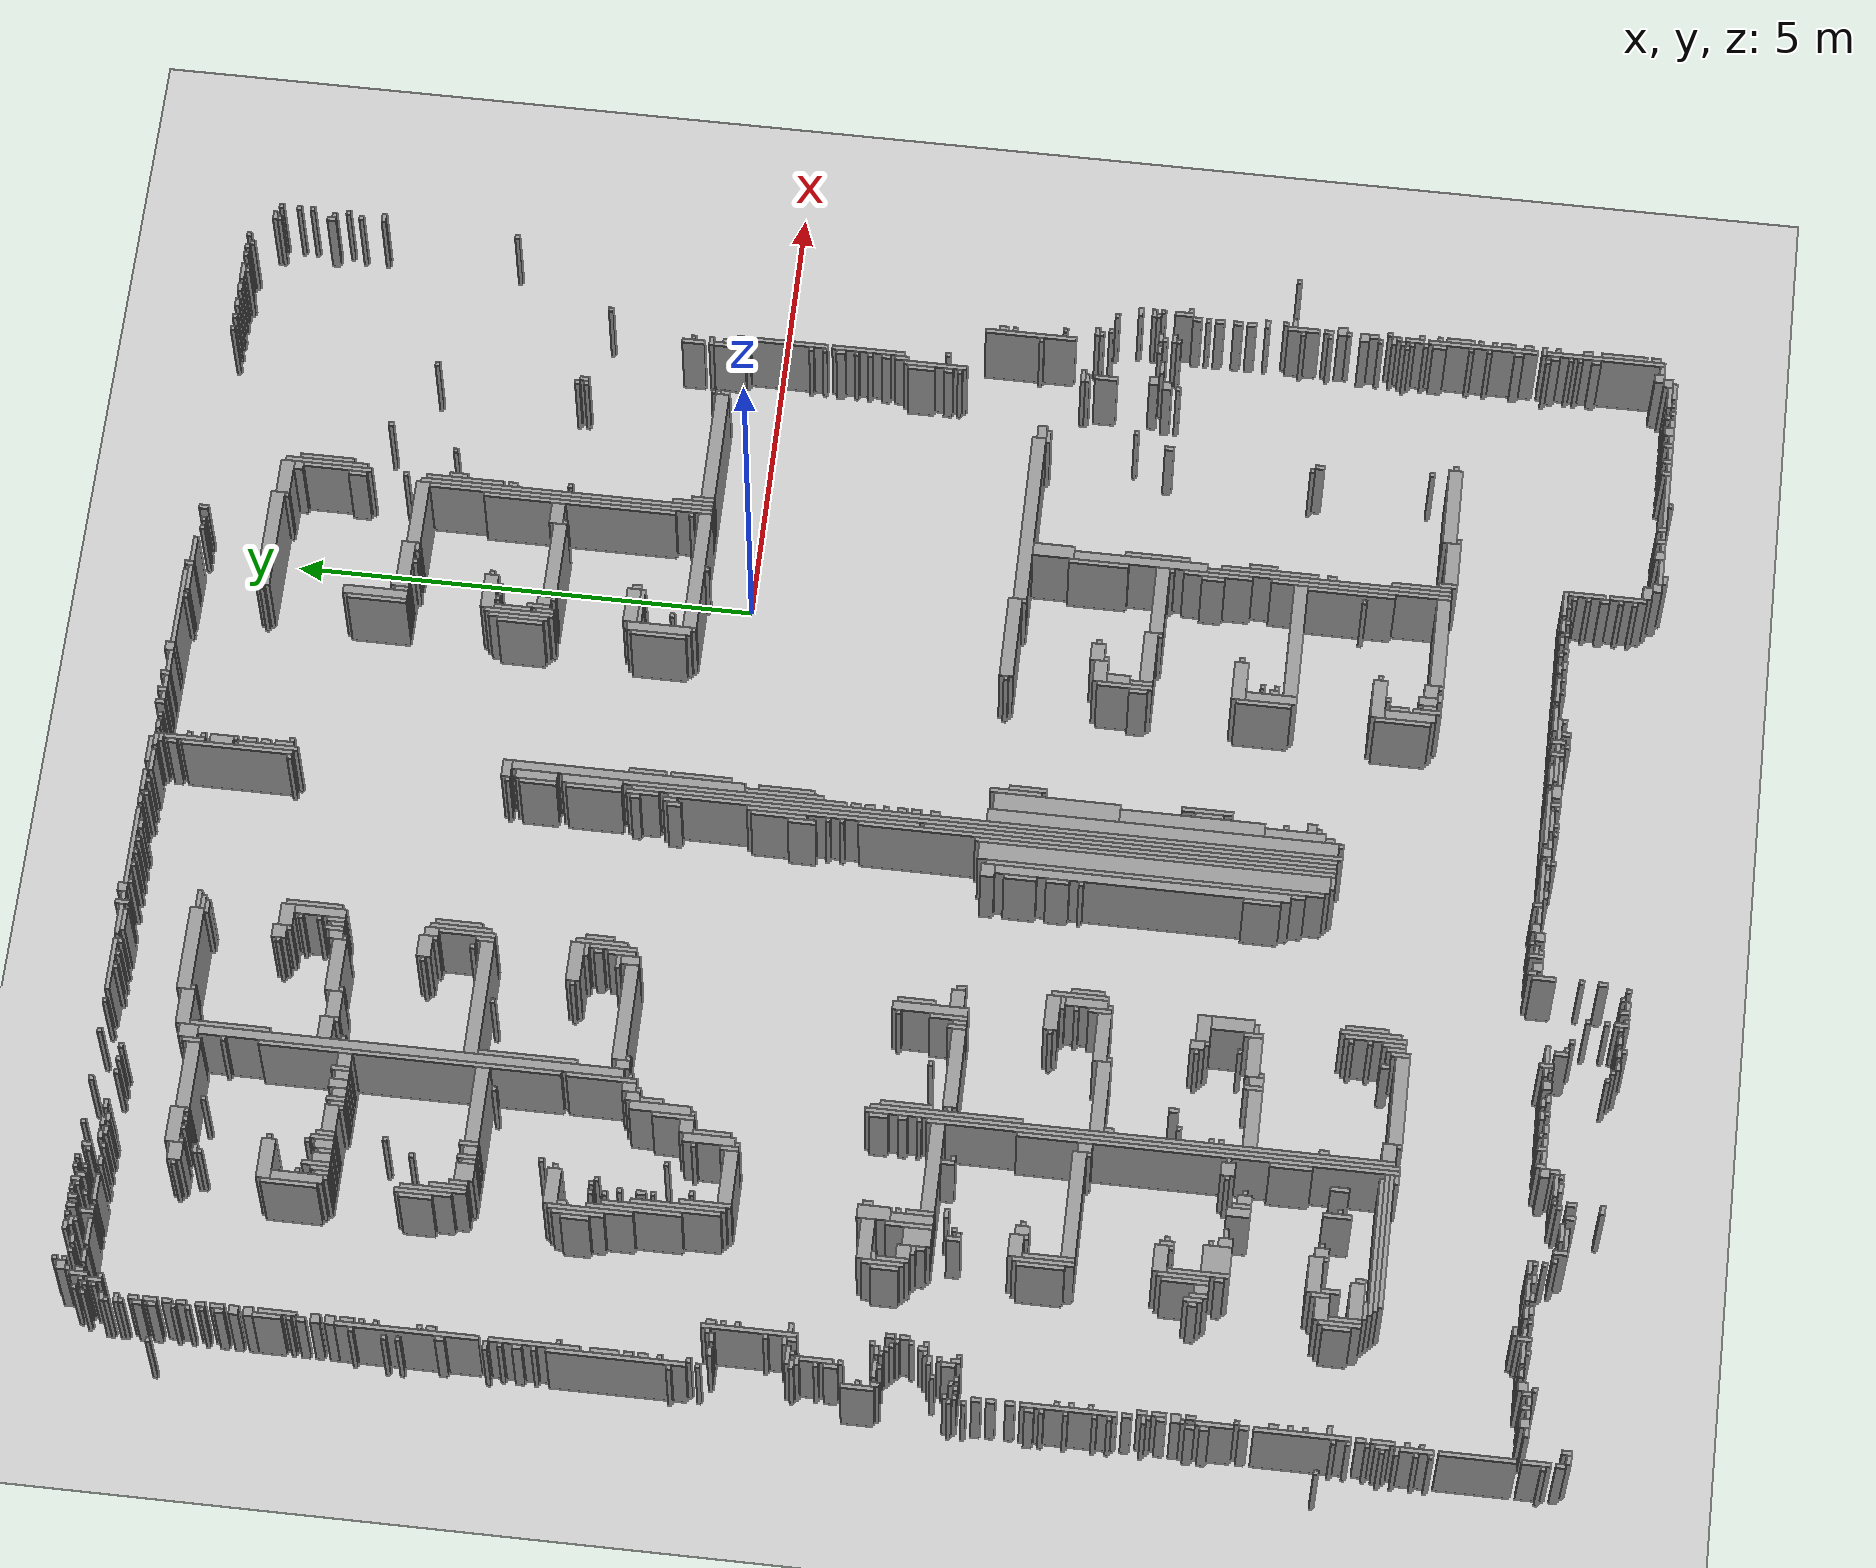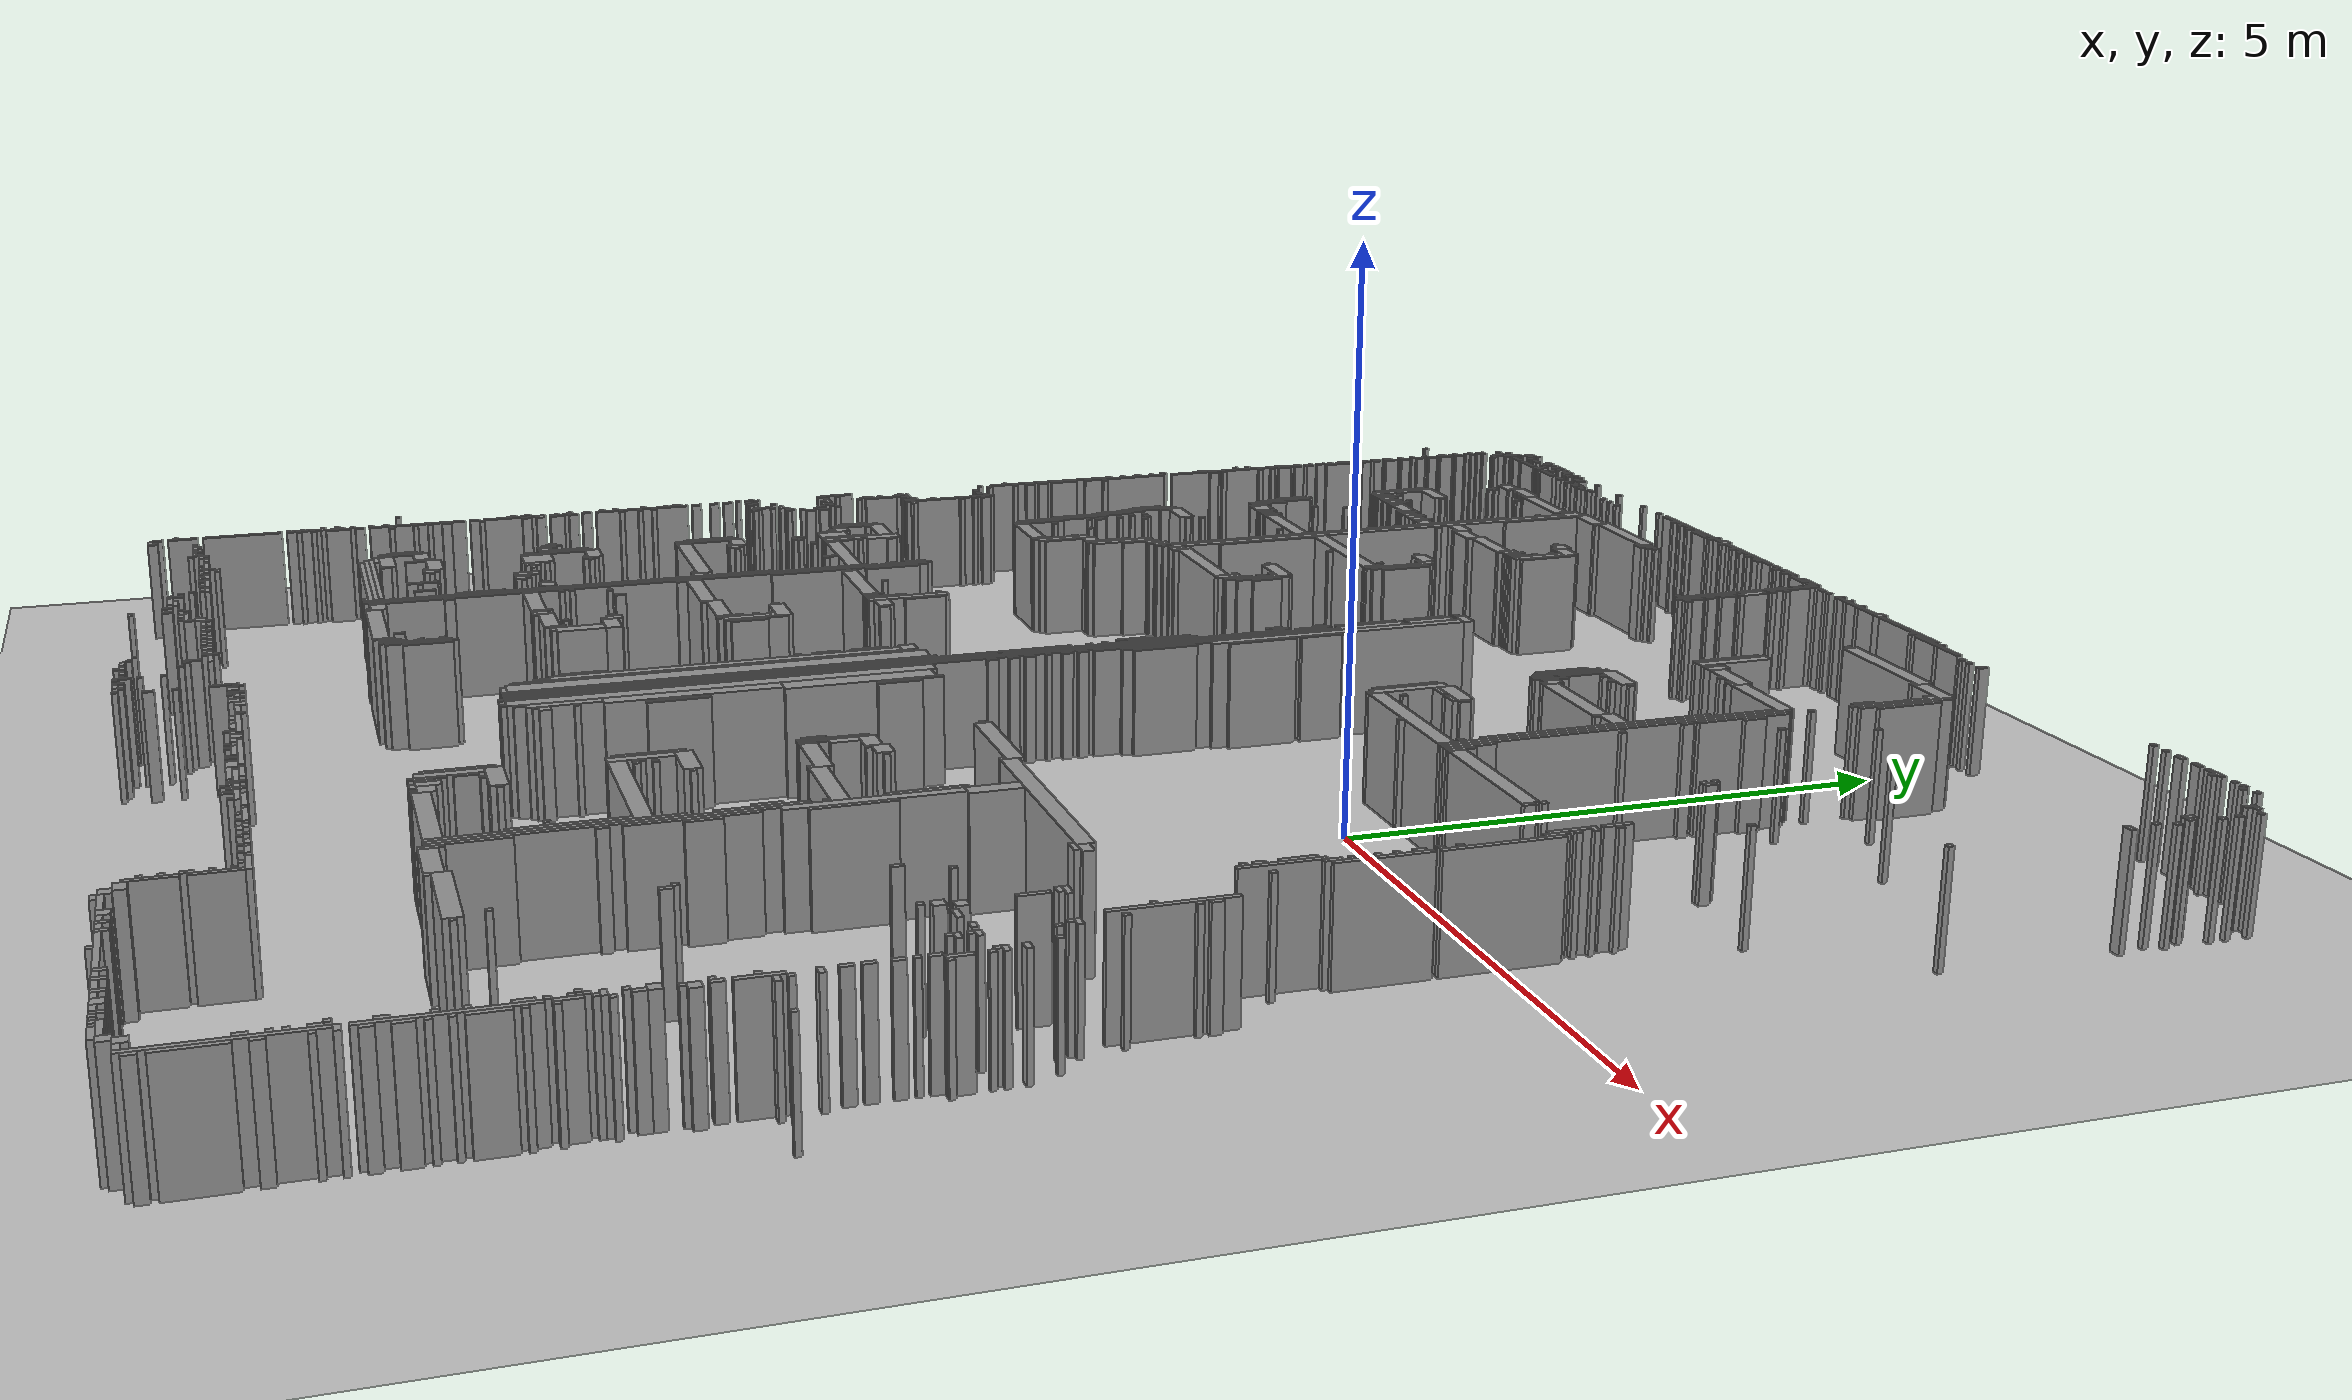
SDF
<?xml version="1.0"?>
<sdf version="1.6">
  <world name="default">
    <include><uri>model://ground_plane</uri></include>
    <include><uri>model://sun</uri></include>
    <scene><shadows>false</shadows></scene>
    <model name="map_walls">
      <static>true</static>
      <link name="walls">
      <collision name="c0"><pose>-8.775 6.175 0.500 0 0 0</pose><geometry><box><size>0.050 0.050 1.000</size></box></geometry></collision>
      <visual name="v0"><pose>-8.775 6.175 0.500 0 0 0</pose><geometry><box><size>0.050 0.050 1.000</size></box></geometry><material><script><uri>file://media/materials/scripts/gazebo.material</uri><name>Gazebo/Grey</name></script></material></visual>
      <collision name="c1"><pose>-4.675 6.125 0.500 0 0 0</pose><geometry><box><size>0.050 0.150 1.000</size></box></geometry></collision>
      <visual name="v1"><pose>-4.675 6.125 0.500 0 0 0</pose><geometry><box><size>0.050 0.150 1.000</size></box></geometry><material><script><uri>file://media/materials/scripts/gazebo.material</uri><name>Gazebo/Grey</name></script></material></visual>
      <collision name="c2"><pose>-4.500 6.150 0.500 0 0 0</pose><geometry><box><size>0.100 0.100 1.000</size></box></geometry></collision>
      <visual name="v2"><pose>-4.500 6.150 0.500 0 0 0</pose><geometry><box><size>0.100 0.100 1.000</size></box></geometry><material><script><uri>file://media/materials/scripts/gazebo.material</uri><name>Gazebo/Grey</name></script></material></visual>
      <collision name="c3"><pose>-8.850 6.100 0.500 0 0 0</pose><geometry><box><size>0.100 0.100 1.000</size></box></geometry></collision>
      <visual name="v3"><pose>-8.850 6.100 0.500 0 0 0</pose><geometry><box><size>0.100 0.100 1.000</size></box></geometry><material><script><uri>file://media/materials/scripts/gazebo.material</uri><name>Gazebo/Grey</name></script></material></visual>
      <collision name="c4"><pose>-8.400 6.125 0.500 0 0 0</pose><geometry><box><size>0.100 0.050 1.000</size></box></geometry></collision>
      <visual name="v4"><pose>-8.400 6.125 0.500 0 0 0</pose><geometry><box><size>0.100 0.050 1.000</size></box></geometry><material><script><uri>file://media/materials/scripts/gazebo.material</uri><name>Gazebo/Grey</name></script></material></visual>
      <collision name="c5"><pose>-8.275 6.125 0.500 0 0 0</pose><geometry><box><size>0.050 0.050 1.000</size></box></geometry></collision>
      <visual name="v5"><pose>-8.275 6.125 0.500 0 0 0</pose><geometry><box><size>0.050 0.050 1.000</size></box></geometry><material><script><uri>file://media/materials/scripts/gazebo.material</uri><name>Gazebo/Grey</name></script></material></visual>
      <collision name="c6"><pose>-8.175 6.100 0.500 0 0 0</pose><geometry><box><size>0.050 0.100 1.000</size></box></geometry></collision>
      <visual name="v6"><pose>-8.175 6.100 0.500 0 0 0</pose><geometry><box><size>0.050 0.100 1.000</size></box></geometry><material><script><uri>file://media/materials/scripts/gazebo.material</uri><name>Gazebo/Grey</name></script></material></visual>
      <collision name="c7"><pose>-8.075 6.100 0.500 0 0 0</pose><geometry><box><size>0.050 0.100 1.000</size></box></geometry></collision>
      <visual name="v7"><pose>-8.075 6.100 0.500 0 0 0</pose><geometry><box><size>0.050 0.100 1.000</size></box></geometry><material><script><uri>file://media/materials/scripts/gazebo.material</uri><name>Gazebo/Grey</name></script></material></visual>
      <collision name="c8"><pose>-7.975 6.125 0.500 0 0 0</pose><geometry><box><size>0.050 0.050 1.000</size></box></geometry></collision>
      <visual name="v8"><pose>-7.975 6.125 0.500 0 0 0</pose><geometry><box><size>0.050 0.050 1.000</size></box></geometry><material><script><uri>file://media/materials/scripts/gazebo.material</uri><name>Gazebo/Grey</name></script></material></visual>
      <collision name="c9"><pose>-7.875 6.100 0.500 0 0 0</pose><geometry><box><size>0.050 0.100 1.000</size></box></geometry></collision>
      <visual name="v9"><pose>-7.875 6.100 0.500 0 0 0</pose><geometry><box><size>0.050 0.100 1.000</size></box></geometry><material><script><uri>file://media/materials/scripts/gazebo.material</uri><name>Gazebo/Grey</name></script></material></visual>
      <collision name="c10"><pose>-7.725 6.125 0.500 0 0 0</pose><geometry><box><size>0.050 0.050 1.000</size></box></geometry></collision>
      <visual name="v10"><pose>-7.725 6.125 0.500 0 0 0</pose><geometry><box><size>0.050 0.050 1.000</size></box></geometry><material><script><uri>file://media/materials/scripts/gazebo.material</uri><name>Gazebo/Grey</name></script></material></visual>
      <collision name="c11"><pose>-7.625 6.125 0.500 0 0 0</pose><geometry><box><size>0.050 0.050 1.000</size></box></geometry></collision>
      <visual name="v11"><pose>-7.625 6.125 0.500 0 0 0</pose><geometry><box><size>0.050 0.050 1.000</size></box></geometry><material><script><uri>file://media/materials/scripts/gazebo.material</uri><name>Gazebo/Grey</name></script></material></visual>
      <collision name="c12"><pose>-7.225 6.125 0.500 0 0 0</pose><geometry><box><size>0.050 0.050 1.000</size></box></geometry></collision>
      <visual name="v12"><pose>-7.225 6.125 0.500 0 0 0</pose><geometry><box><size>0.050 0.050 1.000</size></box></geometry><material><script><uri>file://media/materials/scripts/gazebo.material</uri><name>Gazebo/Grey</name></script></material></visual>
      <collision name="c13"><pose>-6.725 6.125 0.500 0 0 0</pose><geometry><box><size>0.050 0.050 1.000</size></box></geometry></collision>
      <visual name="v13"><pose>-6.725 6.125 0.500 0 0 0</pose><geometry><box><size>0.050 0.050 1.000</size></box></geometry><material><script><uri>file://media/materials/scripts/gazebo.material</uri><name>Gazebo/Grey</name></script></material></visual>
      <collision name="c14"><pose>-6.175 6.125 0.500 0 0 0</pose><geometry><box><size>0.050 0.050 1.000</size></box></geometry></collision>
      <visual name="v14"><pose>-6.175 6.125 0.500 0 0 0</pose><geometry><box><size>0.050 0.050 1.000</size></box></geometry><material><script><uri>file://media/materials/scripts/gazebo.material</uri><name>Gazebo/Grey</name></script></material></visual>
      <collision name="c15"><pose>-5.825 6.125 0.500 0 0 0</pose><geometry><box><size>0.050 0.050 1.000</size></box></geometry></collision>
      <visual name="v15"><pose>-5.825 6.125 0.500 0 0 0</pose><geometry><box><size>0.050 0.050 1.000</size></box></geometry><material><script><uri>file://media/materials/scripts/gazebo.material</uri><name>Gazebo/Grey</name></script></material></visual>
      <collision name="c16"><pose>-5.400 6.125 0.500 0 0 0</pose><geometry><box><size>0.600 0.050 1.000</size></box></geometry></collision>
      <visual name="v16"><pose>-5.400 6.125 0.500 0 0 0</pose><geometry><box><size>0.600 0.050 1.000</size></box></geometry><material><script><uri>file://media/materials/scripts/gazebo.material</uri><name>Gazebo/Grey</name></script></material></visual>
      <collision name="c17"><pose>-4.875 6.125 0.500 0 0 0</pose><geometry><box><size>0.350 0.050 1.000</size></box></geometry></collision>
      <visual name="v17"><pose>-4.875 6.125 0.500 0 0 0</pose><geometry><box><size>0.350 0.050 1.000</size></box></geometry><material><script><uri>file://media/materials/scripts/gazebo.material</uri><name>Gazebo/Grey</name></script></material></visual>
      <collision name="c18"><pose>-4.600 6.125 0.500 0 0 0</pose><geometry><box><size>0.100 0.050 1.000</size></box></geometry></collision>
      <visual name="v18"><pose>-4.600 6.125 0.500 0 0 0</pose><geometry><box><size>0.100 0.050 1.000</size></box></geometry><material><script><uri>file://media/materials/scripts/gazebo.material</uri><name>Gazebo/Grey</name></script></material></visual>
      <collision name="c19"><pose>-4.000 6.125 0.500 0 0 0</pose><geometry><box><size>0.900 0.050 1.000</size></box></geometry></collision>
      <visual name="v19"><pose>-4.000 6.125 0.500 0 0 0</pose><geometry><box><size>0.900 0.050 1.000</size></box></geometry><material><script><uri>file://media/materials/scripts/gazebo.material</uri><name>Gazebo/Grey</name></script></material></visual>
      <collision name="c20"><pose>-3.450 6.125 0.500 0 0 0</pose><geometry><box><size>0.100 0.050 1.000</size></box></geometry></collision>
      <visual name="v20"><pose>-3.450 6.125 0.500 0 0 0</pose><geometry><box><size>0.100 0.050 1.000</size></box></geometry><material><script><uri>file://media/materials/scripts/gazebo.material</uri><name>Gazebo/Grey</name></script></material></visual>
      <collision name="c21"><pose>-3.225 6.125 0.500 0 0 0</pose><geometry><box><size>0.250 0.050 1.000</size></box></geometry></collision>
      <visual name="v21"><pose>-3.225 6.125 0.500 0 0 0</pose><geometry><box><size>0.250 0.050 1.000</size></box></geometry><material><script><uri>file://media/materials/scripts/gazebo.material</uri><name>Gazebo/Grey</name></script></material></visual>
      <collision name="c22"><pose>-2.850 6.125 0.500 0 0 0</pose><geometry><box><size>0.300 0.050 1.000</size></box></geometry></collision>
      <visual name="v22"><pose>-2.850 6.125 0.500 0 0 0</pose><geometry><box><size>0.300 0.050 1.000</size></box></geometry><material><script><uri>file://media/materials/scripts/gazebo.material</uri><name>Gazebo/Grey</name></script></material></visual>
      <collision name="c23"><pose>-2.275 6.100 0.500 0 0 0</pose><geometry><box><size>0.050 0.100 1.000</size></box></geometry></collision>
      <visual name="v23"><pose>-2.275 6.100 0.500 0 0 0</pose><geometry><box><size>0.050 0.100 1.000</size></box></geometry><material><script><uri>file://media/materials/scripts/gazebo.material</uri><name>Gazebo/Grey</name></script></material></visual>
      <collision name="c24"><pose>-2.125 6.100 0.500 0 0 0</pose><geometry><box><size>0.050 0.100 1.000</size></box></geometry></collision>
      <visual name="v24"><pose>-2.125 6.100 0.500 0 0 0</pose><geometry><box><size>0.050 0.100 1.000</size></box></geometry><material><script><uri>file://media/materials/scripts/gazebo.material</uri><name>Gazebo/Grey</name></script></material></visual>
      <collision name="c25"><pose>-1.925 6.100 0.500 0 0 0</pose><geometry><box><size>0.050 0.100 1.000</size></box></geometry></collision>
      <visual name="v25"><pose>-1.925 6.100 0.500 0 0 0</pose><geometry><box><size>0.050 0.100 1.000</size></box></geometry><material><script><uri>file://media/materials/scripts/gazebo.material</uri><name>Gazebo/Grey</name></script></material></visual>
      <collision name="c26"><pose>-1.600 6.100 0.500 0 0 0</pose><geometry><box><size>0.100 0.100 1.000</size></box></geometry></collision>
      <visual name="v26"><pose>-1.600 6.100 0.500 0 0 0</pose><geometry><box><size>0.100 0.100 1.000</size></box></geometry><material><script><uri>file://media/materials/scripts/gazebo.material</uri><name>Gazebo/Grey</name></script></material></visual>
      <collision name="c27"><pose>-8.775 6.075 0.500 0 0 0</pose><geometry><box><size>0.050 0.050 1.000</size></box></geometry></collision>
      <visual name="v27"><pose>-8.775 6.075 0.500 0 0 0</pose><geometry><box><size>0.050 0.050 1.000</size></box></geometry><material><script><uri>file://media/materials/scripts/gazebo.material</uri><name>Gazebo/Grey</name></script></material></visual>
      <collision name="c28"><pose>-8.350 6.075 0.500 0 0 0</pose><geometry><box><size>0.100 0.050 1.000</size></box></geometry></collision>
      <visual name="v28"><pose>-8.350 6.075 0.500 0 0 0</pose><geometry><box><size>0.100 0.050 1.000</size></box></geometry><material><script><uri>file://media/materials/scripts/gazebo.material</uri><name>Gazebo/Grey</name></script></material></visual>
      <collision name="c29"><pose>-7.925 6.075 0.500 0 0 0</pose><geometry><box><size>0.050 0.050 1.000</size></box></geometry></collision>
      <visual name="v29"><pose>-7.925 6.075 0.500 0 0 0</pose><geometry><box><size>0.050 0.050 1.000</size></box></geometry><material><script><uri>file://media/materials/scripts/gazebo.material</uri><name>Gazebo/Grey</name></script></material></visual>
      <collision name="c30"><pose>-7.825 6.050 0.500 0 0 0</pose><geometry><box><size>0.050 0.100 1.000</size></box></geometry></collision>
      <visual name="v30"><pose>-7.825 6.050 0.500 0 0 0</pose><geometry><box><size>0.050 0.100 1.000</size></box></geometry><material><script><uri>file://media/materials/scripts/gazebo.material</uri><name>Gazebo/Grey</name></script></material></visual>
      <collision name="c31"><pose>-7.475 6.050 0.500 0 0 0</pose><geometry><box><size>0.050 0.100 1.000</size></box></geometry></collision>
      <visual name="v31"><pose>-7.475 6.050 0.500 0 0 0</pose><geometry><box><size>0.050 0.100 1.000</size></box></geometry><material><script><uri>file://media/materials/scripts/gazebo.material</uri><name>Gazebo/Grey</name></script></material></visual>
      <collision name="c32"><pose>-5.425 6.075 0.500 0 0 0</pose><geometry><box><size>0.050 0.050 1.000</size></box></geometry></collision>
      <visual name="v32"><pose>-5.425 6.075 0.500 0 0 0</pose><geometry><box><size>0.050 0.050 1.000</size></box></geometry><material><script><uri>file://media/materials/scripts/gazebo.material</uri><name>Gazebo/Grey</name></script></material></visual>
      <collision name="c33"><pose>-5.275 6.075 0.500 0 0 0</pose><geometry><box><size>0.050 0.050 1.000</size></box></geometry></collision>
      <visual name="v33"><pose>-5.275 6.075 0.500 0 0 0</pose><geometry><box><size>0.050 0.050 1.000</size></box></geometry><material><script><uri>file://media/materials/scripts/gazebo.material</uri><name>Gazebo/Grey</name></script></material></visual>
      <collision name="c34"><pose>-5.125 6.075 0.500 0 0 0</pose><geometry><box><size>0.050 0.050 1.000</size></box></geometry></collision>
      <visual name="v34"><pose>-5.125 6.075 0.500 0 0 0</pose><geometry><box><size>0.050 0.050 1.000</size></box></geometry><material><script><uri>file://media/materials/scripts/gazebo.material</uri><name>Gazebo/Grey</name></script></material></visual>
      <collision name="c35"><pose>-4.875 6.075 0.500 0 0 0</pose><geometry><box><size>0.250 0.050 1.000</size></box></geometry></collision>
      <visual name="v35"><pose>-4.875 6.075 0.500 0 0 0</pose><geometry><box><size>0.250 0.050 1.000</size></box></geometry><material><script><uri>file://media/materials/scripts/gazebo.material</uri><name>Gazebo/Grey</name></script></material></visual>
      <collision name="c36"><pose>-4.425 6.075 0.500 0 0 0</pose><geometry><box><size>0.050 0.050 1.000</size></box></geometry></collision>
      <visual name="v36"><pose>-4.425 6.075 0.500 0 0 0</pose><geometry><box><size>0.050 0.050 1.000</size></box></geometry><material><script><uri>file://media/materials/scripts/gazebo.material</uri><name>Gazebo/Grey</name></script></material></visual>
      <collision name="c37"><pose>-4.225 6.075 0.500 0 0 0</pose><geometry><box><size>0.050 0.050 1.000</size></box></geometry></collision>
      <visual name="v37"><pose>-4.225 6.075 0.500 0 0 0</pose><geometry><box><size>0.050 0.050 1.000</size></box></geometry><material><script><uri>file://media/materials/scripts/gazebo.material</uri><name>Gazebo/Grey</name></script></material></visual>
      <collision name="c38"><pose>-4.075 6.075 0.500 0 0 0</pose><geometry><box><size>0.050 0.050 1.000</size></box></geometry></collision>
      <visual name="v38"><pose>-4.075 6.075 0.500 0 0 0</pose><geometry><box><size>0.050 0.050 1.000</size></box></geometry><material><script><uri>file://media/materials/scripts/gazebo.material</uri><name>Gazebo/Grey</name></script></material></visual>
      <collision name="c39"><pose>-3.925 6.075 0.500 0 0 0</pose><geometry><box><size>0.050 0.050 1.000</size></box></geometry></collision>
      <visual name="v39"><pose>-3.925 6.075 0.500 0 0 0</pose><geometry><box><size>0.050 0.050 1.000</size></box></geometry><material><script><uri>file://media/materials/scripts/gazebo.material</uri><name>Gazebo/Grey</name></script></material></visual>
      <collision name="c40"><pose>-3.750 6.075 0.500 0 0 0</pose><geometry><box><size>0.100 0.050 1.000</size></box></geometry></collision>
      <visual name="v40"><pose>-3.750 6.075 0.500 0 0 0</pose><geometry><box><size>0.100 0.050 1.000</size></box></geometry><material><script><uri>file://media/materials/scripts/gazebo.material</uri><name>Gazebo/Grey</name></script></material></visual>
      <collision name="c41"><pose>-3.375 6.075 0.500 0 0 0</pose><geometry><box><size>0.050 0.050 1.000</size></box></geometry></collision>
      <visual name="v41"><pose>-3.375 6.075 0.500 0 0 0</pose><geometry><box><size>0.050 0.050 1.000</size></box></geometry><material><script><uri>file://media/materials/scripts/gazebo.material</uri><name>Gazebo/Grey</name></script></material></visual>
      <collision name="c42"><pose>-3.225 6.075 0.500 0 0 0</pose><geometry><box><size>0.050 0.050 1.000</size></box></geometry></collision>
      <visual name="v42"><pose>-3.225 6.075 0.500 0 0 0</pose><geometry><box><size>0.050 0.050 1.000</size></box></geometry><material><script><uri>file://media/materials/scripts/gazebo.material</uri><name>Gazebo/Grey</name></script></material></visual>
      <collision name="c43"><pose>-2.975 6.075 0.500 0 0 0</pose><geometry><box><size>0.250 0.050 1.000</size></box></geometry></collision>
      <visual name="v43"><pose>-2.975 6.075 0.500 0 0 0</pose><geometry><box><size>0.250 0.050 1.000</size></box></geometry><material><script><uri>file://media/materials/scripts/gazebo.material</uri><name>Gazebo/Grey</name></script></material></visual>
      <collision name="c44"><pose>-2.725 6.075 0.500 0 0 0</pose><geometry><box><size>0.150 0.050 1.000</size></box></geometry></collision>
      <visual name="v44"><pose>-2.725 6.075 0.500 0 0 0</pose><geometry><box><size>0.150 0.050 1.000</size></box></geometry><material><script><uri>file://media/materials/scripts/gazebo.material</uri><name>Gazebo/Grey</name></script></material></visual>
      <collision name="c45"><pose>-2.550 6.075 0.500 0 0 0</pose><geometry><box><size>0.100 0.050 1.000</size></box></geometry></collision>
      <visual name="v45"><pose>-2.550 6.075 0.500 0 0 0</pose><geometry><box><size>0.100 0.050 1.000</size></box></geometry><material><script><uri>file://media/materials/scripts/gazebo.material</uri><name>Gazebo/Grey</name></script></material></visual>
      <collision name="c46"><pose>-2.425 6.075 0.500 0 0 0</pose><geometry><box><size>0.050 0.050 1.000</size></box></geometry></collision>
      <visual name="v46"><pose>-2.425 6.075 0.500 0 0 0</pose><geometry><box><size>0.050 0.050 1.000</size></box></geometry><material><script><uri>file://media/materials/scripts/gazebo.material</uri><name>Gazebo/Grey</name></script></material></visual>
      <collision name="c47"><pose>-2.200 6.075 0.500 0 0 0</pose><geometry><box><size>0.100 0.050 1.000</size></box></geometry></collision>
      <visual name="v47"><pose>-2.200 6.075 0.500 0 0 0</pose><geometry><box><size>0.100 0.050 1.000</size></box></geometry><material><script><uri>file://media/materials/scripts/gazebo.material</uri><name>Gazebo/Grey</name></script></material></visual>
      <collision name="c48"><pose>-2.025 6.075 0.500 0 0 0</pose><geometry><box><size>0.150 0.050 1.000</size></box></geometry></collision>
      <visual name="v48"><pose>-2.025 6.075 0.500 0 0 0</pose><geometry><box><size>0.150 0.050 1.000</size></box></geometry><material><script><uri>file://media/materials/scripts/gazebo.material</uri><name>Gazebo/Grey</name></script></material></visual>
      <collision name="c49"><pose>-1.775 6.075 0.500 0 0 0</pose><geometry><box><size>0.250 0.050 1.000</size></box></geometry></collision>
      <visual name="v49"><pose>-1.775 6.075 0.500 0 0 0</pose><geometry><box><size>0.250 0.050 1.000</size></box></geometry><material><script><uri>file://media/materials/scripts/gazebo.material</uri><name>Gazebo/Grey</name></script></material></visual>
      <collision name="c50"><pose>-1.100 6.075 0.500 0 0 0</pose><geometry><box><size>0.900 0.050 1.000</size></box></geometry></collision>
      <visual name="v50"><pose>-1.100 6.075 0.500 0 0 0</pose><geometry><box><size>0.900 0.050 1.000</size></box></geometry><material><script><uri>file://media/materials/scripts/gazebo.material</uri><name>Gazebo/Grey</name></script></material></visual>
      <collision name="c51"><pose>-0.575 6.050 0.500 0 0 0</pose><geometry><box><size>0.050 0.100 1.000</size></box></geometry></collision>
      <visual name="v51"><pose>-0.575 6.050 0.500 0 0 0</pose><geometry><box><size>0.050 0.100 1.000</size></box></geometry><material><script><uri>file://media/materials/scripts/gazebo.material</uri><name>Gazebo/Grey</name></script></material></visual>
      <collision name="c52"><pose>-8.875 6.025 0.500 0 0 0</pose><geometry><box><size>0.050 0.050 1.000</size></box></geometry></collision>
      <visual name="v52"><pose>-8.875 6.025 0.500 0 0 0</pose><geometry><box><size>0.050 0.050 1.000</size></box></geometry><material><script><uri>file://media/materials/scripts/gazebo.material</uri><name>Gazebo/Grey</name></script></material></visual>
      <collision name="c53"><pose>-8.675 6.025 0.500 0 0 0</pose><geometry><box><size>0.050 0.050 1.000</size></box></geometry></collision>
      <visual name="v53"><pose>-8.675 6.025 0.500 0 0 0</pose><geometry><box><size>0.050 0.050 1.000</size></box></geometry><material><script><uri>file://media/materials/scripts/gazebo.material</uri><name>Gazebo/Grey</name></script></material></visual>
      <collision name="c54"><pose>-8.550 6.025 0.500 0 0 0</pose><geometry><box><size>0.100 0.050 1.000</size></box></geometry></collision>
      <visual name="v54"><pose>-8.550 6.025 0.500 0 0 0</pose><geometry><box><size>0.100 0.050 1.000</size></box></geometry><material><script><uri>file://media/materials/scripts/gazebo.material</uri><name>Gazebo/Grey</name></script></material></visual>
      <collision name="c55"><pose>-8.325 6.025 0.500 0 0 0</pose><geometry><box><size>0.050 0.050 1.000</size></box></geometry></collision>
      <visual name="v55"><pose>-8.325 6.025 0.500 0 0 0</pose><geometry><box><size>0.050 0.050 1.000</size></box></geometry><material><script><uri>file://media/materials/scripts/gazebo.material</uri><name>Gazebo/Grey</name></script></material></visual>
      <collision name="c56"><pose>-7.725 6.025 0.500 0 0 0</pose><geometry><box><size>0.050 0.050 1.000</size></box></geometry></collision>
      <visual name="v56"><pose>-7.725 6.025 0.500 0 0 0</pose><geometry><box><size>0.050 0.050 1.000</size></box></geometry><material><script><uri>file://media/materials/scripts/gazebo.material</uri><name>Gazebo/Grey</name></script></material></visual>
      <collision name="c57"><pose>-7.525 6.025 0.500 0 0 0</pose><geometry><box><size>0.050 0.050 1.000</size></box></geometry></collision>
      <visual name="v57"><pose>-7.525 6.025 0.500 0 0 0</pose><geometry><box><size>0.050 0.050 1.000</size></box></geometry><material><script><uri>file://media/materials/scripts/gazebo.material</uri><name>Gazebo/Grey</name></script></material></visual>
      <collision name="c58"><pose>-2.700 6.025 0.500 0 0 0</pose><geometry><box><size>0.100 0.050 1.000</size></box></geometry></collision>
      <visual name="v58"><pose>-2.700 6.025 0.500 0 0 0</pose><geometry><box><size>0.100 0.050 1.000</size></box></geometry><material><script><uri>file://media/materials/scripts/gazebo.material</uri><name>Gazebo/Grey</name></script></material></visual>
      <collision name="c59"><pose>-0.975 6.025 0.500 0 0 0</pose><geometry><box><size>0.050 0.050 1.000</size></box></geometry></collision>
      <visual name="v59"><pose>-0.975 6.025 0.500 0 0 0</pose><geometry><box><size>0.050 0.050 1.000</size></box></geometry><material><script><uri>file://media/materials/scripts/gazebo.material</uri><name>Gazebo/Grey</name></script></material></visual>
      <collision name="c60"><pose>-0.750 6.025 0.500 0 0 0</pose><geometry><box><size>0.300 0.050 1.000</size></box></geometry></collision>
      <visual name="v60"><pose>-0.750 6.025 0.500 0 0 0</pose><geometry><box><size>0.300 0.050 1.000</size></box></geometry><material><script><uri>file://media/materials/scripts/gazebo.material</uri><name>Gazebo/Grey</name></script></material></visual>
      <collision name="c61"><pose>-0.400 6.025 0.500 0 0 0</pose><geometry><box><size>0.300 0.050 1.000</size></box></geometry></collision>
      <visual name="v61"><pose>-0.400 6.025 0.500 0 0 0</pose><geometry><box><size>0.300 0.050 1.000</size></box></geometry><material><script><uri>file://media/materials/scripts/gazebo.material</uri><name>Gazebo/Grey</name></script></material></visual>
      <collision name="c62"><pose>0.125 6.000 0.500 0 0 0</pose><geometry><box><size>0.050 0.100 1.000</size></box></geometry></collision>
      <visual name="v62"><pose>0.125 6.000 0.500 0 0 0</pose><geometry><box><size>0.050 0.100 1.000</size></box></geometry><material><script><uri>file://media/materials/scripts/gazebo.material</uri><name>Gazebo/Grey</name></script></material></visual>
      <collision name="c63"><pose>2.375 6.025 0.500 0 0 0</pose><geometry><box><size>0.050 0.050 1.000</size></box></geometry></collision>
      <visual name="v63"><pose>2.375 6.025 0.500 0 0 0</pose><geometry><box><size>0.050 0.050 1.000</size></box></geometry><material><script><uri>file://media/materials/scripts/gazebo.material</uri><name>Gazebo/Grey</name></script></material></visual>
      <collision name="c64"><pose>2.525 6.025 0.500 0 0 0</pose><geometry><box><size>0.050 0.050 1.000</size></box></geometry></collision>
      <visual name="v64"><pose>2.525 6.025 0.500 0 0 0</pose><geometry><box><size>0.050 0.050 1.000</size></box></geometry><material><script><uri>file://media/materials/scripts/gazebo.material</uri><name>Gazebo/Grey</name></script></material></visual>
      <collision name="c65"><pose>2.700 6.025 0.500 0 0 0</pose><geometry><box><size>0.100 0.050 1.000</size></box></geometry></collision>
      <visual name="v65"><pose>2.700 6.025 0.500 0 0 0</pose><geometry><box><size>0.100 0.050 1.000</size></box></geometry><material><script><uri>file://media/materials/scripts/gazebo.material</uri><name>Gazebo/Grey</name></script></material></visual>
      <collision name="c66"><pose>2.900 6.025 0.500 0 0 0</pose><geometry><box><size>0.100 0.050 1.000</size></box></geometry></collision>
      <visual name="v66"><pose>2.900 6.025 0.500 0 0 0</pose><geometry><box><size>0.100 0.050 1.000</size></box></geometry><material><script><uri>file://media/materials/scripts/gazebo.material</uri><name>Gazebo/Grey</name></script></material></visual>
      <collision name="c67"><pose>3.100 6.025 0.500 0 0 0</pose><geometry><box><size>0.200 0.050 1.000</size></box></geometry></collision>
      <visual name="v67"><pose>3.100 6.025 0.500 0 0 0</pose><geometry><box><size>0.200 0.050 1.000</size></box></geometry><material><script><uri>file://media/materials/scripts/gazebo.material</uri><name>Gazebo/Grey</name></script></material></visual>
      <collision name="c68"><pose>3.325 6.025 0.500 0 0 0</pose><geometry><box><size>0.050 0.050 1.000</size></box></geometry></collision>
      <visual name="v68"><pose>3.325 6.025 0.500 0 0 0</pose><geometry><box><size>0.050 0.050 1.000</size></box></geometry><material><script><uri>file://media/materials/scripts/gazebo.material</uri><name>Gazebo/Grey</name></script></material></visual>
      <collision name="c69"><pose>3.425 6.025 0.500 0 0 0</pose><geometry><box><size>0.050 0.050 1.000</size></box></geometry></collision>
      <visual name="v69"><pose>3.425 6.025 0.500 0 0 0</pose><geometry><box><size>0.050 0.050 1.000</size></box></geometry><material><script><uri>file://media/materials/scripts/gazebo.material</uri><name>Gazebo/Grey</name></script></material></visual>
      <collision name="c70"><pose>3.575 6.025 0.500 0 0 0</pose><geometry><box><size>0.050 0.050 1.000</size></box></geometry></collision>
      <visual name="v70"><pose>3.575 6.025 0.500 0 0 0</pose><geometry><box><size>0.050 0.050 1.000</size></box></geometry><material><script><uri>file://media/materials/scripts/gazebo.material</uri><name>Gazebo/Grey</name></script></material></visual>
      <collision name="c71"><pose>-8.925 5.900 0.500 0 0 0</pose><geometry><box><size>0.050 0.200 1.000</size></box></geometry></collision>
      <visual name="v71"><pose>-8.925 5.900 0.500 0 0 0</pose><geometry><box><size>0.050 0.200 1.000</size></box></geometry><material><script><uri>file://media/materials/scripts/gazebo.material</uri><name>Gazebo/Grey</name></script></material></visual>
      <collision name="c72"><pose>-8.225 5.925 0.500 0 0 0</pose><geometry><box><size>0.050 0.150 1.000</size></box></geometry></collision>
      <visual name="v72"><pose>-8.225 5.925 0.500 0 0 0</pose><geometry><box><size>0.050 0.150 1.000</size></box></geometry><material><script><uri>file://media/materials/scripts/gazebo.material</uri><name>Gazebo/Grey</name></script></material></visual>
      <collision name="c73"><pose>-8.025 5.975 0.500 0 0 0</pose><geometry><box><size>0.050 0.050 1.000</size></box></geometry></collision>
      <visual name="v73"><pose>-8.025 5.975 0.500 0 0 0</pose><geometry><box><size>0.050 0.050 1.000</size></box></geometry><material><script><uri>file://media/materials/scripts/gazebo.material</uri><name>Gazebo/Grey</name></script></material></visual>
      <collision name="c74"><pose>-2.675 5.775 0.500 0 0 0</pose><geometry><box><size>0.050 0.450 1.000</size></box></geometry></collision>
      <visual name="v74"><pose>-2.675 5.775 0.500 0 0 0</pose><geometry><box><size>0.050 0.450 1.000</size></box></geometry><material><script><uri>file://media/materials/scripts/gazebo.material</uri><name>Gazebo/Grey</name></script></material></visual>
      <collision name="c75"><pose>-0.125 5.975 0.500 0 0 0</pose><geometry><box><size>0.050 0.050 1.000</size></box></geometry></collision>
      <visual name="v75"><pose>-0.125 5.975 0.500 0 0 0</pose><geometry><box><size>0.050 0.050 1.000</size></box></geometry><material><script><uri>file://media/materials/scripts/gazebo.material</uri><name>Gazebo/Grey</name></script></material></visual>
      <collision name="c76"><pose>-0.025 5.975 0.500 0 0 0</pose><geometry><box><size>0.050 0.050 1.000</size></box></geometry></collision>
      <visual name="v76"><pose>-0.025 5.975 0.500 0 0 0</pose><geometry><box><size>0.050 0.050 1.000</size></box></geometry><material><script><uri>file://media/materials/scripts/gazebo.material</uri><name>Gazebo/Grey</name></script></material></visual>
      <collision name="c77"><pose>3.125 5.975 0.500 0 0 0</pose><geometry><box><size>0.050 0.050 1.000</size></box></geometry></collision>
      <visual name="v77"><pose>3.125 5.975 0.500 0 0 0</pose><geometry><box><size>0.050 0.050 1.000</size></box></geometry><material><script><uri>file://media/materials/scripts/gazebo.material</uri><name>Gazebo/Grey</name></script></material></visual>
      <collision name="c78"><pose>3.475 5.975 0.500 0 0 0</pose><geometry><box><size>0.050 0.050 1.000</size></box></geometry></collision>
      <visual name="v78"><pose>3.475 5.975 0.500 0 0 0</pose><geometry><box><size>0.050 0.050 1.000</size></box></geometry><material><script><uri>file://media/materials/scripts/gazebo.material</uri><name>Gazebo/Grey</name></script></material></visual>
      <collision name="c79"><pose>-9.075 5.925 0.500 0 0 0</pose><geometry><box><size>0.050 0.050 1.000</size></box></geometry></collision>
      <visual name="v79"><pose>-9.075 5.925 0.500 0 0 0</pose><geometry><box><size>0.050 0.050 1.000</size></box></geometry><material><script><uri>file://media/materials/scripts/gazebo.material</uri><name>Gazebo/Grey</name></script></material></visual>
      <collision name="c80"><pose>-8.875 5.900 0.500 0 0 0</pose><geometry><box><size>0.050 0.100 1.000</size></box></geometry></collision>
      <visual name="v80"><pose>-8.875 5.900 0.500 0 0 0</pose><geometry><box><size>0.050 0.100 1.000</size></box></geometry><material><script><uri>file://media/materials/scripts/gazebo.material</uri><name>Gazebo/Grey</name></script></material></visual>
      <collision name="c81"><pose>-7.350 5.925 0.500 0 0 0</pose><geometry><box><size>0.100 0.050 1.000</size></box></geometry></collision>
      <visual name="v81"><pose>-7.350 5.925 0.500 0 0 0</pose><geometry><box><size>0.100 0.050 1.000</size></box></geometry><material><script><uri>file://media/materials/scripts/gazebo.material</uri><name>Gazebo/Grey</name></script></material></visual>
      <collision name="c82"><pose>-7.200 5.925 0.500 0 0 0</pose><geometry><box><size>0.100 0.050 1.000</size></box></geometry></collision>
      <visual name="v82"><pose>-7.200 5.925 0.500 0 0 0</pose><geometry><box><size>0.100 0.050 1.000</size></box></geometry><material><script><uri>file://media/materials/scripts/gazebo.material</uri><name>Gazebo/Grey</name></script></material></visual>
      <collision name="c83"><pose>-7.000 5.925 0.500 0 0 0</pose><geometry><box><size>0.100 0.050 1.000</size></box></geometry></collision>
      <visual name="v83"><pose>-7.000 5.925 0.500 0 0 0</pose><geometry><box><size>0.100 0.050 1.000</size></box></geometry><material><script><uri>file://media/materials/scripts/gazebo.material</uri><name>Gazebo/Grey</name></script></material></visual>
      <collision name="c84"><pose>-2.725 5.900 0.500 0 0 0</pose><geometry><box><size>0.050 0.100 1.000</size></box></geometry></collision>
      <visual name="v84"><pose>-2.725 5.900 0.500 0 0 0</pose><geometry><box><size>0.050 0.100 1.000</size></box></geometry><material><script><uri>file://media/materials/scripts/gazebo.material</uri><name>Gazebo/Grey</name></script></material></visual>
      <collision name="c85"><pose>-8.975 5.875 0.500 0 0 0</pose><geometry><box><size>0.050 0.050 1.000</size></box></geometry></collision>
      <visual name="v85"><pose>-8.975 5.875 0.500 0 0 0</pose><geometry><box><size>0.050 0.050 1.000</size></box></geometry><material><script><uri>file://media/materials/scripts/gazebo.material</uri><name>Gazebo/Grey</name></script></material></visual>
      <collision name="c86"><pose>-8.725 5.875 0.500 0 0 0</pose><geometry><box><size>0.150 0.050 1.000</size></box></geometry></collision>
      <visual name="v86"><pose>-8.725 5.875 0.500 0 0 0</pose><geometry><box><size>0.150 0.050 1.000</size></box></geometry><material><script><uri>file://media/materials/scripts/gazebo.material</uri><name>Gazebo/Grey</name></script></material></visual>
      <collision name="c87"><pose>-8.450 5.875 0.500 0 0 0</pose><geometry><box><size>0.300 0.050 1.000</size></box></geometry></collision>
      <visual name="v87"><pose>-8.450 5.875 0.500 0 0 0</pose><geometry><box><size>0.300 0.050 1.000</size></box></geometry><material><script><uri>file://media/materials/scripts/gazebo.material</uri><name>Gazebo/Grey</name></script></material></visual>
      <collision name="c88"><pose>-8.175 5.875 0.500 0 0 0</pose><geometry><box><size>0.050 0.050 1.000</size></box></geometry></collision>
      <visual name="v88"><pose>-8.175 5.875 0.500 0 0 0</pose><geometry><box><size>0.050 0.050 1.000</size></box></geometry><material><script><uri>file://media/materials/scripts/gazebo.material</uri><name>Gazebo/Grey</name></script></material></visual>
      <collision name="c89"><pose>-7.950 5.875 0.500 0 0 0</pose><geometry><box><size>0.300 0.050 1.000</size></box></geometry></collision>
      <visual name="v89"><pose>-7.950 5.875 0.500 0 0 0</pose><geometry><box><size>0.300 0.050 1.000</size></box></geometry><material><script><uri>file://media/materials/scripts/gazebo.material</uri><name>Gazebo/Grey</name></script></material></visual>
      <collision name="c90"><pose>-7.650 5.875 0.500 0 0 0</pose><geometry><box><size>0.100 0.050 1.000</size></box></geometry></collision>
      <visual name="v90"><pose>-7.650 5.875 0.500 0 0 0</pose><geometry><box><size>0.100 0.050 1.000</size></box></geometry><material><script><uri>file://media/materials/scripts/gazebo.material</uri><name>Gazebo/Grey</name></script></material></visual>
      <collision name="c91"><pose>-7.475 5.875 0.500 0 0 0</pose><geometry><box><size>0.050 0.050 1.000</size></box></geometry></collision>
      <visual name="v91"><pose>-7.475 5.875 0.500 0 0 0</pose><geometry><box><size>0.050 0.050 1.000</size></box></geometry><material><script><uri>file://media/materials/scripts/gazebo.material</uri><name>Gazebo/Grey</name></script></material></visual>
      <collision name="c92"><pose>-7.300 5.875 0.500 0 0 0</pose><geometry><box><size>0.100 0.050 1.000</size></box></geometry></collision>
      <visual name="v92"><pose>-7.300 5.875 0.500 0 0 0</pose><geometry><box><size>0.100 0.050 1.000</size></box></geometry><material><script><uri>file://media/materials/scripts/gazebo.material</uri><name>Gazebo/Grey</name></script></material></visual>
      <collision name="c93"><pose>-7.150 5.875 0.500 0 0 0</pose><geometry><box><size>0.100 0.050 1.000</size></box></geometry></collision>
      <visual name="v93"><pose>-7.150 5.875 0.500 0 0 0</pose><geometry><box><size>0.100 0.050 1.000</size></box></geometry><material><script><uri>file://media/materials/scripts/gazebo.material</uri><name>Gazebo/Grey</name></script></material></visual>
      <collision name="c94"><pose>-6.625 5.875 0.500 0 0 0</pose><geometry><box><size>0.050 0.050 1.000</size></box></geometry></collision>
      <visual name="v94"><pose>-6.625 5.875 0.500 0 0 0</pose><geometry><box><size>0.050 0.050 1.000</size></box></geometry><material><script><uri>file://media/materials/scripts/gazebo.material</uri><name>Gazebo/Grey</name></script></material></visual>
      <collision name="c95"><pose>-6.475 5.875 0.500 0 0 0</pose><geometry><box><size>0.050 0.050 1.000</size></box></geometry></collision>
      <visual name="v95"><pose>-6.475 5.875 0.500 0 0 0</pose><geometry><box><size>0.050 0.050 1.000</size></box></geometry><material><script><uri>file://media/materials/scripts/gazebo.material</uri><name>Gazebo/Grey</name></script></material></visual>
      <collision name="c96"><pose>-6.325 5.875 0.500 0 0 0</pose><geometry><box><size>0.050 0.050 1.000</size></box></geometry></collision>
      <visual name="v96"><pose>-6.325 5.875 0.500 0 0 0</pose><geometry><box><size>0.050 0.050 1.000</size></box></geometry><material><script><uri>file://media/materials/scripts/gazebo.material</uri><name>Gazebo/Grey</name></script></material></visual>
      <collision name="c97"><pose>-9.125 5.825 0.500 0 0 0</pose><geometry><box><size>0.050 0.050 1.000</size></box></geometry></collision>
      <visual name="v97"><pose>-9.125 5.825 0.500 0 0 0</pose><geometry><box><size>0.050 0.050 1.000</size></box></geometry><material><script><uri>file://media/materials/scripts/gazebo.material</uri><name>Gazebo/Grey</name></script></material></visual>
      <collision name="c98"><pose>-9.025 5.825 0.500 0 0 0</pose><geometry><box><size>0.050 0.050 1.000</size></box></geometry></collision>
      <visual name="v98"><pose>-9.025 5.825 0.500 0 0 0</pose><geometry><box><size>0.050 0.050 1.000</size></box></geometry><material><script><uri>file://media/materials/scripts/gazebo.material</uri><name>Gazebo/Grey</name></script></material></visual>
      <collision name="c99"><pose>-8.975 5.725 0.500 0 0 0</pose><geometry><box><size>0.050 0.150 1.000</size></box></geometry></collision>
      <visual name="v99"><pose>-8.975 5.725 0.500 0 0 0</pose><geometry><box><size>0.050 0.150 1.000</size></box></geometry><material><script><uri>file://media/materials/scripts/gazebo.material</uri><name>Gazebo/Grey</name></script></material></visual>
      <collision name="c100"><pose>-2.725 5.200 0.500 0 0 0</pose><geometry><box><size>0.050 1.200 1.000</size></box></geometry></collision>
      <visual name="v100"><pose>-2.725 5.200 0.500 0 0 0</pose><geometry><box><size>0.050 1.200 1.000</size></box></geometry><material><script><uri>file://media/materials/scripts/gazebo.material</uri><name>Gazebo/Grey</name></script></material></visual>
      <collision name="c101"><pose>3.850 5.775 0.500 0 0 0</pose><geometry><box><size>0.100 0.050 1.000</size></box></geometry></collision>
      <visual name="v101"><pose>3.850 5.775 0.500 0 0 0</pose><geometry><box><size>0.100 0.050 1.000</size></box></geometry><material><script><uri>file://media/materials/scripts/gazebo.material</uri><name>Gazebo/Grey</name></script></material></visual>
      <collision name="c102"><pose>-9.025 5.725 0.500 0 0 0</pose><geometry><box><size>0.050 0.050 1.000</size></box></geometry></collision>
      <visual name="v102"><pose>-9.025 5.725 0.500 0 0 0</pose><geometry><box><size>0.050 0.050 1.000</size></box></geometry><material><script><uri>file://media/materials/scripts/gazebo.material</uri><name>Gazebo/Grey</name></script></material></visual>
      <collision name="c103"><pose>-2.625 5.725 0.500 0 0 0</pose><geometry><box><size>0.050 0.050 1.000</size></box></geometry></collision>
      <visual name="v103"><pose>-2.625 5.725 0.500 0 0 0</pose><geometry><box><size>0.050 0.050 1.000</size></box></geometry><material><script><uri>file://media/materials/scripts/gazebo.material</uri><name>Gazebo/Grey</name></script></material></visual>
      <collision name="c104"><pose>3.825 5.725 0.500 0 0 0</pose><geometry><box><size>0.050 0.050 1.000</size></box></geometry></collision>
      <visual name="v104"><pose>3.825 5.725 0.500 0 0 0</pose><geometry><box><size>0.050 0.050 1.000</size></box></geometry><material><script><uri>file://media/materials/scripts/gazebo.material</uri><name>Gazebo/Grey</name></script></material></visual>
      <collision name="c105"><pose>3.975 5.725 0.500 0 0 0</pose><geometry><box><size>0.050 0.050 1.000</size></box></geometry></collision>
      <visual name="v105"><pose>3.975 5.725 0.500 0 0 0</pose><geometry><box><size>0.050 0.050 1.000</size></box></geometry><material><script><uri>file://media/materials/scripts/gazebo.material</uri><name>Gazebo/Grey</name></script></material></visual>
      <collision name="c106"><pose>-8.925 5.675 0.500 0 0 0</pose><geometry><box><size>0.050 0.050 1.000</size></box></geometry></collision>
      <visual name="v106"><pose>-8.925 5.675 0.500 0 0 0</pose><geometry><box><size>0.050 0.050 1.000</size></box></geometry><material><script><uri>file://media/materials/scripts/gazebo.material</uri><name>Gazebo/Grey</name></script></material></visual>
      <collision name="c107"><pose>-9.150 5.625 0.500 0 0 0</pose><geometry><box><size>0.100 0.050 1.000</size></box></geometry></collision>
      <visual name="v107"><pose>-9.150 5.625 0.500 0 0 0</pose><geometry><box><size>0.100 0.050 1.000</size></box></geometry><material><script><uri>file://media/materials/scripts/gazebo.material</uri><name>Gazebo/Grey</name></script></material></visual>
      <collision name="c108"><pose>-9.175 5.575 0.500 0 0 0</pose><geometry><box><size>0.050 0.050 1.000</size></box></geometry></collision>
      <visual name="v108"><pose>-9.175 5.575 0.500 0 0 0</pose><geometry><box><size>0.050 0.050 1.000</size></box></geometry><material><script><uri>file://media/materials/scripts/gazebo.material</uri><name>Gazebo/Grey</name></script></material></visual>
      <collision name="c109"><pose>-2.625 5.575 0.500 0 0 0</pose><geometry><box><size>0.050 0.050 1.000</size></box></geometry></collision>
      <visual name="v109"><pose>-2.625 5.575 0.500 0 0 0</pose><geometry><box><size>0.050 0.050 1.000</size></box></geometry><material><script><uri>file://media/materials/scripts/gazebo.material</uri><name>Gazebo/Grey</name></script></material></visual>
      <collision name="c110"><pose>3.975 5.525 0.500 0 0 0</pose><geometry><box><size>0.050 0.050 1.000</size></box></geometry></collision>
      <visual name="v110"><pose>3.975 5.525 0.500 0 0 0</pose><geometry><box><size>0.050 0.050 1.000</size></box></geometry><material><script><uri>file://media/materials/scripts/gazebo.material</uri><name>Gazebo/Grey</name></script></material></visual>
      <collision name="c111"><pose>-9.150 5.475 0.500 0 0 0</pose><geometry><box><size>0.100 0.050 1.000</size></box></geometry></collision>
      <visual name="v111"><pose>-9.150 5.475 0.500 0 0 0</pose><geometry><box><size>0.100 0.050 1.000</size></box></geometry><material><script><uri>file://media/materials/scripts/gazebo.material</uri><name>Gazebo/Grey</name></script></material></visual>
      <collision name="c112"><pose>-2.650 5.375 0.500 0 0 0</pose><geometry><box><size>0.100 0.250 1.000</size></box></geometry></collision>
      <visual name="v112"><pose>-2.650 5.375 0.500 0 0 0</pose><geometry><box><size>0.100 0.250 1.000</size></box></geometry><material><script><uri>file://media/materials/scripts/gazebo.material</uri><name>Gazebo/Grey</name></script></material></visual>
      <collision name="c113"><pose>-9.175 5.425 0.500 0 0 0</pose><geometry><box><size>0.050 0.050 1.000</size></box></geometry></collision>
      <visual name="v113"><pose>-9.175 5.425 0.500 0 0 0</pose><geometry><box><size>0.050 0.050 1.000</size></box></geometry><material><script><uri>file://media/materials/scripts/gazebo.material</uri><name>Gazebo/Grey</name></script></material></visual>
      <collision name="c114"><pose>-5.125 5.325 0.500 0 0 0</pose><geometry><box><size>0.950 0.150 1.000</size></box></geometry></collision>
      <visual name="v114"><pose>-5.125 5.325 0.500 0 0 0</pose><geometry><box><size>0.950 0.150 1.000</size></box></geometry><material><script><uri>file://media/materials/scripts/gazebo.material</uri><name>Gazebo/Grey</name></script></material></visual>
      <collision name="c115"><pose>3.975 5.375 0.500 0 0 0</pose><geometry><box><size>0.050 0.050 1.000</size></box></geometry></collision>
      <visual name="v115"><pose>3.975 5.375 0.500 0 0 0</pose><geometry><box><size>0.050 0.050 1.000</size></box></geometry><material><script><uri>file://media/materials/scripts/gazebo.material</uri><name>Gazebo/Grey</name></script></material></visual>
      <collision name="c116"><pose>-9.125 5.300 0.500 0 0 0</pose><geometry><box><size>0.050 0.100 1.000</size></box></geometry></collision>
      <visual name="v116"><pose>-9.125 5.300 0.500 0 0 0</pose><geometry><box><size>0.050 0.100 1.000</size></box></geometry><material><script><uri>file://media/materials/scripts/gazebo.material</uri><name>Gazebo/Grey</name></script></material></visual>
      <collision name="c117"><pose>-5.800 5.275 0.500 0 0 0</pose><geometry><box><size>0.400 0.150 1.000</size></box></geometry></collision>
      <visual name="v117"><pose>-5.800 5.275 0.500 0 0 0</pose><geometry><box><size>0.400 0.150 1.000</size></box></geometry><material><script><uri>file://media/materials/scripts/gazebo.material</uri><name>Gazebo/Grey</name></script></material></visual>
      <collision name="c118"><pose>-4.550 5.325 0.500 0 0 0</pose><geometry><box><size>0.200 0.050 1.000</size></box></geometry></collision>
      <visual name="v118"><pose>-4.550 5.325 0.500 0 0 0</pose><geometry><box><size>0.200 0.050 1.000</size></box></geometry><material><script><uri>file://media/materials/scripts/gazebo.material</uri><name>Gazebo/Grey</name></script></material></visual>
      <collision name="c119"><pose>-9.175 5.250 0.500 0 0 0</pose><geometry><box><size>0.050 0.100 1.000</size></box></geometry></collision>
      <visual name="v119"><pose>-9.175 5.250 0.500 0 0 0</pose><geometry><box><size>0.050 0.100 1.000</size></box></geometry><material><script><uri>file://media/materials/scripts/gazebo.material</uri><name>Gazebo/Grey</name></script></material></visual>
      <collision name="c120"><pose>-6.075 5.200 0.500 0 0 0</pose><geometry><box><size>0.150 0.200 1.000</size></box></geometry></collision>
      <visual name="v120"><pose>-6.075 5.200 0.500 0 0 0</pose><geometry><box><size>0.150 0.200 1.000</size></box></geometry><material><script><uri>file://media/materials/scripts/gazebo.material</uri><name>Gazebo/Grey</name></script></material></visual>
      <collision name="c121"><pose>-4.575 5.275 0.500 0 0 0</pose><geometry><box><size>0.150 0.050 1.000</size></box></geometry></collision>
      <visual name="v121"><pose>-4.575 5.275 0.500 0 0 0</pose><geometry><box><size>0.150 0.050 1.000</size></box></geometry><material><script><uri>file://media/materials/scripts/gazebo.material</uri><name>Gazebo/Grey</name></script></material></visual>
      <collision name="c122"><pose>-0.175 5.225 0.500 0 0 0</pose><geometry><box><size>1.150 0.150 1.000</size></box></geometry></collision>
      <visual name="v122"><pose>-0.175 5.225 0.500 0 0 0</pose><geometry><box><size>1.150 0.150 1.000</size></box></geometry><material><script><uri>file://media/materials/scripts/gazebo.material</uri><name>Gazebo/Grey</name></script></material></visual>
      <collision name="c123"><pose>-7.150 5.175 0.500 0 0 0</pose><geometry><box><size>0.400 0.150 1.000</size></box></geometry></collision>
      <visual name="v123"><pose>-7.150 5.175 0.500 0 0 0</pose><geometry><box><size>0.400 0.150 1.000</size></box></geometry><material><script><uri>file://media/materials/scripts/gazebo.material</uri><name>Gazebo/Grey</name></script></material></visual>
      <collision name="c124"><pose>-6.175 5.150 0.500 0 0 0</pose><geometry><box><size>0.050 0.200 1.000</size></box></geometry></collision>
      <visual name="v124"><pose>-6.175 5.150 0.500 0 0 0</pose><geometry><box><size>0.050 0.200 1.000</size></box></geometry><material><script><uri>file://media/materials/scripts/gazebo.material</uri><name>Gazebo/Grey</name></script></material></visual>
      <collision name="c125"><pose>-5.575 5.225 0.500 0 0 0</pose><geometry><box><size>0.050 0.050 1.000</size></box></geometry></collision>
      <visual name="v125"><pose>-5.575 5.225 0.500 0 0 0</pose><geometry><box><size>0.050 0.050 1.000</size></box></geometry><material><script><uri>file://media/materials/scripts/gazebo.material</uri><name>Gazebo/Grey</name></script></material></visual>
      <collision name="c126"><pose>-4.625 5.225 0.500 0 0 0</pose><geometry><box><size>0.150 0.050 1.000</size></box></geometry></collision>
      <visual name="v126"><pose>-4.625 5.225 0.500 0 0 0</pose><geometry><box><size>0.150 0.050 1.000</size></box></geometry><material><script><uri>file://media/materials/scripts/gazebo.material</uri><name>Gazebo/Grey</name></script></material></visual>
      <collision name="c127"><pose>-2.625 5.225 0.500 0 0 0</pose><geometry><box><size>0.050 0.050 1.000</size></box></geometry></collision>
      <visual name="v127"><pose>-2.625 5.225 0.500 0 0 0</pose><geometry><box><size>0.050 0.050 1.000</size></box></geometry><material><script><uri>file://media/materials/scripts/gazebo.material</uri><name>Gazebo/Grey</name></script></material></visual>
      <collision name="c128"><pose>-0.775 5.225 0.500 0 0 0</pose><geometry><box><size>0.050 0.050 1.000</size></box></geometry></collision>
      <visual name="v128"><pose>-0.775 5.225 0.500 0 0 0</pose><geometry><box><size>0.050 0.050 1.000</size></box></geometry><material><script><uri>file://media/materials/scripts/gazebo.material</uri><name>Gazebo/Grey</name></script></material></visual>
      <collision name="c129"><pose>0.600 5.175 0.500 0 0 0</pose><geometry><box><size>0.400 0.150 1.000</size></box></geometry></collision>
      <visual name="v129"><pose>0.600 5.175 0.500 0 0 0</pose><geometry><box><size>0.400 0.150 1.000</size></box></geometry><material><script><uri>file://media/materials/scripts/gazebo.material</uri><name>Gazebo/Grey</name></script></material></visual>
      <collision name="c130"><pose>-9.125 5.125 0.500 0 0 0</pose><geometry><box><size>0.050 0.150 1.000</size></box></geometry></collision>
      <visual name="v130"><pose>-9.125 5.125 0.500 0 0 0</pose><geometry><box><size>0.050 0.150 1.000</size></box></geometry><material><script><uri>file://media/materials/scripts/gazebo.material</uri><name>Gazebo/Grey</name></script></material></visual>
      <collision name="c131"><pose>-7.450 5.125 0.500 0 0 0</pose><geometry><box><size>0.200 0.150 1.000</size></box></geometry></collision>
      <visual name="v131"><pose>-7.450 5.125 0.500 0 0 0</pose><geometry><box><size>0.200 0.150 1.000</size></box></geometry><material><script><uri>file://media/materials/scripts/gazebo.material</uri><name>Gazebo/Grey</name></script></material></visual>
      <collision name="c132"><pose>-6.575 5.125 0.500 0 0 0</pose><geometry><box><size>0.750 0.150 1.000</size></box></geometry></collision>
      <visual name="v132"><pose>-6.575 5.125 0.500 0 0 0</pose><geometry><box><size>0.750 0.150 1.000</size></box></geometry><material><script><uri>file://media/materials/scripts/gazebo.material</uri><name>Gazebo/Grey</name></script></material></visual>
      <collision name="c133"><pose>-5.975 4.775 0.500 0 0 0</pose><geometry><box><size>0.050 0.850 1.000</size></box></geometry></collision>
      <visual name="v133"><pose>-5.975 4.775 0.500 0 0 0</pose><geometry><box><size>0.050 0.850 1.000</size></box></geometry><material><script><uri>file://media/materials/scripts/gazebo.material</uri><name>Gazebo/Grey</name></script></material></visual>
      <collision name="c134"><pose>-2.675 4.875 0.500 0 0 0</pose><geometry><box><size>0.050 0.650 1.000</size></box></geometry></collision>
      <visual name="v134"><pose>-2.675 4.875 0.500 0 0 0</pose><geometry><box><size>0.050 0.650 1.000</size></box></geometry><material><script><uri>file://media/materials/scripts/gazebo.material</uri><name>Gazebo/Grey</name></script></material></visual>
      <collision name="c135"><pose>0.825 4.750 0.500 0 0 0</pose><geometry><box><size>0.050 0.900 1.000</size></box></geometry></collision>
      <visual name="v135"><pose>0.825 4.750 0.500 0 0 0</pose><geometry><box><size>0.050 0.900 1.000</size></box></geometry><material><script><uri>file://media/materials/scripts/gazebo.material</uri><name>Gazebo/Grey</name></script></material></visual>
      <collision name="c136"><pose>3.875 5.150 0.500 0 0 0</pose><geometry><box><size>0.050 0.100 1.000</size></box></geometry></collision>
      <visual name="v136"><pose>3.875 5.150 0.500 0 0 0</pose><geometry><box><size>0.050 0.100 1.000</size></box></geometry><material><script><uri>file://media/materials/scripts/gazebo.material</uri><name>Gazebo/Grey</name></script></material></visual>
      <collision name="c137"><pose>-9.175 5.100 0.500 0 0 0</pose><geometry><box><size>0.050 0.100 1.000</size></box></geometry></collision>
      <visual name="v137"><pose>-9.175 5.100 0.500 0 0 0</pose><geometry><box><size>0.050 0.100 1.000</size></box></geometry><material><script><uri>file://media/materials/scripts/gazebo.material</uri><name>Gazebo/Grey</name></script></material></visual>
      <collision name="c138"><pose>-7.575 5.125 0.500 0 0 0</pose><geometry><box><size>0.050 0.050 1.000</size></box></geometry></collision>
      <visual name="v138"><pose>-7.575 5.125 0.500 0 0 0</pose><geometry><box><size>0.050 0.050 1.000</size></box></geometry><material><script><uri>file://media/materials/scripts/gazebo.material</uri><name>Gazebo/Grey</name></script></material></visual>
      <collision name="c139"><pose>-2.625 5.075 0.500 0 0 0</pose><geometry><box><size>0.050 0.150 1.000</size></box></geometry></collision>
      <visual name="v139"><pose>-2.625 5.075 0.500 0 0 0</pose><geometry><box><size>0.050 0.150 1.000</size></box></geometry><material><script><uri>file://media/materials/scripts/gazebo.material</uri><name>Gazebo/Grey</name></script></material></visual>
      <collision name="c140"><pose>0.375 5.125 0.500 0 0 0</pose><geometry><box><size>0.050 0.050 1.000</size></box></geometry></collision>
      <visual name="v140"><pose>0.375 5.125 0.500 0 0 0</pose><geometry><box><size>0.050 0.050 1.000</size></box></geometry><material><script><uri>file://media/materials/scripts/gazebo.material</uri><name>Gazebo/Grey</name></script></material></visual>
      <collision name="c141"><pose>3.925 5.125 0.500 0 0 0</pose><geometry><box><size>0.050 0.050 1.000</size></box></geometry></collision>
      <visual name="v141"><pose>3.925 5.125 0.500 0 0 0</pose><geometry><box><size>0.050 0.050 1.000</size></box></geometry><material><script><uri>file://media/materials/scripts/gazebo.material</uri><name>Gazebo/Grey</name></script></material></visual>
      <collision name="c142"><pose>-9.575 5.075 0.500 0 0 0</pose><geometry><box><size>0.050 0.050 1.000</size></box></geometry></collision>
      <visual name="v142"><pose>-9.575 5.075 0.500 0 0 0</pose><geometry><box><size>0.050 0.050 1.000</size></box></geometry><material><script><uri>file://media/materials/scripts/gazebo.material</uri><name>Gazebo/Grey</name></script></material></visual>
      <collision name="c143"><pose>-7.325 5.075 0.500 0 0 0</pose><geometry><box><size>0.050 0.050 1.000</size></box></geometry></collision>
      <visual name="v143"><pose>-7.325 5.075 0.500 0 0 0</pose><geometry><box><size>0.050 0.050 1.000</size></box></geometry><material><script><uri>file://media/materials/scripts/gazebo.material</uri><name>Gazebo/Grey</name></script></material></visual>
      <collision name="c144"><pose>-7.175 5.075 0.500 0 0 0</pose><geometry><box><size>0.050 0.050 1.000</size></box></geometry></collision>
      <visual name="v144"><pose>-7.175 5.075 0.500 0 0 0</pose><geometry><box><size>0.050 0.050 1.000</size></box></geometry><material><script><uri>file://media/materials/scripts/gazebo.material</uri><name>Gazebo/Grey</name></script></material></visual>
      <collision name="c145"><pose>-7.075 5.075 0.500 0 0 0</pose><geometry><box><size>0.050 0.050 1.000</size></box></geometry></collision>
      <visual name="v145"><pose>-7.075 5.075 0.500 0 0 0</pose><geometry><box><size>0.050 0.050 1.000</size></box></geometry><material><script><uri>file://media/materials/scripts/gazebo.material</uri><name>Gazebo/Grey</name></script></material></visual>
      <collision name="c146"><pose>-6.975 5.075 0.500 0 0 0</pose><geometry><box><size>0.050 0.050 1.000</size></box></geometry></collision>
      <visual name="v146"><pose>-6.975 5.075 0.500 0 0 0</pose><geometry><box><size>0.050 0.050 1.000</size></box></geometry><material><script><uri>file://media/materials/scripts/gazebo.material</uri><name>Gazebo/Grey</name></script></material></visual>
      <collision name="c147"><pose>-6.050 2.850 0.500 0 0 0</pose><geometry><box><size>0.100 4.500 1.000</size></box></geometry></collision>
      <visual name="v147"><pose>-6.050 2.850 0.500 0 0 0</pose><geometry><box><size>0.100 4.500 1.000</size></box></geometry><material><script><uri>file://media/materials/scripts/gazebo.material</uri><name>Gazebo/Grey</name></script></material></visual>
      <collision name="c148"><pose>0.750 5.050 0.500 0 0 0</pose><geometry><box><size>0.100 0.100 1.000</size></box></geometry></collision>
      <visual name="v148"><pose>0.750 5.050 0.500 0 0 0</pose><geometry><box><size>0.100 0.100 1.000</size></box></geometry><material><script><uri>file://media/materials/scripts/gazebo.material</uri><name>Gazebo/Grey</name></script></material></visual>
      <collision name="c149"><pose>0.875 4.750 0.500 0 0 0</pose><geometry><box><size>0.050 0.600 1.000</size></box></geometry></collision>
      <visual name="v149"><pose>0.875 4.750 0.500 0 0 0</pose><geometry><box><size>0.050 0.600 1.000</size></box></geometry><material><script><uri>file://media/materials/scripts/gazebo.material</uri><name>Gazebo/Grey</name></script></material></visual>
      <collision name="c150"><pose>-9.125 4.950 0.500 0 0 0</pose><geometry><box><size>0.050 0.100 1.000</size></box></geometry></collision>
      <visual name="v150"><pose>-9.125 4.950 0.500 0 0 0</pose><geometry><box><size>0.050 0.100 1.000</size></box></geometry><material><script><uri>file://media/materials/scripts/gazebo.material</uri><name>Gazebo/Grey</name></script></material></visual>
      <collision name="c151"><pose>0.775 4.625 0.500 0 0 0</pose><geometry><box><size>0.050 0.750 1.000</size></box></geometry></collision>
      <visual name="v151"><pose>0.775 4.625 0.500 0 0 0</pose><geometry><box><size>0.050 0.750 1.000</size></box></geometry><material><script><uri>file://media/materials/scripts/gazebo.material</uri><name>Gazebo/Grey</name></script></material></visual>
      <collision name="c152"><pose>3.975 4.975 0.500 0 0 0</pose><geometry><box><size>0.050 0.050 1.000</size></box></geometry></collision>
      <visual name="v152"><pose>3.975 4.975 0.500 0 0 0</pose><geometry><box><size>0.050 0.050 1.000</size></box></geometry><material><script><uri>file://media/materials/scripts/gazebo.material</uri><name>Gazebo/Grey</name></script></material></visual>
      <collision name="c153"><pose>-7.400 4.925 0.500 0 0 0</pose><geometry><box><size>0.100 0.050 1.000</size></box></geometry></collision>
      <visual name="v153"><pose>-7.400 4.925 0.500 0 0 0</pose><geometry><box><size>0.100 0.050 1.000</size></box></geometry><material><script><uri>file://media/materials/scripts/gazebo.material</uri><name>Gazebo/Grey</name></script></material></visual>
      <collision name="c154"><pose>-6.825 4.925 0.500 0 0 0</pose><geometry><box><size>0.050 0.050 1.000</size></box></geometry></collision>
      <visual name="v154"><pose>-6.825 4.925 0.500 0 0 0</pose><geometry><box><size>0.050 0.050 1.000</size></box></geometry><material><script><uri>file://media/materials/scripts/gazebo.material</uri><name>Gazebo/Grey</name></script></material></visual>
      <collision name="c155"><pose>-2.625 4.900 0.500 0 0 0</pose><geometry><box><size>0.050 0.100 1.000</size></box></geometry></collision>
      <visual name="v155"><pose>-2.625 4.900 0.500 0 0 0</pose><geometry><box><size>0.050 0.100 1.000</size></box></geometry><material><script><uri>file://media/materials/scripts/gazebo.material</uri><name>Gazebo/Grey</name></script></material></visual>
      <collision name="c156"><pose>-9.175 4.875 0.500 0 0 0</pose><geometry><box><size>0.050 0.050 1.000</size></box></geometry></collision>
      <visual name="v156"><pose>-9.175 4.875 0.500 0 0 0</pose><geometry><box><size>0.050 0.050 1.000</size></box></geometry><material><script><uri>file://media/materials/scripts/gazebo.material</uri><name>Gazebo/Grey</name></script></material></visual>
      <collision name="c157"><pose>-7.425 4.875 0.500 0 0 0</pose><geometry><box><size>0.050 0.050 1.000</size></box></geometry></collision>
      <visual name="v157"><pose>-7.425 4.875 0.500 0 0 0</pose><geometry><box><size>0.050 0.050 1.000</size></box></geometry><material><script><uri>file://media/materials/scripts/gazebo.material</uri><name>Gazebo/Grey</name></script></material></visual>
      <collision name="c158"><pose>-9.125 4.800 0.500 0 0 0</pose><geometry><box><size>0.050 0.100 1.000</size></box></geometry></collision>
      <visual name="v158"><pose>-9.125 4.800 0.500 0 0 0</pose><geometry><box><size>0.050 0.100 1.000</size></box></geometry><material><script><uri>file://media/materials/scripts/gazebo.material</uri><name>Gazebo/Grey</name></script></material></visual>
      <collision name="c159"><pose>-6.125 4.825 0.500 0 0 0</pose><geometry><box><size>0.050 0.050 1.000</size></box></geometry></collision>
      <visual name="v159"><pose>-6.125 4.825 0.500 0 0 0</pose><geometry><box><size>0.050 0.050 1.000</size></box></geometry><material><script><uri>file://media/materials/scripts/gazebo.material</uri><name>Gazebo/Grey</name></script></material></visual>
      <collision name="c160"><pose>3.925 4.825 0.500 0 0 0</pose><geometry><box><size>0.050 0.050 1.000</size></box></geometry></collision>
      <visual name="v160"><pose>3.925 4.825 0.500 0 0 0</pose><geometry><box><size>0.050 0.050 1.000</size></box></geometry><material><script><uri>file://media/materials/scripts/gazebo.material</uri><name>Gazebo/Grey</name></script></material></visual>
      <collision name="c161"><pose>-2.625 4.700 0.500 0 0 0</pose><geometry><box><size>0.050 0.200 1.000</size></box></geometry></collision>
      <visual name="v161"><pose>-2.625 4.700 0.500 0 0 0</pose><geometry><box><size>0.050 0.200 1.000</size></box></geometry><material><script><uri>file://media/materials/scripts/gazebo.material</uri><name>Gazebo/Grey</name></script></material></visual>
      <collision name="c162"><pose>-9.175 4.725 0.500 0 0 0</pose><geometry><box><size>0.050 0.050 1.000</size></box></geometry></collision>
      <visual name="v162"><pose>-9.175 4.725 0.500 0 0 0</pose><geometry><box><size>0.050 0.050 1.000</size></box></geometry><material><script><uri>file://media/materials/scripts/gazebo.material</uri><name>Gazebo/Grey</name></script></material></visual>
      <collision name="c163"><pose>-9.125 4.600 0.500 0 0 0</pose><geometry><box><size>0.050 0.100 1.000</size></box></geometry></collision>
      <visual name="v163"><pose>-9.125 4.600 0.500 0 0 0</pose><geometry><box><size>0.050 0.100 1.000</size></box></geometry><material><script><uri>file://media/materials/scripts/gazebo.material</uri><name>Gazebo/Grey</name></script></material></visual>
      <collision name="c164"><pose>-2.775 4.625 0.500 0 0 0</pose><geometry><box><size>0.050 0.050 1.000</size></box></geometry></collision>
      <visual name="v164"><pose>-2.775 4.625 0.500 0 0 0</pose><geometry><box><size>0.050 0.050 1.000</size></box></geometry><material><script><uri>file://media/materials/scripts/gazebo.material</uri><name>Gazebo/Grey</name></script></material></visual>
      <collision name="c165"><pose>-2.575 4.625 0.500 0 0 0</pose><geometry><box><size>0.050 0.050 1.000</size></box></geometry></collision>
      <visual name="v165"><pose>-2.575 4.625 0.500 0 0 0</pose><geometry><box><size>0.050 0.050 1.000</size></box></geometry><material><script><uri>file://media/materials/scripts/gazebo.material</uri><name>Gazebo/Grey</name></script></material></visual>
      <collision name="c166"><pose>-9.175 4.575 0.500 0 0 0</pose><geometry><box><size>0.050 0.050 1.000</size></box></geometry></collision>
      <visual name="v166"><pose>-9.175 4.575 0.500 0 0 0</pose><geometry><box><size>0.050 0.050 1.000</size></box></geometry><material><script><uri>file://media/materials/scripts/gazebo.material</uri><name>Gazebo/Grey</name></script></material></visual>
      <collision name="c167"><pose>3.950 4.575 0.500 0 0 0</pose><geometry><box><size>0.100 0.050 1.000</size></box></geometry></collision>
      <visual name="v167"><pose>3.950 4.575 0.500 0 0 0</pose><geometry><box><size>0.100 0.050 1.000</size></box></geometry><material><script><uri>file://media/materials/scripts/gazebo.material</uri><name>Gazebo/Grey</name></script></material></visual>
      <collision name="c168"><pose>-9.125 4.425 0.500 0 0 0</pose><geometry><box><size>0.050 0.150 1.000</size></box></geometry></collision>
      <visual name="v168"><pose>-9.125 4.425 0.500 0 0 0</pose><geometry><box><size>0.050 0.150 1.000</size></box></geometry><material><script><uri>file://media/materials/scripts/gazebo.material</uri><name>Gazebo/Grey</name></script></material></visual>
      <collision name="c169"><pose>-4.825 4.425 0.500 0 0 0</pose><geometry><box><size>0.150 0.150 1.000</size></box></geometry></collision>
      <visual name="v169"><pose>-4.825 4.425 0.500 0 0 0</pose><geometry><box><size>0.150 0.150 1.000</size></box></geometry><material><script><uri>file://media/materials/scripts/gazebo.material</uri><name>Gazebo/Grey</name></script></material></visual>
      <collision name="c170"><pose>0.725 4.400 0.500 0 0 0</pose><geometry><box><size>0.050 0.200 1.000</size></box></geometry></collision>
      <visual name="v170"><pose>0.725 4.400 0.500 0 0 0</pose><geometry><box><size>0.050 0.200 1.000</size></box></geometry><material><script><uri>file://media/materials/scripts/gazebo.material</uri><name>Gazebo/Grey</name></script></material></visual>
      <collision name="c171"><pose>-9.175 4.400 0.500 0 0 0</pose><geometry><box><size>0.050 0.100 1.000</size></box></geometry></collision>
      <visual name="v171"><pose>-9.175 4.400 0.500 0 0 0</pose><geometry><box><size>0.050 0.100 1.000</size></box></geometry><material><script><uri>file://media/materials/scripts/gazebo.material</uri><name>Gazebo/Grey</name></script></material></visual>
      <collision name="c172"><pose>-6.125 2.850 0.500 0 0 0</pose><geometry><box><size>0.050 3.200 1.000</size></box></geometry></collision>
      <visual name="v172"><pose>-6.125 2.850 0.500 0 0 0</pose><geometry><box><size>0.050 3.200 1.000</size></box></geometry><material><script><uri>file://media/materials/scripts/gazebo.material</uri><name>Gazebo/Grey</name></script></material></visual>
      <collision name="c173"><pose>-4.925 4.425 0.500 0 0 0</pose><geometry><box><size>0.050 0.050 1.000</size></box></geometry></collision>
      <visual name="v173"><pose>-4.925 4.425 0.500 0 0 0</pose><geometry><box><size>0.050 0.050 1.000</size></box></geometry><material><script><uri>file://media/materials/scripts/gazebo.material</uri><name>Gazebo/Grey</name></script></material></visual>
      <collision name="c174"><pose>-4.625 4.375 0.500 0 0 0</pose><geometry><box><size>0.250 0.150 1.000</size></box></geometry></collision>
      <visual name="v174"><pose>-4.625 4.375 0.500 0 0 0</pose><geometry><box><size>0.250 0.150 1.000</size></box></geometry><material><script><uri>file://media/materials/scripts/gazebo.material</uri><name>Gazebo/Grey</name></script></material></visual>
      <collision name="c175"><pose>-4.475 4.100 0.500 0 0 0</pose><geometry><box><size>0.050 0.600 1.000</size></box></geometry></collision>
      <visual name="v175"><pose>-4.475 4.100 0.500 0 0 0</pose><geometry><box><size>0.050 0.600 1.000</size></box></geometry><material><script><uri>file://media/materials/scripts/gazebo.material</uri><name>Gazebo/Grey</name></script></material></visual>
      <collision name="c176"><pose>-4.775 4.325 0.500 0 0 0</pose><geometry><box><size>0.050 0.050 1.000</size></box></geometry></collision>
      <visual name="v176"><pose>-4.775 4.325 0.500 0 0 0</pose><geometry><box><size>0.050 0.050 1.000</size></box></geometry><material><script><uri>file://media/materials/scripts/gazebo.material</uri><name>Gazebo/Grey</name></script></material></visual>
      <collision name="c177"><pose>-0.700 4.000 0.500 0 0 0</pose><geometry><box><size>0.100 0.700 1.000</size></box></geometry></collision>
      <visual name="v177"><pose>-0.700 4.000 0.500 0 0 0</pose><geometry><box><size>0.100 0.700 1.000</size></box></geometry><material><script><uri>file://media/materials/scripts/gazebo.material</uri><name>Gazebo/Grey</name></script></material></visual>
      <collision name="c178"><pose>-9.150 4.250 0.500 0 0 0</pose><geometry><box><size>0.100 0.100 1.000</size></box></geometry></collision>
      <visual name="v178"><pose>-9.150 4.250 0.500 0 0 0</pose><geometry><box><size>0.100 0.100 1.000</size></box></geometry><material><script><uri>file://media/materials/scripts/gazebo.material</uri><name>Gazebo/Grey</name></script></material></visual>
      <collision name="c179"><pose>-4.550 4.025 0.500 0 0 0</pose><geometry><box><size>0.100 0.550 1.000</size></box></geometry></collision>
      <visual name="v179"><pose>-4.550 4.025 0.500 0 0 0</pose><geometry><box><size>0.100 0.550 1.000</size></box></geometry><material><script><uri>file://media/materials/scripts/gazebo.material</uri><name>Gazebo/Grey</name></script></material></visual>
      <collision name="c180"><pose>-0.775 3.975 0.500 0 0 0</pose><geometry><box><size>0.050 0.650 1.000</size></box></geometry></collision>
      <visual name="v180"><pose>-0.775 3.975 0.500 0 0 0</pose><geometry><box><size>0.050 0.650 1.000</size></box></geometry><material><script><uri>file://media/materials/scripts/gazebo.material</uri><name>Gazebo/Grey</name></script></material></visual>
      <collision name="c181"><pose>-7.425 4.175 0.500 0 0 0</pose><geometry><box><size>0.450 0.150 1.000</size></box></geometry></collision>
      <visual name="v181"><pose>-7.425 4.175 0.500 0 0 0</pose><geometry><box><size>0.450 0.150 1.000</size></box></geometry><material><script><uri>file://media/materials/scripts/gazebo.material</uri><name>Gazebo/Grey</name></script></material></visual>
      <collision name="c182"><pose>-4.625 4.225 0.500 0 0 0</pose><geometry><box><size>0.050 0.050 1.000</size></box></geometry></collision>
      <visual name="v182"><pose>-4.625 4.225 0.500 0 0 0</pose><geometry><box><size>0.050 0.050 1.000</size></box></geometry><material><script><uri>file://media/materials/scripts/gazebo.material</uri><name>Gazebo/Grey</name></script></material></visual>
      <collision name="c183"><pose>-7.675 3.900 0.500 0 0 0</pose><geometry><box><size>0.050 0.600 1.000</size></box></geometry></collision>
      <visual name="v183"><pose>-7.675 3.900 0.500 0 0 0</pose><geometry><box><size>0.050 0.600 1.000</size></box></geometry><material><script><uri>file://media/materials/scripts/gazebo.material</uri><name>Gazebo/Grey</name></script></material></visual>
      <collision name="c184"><pose>-7.175 4.175 0.500 0 0 0</pose><geometry><box><size>0.050 0.050 1.000</size></box></geometry></collision>
      <visual name="v184"><pose>-7.175 4.175 0.500 0 0 0</pose><geometry><box><size>0.050 0.050 1.000</size></box></geometry><material><script><uri>file://media/materials/scripts/gazebo.material</uri><name>Gazebo/Grey</name></script></material></visual>
      <collision name="c185"><pose>-9.150 4.100 0.500 0 0 0</pose><geometry><box><size>0.100 0.100 1.000</size></box></geometry></collision>
      <visual name="v185"><pose>-9.150 4.100 0.500 0 0 0</pose><geometry><box><size>0.100 0.100 1.000</size></box></geometry><material><script><uri>file://media/materials/scripts/gazebo.material</uri><name>Gazebo/Grey</name></script></material></visual>
      <collision name="c186"><pose>1.375 4.125 0.500 0 0 0</pose><geometry><box><size>0.050 0.050 1.000</size></box></geometry></collision>
      <visual name="v186"><pose>1.375 4.125 0.500 0 0 0</pose><geometry><box><size>0.050 0.050 1.000</size></box></geometry><material><script><uri>file://media/materials/scripts/gazebo.material</uri><name>Gazebo/Grey</name></script></material></visual>
      <collision name="c187"><pose>-7.600 3.825 0.500 0 0 0</pose><geometry><box><size>0.100 0.550 1.000</size></box></geometry></collision>
      <visual name="v187"><pose>-7.600 3.825 0.500 0 0 0</pose><geometry><box><size>0.100 0.550 1.000</size></box></geometry><material><script><uri>file://media/materials/scripts/gazebo.material</uri><name>Gazebo/Grey</name></script></material></visual>
      <collision name="c188"><pose>-9.175 3.900 0.500 0 0 0</pose><geometry><box><size>0.050 0.300 1.000</size></box></geometry></collision>
      <visual name="v188"><pose>-9.175 3.900 0.500 0 0 0</pose><geometry><box><size>0.050 0.300 1.000</size></box></geometry><material><script><uri>file://media/materials/scripts/gazebo.material</uri><name>Gazebo/Grey</name></script></material></visual>
      <collision name="c189"><pose>-4.625 4.025 0.500 0 0 0</pose><geometry><box><size>0.050 0.050 1.000</size></box></geometry></collision>
      <visual name="v189"><pose>-4.625 4.025 0.500 0 0 0</pose><geometry><box><size>0.050 0.050 1.000</size></box></geometry><material><script><uri>file://media/materials/scripts/gazebo.material</uri><name>Gazebo/Grey</name></script></material></visual>
      <collision name="c190"><pose>-9.125 3.800 0.500 0 0 0</pose><geometry><box><size>0.050 0.400 1.000</size></box></geometry></collision>
      <visual name="v190"><pose>-9.125 3.800 0.500 0 0 0</pose><geometry><box><size>0.050 0.400 1.000</size></box></geometry><material><script><uri>file://media/materials/scripts/gazebo.material</uri><name>Gazebo/Grey</name></script></material></visual>
      <collision name="c191"><pose>-4.725 3.850 0.500 0 0 0</pose><geometry><box><size>0.050 0.200 1.000</size></box></geometry></collision>
      <visual name="v191"><pose>-4.725 3.850 0.500 0 0 0</pose><geometry><box><size>0.050 0.200 1.000</size></box></geometry><material><script><uri>file://media/materials/scripts/gazebo.material</uri><name>Gazebo/Grey</name></script></material></visual>
      <collision name="c192"><pose>-4.625 3.850 0.500 0 0 0</pose><geometry><box><size>0.050 0.200 1.000</size></box></geometry></collision>
      <visual name="v192"><pose>-4.625 3.850 0.500 0 0 0</pose><geometry><box><size>0.050 0.200 1.000</size></box></geometry><material><script><uri>file://media/materials/scripts/gazebo.material</uri><name>Gazebo/Grey</name></script></material></visual>
      <collision name="c193"><pose>-4.800 3.825 0.500 0 0 0</pose><geometry><box><size>0.100 0.150 1.000</size></box></geometry></collision>
      <visual name="v193"><pose>-4.800 3.825 0.500 0 0 0</pose><geometry><box><size>0.100 0.150 1.000</size></box></geometry><material><script><uri>file://media/materials/scripts/gazebo.material</uri><name>Gazebo/Grey</name></script></material></visual>
      <collision name="c194"><pose>-4.675 3.825 0.500 0 0 0</pose><geometry><box><size>0.050 0.150 1.000</size></box></geometry></collision>
      <visual name="v194"><pose>-4.675 3.825 0.500 0 0 0</pose><geometry><box><size>0.050 0.150 1.000</size></box></geometry><material><script><uri>file://media/materials/scripts/gazebo.material</uri><name>Gazebo/Grey</name></script></material></visual>
      <collision name="c195"><pose>0.775 3.875 0.500 0 0 0</pose><geometry><box><size>0.050 0.050 1.000</size></box></geometry></collision>
      <visual name="v195"><pose>0.775 3.875 0.500 0 0 0</pose><geometry><box><size>0.050 0.050 1.000</size></box></geometry><material><script><uri>file://media/materials/scripts/gazebo.material</uri><name>Gazebo/Grey</name></script></material></visual>
      <collision name="c196"><pose>-7.525 3.825 0.500 0 0 0</pose><geometry><box><size>0.050 0.050 1.000</size></box></geometry></collision>
      <visual name="v196"><pose>-7.525 3.825 0.500 0 0 0</pose><geometry><box><size>0.050 0.050 1.000</size></box></geometry><material><script><uri>file://media/materials/scripts/gazebo.material</uri><name>Gazebo/Grey</name></script></material></visual>
      <collision name="c197"><pose>-5.875 3.775 0.500 0 0 0</pose><geometry><box><size>0.250 0.150 1.000</size></box></geometry></collision>
      <visual name="v197"><pose>-5.875 3.775 0.500 0 0 0</pose><geometry><box><size>0.250 0.150 1.000</size></box></geometry><material><script><uri>file://media/materials/scripts/gazebo.material</uri><name>Gazebo/Grey</name></script></material></visual>
      <collision name="c198"><pose>-5.150 3.775 0.500 0 0 0</pose><geometry><box><size>0.600 0.150 1.000</size></box></geometry></collision>
      <visual name="v198"><pose>-5.150 3.775 0.500 0 0 0</pose><geometry><box><size>0.600 0.150 1.000</size></box></geometry><material><script><uri>file://media/materials/scripts/gazebo.material</uri><name>Gazebo/Grey</name></script></material></visual>
      <collision name="c199"><pose>-0.550 3.750 0.500 0 0 0</pose><geometry><box><size>0.100 0.200 1.000</size></box></geometry></collision>
      <visual name="v199"><pose>-0.550 3.750 0.500 0 0 0</pose><geometry><box><size>0.100 0.200 1.000</size></box></geometry><material><script><uri>file://media/materials/scripts/gazebo.material</uri><name>Gazebo/Grey</name></script></material></visual>
      <collision name="c200"><pose>-7.425 3.650 0.500 0 0 0</pose><geometry><box><size>0.050 0.300 1.000</size></box></geometry></collision>
      <visual name="v200"><pose>-7.425 3.650 0.500 0 0 0</pose><geometry><box><size>0.050 0.300 1.000</size></box></geometry><material><script><uri>file://media/materials/scripts/gazebo.material</uri><name>Gazebo/Grey</name></script></material></visual>
      <collision name="c201"><pose>-7.175 3.775 0.500 0 0 0</pose><geometry><box><size>0.050 0.050 1.000</size></box></geometry></collision>
      <visual name="v201"><pose>-7.175 3.775 0.500 0 0 0</pose><geometry><box><size>0.050 0.050 1.000</size></box></geometry><material><script><uri>file://media/materials/scripts/gazebo.material</uri><name>Gazebo/Grey</name></script></material></visual>
      <collision name="c202"><pose>-5.600 3.725 0.500 0 0 0</pose><geometry><box><size>0.300 0.150 1.000</size></box></geometry></collision>
      <visual name="v202"><pose>-5.600 3.725 0.500 0 0 0</pose><geometry><box><size>0.300 0.150 1.000</size></box></geometry><material><script><uri>file://media/materials/scripts/gazebo.material</uri><name>Gazebo/Grey</name></script></material></visual>
      <collision name="c203"><pose>-0.625 3.725 0.500 0 0 0</pose><geometry><box><size>0.050 0.150 1.000</size></box></geometry></collision>
      <visual name="v203"><pose>-0.625 3.725 0.500 0 0 0</pose><geometry><box><size>0.050 0.150 1.000</size></box></geometry><material><script><uri>file://media/materials/scripts/gazebo.material</uri><name>Gazebo/Grey</name></script></material></visual>
      <collision name="c204"><pose>-0.275 3.725 0.500 0 0 0</pose><geometry><box><size>0.450 0.150 1.000</size></box></geometry></collision>
      <visual name="v204"><pose>-0.275 3.725 0.500 0 0 0</pose><geometry><box><size>0.450 0.150 1.000</size></box></geometry><material><script><uri>file://media/materials/scripts/gazebo.material</uri><name>Gazebo/Grey</name></script></material></visual>
      <collision name="c205"><pose>-7.125 3.625 0.500 0 0 0</pose><geometry><box><size>0.050 0.250 1.000</size></box></geometry></collision>
      <visual name="v205"><pose>-7.125 3.625 0.500 0 0 0</pose><geometry><box><size>0.050 0.250 1.000</size></box></geometry><material><script><uri>file://media/materials/scripts/gazebo.material</uri><name>Gazebo/Grey</name></script></material></visual>
      <collision name="c206"><pose>-4.825 3.725 0.500 0 0 0</pose><geometry><box><size>0.050 0.050 1.000</size></box></geometry></collision>
      <visual name="v206"><pose>-4.825 3.725 0.500 0 0 0</pose><geometry><box><size>0.050 0.050 1.000</size></box></geometry><material><script><uri>file://media/materials/scripts/gazebo.material</uri><name>Gazebo/Grey</name></script></material></visual>
      <collision name="c207"><pose>0.325 3.675 0.500 0 0 0</pose><geometry><box><size>0.750 0.150 1.000</size></box></geometry></collision>
      <visual name="v207"><pose>0.325 3.675 0.500 0 0 0</pose><geometry><box><size>0.750 0.150 1.000</size></box></geometry><material><script><uri>file://media/materials/scripts/gazebo.material</uri><name>Gazebo/Grey</name></script></material></visual>
      <collision name="c208"><pose>2.175 3.725 0.500 0 0 0</pose><geometry><box><size>0.050 0.050 1.000</size></box></geometry></collision>
      <visual name="v208"><pose>2.175 3.725 0.500 0 0 0</pose><geometry><box><size>0.050 0.050 1.000</size></box></geometry><material><script><uri>file://media/materials/scripts/gazebo.material</uri><name>Gazebo/Grey</name></script></material></visual>
      <collision name="c209"><pose>-9.175 3.675 0.500 0 0 0</pose><geometry><box><size>0.050 0.050 1.000</size></box></geometry></collision>
      <visual name="v209"><pose>-9.175 3.675 0.500 0 0 0</pose><geometry><box><size>0.050 0.050 1.000</size></box></geometry><material><script><uri>file://media/materials/scripts/gazebo.material</uri><name>Gazebo/Grey</name></script></material></visual>
      <collision name="c210"><pose>-7.475 3.600 0.500 0 0 0</pose><geometry><box><size>0.050 0.200 1.000</size></box></geometry></collision>
      <visual name="v210"><pose>-7.475 3.600 0.500 0 0 0</pose><geometry><box><size>0.050 0.200 1.000</size></box></geometry><material><script><uri>file://media/materials/scripts/gazebo.material</uri><name>Gazebo/Grey</name></script></material></visual>
      <collision name="c211"><pose>-7.350 3.600 0.500 0 0 0</pose><geometry><box><size>0.100 0.200 1.000</size></box></geometry></collision>
      <visual name="v211"><pose>-7.350 3.600 0.500 0 0 0</pose><geometry><box><size>0.100 0.200 1.000</size></box></geometry><material><script><uri>file://media/materials/scripts/gazebo.material</uri><name>Gazebo/Grey</name></script></material></visual>
      <collision name="c212"><pose>-7.200 3.600 0.500 0 0 0</pose><geometry><box><size>0.100 0.200 1.000</size></box></geometry></collision>
      <visual name="v212"><pose>-7.200 3.600 0.500 0 0 0</pose><geometry><box><size>0.100 0.200 1.000</size></box></geometry><material><script><uri>file://media/materials/scripts/gazebo.material</uri><name>Gazebo/Grey</name></script></material></visual>
      <collision name="c213"><pose>-7.075 3.600 0.500 0 0 0</pose><geometry><box><size>0.050 0.200 1.000</size></box></geometry></collision>
      <visual name="v213"><pose>-7.075 3.600 0.500 0 0 0</pose><geometry><box><size>0.050 0.200 1.000</size></box></geometry><material><script><uri>file://media/materials/scripts/gazebo.material</uri><name>Gazebo/Grey</name></script></material></visual>
      <collision name="c214"><pose>-5.775 3.675 0.500 0 0 0</pose><geometry><box><size>0.050 0.050 1.000</size></box></geometry></collision>
      <visual name="v214"><pose>-5.775 3.675 0.500 0 0 0</pose><geometry><box><size>0.050 0.050 1.000</size></box></geometry><material><script><uri>file://media/materials/scripts/gazebo.material</uri><name>Gazebo/Grey</name></script></material></visual>
      <collision name="c215"><pose>-5.425 3.675 0.500 0 0 0</pose><geometry><box><size>0.050 0.050 1.000</size></box></geometry></collision>
      <visual name="v215"><pose>-5.425 3.675 0.500 0 0 0</pose><geometry><box><size>0.050 0.050 1.000</size></box></geometry><material><script><uri>file://media/materials/scripts/gazebo.material</uri><name>Gazebo/Grey</name></script></material></visual>
      <collision name="c216"><pose>0.725 2.100 0.500 0 0 0</pose><geometry><box><size>0.050 3.200 1.000</size></box></geometry></collision>
      <visual name="v216"><pose>0.725 2.100 0.500 0 0 0</pose><geometry><box><size>0.050 3.200 1.000</size></box></geometry><material><script><uri>file://media/materials/scripts/gazebo.material</uri><name>Gazebo/Grey</name></script></material></visual>
      <collision name="c217"><pose>-7.525 3.575 0.500 0 0 0</pose><geometry><box><size>0.050 0.150 1.000</size></box></geometry></collision>
      <visual name="v217"><pose>-7.525 3.575 0.500 0 0 0</pose><geometry><box><size>0.050 0.150 1.000</size></box></geometry><material><script><uri>file://media/materials/scripts/gazebo.material</uri><name>Gazebo/Grey</name></script></material></visual>
      <collision name="c218"><pose>-7.275 3.575 0.500 0 0 0</pose><geometry><box><size>0.050 0.150 1.000</size></box></geometry></collision>
      <visual name="v218"><pose>-7.275 3.575 0.500 0 0 0</pose><geometry><box><size>0.050 0.150 1.000</size></box></geometry><material><script><uri>file://media/materials/scripts/gazebo.material</uri><name>Gazebo/Grey</name></script></material></visual>
      <collision name="c219"><pose>-6.900 3.575 0.500 0 0 0</pose><geometry><box><size>0.300 0.150 1.000</size></box></geometry></collision>
      <visual name="v219"><pose>-6.900 3.575 0.500 0 0 0</pose><geometry><box><size>0.300 0.150 1.000</size></box></geometry><material><script><uri>file://media/materials/scripts/gazebo.material</uri><name>Gazebo/Grey</name></script></material></visual>
      <collision name="c220"><pose>-6.675 3.550 0.500 0 0 0</pose><geometry><box><size>0.050 0.200 1.000</size></box></geometry></collision>
      <visual name="v220"><pose>-6.675 3.550 0.500 0 0 0</pose><geometry><box><size>0.050 0.200 1.000</size></box></geometry><material><script><uri>file://media/materials/scripts/gazebo.material</uri><name>Gazebo/Grey</name></script></material></visual>
      <collision name="c221"><pose>-6.500 3.550 0.500 0 0 0</pose><geometry><box><size>0.100 0.200 1.000</size></box></geometry></collision>
      <visual name="v221"><pose>-6.500 3.550 0.500 0 0 0</pose><geometry><box><size>0.100 0.200 1.000</size></box></geometry><material><script><uri>file://media/materials/scripts/gazebo.material</uri><name>Gazebo/Grey</name></script></material></visual>
      <collision name="c222"><pose>-6.325 3.550 0.500 0 0 0</pose><geometry><box><size>0.050 0.200 1.000</size></box></geometry></collision>
      <visual name="v222"><pose>-6.325 3.550 0.500 0 0 0</pose><geometry><box><size>0.050 0.200 1.000</size></box></geometry><material><script><uri>file://media/materials/scripts/gazebo.material</uri><name>Gazebo/Grey</name></script></material></visual>
      <collision name="c223"><pose>-0.275 3.625 0.500 0 0 0</pose><geometry><box><size>0.050 0.050 1.000</size></box></geometry></collision>
      <visual name="v223"><pose>-0.275 3.625 0.500 0 0 0</pose><geometry><box><size>0.050 0.050 1.000</size></box></geometry><material><script><uri>file://media/materials/scripts/gazebo.material</uri><name>Gazebo/Grey</name></script></material></visual>
      <collision name="c224"><pose>-0.100 3.625 0.500 0 0 0</pose><geometry><box><size>0.100 0.050 1.000</size></box></geometry></collision>
      <visual name="v224"><pose>-0.100 3.625 0.500 0 0 0</pose><geometry><box><size>0.100 0.050 1.000</size></box></geometry><material><script><uri>file://media/materials/scripts/gazebo.material</uri><name>Gazebo/Grey</name></script></material></visual>
      <collision name="c225"><pose>0.775 3.225 0.500 0 0 0</pose><geometry><box><size>0.050 0.850 1.000</size></box></geometry></collision>
      <visual name="v225"><pose>0.775 3.225 0.500 0 0 0</pose><geometry><box><size>0.050 0.850 1.000</size></box></geometry><material><script><uri>file://media/materials/scripts/gazebo.material</uri><name>Gazebo/Grey</name></script></material></visual>
      <collision name="c226"><pose>-9.175 3.550 0.500 0 0 0</pose><geometry><box><size>0.050 0.100 1.000</size></box></geometry></collision>
      <visual name="v226"><pose>-9.175 3.550 0.500 0 0 0</pose><geometry><box><size>0.050 0.100 1.000</size></box></geometry><material><script><uri>file://media/materials/scripts/gazebo.material</uri><name>Gazebo/Grey</name></script></material></visual>
      <collision name="c227"><pose>-6.725 3.525 0.500 0 0 0</pose><geometry><box><size>0.050 0.150 1.000</size></box></geometry></collision>
      <visual name="v227"><pose>-6.725 3.525 0.500 0 0 0</pose><geometry><box><size>0.050 0.150 1.000</size></box></geometry><material><script><uri>file://media/materials/scripts/gazebo.material</uri><name>Gazebo/Grey</name></script></material></visual>
      <collision name="c228"><pose>-6.600 3.525 0.500 0 0 0</pose><geometry><box><size>0.100 0.150 1.000</size></box></geometry></collision>
      <visual name="v228"><pose>-6.600 3.525 0.500 0 0 0</pose><geometry><box><size>0.100 0.150 1.000</size></box></geometry><material><script><uri>file://media/materials/scripts/gazebo.material</uri><name>Gazebo/Grey</name></script></material></visual>
      <collision name="c229"><pose>-6.400 3.525 0.500 0 0 0</pose><geometry><box><size>0.100 0.150 1.000</size></box></geometry></collision>
      <visual name="v229"><pose>-6.400 3.525 0.500 0 0 0</pose><geometry><box><size>0.100 0.150 1.000</size></box></geometry><material><script><uri>file://media/materials/scripts/gazebo.material</uri><name>Gazebo/Grey</name></script></material></visual>
      <collision name="c230"><pose>-6.225 3.525 0.500 0 0 0</pose><geometry><box><size>0.150 0.150 1.000</size></box></geometry></collision>
      <visual name="v230"><pose>-6.225 3.525 0.500 0 0 0</pose><geometry><box><size>0.150 0.150 1.000</size></box></geometry><material><script><uri>file://media/materials/scripts/gazebo.material</uri><name>Gazebo/Grey</name></script></material></visual>
      <collision name="c231"><pose>-5.975 3.575 0.500 0 0 0</pose><geometry><box><size>0.050 0.050 1.000</size></box></geometry></collision>
      <visual name="v231"><pose>-5.975 3.575 0.500 0 0 0</pose><geometry><box><size>0.050 0.050 1.000</size></box></geometry><material><script><uri>file://media/materials/scripts/gazebo.material</uri><name>Gazebo/Grey</name></script></material></visual>
      <collision name="c232"><pose>0.675 2.050 0.500 0 0 0</pose><geometry><box><size>0.050 3.100 1.000</size></box></geometry></collision>
      <visual name="v232"><pose>0.675 2.050 0.500 0 0 0</pose><geometry><box><size>0.050 3.100 1.000</size></box></geometry><material><script><uri>file://media/materials/scripts/gazebo.material</uri><name>Gazebo/Grey</name></script></material></visual>
      <collision name="c233"><pose>-7.575 3.525 0.500 0 0 0</pose><geometry><box><size>0.050 0.050 1.000</size></box></geometry></collision>
      <visual name="v233"><pose>-7.575 3.525 0.500 0 0 0</pose><geometry><box><size>0.050 0.050 1.000</size></box></geometry><material><script><uri>file://media/materials/scripts/gazebo.material</uri><name>Gazebo/Grey</name></script></material></visual>
      <collision name="c234"><pose>-6.775 3.475 0.500 0 0 0</pose><geometry><box><size>0.050 0.050 1.000</size></box></geometry></collision>
      <visual name="v234"><pose>-6.775 3.475 0.500 0 0 0</pose><geometry><box><size>0.050 0.050 1.000</size></box></geometry><material><script><uri>file://media/materials/scripts/gazebo.material</uri><name>Gazebo/Grey</name></script></material></visual>
      <collision name="c235"><pose>-9.150 3.400 0.500 0 0 0</pose><geometry><box><size>0.100 0.100 1.000</size></box></geometry></collision>
      <visual name="v235"><pose>-9.150 3.400 0.500 0 0 0</pose><geometry><box><size>0.100 0.100 1.000</size></box></geometry><material><script><uri>file://media/materials/scripts/gazebo.material</uri><name>Gazebo/Grey</name></script></material></visual>
      <collision name="c236"><pose>0.825 3.300 0.500 0 0 0</pose><geometry><box><size>0.050 0.200 1.000</size></box></geometry></collision>
      <visual name="v236"><pose>0.825 3.300 0.500 0 0 0</pose><geometry><box><size>0.050 0.200 1.000</size></box></geometry><material><script><uri>file://media/materials/scripts/gazebo.material</uri><name>Gazebo/Grey</name></script></material></visual>
      <collision name="c237"><pose>1.125 3.375 0.500 0 0 0</pose><geometry><box><size>0.050 0.050 1.000</size></box></geometry></collision>
      <visual name="v237"><pose>1.125 3.375 0.500 0 0 0</pose><geometry><box><size>0.050 0.050 1.000</size></box></geometry><material><script><uri>file://media/materials/scripts/gazebo.material</uri><name>Gazebo/Grey</name></script></material></visual>
      <collision name="c238"><pose>-9.150 3.250 0.500 0 0 0</pose><geometry><box><size>0.100 0.100 1.000</size></box></geometry></collision>
      <visual name="v238"><pose>-9.150 3.250 0.500 0 0 0</pose><geometry><box><size>0.100 0.100 1.000</size></box></geometry><material><script><uri>file://media/materials/scripts/gazebo.material</uri><name>Gazebo/Grey</name></script></material></visual>
      <collision name="c239"><pose>-9.175 2.450 0.500 0 0 0</pose><geometry><box><size>0.050 1.500 1.000</size></box></geometry></collision>
      <visual name="v239"><pose>-9.175 2.450 0.500 0 0 0</pose><geometry><box><size>0.050 1.500 1.000</size></box></geometry><material><script><uri>file://media/materials/scripts/gazebo.material</uri><name>Gazebo/Grey</name></script></material></visual>
      <collision name="c240"><pose>-9.125 3.075 0.500 0 0 0</pose><geometry><box><size>0.050 0.150 1.000</size></box></geometry></collision>
      <visual name="v240"><pose>-9.125 3.075 0.500 0 0 0</pose><geometry><box><size>0.050 0.150 1.000</size></box></geometry><material><script><uri>file://media/materials/scripts/gazebo.material</uri><name>Gazebo/Grey</name></script></material></visual>
      <collision name="c241"><pose>3.875 3.075 0.500 0 0 0</pose><geometry><box><size>0.050 0.050 1.000</size></box></geometry></collision>
      <visual name="v241"><pose>3.875 3.075 0.500 0 0 0</pose><geometry><box><size>0.050 0.050 1.000</size></box></geometry><material><script><uri>file://media/materials/scripts/gazebo.material</uri><name>Gazebo/Grey</name></script></material></visual>
      <collision name="c242"><pose>-9.225 3.025 0.500 0 0 0</pose><geometry><box><size>0.050 0.050 1.000</size></box></geometry></collision>
      <visual name="v242"><pose>-9.225 3.025 0.500 0 0 0</pose><geometry><box><size>0.050 0.050 1.000</size></box></geometry><material><script><uri>file://media/materials/scripts/gazebo.material</uri><name>Gazebo/Grey</name></script></material></visual>
      <collision name="c243"><pose>-7.075 2.975 0.500 0 0 0</pose><geometry><box><size>0.050 0.050 1.000</size></box></geometry></collision>
      <visual name="v243"><pose>-7.075 2.975 0.500 0 0 0</pose><geometry><box><size>0.050 0.050 1.000</size></box></geometry><material><script><uri>file://media/materials/scripts/gazebo.material</uri><name>Gazebo/Grey</name></script></material></visual>
      <collision name="c244"><pose>0.625 1.950 0.500 0 0 0</pose><geometry><box><size>0.050 2.100 1.000</size></box></geometry></collision>
      <visual name="v244"><pose>0.625 1.950 0.500 0 0 0</pose><geometry><box><size>0.050 2.100 1.000</size></box></geometry><material><script><uri>file://media/materials/scripts/gazebo.material</uri><name>Gazebo/Grey</name></script></material></visual>
      <collision name="c245"><pose>-9.125 2.925 0.500 0 0 0</pose><geometry><box><size>0.050 0.050 1.000</size></box></geometry></collision>
      <visual name="v245"><pose>-9.125 2.925 0.500 0 0 0</pose><geometry><box><size>0.050 0.050 1.000</size></box></geometry><material><script><uri>file://media/materials/scripts/gazebo.material</uri><name>Gazebo/Grey</name></script></material></visual>
      <collision name="c246"><pose>-4.825 2.875 0.500 0 0 0</pose><geometry><box><size>0.250 0.150 1.000</size></box></geometry></collision>
      <visual name="v246"><pose>-4.825 2.875 0.500 0 0 0</pose><geometry><box><size>0.250 0.150 1.000</size></box></geometry><material><script><uri>file://media/materials/scripts/gazebo.material</uri><name>Gazebo/Grey</name></script></material></visual>
      <collision name="c247"><pose>-4.975 2.875 0.500 0 0 0</pose><geometry><box><size>0.050 0.050 1.000</size></box></geometry></collision>
      <visual name="v247"><pose>-4.975 2.875 0.500 0 0 0</pose><geometry><box><size>0.050 0.050 1.000</size></box></geometry><material><script><uri>file://media/materials/scripts/gazebo.material</uri><name>Gazebo/Grey</name></script></material></visual>
      <collision name="c248"><pose>-4.650 2.825 0.500 0 0 0</pose><geometry><box><size>0.100 0.150 1.000</size></box></geometry></collision>
      <visual name="v248"><pose>-4.650 2.825 0.500 0 0 0</pose><geometry><box><size>0.100 0.150 1.000</size></box></geometry><material><script><uri>file://media/materials/scripts/gazebo.material</uri><name>Gazebo/Grey</name></script></material></visual>
      <collision name="c249"><pose>-4.575 2.525 0.500 0 0 0</pose><geometry><box><size>0.050 0.650 1.000</size></box></geometry></collision>
      <visual name="v249"><pose>-4.575 2.525 0.500 0 0 0</pose><geometry><box><size>0.050 0.650 1.000</size></box></geometry><material><script><uri>file://media/materials/scripts/gazebo.material</uri><name>Gazebo/Grey</name></script></material></visual>
      <collision name="c250"><pose>-0.550 2.775 0.500 0 0 0</pose><geometry><box><size>0.400 0.150 1.000</size></box></geometry></collision>
      <visual name="v250"><pose>-0.550 2.775 0.500 0 0 0</pose><geometry><box><size>0.400 0.150 1.000</size></box></geometry><material><script><uri>file://media/materials/scripts/gazebo.material</uri><name>Gazebo/Grey</name></script></material></visual>
      <collision name="c251"><pose>-9.125 2.775 0.500 0 0 0</pose><geometry><box><size>0.050 0.050 1.000</size></box></geometry></collision>
      <visual name="v251"><pose>-9.125 2.775 0.500 0 0 0</pose><geometry><box><size>0.050 0.050 1.000</size></box></geometry><material><script><uri>file://media/materials/scripts/gazebo.material</uri><name>Gazebo/Grey</name></script></material></visual>
      <collision name="c252"><pose>-7.625 2.500 0.500 0 0 0</pose><geometry><box><size>0.050 0.600 1.000</size></box></geometry></collision>
      <visual name="v252"><pose>-7.625 2.500 0.500 0 0 0</pose><geometry><box><size>0.050 0.600 1.000</size></box></geometry><material><script><uri>file://media/materials/scripts/gazebo.material</uri><name>Gazebo/Grey</name></script></material></visual>
      <collision name="c253"><pose>-4.725 2.775 0.500 0 0 0</pose><geometry><box><size>0.050 0.050 1.000</size></box></geometry></collision>
      <visual name="v253"><pose>-4.725 2.775 0.500 0 0 0</pose><geometry><box><size>0.050 0.050 1.000</size></box></geometry><material><script><uri>file://media/materials/scripts/gazebo.material</uri><name>Gazebo/Grey</name></script></material></visual>
      <collision name="c254"><pose>-4.525 2.550 0.500 0 0 0</pose><geometry><box><size>0.050 0.500 1.000</size></box></geometry></collision>
      <visual name="v254"><pose>-4.525 2.550 0.500 0 0 0</pose><geometry><box><size>0.050 0.500 1.000</size></box></geometry><material><script><uri>file://media/materials/scripts/gazebo.material</uri><name>Gazebo/Grey</name></script></material></visual>
      <collision name="c255"><pose>-0.775 2.425 0.500 0 0 0</pose><geometry><box><size>0.050 0.750 1.000</size></box></geometry></collision>
      <visual name="v255"><pose>-0.775 2.425 0.500 0 0 0</pose><geometry><box><size>0.050 0.750 1.000</size></box></geometry><material><script><uri>file://media/materials/scripts/gazebo.material</uri><name>Gazebo/Grey</name></script></material></visual>
      <collision name="c256"><pose>-0.325 2.775 0.500 0 0 0</pose><geometry><box><size>0.050 0.050 1.000</size></box></geometry></collision>
      <visual name="v256"><pose>-0.325 2.775 0.500 0 0 0</pose><geometry><box><size>0.050 0.050 1.000</size></box></geometry><material><script><uri>file://media/materials/scripts/gazebo.material</uri><name>Gazebo/Grey</name></script></material></visual>
      <collision name="c257"><pose>-7.675 2.575 0.500 0 0 0</pose><geometry><box><size>0.050 0.350 1.000</size></box></geometry></collision>
      <visual name="v257"><pose>-7.675 2.575 0.500 0 0 0</pose><geometry><box><size>0.050 0.350 1.000</size></box></geometry><material><script><uri>file://media/materials/scripts/gazebo.material</uri><name>Gazebo/Grey</name></script></material></visual>
      <collision name="c258"><pose>-7.575 2.400 0.500 0 0 0</pose><geometry><box><size>0.050 0.700 1.000</size></box></geometry></collision>
      <visual name="v258"><pose>-7.575 2.400 0.500 0 0 0</pose><geometry><box><size>0.050 0.700 1.000</size></box></geometry><material><script><uri>file://media/materials/scripts/gazebo.material</uri><name>Gazebo/Grey</name></script></material></visual>
      <collision name="c259"><pose>-4.625 2.450 0.500 0 0 0</pose><geometry><box><size>0.050 0.600 1.000</size></box></geometry></collision>
      <visual name="v259"><pose>-4.625 2.450 0.500 0 0 0</pose><geometry><box><size>0.050 0.600 1.000</size></box></geometry><material><script><uri>file://media/materials/scripts/gazebo.material</uri><name>Gazebo/Grey</name></script></material></visual>
      <collision name="c260"><pose>-0.825 2.425 0.500 0 0 0</pose><geometry><box><size>0.050 0.650 1.000</size></box></geometry></collision>
      <visual name="v260"><pose>-0.825 2.425 0.500 0 0 0</pose><geometry><box><size>0.050 0.650 1.000</size></box></geometry><material><script><uri>file://media/materials/scripts/gazebo.material</uri><name>Gazebo/Grey</name></script></material></visual>
      <collision name="c261"><pose>0.775 2.700 0.500 0 0 0</pose><geometry><box><size>0.050 0.100 1.000</size></box></geometry></collision>
      <visual name="v261"><pose>0.775 2.700 0.500 0 0 0</pose><geometry><box><size>0.050 0.100 1.000</size></box></geometry><material><script><uri>file://media/materials/scripts/gazebo.material</uri><name>Gazebo/Grey</name></script></material></visual>
      <collision name="c262"><pose>-9.275 2.675 0.500 0 0 0</pose><geometry><box><size>0.050 0.050 1.000</size></box></geometry></collision>
      <visual name="v262"><pose>-9.275 2.675 0.500 0 0 0</pose><geometry><box><size>0.050 0.050 1.000</size></box></geometry><material><script><uri>file://media/materials/scripts/gazebo.material</uri><name>Gazebo/Grey</name></script></material></visual>
      <collision name="c263"><pose>-7.225 2.675 0.500 0 0 0</pose><geometry><box><size>0.050 0.050 1.000</size></box></geometry></collision>
      <visual name="v263"><pose>-7.225 2.675 0.500 0 0 0</pose><geometry><box><size>0.050 0.050 1.000</size></box></geometry><material><script><uri>file://media/materials/scripts/gazebo.material</uri><name>Gazebo/Grey</name></script></material></visual>
      <collision name="c264"><pose>-0.725 2.500 0.500 0 0 0</pose><geometry><box><size>0.050 0.400 1.000</size></box></geometry></collision>
      <visual name="v264"><pose>-0.725 2.500 0.500 0 0 0</pose><geometry><box><size>0.050 0.400 1.000</size></box></geometry><material><script><uri>file://media/materials/scripts/gazebo.material</uri><name>Gazebo/Grey</name></script></material></visual>
      <collision name="c265"><pose>-0.625 2.675 0.500 0 0 0</pose><geometry><box><size>0.050 0.050 1.000</size></box></geometry></collision>
      <visual name="v265"><pose>-0.625 2.675 0.500 0 0 0</pose><geometry><box><size>0.050 0.050 1.000</size></box></geometry><material><script><uri>file://media/materials/scripts/gazebo.material</uri><name>Gazebo/Grey</name></script></material></visual>
      <collision name="c266"><pose>-0.475 2.675 0.500 0 0 0</pose><geometry><box><size>0.050 0.050 1.000</size></box></geometry></collision>
      <visual name="v266"><pose>-0.475 2.675 0.500 0 0 0</pose><geometry><box><size>0.050 0.050 1.000</size></box></geometry><material><script><uri>file://media/materials/scripts/gazebo.material</uri><name>Gazebo/Grey</name></script></material></visual>
      <collision name="c267"><pose>-0.875 2.400 0.500 0 0 0</pose><geometry><box><size>0.050 0.500 1.000</size></box></geometry></collision>
      <visual name="v267"><pose>-0.875 2.400 0.500 0 0 0</pose><geometry><box><size>0.050 0.500 1.000</size></box></geometry><material><script><uri>file://media/materials/scripts/gazebo.material</uri><name>Gazebo/Grey</name></script></material></visual>
      <collision name="c268"><pose>-9.275 2.525 0.500 0 0 0</pose><geometry><box><size>0.050 0.050 1.000</size></box></geometry></collision>
      <visual name="v268"><pose>-9.275 2.525 0.500 0 0 0</pose><geometry><box><size>0.050 0.050 1.000</size></box></geometry><material><script><uri>file://media/materials/scripts/gazebo.material</uri><name>Gazebo/Grey</name></script></material></visual>
      <collision name="c269"><pose>-7.525 2.250 0.500 0 0 0</pose><geometry><box><size>0.050 0.400 1.000</size></box></geometry></collision>
      <visual name="v269"><pose>-7.525 2.250 0.500 0 0 0</pose><geometry><box><size>0.050 0.400 1.000</size></box></geometry><material><script><uri>file://media/materials/scripts/gazebo.material</uri><name>Gazebo/Grey</name></script></material></visual>
      <collision name="c270"><pose>-4.775 2.375 0.500 0 0 0</pose><geometry><box><size>0.050 0.050 1.000</size></box></geometry></collision>
      <visual name="v270"><pose>-4.775 2.375 0.500 0 0 0</pose><geometry><box><size>0.050 0.050 1.000</size></box></geometry><material><script><uri>file://media/materials/scripts/gazebo.material</uri><name>Gazebo/Grey</name></script></material></visual>
      <collision name="c271"><pose>-9.125 2.325 0.500 0 0 0</pose><geometry><box><size>0.050 0.050 1.000</size></box></geometry></collision>
      <visual name="v271"><pose>-9.125 2.325 0.500 0 0 0</pose><geometry><box><size>0.050 0.050 1.000</size></box></geometry><material><script><uri>file://media/materials/scripts/gazebo.material</uri><name>Gazebo/Grey</name></script></material></visual>
      <collision name="c272"><pose>-4.675 2.250 0.500 0 0 0</pose><geometry><box><size>0.050 0.200 1.000</size></box></geometry></collision>
      <visual name="v272"><pose>-4.675 2.250 0.500 0 0 0</pose><geometry><box><size>0.050 0.200 1.000</size></box></geometry><material><script><uri>file://media/materials/scripts/gazebo.material</uri><name>Gazebo/Grey</name></script></material></visual>
      <collision name="c273"><pose>-2.650 2.300 0.500 0 0 0</pose><geometry><box><size>0.200 0.100 1.000</size></box></geometry></collision>
      <visual name="v273"><pose>-2.650 2.300 0.500 0 0 0</pose><geometry><box><size>0.200 0.100 1.000</size></box></geometry><material><script><uri>file://media/materials/scripts/gazebo.material</uri><name>Gazebo/Grey</name></script></material></visual>
      <collision name="c274"><pose>-0.675 2.225 0.500 0 0 0</pose><geometry><box><size>0.050 0.250 1.000</size></box></geometry></collision>
      <visual name="v274"><pose>-0.675 2.225 0.500 0 0 0</pose><geometry><box><size>0.050 0.250 1.000</size></box></geometry><material><script><uri>file://media/materials/scripts/gazebo.material</uri><name>Gazebo/Grey</name></script></material></visual>
      <collision name="c275"><pose>-5.350 2.225 0.500 0 0 0</pose><geometry><box><size>1.300 0.150 1.000</size></box></geometry></collision>
      <visual name="v275"><pose>-5.350 2.225 0.500 0 0 0</pose><geometry><box><size>1.300 0.150 1.000</size></box></geometry><material><script><uri>file://media/materials/scripts/gazebo.material</uri><name>Gazebo/Grey</name></script></material></visual>
      <collision name="c276"><pose>-2.775 2.275 0.500 0 0 0</pose><geometry><box><size>0.050 0.050 1.000</size></box></geometry></collision>
      <visual name="v276"><pose>-2.775 2.275 0.500 0 0 0</pose><geometry><box><size>0.050 0.050 1.000</size></box></geometry><material><script><uri>file://media/materials/scripts/gazebo.material</uri><name>Gazebo/Grey</name></script></material></visual>
      <collision name="c277"><pose>-9.125 2.200 0.500 0 0 0</pose><geometry><box><size>0.050 0.100 1.000</size></box></geometry></collision>
      <visual name="v277"><pose>-9.125 2.200 0.500 0 0 0</pose><geometry><box><size>0.050 0.100 1.000</size></box></geometry><material><script><uri>file://media/materials/scripts/gazebo.material</uri><name>Gazebo/Grey</name></script></material></visual>
      <collision name="c278"><pose>-7.475 2.150 0.500 0 0 0</pose><geometry><box><size>0.050 0.200 1.000</size></box></geometry></collision>
      <visual name="v278"><pose>-7.475 2.150 0.500 0 0 0</pose><geometry><box><size>0.050 0.200 1.000</size></box></geometry><material><script><uri>file://media/materials/scripts/gazebo.material</uri><name>Gazebo/Grey</name></script></material></visual>
      <collision name="c279"><pose>-2.600 1.000 0.500 0 0 0</pose><geometry><box><size>0.100 2.500 1.000</size></box></geometry></collision>
      <visual name="v279"><pose>-2.600 1.000 0.500 0 0 0</pose><geometry><box><size>0.100 2.500 1.000</size></box></geometry><material><script><uri>file://media/materials/scripts/gazebo.material</uri><name>Gazebo/Grey</name></script></material></visual>
      <collision name="c280"><pose>-0.725 2.150 0.500 0 0 0</pose><geometry><box><size>0.050 0.200 1.000</size></box></geometry></collision>
      <visual name="v280"><pose>-0.725 2.150 0.500 0 0 0</pose><geometry><box><size>0.050 0.200 1.000</size></box></geometry><material><script><uri>file://media/materials/scripts/gazebo.material</uri><name>Gazebo/Grey</name></script></material></visual>
      <collision name="c281"><pose>-0.600 2.175 0.500 0 0 0</pose><geometry><box><size>0.100 0.150 1.000</size></box></geometry></collision>
      <visual name="v281"><pose>-0.600 2.175 0.500 0 0 0</pose><geometry><box><size>0.100 0.150 1.000</size></box></geometry><material><script><uri>file://media/materials/scripts/gazebo.material</uri><name>Gazebo/Grey</name></script></material></visual>
      <collision name="c282"><pose>0.475 2.175 0.500 0 0 0</pose><geometry><box><size>0.250 0.150 1.000</size></box></geometry></collision>
      <visual name="v282"><pose>0.475 2.175 0.500 0 0 0</pose><geometry><box><size>0.250 0.150 1.000</size></box></geometry><material><script><uri>file://media/materials/scripts/gazebo.material</uri><name>Gazebo/Grey</name></script></material></visual>
      <collision name="c283"><pose>-7.350 2.100 0.500 0 0 0</pose><geometry><box><size>0.200 0.200 1.000</size></box></geometry></collision>
      <visual name="v283"><pose>-7.350 2.100 0.500 0 0 0</pose><geometry><box><size>0.200 0.200 1.000</size></box></geometry><material><script><uri>file://media/materials/scripts/gazebo.material</uri><name>Gazebo/Grey</name></script></material></visual>
      <collision name="c284"><pose>-7.175 2.100 0.500 0 0 0</pose><geometry><box><size>0.050 0.200 1.000</size></box></geometry></collision>
      <visual name="v284"><pose>-7.175 2.100 0.500 0 0 0</pose><geometry><box><size>0.050 0.200 1.000</size></box></geometry><material><script><uri>file://media/materials/scripts/gazebo.material</uri><name>Gazebo/Grey</name></script></material></visual>
      <collision name="c285"><pose>-7.025 2.100 0.500 0 0 0</pose><geometry><box><size>0.050 0.200 1.000</size></box></geometry></collision>
      <visual name="v285"><pose>-7.025 2.100 0.500 0 0 0</pose><geometry><box><size>0.050 0.200 1.000</size></box></geometry><material><script><uri>file://media/materials/scripts/gazebo.material</uri><name>Gazebo/Grey</name></script></material></visual>
      <collision name="c286"><pose>-2.700 1.975 0.500 0 0 0</pose><geometry><box><size>0.100 0.450 1.000</size></box></geometry></collision>
      <visual name="v286"><pose>-2.700 1.975 0.500 0 0 0</pose><geometry><box><size>0.100 0.450 1.000</size></box></geometry><material><script><uri>file://media/materials/scripts/gazebo.material</uri><name>Gazebo/Grey</name></script></material></visual>
      <collision name="c287"><pose>-0.100 2.125 0.500 0 0 0</pose><geometry><box><size>0.900 0.150 1.000</size></box></geometry></collision>
      <visual name="v287"><pose>-0.100 2.125 0.500 0 0 0</pose><geometry><box><size>0.900 0.150 1.000</size></box></geometry><material><script><uri>file://media/materials/scripts/gazebo.material</uri><name>Gazebo/Grey</name></script></material></visual>
      <collision name="c288"><pose>2.125 2.175 0.500 0 0 0</pose><geometry><box><size>0.050 0.050 1.000</size></box></geometry></collision>
      <visual name="v288"><pose>2.125 2.175 0.500 0 0 0</pose><geometry><box><size>0.050 0.050 1.000</size></box></geometry><material><script><uri>file://media/materials/scripts/gazebo.material</uri><name>Gazebo/Grey</name></script></material></visual>
      <collision name="c289"><pose>-9.225 2.100 0.500 0 0 0</pose><geometry><box><size>0.050 0.100 1.000</size></box></geometry></collision>
      <visual name="v289"><pose>-9.225 2.100 0.500 0 0 0</pose><geometry><box><size>0.050 0.100 1.000</size></box></geometry><material><script><uri>file://media/materials/scripts/gazebo.material</uri><name>Gazebo/Grey</name></script></material></visual>
      <collision name="c290"><pose>-7.225 2.075 0.500 0 0 0</pose><geometry><box><size>0.050 0.150 1.000</size></box></geometry></collision>
      <visual name="v290"><pose>-7.225 2.075 0.500 0 0 0</pose><geometry><box><size>0.050 0.150 1.000</size></box></geometry><material><script><uri>file://media/materials/scripts/gazebo.material</uri><name>Gazebo/Grey</name></script></material></visual>
      <collision name="c291"><pose>-7.100 2.075 0.500 0 0 0</pose><geometry><box><size>0.100 0.150 1.000</size></box></geometry></collision>
      <visual name="v291"><pose>-7.100 2.075 0.500 0 0 0</pose><geometry><box><size>0.100 0.150 1.000</size></box></geometry><material><script><uri>file://media/materials/scripts/gazebo.material</uri><name>Gazebo/Grey</name></script></material></visual>
      <collision name="c292"><pose>-6.575 2.075 0.500 0 0 0</pose><geometry><box><size>0.850 0.150 1.000</size></box></geometry></collision>
      <visual name="v292"><pose>-6.575 2.075 0.500 0 0 0</pose><geometry><box><size>0.850 0.150 1.000</size></box></geometry><material><script><uri>file://media/materials/scripts/gazebo.material</uri><name>Gazebo/Grey</name></script></material></visual>
      <collision name="c293"><pose>-5.975 1.625 0.500 0 0 0</pose><geometry><box><size>0.050 1.050 1.000</size></box></geometry></collision>
      <visual name="v293"><pose>-5.975 1.625 0.500 0 0 0</pose><geometry><box><size>0.050 1.050 1.000</size></box></geometry><material><script><uri>file://media/materials/scripts/gazebo.material</uri><name>Gazebo/Grey</name></script></material></visual>
      <collision name="c294"><pose>-2.775 1.950 0.500 0 0 0</pose><geometry><box><size>0.050 0.400 1.000</size></box></geometry></collision>
      <visual name="v294"><pose>-2.775 1.950 0.500 0 0 0</pose><geometry><box><size>0.050 0.400 1.000</size></box></geometry><material><script><uri>file://media/materials/scripts/gazebo.material</uri><name>Gazebo/Grey</name></script></material></visual>
      <collision name="c295"><pose>2.175 2.100 0.500 0 0 0</pose><geometry><box><size>0.050 0.100 1.000</size></box></geometry></collision>
      <visual name="v295"><pose>2.175 2.100 0.500 0 0 0</pose><geometry><box><size>0.050 0.100 1.000</size></box></geometry><material><script><uri>file://media/materials/scripts/gazebo.material</uri><name>Gazebo/Grey</name></script></material></visual>
      <collision name="c296"><pose>-5.375 2.075 0.500 0 0 0</pose><geometry><box><size>0.050 0.050 1.000</size></box></geometry></collision>
      <visual name="v296"><pose>-5.375 2.075 0.500 0 0 0</pose><geometry><box><size>0.050 0.050 1.000</size></box></geometry><material><script><uri>file://media/materials/scripts/gazebo.material</uri><name>Gazebo/Grey</name></script></material></visual>
      <collision name="c297"><pose>-0.575 2.075 0.500 0 0 0</pose><geometry><box><size>0.050 0.050 1.000</size></box></geometry></collision>
      <visual name="v297"><pose>-0.575 2.075 0.500 0 0 0</pose><geometry><box><size>0.050 0.050 1.000</size></box></geometry><material><script><uri>file://media/materials/scripts/gazebo.material</uri><name>Gazebo/Grey</name></script></material></visual>
      <collision name="c298"><pose>0.375 2.075 0.500 0 0 0</pose><geometry><box><size>0.050 0.050 1.000</size></box></geometry></collision>
      <visual name="v298"><pose>0.375 2.075 0.500 0 0 0</pose><geometry><box><size>0.050 0.050 1.000</size></box></geometry><material><script><uri>file://media/materials/scripts/gazebo.material</uri><name>Gazebo/Grey</name></script></material></visual>
      <collision name="c299"><pose>0.825 2.075 0.500 0 0 0</pose><geometry><box><size>0.050 0.050 1.000</size></box></geometry></collision>
      <visual name="v299"><pose>0.825 2.075 0.500 0 0 0</pose><geometry><box><size>0.050 0.050 1.000</size></box></geometry><material><script><uri>file://media/materials/scripts/gazebo.material</uri><name>Gazebo/Grey</name></script></material></visual>
      <collision name="c300"><pose>2.125 2.075 0.500 0 0 0</pose><geometry><box><size>0.050 0.050 1.000</size></box></geometry></collision>
      <visual name="v300"><pose>2.125 2.075 0.500 0 0 0</pose><geometry><box><size>0.050 0.050 1.000</size></box></geometry><material><script><uri>file://media/materials/scripts/gazebo.material</uri><name>Gazebo/Grey</name></script></material></visual>
      <collision name="c301"><pose>-6.375 1.925 0.500 0 0 0</pose><geometry><box><size>0.050 0.050 1.000</size></box></geometry></collision>
      <visual name="v301"><pose>-6.375 1.925 0.500 0 0 0</pose><geometry><box><size>0.050 0.050 1.000</size></box></geometry><material><script><uri>file://media/materials/scripts/gazebo.material</uri><name>Gazebo/Grey</name></script></material></visual>
      <collision name="c302"><pose>3.075 1.925 0.500 0 0 0</pose><geometry><box><size>0.050 0.050 1.000</size></box></geometry></collision>
      <visual name="v302"><pose>3.075 1.925 0.500 0 0 0</pose><geometry><box><size>0.050 0.050 1.000</size></box></geometry><material><script><uri>file://media/materials/scripts/gazebo.material</uri><name>Gazebo/Grey</name></script></material></visual>
      <collision name="c303"><pose>-2.700 1.375 0.500 0 0 0</pose><geometry><box><size>0.100 0.650 1.000</size></box></geometry></collision>
      <visual name="v303"><pose>-2.700 1.375 0.500 0 0 0</pose><geometry><box><size>0.100 0.650 1.000</size></box></geometry><material><script><uri>file://media/materials/scripts/gazebo.material</uri><name>Gazebo/Grey</name></script></material></visual>
      <collision name="c304"><pose>-9.250 1.625 0.500 0 0 0</pose><geometry><box><size>0.100 0.050 1.000</size></box></geometry></collision>
      <visual name="v304"><pose>-9.250 1.625 0.500 0 0 0</pose><geometry><box><size>0.100 0.050 1.000</size></box></geometry><material><script><uri>file://media/materials/scripts/gazebo.material</uri><name>Gazebo/Grey</name></script></material></visual>
      <collision name="c305"><pose>-2.775 1.350 0.500 0 0 0</pose><geometry><box><size>0.050 0.600 1.000</size></box></geometry></collision>
      <visual name="v305"><pose>-2.775 1.350 0.500 0 0 0</pose><geometry><box><size>0.050 0.600 1.000</size></box></geometry><material><script><uri>file://media/materials/scripts/gazebo.material</uri><name>Gazebo/Grey</name></script></material></visual>
      <collision name="c306"><pose>-9.175 1.125 0.500 0 0 0</pose><geometry><box><size>0.050 0.950 1.000</size></box></geometry></collision>
      <visual name="v306"><pose>-9.175 1.125 0.500 0 0 0</pose><geometry><box><size>0.050 0.950 1.000</size></box></geometry><material><script><uri>file://media/materials/scripts/gazebo.material</uri><name>Gazebo/Grey</name></script></material></visual>
      <collision name="c307"><pose>-9.225 1.475 0.500 0 0 0</pose><geometry><box><size>0.050 0.050 1.000</size></box></geometry></collision>
      <visual name="v307"><pose>-9.225 1.475 0.500 0 0 0</pose><geometry><box><size>0.050 0.050 1.000</size></box></geometry><material><script><uri>file://media/materials/scripts/gazebo.material</uri><name>Gazebo/Grey</name></script></material></visual>
      <collision name="c308"><pose>-9.225 1.300 0.500 0 0 0</pose><geometry><box><size>0.050 0.100 1.000</size></box></geometry></collision>
      <visual name="v308"><pose>-9.225 1.300 0.500 0 0 0</pose><geometry><box><size>0.050 0.100 1.000</size></box></geometry><material><script><uri>file://media/materials/scripts/gazebo.material</uri><name>Gazebo/Grey</name></script></material></visual>
      <collision name="c309"><pose>-7.125 1.325 0.500 0 0 0</pose><geometry><box><size>0.050 0.050 1.000</size></box></geometry></collision>
      <visual name="v309"><pose>-7.125 1.325 0.500 0 0 0</pose><geometry><box><size>0.050 0.050 1.000</size></box></geometry><material><script><uri>file://media/materials/scripts/gazebo.material</uri><name>Gazebo/Grey</name></script></material></visual>
      <collision name="c310"><pose>-4.825 1.275 0.500 0 0 0</pose><geometry><box><size>0.450 0.150 1.000</size></box></geometry></collision>
      <visual name="v310"><pose>-4.825 1.275 0.500 0 0 0</pose><geometry><box><size>0.450 0.150 1.000</size></box></geometry><material><script><uri>file://media/materials/scripts/gazebo.material</uri><name>Gazebo/Grey</name></script></material></visual>
      <collision name="c311"><pose>-5.075 1.275 0.500 0 0 0</pose><geometry><box><size>0.050 0.050 1.000</size></box></geometry></collision>
      <visual name="v311"><pose>-5.075 1.275 0.500 0 0 0</pose><geometry><box><size>0.050 0.050 1.000</size></box></geometry><material><script><uri>file://media/materials/scripts/gazebo.material</uri><name>Gazebo/Grey</name></script></material></visual>
      <collision name="c312"><pose>-4.575 1.025 0.500 0 0 0</pose><geometry><box><size>0.050 0.550 1.000</size></box></geometry></collision>
      <visual name="v312"><pose>-4.575 1.025 0.500 0 0 0</pose><geometry><box><size>0.050 0.550 1.000</size></box></geometry><material><script><uri>file://media/materials/scripts/gazebo.material</uri><name>Gazebo/Grey</name></script></material></visual>
      <collision name="c313"><pose>-0.550 1.225 0.500 0 0 0</pose><geometry><box><size>0.400 0.150 1.000</size></box></geometry></collision>
      <visual name="v313"><pose>-0.550 1.225 0.500 0 0 0</pose><geometry><box><size>0.400 0.150 1.000</size></box></geometry><material><script><uri>file://media/materials/scripts/gazebo.material</uri><name>Gazebo/Grey</name></script></material></visual>
      <collision name="c314"><pose>-7.400 1.175 0.500 0 0 0</pose><geometry><box><size>0.400 0.150 1.000</size></box></geometry></collision>
      <visual name="v314"><pose>-7.400 1.175 0.500 0 0 0</pose><geometry><box><size>0.400 0.150 1.000</size></box></geometry><material><script><uri>file://media/materials/scripts/gazebo.material</uri><name>Gazebo/Grey</name></script></material></visual>
      <collision name="c315"><pose>-0.800 0.900 0.500 0 0 0</pose><geometry><box><size>0.100 0.700 1.000</size></box></geometry></collision>
      <visual name="v315"><pose>-0.800 0.900 0.500 0 0 0</pose><geometry><box><size>0.100 0.700 1.000</size></box></geometry><material><script><uri>file://media/materials/scripts/gazebo.material</uri><name>Gazebo/Grey</name></script></material></visual>
      <collision name="c316"><pose>-0.325 1.200 0.500 0 0 0</pose><geometry><box><size>0.050 0.100 1.000</size></box></geometry></collision>
      <visual name="v316"><pose>-0.325 1.200 0.500 0 0 0</pose><geometry><box><size>0.050 0.100 1.000</size></box></geometry><material><script><uri>file://media/materials/scripts/gazebo.material</uri><name>Gazebo/Grey</name></script></material></visual>
      <collision name="c317"><pose>-7.625 0.750 0.500 0 0 0</pose><geometry><box><size>0.050 0.900 1.000</size></box></geometry></collision>
      <visual name="v317"><pose>-7.625 0.750 0.500 0 0 0</pose><geometry><box><size>0.050 0.900 1.000</size></box></geometry><material><script><uri>file://media/materials/scripts/gazebo.material</uri><name>Gazebo/Grey</name></script></material></visual>
      <collision name="c318"><pose>-7.175 1.175 0.500 0 0 0</pose><geometry><box><size>0.050 0.050 1.000</size></box></geometry></collision>
      <visual name="v318"><pose>-7.175 1.175 0.500 0 0 0</pose><geometry><box><size>0.050 0.050 1.000</size></box></geometry><material><script><uri>file://media/materials/scripts/gazebo.material</uri><name>Gazebo/Grey</name></script></material></visual>
      <collision name="c319"><pose>-6.125 0.825 0.500 0 0 0</pose><geometry><box><size>0.050 0.750 1.000</size></box></geometry></collision>
      <visual name="v319"><pose>-6.125 0.825 0.500 0 0 0</pose><geometry><box><size>0.050 0.750 1.000</size></box></geometry><material><script><uri>file://media/materials/scripts/gazebo.material</uri><name>Gazebo/Grey</name></script></material></visual>
      <collision name="c320"><pose>-4.675 1.175 0.500 0 0 0</pose><geometry><box><size>0.150 0.050 1.000</size></box></geometry></collision>
      <visual name="v320"><pose>-4.675 1.175 0.500 0 0 0</pose><geometry><box><size>0.150 0.050 1.000</size></box></geometry><material><script><uri>file://media/materials/scripts/gazebo.material</uri><name>Gazebo/Grey</name></script></material></visual>
      <collision name="c321"><pose>-4.525 1.050 0.500 0 0 0</pose><geometry><box><size>0.050 0.300 1.000</size></box></geometry></collision>
      <visual name="v321"><pose>-4.525 1.050 0.500 0 0 0</pose><geometry><box><size>0.050 0.300 1.000</size></box></geometry><material><script><uri>file://media/materials/scripts/gazebo.material</uri><name>Gazebo/Grey</name></script></material></visual>
      <collision name="c322"><pose>-0.875 0.900 0.500 0 0 0</pose><geometry><box><size>0.050 0.600 1.000</size></box></geometry></collision>
      <visual name="v322"><pose>-0.875 0.900 0.500 0 0 0</pose><geometry><box><size>0.050 0.600 1.000</size></box></geometry><material><script><uri>file://media/materials/scripts/gazebo.material</uri><name>Gazebo/Grey</name></script></material></visual>
      <collision name="c323"><pose>-9.225 1.125 0.500 0 0 0</pose><geometry><box><size>0.050 0.050 1.000</size></box></geometry></collision>
      <visual name="v323"><pose>-9.225 1.125 0.500 0 0 0</pose><geometry><box><size>0.050 0.050 1.000</size></box></geometry><material><script><uri>file://media/materials/scripts/gazebo.material</uri><name>Gazebo/Grey</name></script></material></visual>
      <collision name="c324"><pose>-7.675 0.875 0.500 0 0 0</pose><geometry><box><size>0.050 0.550 1.000</size></box></geometry></collision>
      <visual name="v324"><pose>-7.675 0.875 0.500 0 0 0</pose><geometry><box><size>0.050 0.550 1.000</size></box></geometry><material><script><uri>file://media/materials/scripts/gazebo.material</uri><name>Gazebo/Grey</name></script></material></visual>
      <collision name="c325"><pose>-4.625 0.900 0.500 0 0 0</pose><geometry><box><size>0.050 0.500 1.000</size></box></geometry></collision>
      <visual name="v325"><pose>-4.625 0.900 0.500 0 0 0</pose><geometry><box><size>0.050 0.500 1.000</size></box></geometry><material><script><uri>file://media/materials/scripts/gazebo.material</uri><name>Gazebo/Grey</name></script></material></visual>
      <collision name="c326"><pose>-0.650 1.125 0.500 0 0 0</pose><geometry><box><size>0.200 0.050 1.000</size></box></geometry></collision>
      <visual name="v326"><pose>-0.650 1.125 0.500 0 0 0</pose><geometry><box><size>0.200 0.050 1.000</size></box></geometry><material><script><uri>file://media/materials/scripts/gazebo.material</uri><name>Gazebo/Grey</name></script></material></visual>
      <collision name="c327"><pose>-0.425 1.125 0.500 0 0 0</pose><geometry><box><size>0.150 0.050 1.000</size></box></geometry></collision>
      <visual name="v327"><pose>-0.425 1.125 0.500 0 0 0</pose><geometry><box><size>0.150 0.050 1.000</size></box></geometry><material><script><uri>file://media/materials/scripts/gazebo.material</uri><name>Gazebo/Grey</name></script></material></visual>
      <collision name="c328"><pose>-7.575 1.050 0.500 0 0 0</pose><geometry><box><size>0.050 0.100 1.000</size></box></geometry></collision>
      <visual name="v328"><pose>-7.575 1.050 0.500 0 0 0</pose><geometry><box><size>0.050 0.100 1.000</size></box></geometry><material><script><uri>file://media/materials/scripts/gazebo.material</uri><name>Gazebo/Grey</name></script></material></visual>
      <collision name="c329"><pose>-4.675 1.050 0.500 0 0 0</pose><geometry><box><size>0.050 0.100 1.000</size></box></geometry></collision>
      <visual name="v329"><pose>-4.675 1.050 0.500 0 0 0</pose><geometry><box><size>0.050 0.100 1.000</size></box></geometry><material><script><uri>file://media/materials/scripts/gazebo.material</uri><name>Gazebo/Grey</name></script></material></visual>
      <collision name="c330"><pose>2.775 0.975 0.500 0 0 0</pose><geometry><box><size>0.050 0.250 1.000</size></box></geometry></collision>
      <visual name="v330"><pose>2.775 0.975 0.500 0 0 0</pose><geometry><box><size>0.050 0.250 1.000</size></box></geometry><material><script><uri>file://media/materials/scripts/gazebo.material</uri><name>Gazebo/Grey</name></script></material></visual>
      <collision name="c331"><pose>-7.725 0.900 0.500 0 0 0</pose><geometry><box><size>0.050 0.300 1.000</size></box></geometry></collision>
      <visual name="v331"><pose>-7.725 0.900 0.500 0 0 0</pose><geometry><box><size>0.050 0.300 1.000</size></box></geometry><material><script><uri>file://media/materials/scripts/gazebo.material</uri><name>Gazebo/Grey</name></script></material></visual>
      <collision name="c332"><pose>-2.675 -0.150 0.500 0 0 0</pose><geometry><box><size>0.050 2.400 1.000</size></box></geometry></collision>
      <visual name="v332"><pose>-2.675 -0.150 0.500 0 0 0</pose><geometry><box><size>0.050 2.400 1.000</size></box></geometry><material><script><uri>file://media/materials/scripts/gazebo.material</uri><name>Gazebo/Grey</name></script></material></visual>
      <collision name="c333"><pose>-9.225 0.275 0.500 0 0 0</pose><geometry><box><size>0.050 1.450 1.000</size></box></geometry></collision>
      <visual name="v333"><pose>-9.225 0.275 0.500 0 0 0</pose><geometry><box><size>0.050 1.450 1.000</size></box></geometry><material><script><uri>file://media/materials/scripts/gazebo.material</uri><name>Gazebo/Grey</name></script></material></visual>
      <collision name="c334"><pose>-2.775 0.825 0.500 0 0 0</pose><geometry><box><size>0.050 0.350 1.000</size></box></geometry></collision>
      <visual name="v334"><pose>-2.775 0.825 0.500 0 0 0</pose><geometry><box><size>0.050 0.350 1.000</size></box></geometry><material><script><uri>file://media/materials/scripts/gazebo.material</uri><name>Gazebo/Grey</name></script></material></visual>
      <collision name="c335"><pose>-2.525 0.800 0.500 0 0 0</pose><geometry><box><size>0.050 0.400 1.000</size></box></geometry></collision>
      <visual name="v335"><pose>-2.525 0.800 0.500 0 0 0</pose><geometry><box><size>0.050 0.400 1.000</size></box></geometry><material><script><uri>file://media/materials/scripts/gazebo.material</uri><name>Gazebo/Grey</name></script></material></visual>
      <collision name="c336"><pose>2.825 0.975 0.500 0 0 0</pose><geometry><box><size>0.050 0.050 1.000</size></box></geometry></collision>
      <visual name="v336"><pose>2.825 0.975 0.500 0 0 0</pose><geometry><box><size>0.050 0.050 1.000</size></box></geometry><material><script><uri>file://media/materials/scripts/gazebo.material</uri><name>Gazebo/Grey</name></script></material></visual>
      <collision name="c337"><pose>-4.675 0.800 0.500 0 0 0</pose><geometry><box><size>0.050 0.300 1.000</size></box></geometry></collision>
      <visual name="v337"><pose>-4.675 0.800 0.500 0 0 0</pose><geometry><box><size>0.050 0.300 1.000</size></box></geometry><material><script><uri>file://media/materials/scripts/gazebo.material</uri><name>Gazebo/Grey</name></script></material></visual>
      <collision name="c338"><pose>-2.825 0.900 0.500 0 0 0</pose><geometry><box><size>0.050 0.100 1.000</size></box></geometry></collision>
      <visual name="v338"><pose>-2.825 0.900 0.500 0 0 0</pose><geometry><box><size>0.050 0.100 1.000</size></box></geometry><material><script><uri>file://media/materials/scripts/gazebo.material</uri><name>Gazebo/Grey</name></script></material></visual>
      <collision name="c339"><pose>-2.725 -2.850 0.500 0 0 0</pose><geometry><box><size>0.050 7.600 1.000</size></box></geometry></collision>
      <visual name="v339"><pose>-2.725 -2.850 0.500 0 0 0</pose><geometry><box><size>0.050 7.600 1.000</size></box></geometry><material><script><uri>file://media/materials/scripts/gazebo.material</uri><name>Gazebo/Grey</name></script></material></visual>
      <collision name="c340"><pose>0.775 0.725 0.500 0 0 0</pose><geometry><box><size>0.050 0.450 1.000</size></box></geometry></collision>
      <visual name="v340"><pose>0.775 0.725 0.500 0 0 0</pose><geometry><box><size>0.050 0.450 1.000</size></box></geometry><material><script><uri>file://media/materials/scripts/gazebo.material</uri><name>Gazebo/Grey</name></script></material></visual>
      <collision name="c341"><pose>-9.125 0.875 0.500 0 0 0</pose><geometry><box><size>0.050 0.050 1.000</size></box></geometry></collision>
      <visual name="v341"><pose>-9.125 0.875 0.500 0 0 0</pose><geometry><box><size>0.050 0.050 1.000</size></box></geometry><material><script><uri>file://media/materials/scripts/gazebo.material</uri><name>Gazebo/Grey</name></script></material></visual>
      <collision name="c342"><pose>-4.775 0.825 0.500 0 0 0</pose><geometry><box><size>0.150 0.050 1.000</size></box></geometry></collision>
      <visual name="v342"><pose>-4.775 0.825 0.500 0 0 0</pose><geometry><box><size>0.150 0.050 1.000</size></box></geometry><material><script><uri>file://media/materials/scripts/gazebo.material</uri><name>Gazebo/Grey</name></script></material></visual>
      <collision name="c343"><pose>-7.575 0.300 0.500 0 0 0</pose><geometry><box><size>0.050 1.000 1.000</size></box></geometry></collision>
      <visual name="v343"><pose>-7.575 0.300 0.500 0 0 0</pose><geometry><box><size>0.050 1.000 1.000</size></box></geometry><material><script><uri>file://media/materials/scripts/gazebo.material</uri><name>Gazebo/Grey</name></script></material></visual>
      <collision name="c344"><pose>-7.425 0.775 0.500 0 0 0</pose><geometry><box><size>0.050 0.050 1.000</size></box></geometry></collision>
      <visual name="v344"><pose>-7.425 0.775 0.500 0 0 0</pose><geometry><box><size>0.050 0.050 1.000</size></box></geometry><material><script><uri>file://media/materials/scripts/gazebo.material</uri><name>Gazebo/Grey</name></script></material></visual>
      <collision name="c345"><pose>-7.325 0.775 0.500 0 0 0</pose><geometry><box><size>0.050 0.050 1.000</size></box></geometry></collision>
      <visual name="v345"><pose>-7.325 0.775 0.500 0 0 0</pose><geometry><box><size>0.050 0.050 1.000</size></box></geometry><material><script><uri>file://media/materials/scripts/gazebo.material</uri><name>Gazebo/Grey</name></script></material></visual>
      <collision name="c346"><pose>-4.750 0.700 0.500 0 0 0</pose><geometry><box><size>0.100 0.200 1.000</size></box></geometry></collision>
      <visual name="v346"><pose>-4.750 0.700 0.500 0 0 0</pose><geometry><box><size>0.100 0.200 1.000</size></box></geometry><material><script><uri>file://media/materials/scripts/gazebo.material</uri><name>Gazebo/Grey</name></script></material></visual>
      <collision name="c347"><pose>-0.625 0.775 0.500 0 0 0</pose><geometry><box><size>0.050 0.050 1.000</size></box></geometry></collision>
      <visual name="v347"><pose>-0.625 0.775 0.500 0 0 0</pose><geometry><box><size>0.050 0.050 1.000</size></box></geometry><material><script><uri>file://media/materials/scripts/gazebo.material</uri><name>Gazebo/Grey</name></script></material></visual>
      <collision name="c348"><pose>2.800 0.775 0.500 0 0 0</pose><geometry><box><size>0.100 0.050 1.000</size></box></geometry></collision>
      <visual name="v348"><pose>2.800 0.775 0.500 0 0 0</pose><geometry><box><size>0.100 0.050 1.000</size></box></geometry><material><script><uri>file://media/materials/scripts/gazebo.material</uri><name>Gazebo/Grey</name></script></material></visual>
      <collision name="c349"><pose>-7.275 0.725 0.500 0 0 0</pose><geometry><box><size>0.050 0.050 1.000</size></box></geometry></collision>
      <visual name="v349"><pose>-7.275 0.725 0.500 0 0 0</pose><geometry><box><size>0.050 0.050 1.000</size></box></geometry><material><script><uri>file://media/materials/scripts/gazebo.material</uri><name>Gazebo/Grey</name></script></material></visual>
      <collision name="c350"><pose>-5.350 0.675 0.500 0 0 0</pose><geometry><box><size>1.100 0.150 1.000</size></box></geometry></collision>
      <visual name="v350"><pose>-5.350 0.675 0.500 0 0 0</pose><geometry><box><size>1.100 0.150 1.000</size></box></geometry><material><script><uri>file://media/materials/scripts/gazebo.material</uri><name>Gazebo/Grey</name></script></material></visual>
      <collision name="c351"><pose>0.625 0.725 0.500 0 0 0</pose><geometry><box><size>0.050 0.050 1.000</size></box></geometry></collision>
      <visual name="v351"><pose>0.625 0.725 0.500 0 0 0</pose><geometry><box><size>0.050 0.050 1.000</size></box></geometry><material><script><uri>file://media/materials/scripts/gazebo.material</uri><name>Gazebo/Grey</name></script></material></visual>
      <collision name="c352"><pose>0.825 0.625 0.500 0 0 0</pose><geometry><box><size>0.050 0.250 1.000</size></box></geometry></collision>
      <visual name="v352"><pose>0.825 0.625 0.500 0 0 0</pose><geometry><box><size>0.050 0.250 1.000</size></box></geometry><material><script><uri>file://media/materials/scripts/gazebo.material</uri><name>Gazebo/Grey</name></script></material></visual>
      <collision name="c353"><pose>2.775 0.575 0.500 0 0 0</pose><geometry><box><size>0.050 0.350 1.000</size></box></geometry></collision>
      <visual name="v353"><pose>2.775 0.575 0.500 0 0 0</pose><geometry><box><size>0.050 0.350 1.000</size></box></geometry><material><script><uri>file://media/materials/scripts/gazebo.material</uri><name>Gazebo/Grey</name></script></material></visual>
      <collision name="c354"><pose>-5.950 0.625 0.500 0 0 0</pose><geometry><box><size>0.100 0.150 1.000</size></box></geometry></collision>
      <visual name="v354"><pose>-5.950 0.625 0.500 0 0 0</pose><geometry><box><size>0.100 0.150 1.000</size></box></geometry><material><script><uri>file://media/materials/scripts/gazebo.material</uri><name>Gazebo/Grey</name></script></material></visual>
      <collision name="c355"><pose>2.175 0.675 0.500 0 0 0</pose><geometry><box><size>0.050 0.050 1.000</size></box></geometry></collision>
      <visual name="v355"><pose>2.175 0.675 0.500 0 0 0</pose><geometry><box><size>0.050 0.050 1.000</size></box></geometry><material><script><uri>file://media/materials/scripts/gazebo.material</uri><name>Gazebo/Grey</name></script></material></visual>
      <collision name="c356"><pose>-7.525 0.025 0.500 0 0 0</pose><geometry><box><size>0.050 1.250 1.000</size></box></geometry></collision>
      <visual name="v356"><pose>-7.525 0.025 0.500 0 0 0</pose><geometry><box><size>0.050 1.250 1.000</size></box></geometry><material><script><uri>file://media/materials/scripts/gazebo.material</uri><name>Gazebo/Grey</name></script></material></visual>
      <collision name="c357"><pose>-7.425 0.625 0.500 0 0 0</pose><geometry><box><size>0.050 0.050 1.000</size></box></geometry></collision>
      <visual name="v357"><pose>-7.425 0.625 0.500 0 0 0</pose><geometry><box><size>0.050 0.050 1.000</size></box></geometry><material><script><uri>file://media/materials/scripts/gazebo.material</uri><name>Gazebo/Grey</name></script></material></visual>
      <collision name="c358"><pose>-0.050 0.575 0.500 0 0 0</pose><geometry><box><size>1.400 0.150 1.000</size></box></geometry></collision>
      <visual name="v358"><pose>-0.050 0.575 0.500 0 0 0</pose><geometry><box><size>1.400 0.150 1.000</size></box></geometry><material><script><uri>file://media/materials/scripts/gazebo.material</uri><name>Gazebo/Grey</name></script></material></visual>
      <collision name="c359"><pose>1.500 0.575 0.500 0 0 0</pose><geometry><box><size>1.300 0.150 1.000</size></box></geometry></collision>
      <visual name="v359"><pose>1.500 0.575 0.500 0 0 0</pose><geometry><box><size>1.300 0.150 1.000</size></box></geometry><material><script><uri>file://media/materials/scripts/gazebo.material</uri><name>Gazebo/Grey</name></script></material></visual>
      <collision name="c360"><pose>2.825 0.625 0.500 0 0 0</pose><geometry><box><size>0.050 0.050 1.000</size></box></geometry></collision>
      <visual name="v360"><pose>2.825 0.625 0.500 0 0 0</pose><geometry><box><size>0.050 0.050 1.000</size></box></geometry><material><script><uri>file://media/materials/scripts/gazebo.material</uri><name>Gazebo/Grey</name></script></material></visual>
      <collision name="c361"><pose>-6.200 0.525 0.500 0 0 0</pose><geometry><box><size>0.100 0.150 1.000</size></box></geometry></collision>
      <visual name="v361"><pose>-6.200 0.525 0.500 0 0 0</pose><geometry><box><size>0.100 0.150 1.000</size></box></geometry><material><script><uri>file://media/materials/scripts/gazebo.material</uri><name>Gazebo/Grey</name></script></material></visual>
      <collision name="c362"><pose>-5.875 0.575 0.500 0 0 0</pose><geometry><box><size>0.050 0.050 1.000</size></box></geometry></collision>
      <visual name="v362"><pose>-5.875 0.575 0.500 0 0 0</pose><geometry><box><size>0.050 0.050 1.000</size></box></geometry><material><script><uri>file://media/materials/scripts/gazebo.material</uri><name>Gazebo/Grey</name></script></material></visual>
      <collision name="c363"><pose>-2.825 0.525 0.500 0 0 0</pose><geometry><box><size>0.050 0.150 1.000</size></box></geometry></collision>
      <visual name="v363"><pose>-2.825 0.525 0.500 0 0 0</pose><geometry><box><size>0.050 0.150 1.000</size></box></geometry><material><script><uri>file://media/materials/scripts/gazebo.material</uri><name>Gazebo/Grey</name></script></material></visual>
      <collision name="c364"><pose>2.175 0.550 0.500 0 0 0</pose><geometry><box><size>0.050 0.100 1.000</size></box></geometry></collision>
      <visual name="v364"><pose>2.175 0.550 0.500 0 0 0</pose><geometry><box><size>0.050 0.100 1.000</size></box></geometry><material><script><uri>file://media/materials/scripts/gazebo.material</uri><name>Gazebo/Grey</name></script></material></visual>
      <collision name="c365"><pose>-9.175 0.400 0.500 0 0 0</pose><geometry><box><size>0.050 0.300 1.000</size></box></geometry></collision>
      <visual name="v365"><pose>-9.175 0.400 0.500 0 0 0</pose><geometry><box><size>0.050 0.300 1.000</size></box></geometry><material><script><uri>file://media/materials/scripts/gazebo.material</uri><name>Gazebo/Grey</name></script></material></visual>
      <collision name="c366"><pose>-6.300 0.475 0.500 0 0 0</pose><geometry><box><size>0.100 0.150 1.000</size></box></geometry></collision>
      <visual name="v366"><pose>-6.300 0.475 0.500 0 0 0</pose><geometry><box><size>0.100 0.150 1.000</size></box></geometry><material><script><uri>file://media/materials/scripts/gazebo.material</uri><name>Gazebo/Grey</name></script></material></visual>
      <collision name="c367"><pose>-6.075 0.525 0.500 0 0 0</pose><geometry><box><size>0.050 0.050 1.000</size></box></geometry></collision>
      <visual name="v367"><pose>-6.075 0.525 0.500 0 0 0</pose><geometry><box><size>0.050 0.050 1.000</size></box></geometry><material><script><uri>file://media/materials/scripts/gazebo.material</uri><name>Gazebo/Grey</name></script></material></visual>
      <collision name="c368"><pose>-2.875 0.475 0.500 0 0 0</pose><geometry><box><size>0.050 0.150 1.000</size></box></geometry></collision>
      <visual name="v368"><pose>-2.875 0.475 0.500 0 0 0</pose><geometry><box><size>0.050 0.150 1.000</size></box></geometry><material><script><uri>file://media/materials/scripts/gazebo.material</uri><name>Gazebo/Grey</name></script></material></visual>
      <collision name="c369"><pose>-2.775 -3.025 0.500 0 0 0</pose><geometry><box><size>0.050 7.150 1.000</size></box></geometry></collision>
      <visual name="v369"><pose>-2.775 -3.025 0.500 0 0 0</pose><geometry><box><size>0.050 7.150 1.000</size></box></geometry><material><script><uri>file://media/materials/scripts/gazebo.material</uri><name>Gazebo/Grey</name></script></material></visual>
      <collision name="c370"><pose>-2.525 0.225 0.500 0 0 0</pose><geometry><box><size>0.050 0.650 1.000</size></box></geometry></collision>
      <visual name="v370"><pose>-2.525 0.225 0.500 0 0 0</pose><geometry><box><size>0.050 0.650 1.000</size></box></geometry><material><script><uri>file://media/materials/scripts/gazebo.material</uri><name>Gazebo/Grey</name></script></material></visual>
      <collision name="c371"><pose>-0.775 0.525 0.500 0 0 0</pose><geometry><box><size>0.050 0.050 1.000</size></box></geometry></collision>
      <visual name="v371"><pose>-0.775 0.525 0.500 0 0 0</pose><geometry><box><size>0.050 0.050 1.000</size></box></geometry><material><script><uri>file://media/materials/scripts/gazebo.material</uri><name>Gazebo/Grey</name></script></material></visual>
      <collision name="c372"><pose>2.825 0.450 0.500 0 0 0</pose><geometry><box><size>0.050 0.200 1.000</size></box></geometry></collision>
      <visual name="v372"><pose>2.825 0.450 0.500 0 0 0</pose><geometry><box><size>0.050 0.200 1.000</size></box></geometry><material><script><uri>file://media/materials/scripts/gazebo.material</uri><name>Gazebo/Grey</name></script></material></visual>
      <collision name="c373"><pose>-7.375 0.475 0.500 0 0 0</pose><geometry><box><size>0.050 0.050 1.000</size></box></geometry></collision>
      <visual name="v373"><pose>-7.375 0.475 0.500 0 0 0</pose><geometry><box><size>0.050 0.050 1.000</size></box></geometry><material><script><uri>file://media/materials/scripts/gazebo.material</uri><name>Gazebo/Grey</name></script></material></visual>
      <collision name="c374"><pose>-6.400 0.175 0.500 0 0 0</pose><geometry><box><size>0.100 0.650 1.000</size></box></geometry></collision>
      <visual name="v374"><pose>-6.400 0.175 0.500 0 0 0</pose><geometry><box><size>0.100 0.650 1.000</size></box></geometry><material><script><uri>file://media/materials/scripts/gazebo.material</uri><name>Gazebo/Grey</name></script></material></visual>
      <collision name="c375"><pose>-0.025 0.475 0.500 0 0 0</pose><geometry><box><size>0.050 0.050 1.000</size></box></geometry></collision>
      <visual name="v375"><pose>-0.025 0.475 0.500 0 0 0</pose><geometry><box><size>0.050 0.050 1.000</size></box></geometry><material><script><uri>file://media/materials/scripts/gazebo.material</uri><name>Gazebo/Grey</name></script></material></visual>
      <collision name="c376"><pose>2.875 0.000 0.500 0 0 0</pose><geometry><box><size>0.050 1.000 1.000</size></box></geometry></collision>
      <visual name="v376"><pose>2.875 0.000 0.500 0 0 0</pose><geometry><box><size>0.050 1.000 1.000</size></box></geometry><material><script><uri>file://media/materials/scripts/gazebo.material</uri><name>Gazebo/Grey</name></script></material></visual>
      <collision name="c377"><pose>-6.225 0.425 0.500 0 0 0</pose><geometry><box><size>0.050 0.050 1.000</size></box></geometry></collision>
      <visual name="v377"><pose>-6.225 0.425 0.500 0 0 0</pose><geometry><box><size>0.050 0.050 1.000</size></box></geometry><material><script><uri>file://media/materials/scripts/gazebo.material</uri><name>Gazebo/Grey</name></script></material></visual>
      <collision name="c378"><pose>-6.325 0.275 0.500 0 0 0</pose><geometry><box><size>0.050 0.250 1.000</size></box></geometry></collision>
      <visual name="v378"><pose>-6.325 0.275 0.500 0 0 0</pose><geometry><box><size>0.050 0.250 1.000</size></box></geometry><material><script><uri>file://media/materials/scripts/gazebo.material</uri><name>Gazebo/Grey</name></script></material></visual>
      <collision name="c379"><pose>-7.475 -0.150 0.500 0 0 0</pose><geometry><box><size>0.050 1.000 1.000</size></box></geometry></collision>
      <visual name="v379"><pose>-7.475 -0.150 0.500 0 0 0</pose><geometry><box><size>0.050 1.000 1.000</size></box></geometry><material><script><uri>file://media/materials/scripts/gazebo.material</uri><name>Gazebo/Grey</name></script></material></visual>
      <collision name="c380"><pose>-7.375 0.250 0.500 0 0 0</pose><geometry><box><size>0.050 0.100 1.000</size></box></geometry></collision>
      <visual name="v380"><pose>-7.375 0.250 0.500 0 0 0</pose><geometry><box><size>0.050 0.100 1.000</size></box></geometry><material><script><uri>file://media/materials/scripts/gazebo.material</uri><name>Gazebo/Grey</name></script></material></visual>
      <collision name="c381"><pose>-6.475 0.025 0.500 0 0 0</pose><geometry><box><size>0.050 0.450 1.000</size></box></geometry></collision>
      <visual name="v381"><pose>-6.475 0.025 0.500 0 0 0</pose><geometry><box><size>0.050 0.450 1.000</size></box></geometry><material><script><uri>file://media/materials/scripts/gazebo.material</uri><name>Gazebo/Grey</name></script></material></visual>
      <collision name="c382"><pose>-9.175 0.150 0.500 0 0 0</pose><geometry><box><size>0.050 0.100 1.000</size></box></geometry></collision>
      <visual name="v382"><pose>-9.175 0.150 0.500 0 0 0</pose><geometry><box><size>0.050 0.100 1.000</size></box></geometry><material><script><uri>file://media/materials/scripts/gazebo.material</uri><name>Gazebo/Grey</name></script></material></visual>
      <collision name="c383"><pose>-7.375 0.125 0.500 0 0 0</pose><geometry><box><size>0.050 0.050 1.000</size></box></geometry></collision>
      <visual name="v383"><pose>-7.375 0.125 0.500 0 0 0</pose><geometry><box><size>0.050 0.050 1.000</size></box></geometry><material><script><uri>file://media/materials/scripts/gazebo.material</uri><name>Gazebo/Grey</name></script></material></visual>
      <collision name="c384"><pose>-9.175 0.000 0.500 0 0 0</pose><geometry><box><size>0.050 0.100 1.000</size></box></geometry></collision>
      <visual name="v384"><pose>-9.175 0.000 0.500 0 0 0</pose><geometry><box><size>0.050 0.100 1.000</size></box></geometry><material><script><uri>file://media/materials/scripts/gazebo.material</uri><name>Gazebo/Grey</name></script></material></visual>
      <collision name="c385"><pose>-7.025 0.025 0.500 0 0 0</pose><geometry><box><size>0.050 0.050 1.000</size></box></geometry></collision>
      <visual name="v385"><pose>-7.025 0.025 0.500 0 0 0</pose><geometry><box><size>0.050 0.050 1.000</size></box></geometry><material><script><uri>file://media/materials/scripts/gazebo.material</uri><name>Gazebo/Grey</name></script></material></visual>
      <collision name="c386"><pose>-6.575 -0.125 0.500 0 0 0</pose><geometry><box><size>0.150 0.150 1.000</size></box></geometry></collision>
      <visual name="v386"><pose>-6.575 -0.125 0.500 0 0 0</pose><geometry><box><size>0.150 0.150 1.000</size></box></geometry><material><script><uri>file://media/materials/scripts/gazebo.material</uri><name>Gazebo/Grey</name></script></material></visual>
      <collision name="c387"><pose>-6.700 -0.375 0.500 0 0 0</pose><geometry><box><size>0.100 0.550 1.000</size></box></geometry></collision>
      <visual name="v387"><pose>-6.700 -0.375 0.500 0 0 0</pose><geometry><box><size>0.100 0.550 1.000</size></box></geometry><material><script><uri>file://media/materials/scripts/gazebo.material</uri><name>Gazebo/Grey</name></script></material></visual>
      <collision name="c388"><pose>-9.175 -0.175 0.500 0 0 0</pose><geometry><box><size>0.050 0.050 1.000</size></box></geometry></collision>
      <visual name="v388"><pose>-9.175 -0.175 0.500 0 0 0</pose><geometry><box><size>0.050 0.050 1.000</size></box></geometry><material><script><uri>file://media/materials/scripts/gazebo.material</uri><name>Gazebo/Grey</name></script></material></visual>
      <collision name="c389"><pose>-7.425 -0.425 0.500 0 0 0</pose><geometry><box><size>0.050 0.550 1.000</size></box></geometry></collision>
      <visual name="v389"><pose>-7.425 -0.425 0.500 0 0 0</pose><geometry><box><size>0.050 0.550 1.000</size></box></geometry><material><script><uri>file://media/materials/scripts/gazebo.material</uri><name>Gazebo/Grey</name></script></material></visual>
      <collision name="c390"><pose>-6.425 -0.175 0.500 0 0 0</pose><geometry><box><size>0.050 0.050 1.000</size></box></geometry></collision>
      <visual name="v390"><pose>-6.425 -0.175 0.500 0 0 0</pose><geometry><box><size>0.050 0.050 1.000</size></box></geometry><material><script><uri>file://media/materials/scripts/gazebo.material</uri><name>Gazebo/Grey</name></script></material></visual>
      <collision name="c391"><pose>-6.775 -0.225 0.500 0 0 0</pose><geometry><box><size>0.050 0.050 1.000</size></box></geometry></collision>
      <visual name="v391"><pose>-6.775 -0.225 0.500 0 0 0</pose><geometry><box><size>0.050 0.050 1.000</size></box></geometry><material><script><uri>file://media/materials/scripts/gazebo.material</uri><name>Gazebo/Grey</name></script></material></visual>
      <collision name="c392"><pose>-6.625 -0.400 0.500 0 0 0</pose><geometry><box><size>0.050 0.400 1.000</size></box></geometry></collision>
      <visual name="v392"><pose>-6.625 -0.400 0.500 0 0 0</pose><geometry><box><size>0.050 0.400 1.000</size></box></geometry><material><script><uri>file://media/materials/scripts/gazebo.material</uri><name>Gazebo/Grey</name></script></material></visual>
      <collision name="c393"><pose>-9.275 -0.275 0.500 0 0 0</pose><geometry><box><size>0.050 0.050 1.000</size></box></geometry></collision>
      <visual name="v393"><pose>-9.275 -0.275 0.500 0 0 0</pose><geometry><box><size>0.050 0.050 1.000</size></box></geometry><material><script><uri>file://media/materials/scripts/gazebo.material</uri><name>Gazebo/Grey</name></script></material></visual>
      <collision name="c394"><pose>-7.325 -0.275 0.500 0 0 0</pose><geometry><box><size>0.050 0.050 1.000</size></box></geometry></collision>
      <visual name="v394"><pose>-7.325 -0.275 0.500 0 0 0</pose><geometry><box><size>0.050 0.050 1.000</size></box></geometry><material><script><uri>file://media/materials/scripts/gazebo.material</uri><name>Gazebo/Grey</name></script></material></visual>
      <collision name="c395"><pose>-2.625 -0.675 0.500 0 0 0</pose><geometry><box><size>0.050 0.850 1.000</size></box></geometry></collision>
      <visual name="v395"><pose>-2.625 -0.675 0.500 0 0 0</pose><geometry><box><size>0.050 0.850 1.000</size></box></geometry><material><script><uri>file://media/materials/scripts/gazebo.material</uri><name>Gazebo/Grey</name></script></material></visual>
      <collision name="c396"><pose>-2.825 -1.225 0.500 0 0 0</pose><geometry><box><size>0.050 1.850 1.000</size></box></geometry></collision>
      <visual name="v396"><pose>-2.825 -1.225 0.500 0 0 0</pose><geometry><box><size>0.050 1.850 1.000</size></box></geometry><material><script><uri>file://media/materials/scripts/gazebo.material</uri><name>Gazebo/Grey</name></script></material></visual>
      <collision name="c397"><pose>2.825 -0.325 0.500 0 0 0</pose><geometry><box><size>0.050 0.050 1.000</size></box></geometry></collision>
      <visual name="v397"><pose>2.825 -0.325 0.500 0 0 0</pose><geometry><box><size>0.050 0.050 1.000</size></box></geometry><material><script><uri>file://media/materials/scripts/gazebo.material</uri><name>Gazebo/Grey</name></script></material></visual>
      <collision name="c398"><pose>-2.875 -0.650 0.500 0 0 0</pose><geometry><box><size>0.050 0.600 1.000</size></box></geometry></collision>
      <visual name="v398"><pose>-2.875 -0.650 0.500 0 0 0</pose><geometry><box><size>0.050 0.600 1.000</size></box></geometry><material><script><uri>file://media/materials/scripts/gazebo.material</uri><name>Gazebo/Grey</name></script></material></visual>
      <collision name="c399"><pose>-2.575 -0.700 0.500 0 0 0</pose><geometry><box><size>0.050 0.600 1.000</size></box></geometry></collision>
      <visual name="v399"><pose>-2.575 -0.700 0.500 0 0 0</pose><geometry><box><size>0.050 0.600 1.000</size></box></geometry><material><script><uri>file://media/materials/scripts/gazebo.material</uri><name>Gazebo/Grey</name></script></material></visual>
      <collision name="c400"><pose>-9.175 -0.475 0.500 0 0 0</pose><geometry><box><size>0.050 0.050 1.000</size></box></geometry></collision>
      <visual name="v400"><pose>-9.175 -0.475 0.500 0 0 0</pose><geometry><box><size>0.050 0.050 1.000</size></box></geometry><material><script><uri>file://media/materials/scripts/gazebo.material</uri><name>Gazebo/Grey</name></script></material></visual>
      <collision name="c401"><pose>2.825 -0.475 0.500 0 0 0</pose><geometry><box><size>0.050 0.050 1.000</size></box></geometry></collision>
      <visual name="v401"><pose>2.825 -0.475 0.500 0 0 0</pose><geometry><box><size>0.050 0.050 1.000</size></box></geometry><material><script><uri>file://media/materials/scripts/gazebo.material</uri><name>Gazebo/Grey</name></script></material></visual>
      <collision name="c402"><pose>-6.775 -0.600 0.500 0 0 0</pose><geometry><box><size>0.050 0.200 1.000</size></box></geometry></collision>
      <visual name="v402"><pose>-6.775 -0.600 0.500 0 0 0</pose><geometry><box><size>0.050 0.200 1.000</size></box></geometry><material><script><uri>file://media/materials/scripts/gazebo.material</uri><name>Gazebo/Grey</name></script></material></visual>
      <collision name="c403"><pose>-9.225 -0.575 0.500 0 0 0</pose><geometry><box><size>0.050 0.050 1.000</size></box></geometry></collision>
      <visual name="v403"><pose>-9.225 -0.575 0.500 0 0 0</pose><geometry><box><size>0.050 0.050 1.000</size></box></geometry><material><script><uri>file://media/materials/scripts/gazebo.material</uri><name>Gazebo/Grey</name></script></material></visual>
      <collision name="c404"><pose>-8.775 -1.050 0.500 0 0 0</pose><geometry><box><size>0.050 1.000 1.000</size></box></geometry></collision>
      <visual name="v404"><pose>-8.775 -1.050 0.500 0 0 0</pose><geometry><box><size>0.050 1.000 1.000</size></box></geometry><material><script><uri>file://media/materials/scripts/gazebo.material</uri><name>Gazebo/Grey</name></script></material></visual>
      <collision name="c405"><pose>-7.100 -0.625 0.500 0 0 0</pose><geometry><box><size>0.600 0.150 1.000</size></box></geometry></collision>
      <visual name="v405"><pose>-7.100 -0.625 0.500 0 0 0</pose><geometry><box><size>0.600 0.150 1.000</size></box></geometry><material><script><uri>file://media/materials/scripts/gazebo.material</uri><name>Gazebo/Grey</name></script></material></visual>
      <collision name="c406"><pose>2.875 -0.950 0.500 0 0 0</pose><geometry><box><size>0.050 0.800 1.000</size></box></geometry></collision>
      <visual name="v406"><pose>2.875 -0.950 0.500 0 0 0</pose><geometry><box><size>0.050 0.800 1.000</size></box></geometry><material><script><uri>file://media/materials/scripts/gazebo.material</uri><name>Gazebo/Grey</name></script></material></visual>
      <collision name="c407"><pose>-8.825 -0.625 0.500 0 0 0</pose><geometry><box><size>0.050 0.050 1.000</size></box></geometry></collision>
      <visual name="v407"><pose>-8.825 -0.625 0.500 0 0 0</pose><geometry><box><size>0.050 0.050 1.000</size></box></geometry><material><script><uri>file://media/materials/scripts/gazebo.material</uri><name>Gazebo/Grey</name></script></material></visual>
      <collision name="c408"><pose>-8.725 -0.650 0.500 0 0 0</pose><geometry><box><size>0.050 0.100 1.000</size></box></geometry></collision>
      <visual name="v408"><pose>-8.725 -0.650 0.500 0 0 0</pose><geometry><box><size>0.050 0.100 1.000</size></box></geometry><material><script><uri>file://media/materials/scripts/gazebo.material</uri><name>Gazebo/Grey</name></script></material></visual>
      <collision name="c409"><pose>2.825 -0.650 0.500 0 0 0</pose><geometry><box><size>0.050 0.100 1.000</size></box></geometry></collision>
      <visual name="v409"><pose>2.825 -0.650 0.500 0 0 0</pose><geometry><box><size>0.050 0.100 1.000</size></box></geometry><material><script><uri>file://media/materials/scripts/gazebo.material</uri><name>Gazebo/Grey</name></script></material></visual>
      <collision name="c410"><pose>-9.050 -0.675 0.500 0 0 0</pose><geometry><box><size>0.100 0.050 1.000</size></box></geometry></collision>
      <visual name="v410"><pose>-9.050 -0.675 0.500 0 0 0</pose><geometry><box><size>0.100 0.050 1.000</size></box></geometry><material><script><uri>file://media/materials/scripts/gazebo.material</uri><name>Gazebo/Grey</name></script></material></visual>
      <collision name="c411"><pose>-8.900 -0.675 0.500 0 0 0</pose><geometry><box><size>0.100 0.050 1.000</size></box></geometry></collision>
      <visual name="v411"><pose>-8.900 -0.675 0.500 0 0 0</pose><geometry><box><size>0.100 0.050 1.000</size></box></geometry><material><script><uri>file://media/materials/scripts/gazebo.material</uri><name>Gazebo/Grey</name></script></material></visual>
      <collision name="c412"><pose>-6.725 -0.675 0.500 0 0 0</pose><geometry><box><size>0.050 0.050 1.000</size></box></geometry></collision>
      <visual name="v412"><pose>-6.725 -0.675 0.500 0 0 0</pose><geometry><box><size>0.050 0.050 1.000</size></box></geometry><material><script><uri>file://media/materials/scripts/gazebo.material</uri><name>Gazebo/Grey</name></script></material></visual>
      <collision name="c413"><pose>-8.725 -0.775 0.500 0 0 0</pose><geometry><box><size>0.050 0.050 1.000</size></box></geometry></collision>
      <visual name="v413"><pose>-8.725 -0.775 0.500 0 0 0</pose><geometry><box><size>0.050 0.050 1.000</size></box></geometry><material><script><uri>file://media/materials/scripts/gazebo.material</uri><name>Gazebo/Grey</name></script></material></visual>
      <collision name="c414"><pose>-2.925 -0.900 0.500 0 0 0</pose><geometry><box><size>0.050 0.300 1.000</size></box></geometry></collision>
      <visual name="v414"><pose>-2.925 -0.900 0.500 0 0 0</pose><geometry><box><size>0.050 0.300 1.000</size></box></geometry><material><script><uri>file://media/materials/scripts/gazebo.material</uri><name>Gazebo/Grey</name></script></material></visual>
      <collision name="c415"><pose>2.825 -0.825 0.500 0 0 0</pose><geometry><box><size>0.050 0.050 1.000</size></box></geometry></collision>
      <visual name="v415"><pose>2.825 -0.825 0.500 0 0 0</pose><geometry><box><size>0.050 0.050 1.000</size></box></geometry><material><script><uri>file://media/materials/scripts/gazebo.material</uri><name>Gazebo/Grey</name></script></material></visual>
      <collision name="c416"><pose>-8.725 -0.925 0.500 0 0 0</pose><geometry><box><size>0.050 0.050 1.000</size></box></geometry></collision>
      <visual name="v416"><pose>-8.725 -0.925 0.500 0 0 0</pose><geometry><box><size>0.050 0.050 1.000</size></box></geometry><material><script><uri>file://media/materials/scripts/gazebo.material</uri><name>Gazebo/Grey</name></script></material></visual>
      <collision name="c417"><pose>2.825 -0.975 0.500 0 0 0</pose><geometry><box><size>0.050 0.050 1.000</size></box></geometry></collision>
      <visual name="v417"><pose>2.825 -0.975 0.500 0 0 0</pose><geometry><box><size>0.050 0.050 1.000</size></box></geometry><material><script><uri>file://media/materials/scripts/gazebo.material</uri><name>Gazebo/Grey</name></script></material></visual>
      <collision name="c418"><pose>2.825 -1.150 0.500 0 0 0</pose><geometry><box><size>0.050 0.100 1.000</size></box></geometry></collision>
      <visual name="v418"><pose>2.825 -1.150 0.500 0 0 0</pose><geometry><box><size>0.050 0.100 1.000</size></box></geometry><material><script><uri>file://media/materials/scripts/gazebo.material</uri><name>Gazebo/Grey</name></script></material></visual>
      <collision name="c419"><pose>-2.875 -1.175 0.500 0 0 0</pose><geometry><box><size>0.050 0.050 1.000</size></box></geometry></collision>
      <visual name="v419"><pose>-2.875 -1.175 0.500 0 0 0</pose><geometry><box><size>0.050 0.050 1.000</size></box></geometry><material><script><uri>file://media/materials/scripts/gazebo.material</uri><name>Gazebo/Grey</name></script></material></visual>
      <collision name="c420"><pose>-8.825 -1.225 0.500 0 0 0</pose><geometry><box><size>0.050 0.050 1.000</size></box></geometry></collision>
      <visual name="v420"><pose>-8.825 -1.225 0.500 0 0 0</pose><geometry><box><size>0.050 0.050 1.000</size></box></geometry><material><script><uri>file://media/materials/scripts/gazebo.material</uri><name>Gazebo/Grey</name></script></material></visual>
      <collision name="c421"><pose>2.825 -1.325 0.500 0 0 0</pose><geometry><box><size>0.050 0.150 1.000</size></box></geometry></collision>
      <visual name="v421"><pose>2.825 -1.325 0.500 0 0 0</pose><geometry><box><size>0.050 0.150 1.000</size></box></geometry><material><script><uri>file://media/materials/scripts/gazebo.material</uri><name>Gazebo/Grey</name></script></material></visual>
      <collision name="c422"><pose>-2.875 -1.325 0.500 0 0 0</pose><geometry><box><size>0.050 0.050 1.000</size></box></geometry></collision>
      <visual name="v422"><pose>-2.875 -1.325 0.500 0 0 0</pose><geometry><box><size>0.050 0.050 1.000</size></box></geometry><material><script><uri>file://media/materials/scripts/gazebo.material</uri><name>Gazebo/Grey</name></script></material></visual>
      <collision name="c423"><pose>2.775 -1.700 0.500 0 0 0</pose><geometry><box><size>0.050 0.700 1.000</size></box></geometry></collision>
      <visual name="v423"><pose>2.775 -1.700 0.500 0 0 0</pose><geometry><box><size>0.050 0.700 1.000</size></box></geometry><material><script><uri>file://media/materials/scripts/gazebo.material</uri><name>Gazebo/Grey</name></script></material></visual>
      <collision name="c424"><pose>-8.850 -1.425 0.500 0 0 0</pose><geometry><box><size>0.100 0.050 1.000</size></box></geometry></collision>
      <visual name="v424"><pose>-8.850 -1.425 0.500 0 0 0</pose><geometry><box><size>0.100 0.050 1.000</size></box></geometry><material><script><uri>file://media/materials/scripts/gazebo.material</uri><name>Gazebo/Grey</name></script></material></visual>
      <collision name="c425"><pose>-2.675 -1.450 0.500 0 0 0</pose><geometry><box><size>0.050 0.100 1.000</size></box></geometry></collision>
      <visual name="v425"><pose>-2.675 -1.450 0.500 0 0 0</pose><geometry><box><size>0.050 0.100 1.000</size></box></geometry><material><script><uri>file://media/materials/scripts/gazebo.material</uri><name>Gazebo/Grey</name></script></material></visual>
      <collision name="c426"><pose>2.725 -1.550 0.500 0 0 0</pose><geometry><box><size>0.050 0.300 1.000</size></box></geometry></collision>
      <visual name="v426"><pose>2.725 -1.550 0.500 0 0 0</pose><geometry><box><size>0.050 0.300 1.000</size></box></geometry><material><script><uri>file://media/materials/scripts/gazebo.material</uri><name>Gazebo/Grey</name></script></material></visual>
      <collision name="c427"><pose>-9.000 -1.475 0.500 0 0 0</pose><geometry><box><size>0.200 0.050 1.000</size></box></geometry></collision>
      <visual name="v427"><pose>-9.000 -1.475 0.500 0 0 0</pose><geometry><box><size>0.200 0.050 1.000</size></box></geometry><material><script><uri>file://media/materials/scripts/gazebo.material</uri><name>Gazebo/Grey</name></script></material></visual>
      <collision name="c428"><pose>-8.825 -1.500 0.500 0 0 0</pose><geometry><box><size>0.050 0.100 1.000</size></box></geometry></collision>
      <visual name="v428"><pose>-8.825 -1.500 0.500 0 0 0</pose><geometry><box><size>0.050 0.100 1.000</size></box></geometry><material><script><uri>file://media/materials/scripts/gazebo.material</uri><name>Gazebo/Grey</name></script></material></visual>
      <collision name="c429"><pose>-8.700 -1.475 0.500 0 0 0</pose><geometry><box><size>0.100 0.050 1.000</size></box></geometry></collision>
      <visual name="v429"><pose>-8.700 -1.475 0.500 0 0 0</pose><geometry><box><size>0.100 0.050 1.000</size></box></geometry><material><script><uri>file://media/materials/scripts/gazebo.material</uri><name>Gazebo/Grey</name></script></material></visual>
      <collision name="c430"><pose>-9.100 -1.525 0.500 0 0 0</pose><geometry><box><size>0.100 0.050 1.000</size></box></geometry></collision>
      <visual name="v430"><pose>-9.100 -1.525 0.500 0 0 0</pose><geometry><box><size>0.100 0.050 1.000</size></box></geometry><material><script><uri>file://media/materials/scripts/gazebo.material</uri><name>Gazebo/Grey</name></script></material></visual>
      <collision name="c431"><pose>-8.975 -1.525 0.500 0 0 0</pose><geometry><box><size>0.050 0.050 1.000</size></box></geometry></collision>
      <visual name="v431"><pose>-8.975 -1.525 0.500 0 0 0</pose><geometry><box><size>0.050 0.050 1.000</size></box></geometry><material><script><uri>file://media/materials/scripts/gazebo.material</uri><name>Gazebo/Grey</name></script></material></visual>
      <collision name="c432"><pose>-2.875 -4.050 0.500 0 0 0</pose><geometry><box><size>0.050 5.100 1.000</size></box></geometry></collision>
      <visual name="v432"><pose>-2.875 -4.050 0.500 0 0 0</pose><geometry><box><size>0.050 5.100 1.000</size></box></geometry><material><script><uri>file://media/materials/scripts/gazebo.material</uri><name>Gazebo/Grey</name></script></material></visual>
      <collision name="c433"><pose>-9.050 -1.575 0.500 0 0 0</pose><geometry><box><size>0.100 0.050 1.000</size></box></geometry></collision>
      <visual name="v433"><pose>-9.050 -1.575 0.500 0 0 0</pose><geometry><box><size>0.100 0.050 1.000</size></box></geometry><material><script><uri>file://media/materials/scripts/gazebo.material</uri><name>Gazebo/Grey</name></script></material></visual>
      <collision name="c434"><pose>-2.675 -1.600 0.500 0 0 0</pose><geometry><box><size>0.050 0.100 1.000</size></box></geometry></collision>
      <visual name="v434"><pose>-2.675 -1.600 0.500 0 0 0</pose><geometry><box><size>0.050 0.100 1.000</size></box></geometry><material><script><uri>file://media/materials/scripts/gazebo.material</uri><name>Gazebo/Grey</name></script></material></visual>
      <collision name="c435"><pose>-9.025 -1.775 0.500 0 0 0</pose><geometry><box><size>0.050 0.350 1.000</size></box></geometry></collision>
      <visual name="v435"><pose>-9.025 -1.775 0.500 0 0 0</pose><geometry><box><size>0.050 0.350 1.000</size></box></geometry><material><script><uri>file://media/materials/scripts/gazebo.material</uri><name>Gazebo/Grey</name></script></material></visual>
      <collision name="c436"><pose>-9.075 -1.775 0.500 0 0 0</pose><geometry><box><size>0.050 0.050 1.000</size></box></geometry></collision>
      <visual name="v436"><pose>-9.075 -1.775 0.500 0 0 0</pose><geometry><box><size>0.050 0.050 1.000</size></box></geometry><material><script><uri>file://media/materials/scripts/gazebo.material</uri><name>Gazebo/Grey</name></script></material></visual>
      <collision name="c437"><pose>-2.675 -1.775 0.500 0 0 0</pose><geometry><box><size>0.050 0.050 1.000</size></box></geometry></collision>
      <visual name="v437"><pose>-2.675 -1.775 0.500 0 0 0</pose><geometry><box><size>0.050 0.050 1.000</size></box></geometry><material><script><uri>file://media/materials/scripts/gazebo.material</uri><name>Gazebo/Grey</name></script></material></visual>
      <collision name="c438"><pose>2.725 -1.850 0.500 0 0 0</pose><geometry><box><size>0.050 0.100 1.000</size></box></geometry></collision>
      <visual name="v438"><pose>2.725 -1.850 0.500 0 0 0</pose><geometry><box><size>0.050 0.100 1.000</size></box></geometry><material><script><uri>file://media/materials/scripts/gazebo.material</uri><name>Gazebo/Grey</name></script></material></visual>
      <collision name="c439"><pose>2.925 -1.825 0.500 0 0 0</pose><geometry><box><size>0.050 0.050 1.000</size></box></geometry></collision>
      <visual name="v439"><pose>2.925 -1.825 0.500 0 0 0</pose><geometry><box><size>0.050 0.050 1.000</size></box></geometry><material><script><uri>file://media/materials/scripts/gazebo.material</uri><name>Gazebo/Grey</name></script></material></visual>
      <collision name="c440"><pose>-9.075 -1.925 0.500 0 0 0</pose><geometry><box><size>0.050 0.150 1.000</size></box></geometry></collision>
      <visual name="v440"><pose>-9.075 -1.925 0.500 0 0 0</pose><geometry><box><size>0.050 0.150 1.000</size></box></geometry><material><script><uri>file://media/materials/scripts/gazebo.material</uri><name>Gazebo/Grey</name></script></material></visual>
      <collision name="c441"><pose>-2.675 -1.950 0.500 0 0 0</pose><geometry><box><size>0.050 0.100 1.000</size></box></geometry></collision>
      <visual name="v441"><pose>-2.675 -1.950 0.500 0 0 0</pose><geometry><box><size>0.050 0.100 1.000</size></box></geometry><material><script><uri>file://media/materials/scripts/gazebo.material</uri><name>Gazebo/Grey</name></script></material></visual>
      <collision name="c442"><pose>-6.175 -4.725 0.500 0 0 0</pose><geometry><box><size>0.050 5.550 1.000</size></box></geometry></collision>
      <visual name="v442"><pose>-6.175 -4.725 0.500 0 0 0</pose><geometry><box><size>0.050 5.550 1.000</size></box></geometry><material><script><uri>file://media/materials/scripts/gazebo.material</uri><name>Gazebo/Grey</name></script></material></visual>
      <collision name="c443"><pose>2.725 -1.975 0.500 0 0 0</pose><geometry><box><size>0.050 0.050 1.000</size></box></geometry></collision>
      <visual name="v443"><pose>2.725 -1.975 0.500 0 0 0</pose><geometry><box><size>0.050 0.050 1.000</size></box></geometry><material><script><uri>file://media/materials/scripts/gazebo.material</uri><name>Gazebo/Grey</name></script></material></visual>
      <collision name="c444"><pose>-9.025 -2.025 0.500 0 0 0</pose><geometry><box><size>0.050 0.050 1.000</size></box></geometry></collision>
      <visual name="v444"><pose>-9.025 -2.025 0.500 0 0 0</pose><geometry><box><size>0.050 0.050 1.000</size></box></geometry><material><script><uri>file://media/materials/scripts/gazebo.material</uri><name>Gazebo/Grey</name></script></material></visual>
      <collision name="c445"><pose>-7.325 -2.175 0.500 0 0 0</pose><geometry><box><size>0.150 0.350 1.000</size></box></geometry></collision>
      <visual name="v445"><pose>-7.325 -2.175 0.500 0 0 0</pose><geometry><box><size>0.150 0.350 1.000</size></box></geometry><material><script><uri>file://media/materials/scripts/gazebo.material</uri><name>Gazebo/Grey</name></script></material></visual>
      <collision name="c446"><pose>-6.225 -2.100 0.500 0 0 0</pose><geometry><box><size>0.050 0.200 1.000</size></box></geometry></collision>
      <visual name="v446"><pose>-6.225 -2.100 0.500 0 0 0</pose><geometry><box><size>0.050 0.200 1.000</size></box></geometry><material><script><uri>file://media/materials/scripts/gazebo.material</uri><name>Gazebo/Grey</name></script></material></visual>
      <collision name="c447"><pose>-6.125 -2.800 0.500 0 0 0</pose><geometry><box><size>0.050 1.600 1.000</size></box></geometry></collision>
      <visual name="v447"><pose>-6.125 -2.800 0.500 0 0 0</pose><geometry><box><size>0.050 1.600 1.000</size></box></geometry><material><script><uri>file://media/materials/scripts/gazebo.material</uri><name>Gazebo/Grey</name></script></material></visual>
      <collision name="c448"><pose>-9.275 -2.225 0.500 0 0 0</pose><geometry><box><size>0.050 0.350 1.000</size></box></geometry></collision>
      <visual name="v448"><pose>-9.275 -2.225 0.500 0 0 0</pose><geometry><box><size>0.050 0.350 1.000</size></box></geometry><material><script><uri>file://media/materials/scripts/gazebo.material</uri><name>Gazebo/Grey</name></script></material></visual>
      <collision name="c449"><pose>-7.625 -2.125 0.500 0 0 0</pose><geometry><box><size>0.450 0.150 1.000</size></box></geometry></collision>
      <visual name="v449"><pose>-7.625 -2.125 0.500 0 0 0</pose><geometry><box><size>0.450 0.150 1.000</size></box></geometry><material><script><uri>file://media/materials/scripts/gazebo.material</uri><name>Gazebo/Grey</name></script></material></visual>
      <collision name="c450"><pose>-7.225 -2.100 0.500 0 0 0</pose><geometry><box><size>0.050 0.100 1.000</size></box></geometry></collision>
      <visual name="v450"><pose>-7.225 -2.100 0.500 0 0 0</pose><geometry><box><size>0.050 0.100 1.000</size></box></geometry><material><script><uri>file://media/materials/scripts/gazebo.material</uri><name>Gazebo/Grey</name></script></material></visual>
      <collision name="c451"><pose>-2.675 -2.100 0.500 0 0 0</pose><geometry><box><size>0.050 0.100 1.000</size></box></geometry></collision>
      <visual name="v451"><pose>-2.675 -2.100 0.500 0 0 0</pose><geometry><box><size>0.050 0.100 1.000</size></box></geometry><material><script><uri>file://media/materials/scripts/gazebo.material</uri><name>Gazebo/Grey</name></script></material></visual>
      <collision name="c452"><pose>-7.875 -2.325 0.500 0 0 0</pose><geometry><box><size>0.050 0.450 1.000</size></box></geometry></collision>
      <visual name="v452"><pose>-7.875 -2.325 0.500 0 0 0</pose><geometry><box><size>0.050 0.450 1.000</size></box></geometry><material><script><uri>file://media/materials/scripts/gazebo.material</uri><name>Gazebo/Grey</name></script></material></visual>
      <collision name="c453"><pose>-6.075 -2.375 0.500 0 0 0</pose><geometry><box><size>0.050 0.550 1.000</size></box></geometry></collision>
      <visual name="v453"><pose>-6.075 -2.375 0.500 0 0 0</pose><geometry><box><size>0.050 0.550 1.000</size></box></geometry><material><script><uri>file://media/materials/scripts/gazebo.material</uri><name>Gazebo/Grey</name></script></material></visual>
      <collision name="c454"><pose>-4.950 -2.500 0.500 0 0 0</pose><geometry><box><size>0.100 0.800 1.000</size></box></geometry></collision>
      <visual name="v454"><pose>-4.950 -2.500 0.500 0 0 0</pose><geometry><box><size>0.100 0.800 1.000</size></box></geometry><material><script><uri>file://media/materials/scripts/gazebo.material</uri><name>Gazebo/Grey</name></script></material></visual>
      <collision name="c455"><pose>-5.025 -2.175 0.500 0 0 0</pose><geometry><box><size>0.050 0.050 1.000</size></box></geometry></collision>
      <visual name="v455"><pose>-5.025 -2.175 0.500 0 0 0</pose><geometry><box><size>0.050 0.050 1.000</size></box></geometry><material><script><uri>file://media/materials/scripts/gazebo.material</uri><name>Gazebo/Grey</name></script></material></visual>
      <collision name="c456"><pose>-4.875 -2.350 0.500 0 0 0</pose><geometry><box><size>0.050 0.400 1.000</size></box></geometry></collision>
      <visual name="v456"><pose>-4.875 -2.350 0.500 0 0 0</pose><geometry><box><size>0.050 0.400 1.000</size></box></geometry><material><script><uri>file://media/materials/scripts/gazebo.material</uri><name>Gazebo/Grey</name></script></material></visual>
      <collision name="c457"><pose>-9.225 -2.225 0.500 0 0 0</pose><geometry><box><size>0.050 0.050 1.000</size></box></geometry></collision>
      <visual name="v457"><pose>-9.225 -2.225 0.500 0 0 0</pose><geometry><box><size>0.050 0.050 1.000</size></box></geometry><material><script><uri>file://media/materials/scripts/gazebo.material</uri><name>Gazebo/Grey</name></script></material></visual>
      <collision name="c458"><pose>-7.925 -2.350 0.500 0 0 0</pose><geometry><box><size>0.050 0.300 1.000</size></box></geometry></collision>
      <visual name="v458"><pose>-7.925 -2.350 0.500 0 0 0</pose><geometry><box><size>0.050 0.300 1.000</size></box></geometry><material><script><uri>file://media/materials/scripts/gazebo.material</uri><name>Gazebo/Grey</name></script></material></visual>
      <collision name="c459"><pose>-7.800 -2.225 0.500 0 0 0</pose><geometry><box><size>0.100 0.050 1.000</size></box></geometry></collision>
      <visual name="v459"><pose>-7.800 -2.225 0.500 0 0 0</pose><geometry><box><size>0.100 0.050 1.000</size></box></geometry><material><script><uri>file://media/materials/scripts/gazebo.material</uri><name>Gazebo/Grey</name></script></material></visual>
      <collision name="c460"><pose>-2.825 -4.400 0.500 0 0 0</pose><geometry><box><size>0.050 4.400 1.000</size></box></geometry></collision>
      <visual name="v460"><pose>-2.825 -4.400 0.500 0 0 0</pose><geometry><box><size>0.050 4.400 1.000</size></box></geometry><material><script><uri>file://media/materials/scripts/gazebo.material</uri><name>Gazebo/Grey</name></script></material></visual>
      <collision name="c461"><pose>3.275 -2.700 0.500 0 0 0</pose><geometry><box><size>0.050 1.000 1.000</size></box></geometry></collision>
      <visual name="v461"><pose>3.275 -2.700 0.500 0 0 0</pose><geometry><box><size>0.050 1.000 1.000</size></box></geometry><material><script><uri>file://media/materials/scripts/gazebo.material</uri><name>Gazebo/Grey</name></script></material></visual>
      <collision name="c462"><pose>-7.825 -2.425 0.500 0 0 0</pose><geometry><box><size>0.050 0.350 1.000</size></box></geometry></collision>
      <visual name="v462"><pose>-7.825 -2.425 0.500 0 0 0</pose><geometry><box><size>0.050 0.350 1.000</size></box></geometry><material><script><uri>file://media/materials/scripts/gazebo.material</uri><name>Gazebo/Grey</name></script></material></visual>
      <collision name="c463"><pose>-2.675 -2.300 0.500 0 0 0</pose><geometry><box><size>0.050 0.100 1.000</size></box></geometry></collision>
      <visual name="v463"><pose>-2.675 -2.300 0.500 0 0 0</pose><geometry><box><size>0.050 0.100 1.000</size></box></geometry><material><script><uri>file://media/materials/scripts/gazebo.material</uri><name>Gazebo/Grey</name></script></material></visual>
      <collision name="c464"><pose>-8.775 -2.325 0.500 0 0 0</pose><geometry><box><size>0.050 0.050 1.000</size></box></geometry></collision>
      <visual name="v464"><pose>-8.775 -2.325 0.500 0 0 0</pose><geometry><box><size>0.050 0.050 1.000</size></box></geometry><material><script><uri>file://media/materials/scripts/gazebo.material</uri><name>Gazebo/Grey</name></script></material></visual>
      <collision name="c465"><pose>-7.425 -2.550 0.500 0 0 0</pose><geometry><box><size>0.050 0.500 1.000</size></box></geometry></collision>
      <visual name="v465"><pose>-7.425 -2.550 0.500 0 0 0</pose><geometry><box><size>0.050 0.500 1.000</size></box></geometry><material><script><uri>file://media/materials/scripts/gazebo.material</uri><name>Gazebo/Grey</name></script></material></visual>
      <collision name="c466"><pose>-6.225 -2.350 0.500 0 0 0</pose><geometry><box><size>0.050 0.100 1.000</size></box></geometry></collision>
      <visual name="v466"><pose>-6.225 -2.350 0.500 0 0 0</pose><geometry><box><size>0.050 0.100 1.000</size></box></geometry><material><script><uri>file://media/materials/scripts/gazebo.material</uri><name>Gazebo/Grey</name></script></material></visual>
      <collision name="c467"><pose>-9.225 -2.400 0.500 0 0 0</pose><geometry><box><size>0.050 0.100 1.000</size></box></geometry></collision>
      <visual name="v467"><pose>-9.225 -2.400 0.500 0 0 0</pose><geometry><box><size>0.050 0.100 1.000</size></box></geometry><material><script><uri>file://media/materials/scripts/gazebo.material</uri><name>Gazebo/Grey</name></script></material></visual>
      <collision name="c468"><pose>-9.050 -2.375 0.500 0 0 0</pose><geometry><box><size>0.200 0.050 1.000</size></box></geometry></collision>
      <visual name="v468"><pose>-9.050 -2.375 0.500 0 0 0</pose><geometry><box><size>0.200 0.050 1.000</size></box></geometry><material><script><uri>file://media/materials/scripts/gazebo.material</uri><name>Gazebo/Grey</name></script></material></visual>
      <collision name="c469"><pose>-8.850 -2.375 0.500 0 0 0</pose><geometry><box><size>0.100 0.050 1.000</size></box></geometry></collision>
      <visual name="v469"><pose>-8.850 -2.375 0.500 0 0 0</pose><geometry><box><size>0.100 0.050 1.000</size></box></geometry><material><script><uri>file://media/materials/scripts/gazebo.material</uri><name>Gazebo/Grey</name></script></material></visual>
      <collision name="c470"><pose>-7.350 -2.575 0.500 0 0 0</pose><geometry><box><size>0.100 0.450 1.000</size></box></geometry></collision>
      <visual name="v470"><pose>-7.350 -2.575 0.500 0 0 0</pose><geometry><box><size>0.100 0.450 1.000</size></box></geometry><material><script><uri>file://media/materials/scripts/gazebo.material</uri><name>Gazebo/Grey</name></script></material></visual>
      <collision name="c471"><pose>3.325 -2.400 0.500 0 0 0</pose><geometry><box><size>0.050 0.100 1.000</size></box></geometry></collision>
      <visual name="v471"><pose>3.325 -2.400 0.500 0 0 0</pose><geometry><box><size>0.050 0.100 1.000</size></box></geometry><material><script><uri>file://media/materials/scripts/gazebo.material</uri><name>Gazebo/Grey</name></script></material></visual>
      <collision name="c472"><pose>-9.025 -2.425 0.500 0 0 0</pose><geometry><box><size>0.050 0.050 1.000</size></box></geometry></collision>
      <visual name="v472"><pose>-9.025 -2.425 0.500 0 0 0</pose><geometry><box><size>0.050 0.050 1.000</size></box></geometry><material><script><uri>file://media/materials/scripts/gazebo.material</uri><name>Gazebo/Grey</name></script></material></visual>
      <collision name="c473"><pose>-8.875 -2.425 0.500 0 0 0</pose><geometry><box><size>0.050 0.050 1.000</size></box></geometry></collision>
      <visual name="v473"><pose>-8.875 -2.425 0.500 0 0 0</pose><geometry><box><size>0.050 0.050 1.000</size></box></geometry><material><script><uri>file://media/materials/scripts/gazebo.material</uri><name>Gazebo/Grey</name></script></material></visual>
      <collision name="c474"><pose>-7.275 -2.425 0.500 0 0 0</pose><geometry><box><size>0.050 0.050 1.000</size></box></geometry></collision>
      <visual name="v474"><pose>-7.275 -2.425 0.500 0 0 0</pose><geometry><box><size>0.050 0.050 1.000</size></box></geometry><material><script><uri>file://media/materials/scripts/gazebo.material</uri><name>Gazebo/Grey</name></script></material></visual>
      <collision name="c475"><pose>-8.825 -2.475 0.500 0 0 0</pose><geometry><box><size>0.050 0.050 1.000</size></box></geometry></collision>
      <visual name="v475"><pose>-8.825 -2.475 0.500 0 0 0</pose><geometry><box><size>0.050 0.050 1.000</size></box></geometry><material><script><uri>file://media/materials/scripts/gazebo.material</uri><name>Gazebo/Grey</name></script></material></visual>
      <collision name="c476"><pose>-8.675 -2.500 0.500 0 0 0</pose><geometry><box><size>0.050 0.100 1.000</size></box></geometry></collision>
      <visual name="v476"><pose>-8.675 -2.500 0.500 0 0 0</pose><geometry><box><size>0.050 0.100 1.000</size></box></geometry><material><script><uri>file://media/materials/scripts/gazebo.material</uri><name>Gazebo/Grey</name></script></material></visual>
      <collision name="c477"><pose>-7.725 -2.525 0.500 0 0 0</pose><geometry><box><size>0.150 0.150 1.000</size></box></geometry></collision>
      <visual name="v477"><pose>-7.725 -2.525 0.500 0 0 0</pose><geometry><box><size>0.150 0.150 1.000</size></box></geometry><material><script><uri>file://media/materials/scripts/gazebo.material</uri><name>Gazebo/Grey</name></script></material></visual>
      <collision name="c478"><pose>-8.775 -2.525 0.500 0 0 0</pose><geometry><box><size>0.050 0.050 1.000</size></box></geometry></collision>
      <visual name="v478"><pose>-8.775 -2.525 0.500 0 0 0</pose><geometry><box><size>0.050 0.050 1.000</size></box></geometry><material><script><uri>file://media/materials/scripts/gazebo.material</uri><name>Gazebo/Grey</name></script></material></visual>
      <collision name="c479"><pose>-7.550 -2.650 0.500 0 0 0</pose><geometry><box><size>0.200 0.300 1.000</size></box></geometry></collision>
      <visual name="v479"><pose>-7.550 -2.650 0.500 0 0 0</pose><geometry><box><size>0.200 0.300 1.000</size></box></geometry><material><script><uri>file://media/materials/scripts/gazebo.material</uri><name>Gazebo/Grey</name></script></material></visual>
      <collision name="c480"><pose>-7.275 -2.650 0.500 0 0 0</pose><geometry><box><size>0.050 0.300 1.000</size></box></geometry></collision>
      <visual name="v480"><pose>-7.275 -2.650 0.500 0 0 0</pose><geometry><box><size>0.050 0.300 1.000</size></box></geometry><material><script><uri>file://media/materials/scripts/gazebo.material</uri><name>Gazebo/Grey</name></script></material></visual>
      <collision name="c481"><pose>-6.225 -2.525 0.500 0 0 0</pose><geometry><box><size>0.050 0.050 1.000</size></box></geometry></collision>
      <visual name="v481"><pose>-6.225 -2.525 0.500 0 0 0</pose><geometry><box><size>0.050 0.050 1.000</size></box></geometry><material><script><uri>file://media/materials/scripts/gazebo.material</uri><name>Gazebo/Grey</name></script></material></visual>
      <collision name="c482"><pose>-5.025 -2.700 0.500 0 0 0</pose><geometry><box><size>0.050 0.400 1.000</size></box></geometry></collision>
      <visual name="v482"><pose>-5.025 -2.700 0.500 0 0 0</pose><geometry><box><size>0.050 0.400 1.000</size></box></geometry><material><script><uri>file://media/materials/scripts/gazebo.material</uri><name>Gazebo/Grey</name></script></material></visual>
      <collision name="c483"><pose>3.325 -2.525 0.500 0 0 0</pose><geometry><box><size>0.050 0.050 1.000</size></box></geometry></collision>
      <visual name="v483"><pose>3.325 -2.525 0.500 0 0 0</pose><geometry><box><size>0.050 0.050 1.000</size></box></geometry><material><script><uri>file://media/materials/scripts/gazebo.material</uri><name>Gazebo/Grey</name></script></material></visual>
      <collision name="c484"><pose>-8.725 -2.575 0.500 0 0 0</pose><geometry><box><size>0.050 0.050 1.000</size></box></geometry></collision>
      <visual name="v484"><pose>-8.725 -2.575 0.500 0 0 0</pose><geometry><box><size>0.050 0.050 1.000</size></box></geometry><material><script><uri>file://media/materials/scripts/gazebo.material</uri><name>Gazebo/Grey</name></script></material></visual>
      <collision name="c485"><pose>-5.575 -2.575 0.500 0 0 0</pose><geometry><box><size>0.050 0.050 1.000</size></box></geometry></collision>
      <visual name="v485"><pose>-5.575 -2.575 0.500 0 0 0</pose><geometry><box><size>0.050 0.050 1.000</size></box></geometry><material><script><uri>file://media/materials/scripts/gazebo.material</uri><name>Gazebo/Grey</name></script></material></visual>
      <collision name="c486"><pose>-8.675 -2.650 0.500 0 0 0</pose><geometry><box><size>0.050 0.100 1.000</size></box></geometry></collision>
      <visual name="v486"><pose>-8.675 -2.650 0.500 0 0 0</pose><geometry><box><size>0.050 0.100 1.000</size></box></geometry><material><script><uri>file://media/materials/scripts/gazebo.material</uri><name>Gazebo/Grey</name></script></material></visual>
      <collision name="c487"><pose>-7.700 -2.625 0.500 0 0 0</pose><geometry><box><size>0.100 0.050 1.000</size></box></geometry></collision>
      <visual name="v487"><pose>-7.700 -2.625 0.500 0 0 0</pose><geometry><box><size>0.100 0.050 1.000</size></box></geometry><material><script><uri>file://media/materials/scripts/gazebo.material</uri><name>Gazebo/Grey</name></script></material></visual>
      <collision name="c488"><pose>-6.225 -5.075 0.500 0 0 0</pose><geometry><box><size>0.050 4.950 1.000</size></box></geometry></collision>
      <visual name="v488"><pose>-6.225 -5.075 0.500 0 0 0</pose><geometry><box><size>0.050 4.950 1.000</size></box></geometry><material><script><uri>file://media/materials/scripts/gazebo.material</uri><name>Gazebo/Grey</name></script></material></visual>
      <collision name="c489"><pose>-7.675 -2.700 0.500 0 0 0</pose><geometry><box><size>0.050 0.100 1.000</size></box></geometry></collision>
      <visual name="v489"><pose>-7.675 -2.700 0.500 0 0 0</pose><geometry><box><size>0.050 0.100 1.000</size></box></geometry><material><script><uri>file://media/materials/scripts/gazebo.material</uri><name>Gazebo/Grey</name></script></material></visual>
      <collision name="c490"><pose>-6.750 -2.725 0.500 0 0 0</pose><geometry><box><size>1.000 0.150 1.000</size></box></geometry></collision>
      <visual name="v490"><pose>-6.750 -2.725 0.500 0 0 0</pose><geometry><box><size>1.000 0.150 1.000</size></box></geometry><material><script><uri>file://media/materials/scripts/gazebo.material</uri><name>Gazebo/Grey</name></script></material></visual>
      <collision name="c491"><pose>-8.725 -2.725 0.500 0 0 0</pose><geometry><box><size>0.050 0.050 1.000</size></box></geometry></collision>
      <visual name="v491"><pose>-8.725 -2.725 0.500 0 0 0</pose><geometry><box><size>0.050 0.050 1.000</size></box></geometry><material><script><uri>file://media/materials/scripts/gazebo.material</uri><name>Gazebo/Grey</name></script></material></visual>
      <collision name="c492"><pose>-5.125 -2.800 0.500 0 0 0</pose><geometry><box><size>0.050 0.200 1.000</size></box></geometry></collision>
      <visual name="v492"><pose>-5.125 -2.800 0.500 0 0 0</pose><geometry><box><size>0.050 0.200 1.000</size></box></geometry><material><script><uri>file://media/materials/scripts/gazebo.material</uri><name>Gazebo/Grey</name></script></material></visual>
      <collision name="c493"><pose>-4.800 -2.775 0.500 0 0 0</pose><geometry><box><size>0.200 0.150 1.000</size></box></geometry></collision>
      <visual name="v493"><pose>-4.800 -2.775 0.500 0 0 0</pose><geometry><box><size>0.200 0.150 1.000</size></box></geometry><material><script><uri>file://media/materials/scripts/gazebo.material</uri><name>Gazebo/Grey</name></script></material></visual>
      <collision name="c494"><pose>-5.600 -2.825 0.500 0 0 0</pose><geometry><box><size>0.900 0.150 1.000</size></box></geometry></collision>
      <visual name="v494"><pose>-5.600 -2.825 0.500 0 0 0</pose><geometry><box><size>0.900 0.150 1.000</size></box></geometry><material><script><uri>file://media/materials/scripts/gazebo.material</uri><name>Gazebo/Grey</name></script></material></visual>
      <collision name="c495"><pose>-5.075 -2.825 0.500 0 0 0</pose><geometry><box><size>0.050 0.150 1.000</size></box></geometry></collision>
      <visual name="v495"><pose>-5.075 -2.825 0.500 0 0 0</pose><geometry><box><size>0.050 0.150 1.000</size></box></geometry><material><script><uri>file://media/materials/scripts/gazebo.material</uri><name>Gazebo/Grey</name></script></material></visual>
      <collision name="c496"><pose>-4.675 -2.800 0.500 0 0 0</pose><geometry><box><size>0.050 0.100 1.000</size></box></geometry></collision>
      <visual name="v496"><pose>-4.675 -2.800 0.500 0 0 0</pose><geometry><box><size>0.050 0.100 1.000</size></box></geometry><material><script><uri>file://media/materials/scripts/gazebo.material</uri><name>Gazebo/Grey</name></script></material></visual>
      <collision name="c497"><pose>-2.925 -4.675 0.500 0 0 0</pose><geometry><box><size>0.050 3.850 1.000</size></box></geometry></collision>
      <visual name="v497"><pose>-2.925 -4.675 0.500 0 0 0</pose><geometry><box><size>0.050 3.850 1.000</size></box></geometry><material><script><uri>file://media/materials/scripts/gazebo.material</uri><name>Gazebo/Grey</name></script></material></visual>
      <collision name="c498"><pose>-8.775 -2.850 0.500 0 0 0</pose><geometry><box><size>0.050 0.100 1.000</size></box></geometry></collision>
      <visual name="v498"><pose>-8.775 -2.850 0.500 0 0 0</pose><geometry><box><size>0.050 0.100 1.000</size></box></geometry><material><script><uri>file://media/materials/scripts/gazebo.material</uri><name>Gazebo/Grey</name></script></material></visual>
      <collision name="c499"><pose>-6.675 -2.875 0.500 0 0 0</pose><geometry><box><size>0.050 0.150 1.000</size></box></geometry></collision>
      <visual name="v499"><pose>-6.675 -2.875 0.500 0 0 0</pose><geometry><box><size>0.050 0.150 1.000</size></box></geometry><material><script><uri>file://media/materials/scripts/gazebo.material</uri><name>Gazebo/Grey</name></script></material></visual>
      <collision name="c500"><pose>-6.075 -2.825 0.500 0 0 0</pose><geometry><box><size>0.050 0.050 1.000</size></box></geometry></collision>
      <visual name="v500"><pose>-6.075 -2.825 0.500 0 0 0</pose><geometry><box><size>0.050 0.050 1.000</size></box></geometry><material><script><uri>file://media/materials/scripts/gazebo.material</uri><name>Gazebo/Grey</name></script></material></visual>
      <collision name="c501"><pose>-3.050 -4.675 0.500 0 0 0</pose><geometry><box><size>0.200 3.750 1.000</size></box></geometry></collision>
      <visual name="v501"><pose>-3.050 -4.675 0.500 0 0 0</pose><geometry><box><size>0.200 3.750 1.000</size></box></geometry><material><script><uri>file://media/materials/scripts/gazebo.material</uri><name>Gazebo/Grey</name></script></material></visual>
      <collision name="c502"><pose>-0.475 -2.875 0.500 0 0 0</pose><geometry><box><size>0.950 0.150 1.000</size></box></geometry></collision>
      <visual name="v502"><pose>-0.475 -2.875 0.500 0 0 0</pose><geometry><box><size>0.950 0.150 1.000</size></box></geometry><material><script><uri>file://media/materials/scripts/gazebo.material</uri><name>Gazebo/Grey</name></script></material></visual>
      <collision name="c503"><pose>3.225 -2.825 0.500 0 0 0</pose><geometry><box><size>0.050 0.050 1.000</size></box></geometry></collision>
      <visual name="v503"><pose>3.225 -2.825 0.500 0 0 0</pose><geometry><box><size>0.050 0.050 1.000</size></box></geometry><material><script><uri>file://media/materials/scripts/gazebo.material</uri><name>Gazebo/Grey</name></script></material></visual>
      <collision name="c504"><pose>-8.825 -2.875 0.500 0 0 0</pose><geometry><box><size>0.050 0.050 1.000</size></box></geometry></collision>
      <visual name="v504"><pose>-8.825 -2.875 0.500 0 0 0</pose><geometry><box><size>0.050 0.050 1.000</size></box></geometry><material><script><uri>file://media/materials/scripts/gazebo.material</uri><name>Gazebo/Grey</name></script></material></visual>
      <collision name="c505"><pose>-8.725 -2.875 0.500 0 0 0</pose><geometry><box><size>0.050 0.050 1.000</size></box></geometry></collision>
      <visual name="v505"><pose>-8.725 -2.875 0.500 0 0 0</pose><geometry><box><size>0.050 0.050 1.000</size></box></geometry><material><script><uri>file://media/materials/scripts/gazebo.material</uri><name>Gazebo/Grey</name></script></material></visual>
      <collision name="c506"><pose>-3.275 -2.925 0.500 0 0 0</pose><geometry><box><size>0.150 0.150 1.000</size></box></geometry></collision>
      <visual name="v506"><pose>-3.275 -2.925 0.500 0 0 0</pose><geometry><box><size>0.150 0.150 1.000</size></box></geometry><material><script><uri>file://media/materials/scripts/gazebo.material</uri><name>Gazebo/Grey</name></script></material></visual>
      <collision name="c507"><pose>-2.625 -4.725 0.500 0 0 0</pose><geometry><box><size>0.150 3.750 1.000</size></box></geometry></collision>
      <visual name="v507"><pose>-2.625 -4.725 0.500 0 0 0</pose><geometry><box><size>0.150 3.750 1.000</size></box></geometry><material><script><uri>file://media/materials/scripts/gazebo.material</uri><name>Gazebo/Grey</name></script></material></visual>
      <collision name="c508"><pose>-2.325 -3.125 0.500 0 0 0</pose><geometry><box><size>0.050 0.550 1.000</size></box></geometry></collision>
      <visual name="v508"><pose>-2.325 -3.125 0.500 0 0 0</pose><geometry><box><size>0.050 0.550 1.000</size></box></geometry><material><script><uri>file://media/materials/scripts/gazebo.material</uri><name>Gazebo/Grey</name></script></material></visual>
      <collision name="c509"><pose>-0.975 -2.875 0.500 0 0 0</pose><geometry><box><size>0.050 0.050 1.000</size></box></geometry></collision>
      <visual name="v509"><pose>-0.975 -2.875 0.500 0 0 0</pose><geometry><box><size>0.050 0.050 1.000</size></box></geometry><material><script><uri>file://media/materials/scripts/gazebo.material</uri><name>Gazebo/Grey</name></script></material></visual>
      <collision name="c510"><pose>1.000 -2.925 0.500 0 0 0</pose><geometry><box><size>2.000 0.150 1.000</size></box></geometry></collision>
      <visual name="v510"><pose>1.000 -2.925 0.500 0 0 0</pose><geometry><box><size>2.000 0.150 1.000</size></box></geometry><material><script><uri>file://media/materials/scripts/gazebo.material</uri><name>Gazebo/Grey</name></script></material></visual>
      <collision name="c511"><pose>-8.900 -2.925 0.500 0 0 0</pose><geometry><box><size>0.100 0.050 1.000</size></box></geometry></collision>
      <visual name="v511"><pose>-8.900 -2.925 0.500 0 0 0</pose><geometry><box><size>0.100 0.050 1.000</size></box></geometry><material><script><uri>file://media/materials/scripts/gazebo.material</uri><name>Gazebo/Grey</name></script></material></visual>
      <collision name="c512"><pose>-7.250 -2.925 0.500 0 0 0</pose><geometry><box><size>0.100 0.050 1.000</size></box></geometry></collision>
      <visual name="v512"><pose>-7.250 -2.925 0.500 0 0 0</pose><geometry><box><size>0.100 0.050 1.000</size></box></geometry><material><script><uri>file://media/materials/scripts/gazebo.material</uri><name>Gazebo/Grey</name></script></material></visual>
      <collision name="c513"><pose>-6.625 -2.925 0.500 0 0 0</pose><geometry><box><size>0.050 0.050 1.000</size></box></geometry></collision>
      <visual name="v513"><pose>-6.625 -2.925 0.500 0 0 0</pose><geometry><box><size>0.050 0.050 1.000</size></box></geometry><material><script><uri>file://media/materials/scripts/gazebo.material</uri><name>Gazebo/Grey</name></script></material></visual>
      <collision name="c514"><pose>-3.175 -4.700 0.500 0 0 0</pose><geometry><box><size>0.050 3.600 1.000</size></box></geometry></collision>
      <visual name="v514"><pose>-3.175 -4.700 0.500 0 0 0</pose><geometry><box><size>0.050 3.600 1.000</size></box></geometry><material><script><uri>file://media/materials/scripts/gazebo.material</uri><name>Gazebo/Grey</name></script></material></visual>
      <collision name="c515"><pose>-2.450 -3.575 0.500 0 0 0</pose><geometry><box><size>0.200 1.350 1.000</size></box></geometry></collision>
      <visual name="v515"><pose>-2.450 -3.575 0.500 0 0 0</pose><geometry><box><size>0.200 1.350 1.000</size></box></geometry><material><script><uri>file://media/materials/scripts/gazebo.material</uri><name>Gazebo/Grey</name></script></material></visual>
      <collision name="c516"><pose>2.075 -2.950 0.500 0 0 0</pose><geometry><box><size>0.150 0.100 1.000</size></box></geometry></collision>
      <visual name="v516"><pose>2.075 -2.950 0.500 0 0 0</pose><geometry><box><size>0.150 0.100 1.000</size></box></geometry><material><script><uri>file://media/materials/scripts/gazebo.material</uri><name>Gazebo/Grey</name></script></material></visual>
      <collision name="c517"><pose>-9.075 -2.975 0.500 0 0 0</pose><geometry><box><size>0.050 0.050 1.000</size></box></geometry></collision>
      <visual name="v517"><pose>-9.075 -2.975 0.500 0 0 0</pose><geometry><box><size>0.050 0.050 1.000</size></box></geometry><material><script><uri>file://media/materials/scripts/gazebo.material</uri><name>Gazebo/Grey</name></script></material></visual>
      <collision name="c518"><pose>-7.525 -3.025 0.500 0 0 0</pose><geometry><box><size>0.050 0.150 1.000</size></box></geometry></collision>
      <visual name="v518"><pose>-7.525 -3.025 0.500 0 0 0</pose><geometry><box><size>0.050 0.150 1.000</size></box></geometry><material><script><uri>file://media/materials/scripts/gazebo.material</uri><name>Gazebo/Grey</name></script></material></visual>
      <collision name="c519"><pose>-0.025 -2.975 0.500 0 0 0</pose><geometry><box><size>0.050 0.050 1.000</size></box></geometry></collision>
      <visual name="v519"><pose>-0.025 -2.975 0.500 0 0 0</pose><geometry><box><size>0.050 0.050 1.000</size></box></geometry><material><script><uri>file://media/materials/scripts/gazebo.material</uri><name>Gazebo/Grey</name></script></material></visual>
      <collision name="c520"><pose>-8.875 -3.025 0.500 0 0 0</pose><geometry><box><size>0.050 0.050 1.000</size></box></geometry></collision>
      <visual name="v520"><pose>-8.875 -3.025 0.500 0 0 0</pose><geometry><box><size>0.050 0.050 1.000</size></box></geometry><material><script><uri>file://media/materials/scripts/gazebo.material</uri><name>Gazebo/Grey</name></script></material></visual>
      <collision name="c521"><pose>-7.425 -3.025 0.500 0 0 0</pose><geometry><box><size>0.050 0.050 1.000</size></box></geometry></collision>
      <visual name="v521"><pose>-7.425 -3.025 0.500 0 0 0</pose><geometry><box><size>0.050 0.050 1.000</size></box></geometry><material><script><uri>file://media/materials/scripts/gazebo.material</uri><name>Gazebo/Grey</name></script></material></visual>
      <collision name="c522"><pose>-3.250 -4.575 0.500 0 0 0</pose><geometry><box><size>0.100 3.150 1.000</size></box></geometry></collision>
      <visual name="v522"><pose>-3.250 -4.575 0.500 0 0 0</pose><geometry><box><size>0.100 3.150 1.000</size></box></geometry><material><script><uri>file://media/materials/scripts/gazebo.material</uri><name>Gazebo/Grey</name></script></material></visual>
      <collision name="c523"><pose>0.625 -3.225 0.500 0 0 0</pose><geometry><box><size>0.150 0.450 1.000</size></box></geometry></collision>
      <visual name="v523"><pose>0.625 -3.225 0.500 0 0 0</pose><geometry><box><size>0.150 0.450 1.000</size></box></geometry><material><script><uri>file://media/materials/scripts/gazebo.material</uri><name>Gazebo/Grey</name></script></material></visual>
      <collision name="c524"><pose>2.025 -3.025 0.500 0 0 0</pose><geometry><box><size>0.150 0.050 1.000</size></box></geometry></collision>
      <visual name="v524"><pose>2.025 -3.025 0.500 0 0 0</pose><geometry><box><size>0.150 0.050 1.000</size></box></geometry><material><script><uri>file://media/materials/scripts/gazebo.material</uri><name>Gazebo/Grey</name></script></material></visual>
      <collision name="c525"><pose>-8.925 -3.125 0.500 0 0 0</pose><geometry><box><size>0.050 0.150 1.000</size></box></geometry></collision>
      <visual name="v525"><pose>-8.925 -3.125 0.500 0 0 0</pose><geometry><box><size>0.050 0.150 1.000</size></box></geometry><material><script><uri>file://media/materials/scripts/gazebo.material</uri><name>Gazebo/Grey</name></script></material></visual>
      <collision name="c526"><pose>-7.475 -3.075 0.500 0 0 0</pose><geometry><box><size>0.050 0.050 1.000</size></box></geometry></collision>
      <visual name="v526"><pose>-7.475 -3.075 0.500 0 0 0</pose><geometry><box><size>0.050 0.050 1.000</size></box></geometry><material><script><uri>file://media/materials/scripts/gazebo.material</uri><name>Gazebo/Grey</name></script></material></visual>
      <collision name="c527"><pose>-2.275 -3.250 0.500 0 0 0</pose><geometry><box><size>0.050 0.400 1.000</size></box></geometry></collision>
      <visual name="v527"><pose>-2.275 -3.250 0.500 0 0 0</pose><geometry><box><size>0.050 0.400 1.000</size></box></geometry><material><script><uri>file://media/materials/scripts/gazebo.material</uri><name>Gazebo/Grey</name></script></material></visual>
      <collision name="c528"><pose>3.375 -3.075 0.500 0 0 0</pose><geometry><box><size>0.050 0.050 1.000</size></box></geometry></collision>
      <visual name="v528"><pose>3.375 -3.075 0.500 0 0 0</pose><geometry><box><size>0.050 0.050 1.000</size></box></geometry><material><script><uri>file://media/materials/scripts/gazebo.material</uri><name>Gazebo/Grey</name></script></material></visual>
      <collision name="c529"><pose>-9.275 -3.125 0.500 0 0 0</pose><geometry><box><size>0.050 0.050 1.000</size></box></geometry></collision>
      <visual name="v529"><pose>-9.275 -3.125 0.500 0 0 0</pose><geometry><box><size>0.050 0.050 1.000</size></box></geometry><material><script><uri>file://media/materials/scripts/gazebo.material</uri><name>Gazebo/Grey</name></script></material></visual>
      <collision name="c530"><pose>-3.325 -3.275 0.500 0 0 0</pose><geometry><box><size>0.050 0.350 1.000</size></box></geometry></collision>
      <visual name="v530"><pose>-3.325 -3.275 0.500 0 0 0</pose><geometry><box><size>0.050 0.350 1.000</size></box></geometry><material><script><uri>file://media/materials/scripts/gazebo.material</uri><name>Gazebo/Grey</name></script></material></visual>
      <collision name="c531"><pose>-9.325 -3.175 0.500 0 0 0</pose><geometry><box><size>0.050 0.050 1.000</size></box></geometry></collision>
      <visual name="v531"><pose>-9.325 -3.175 0.500 0 0 0</pose><geometry><box><size>0.050 0.050 1.000</size></box></geometry><material><script><uri>file://media/materials/scripts/gazebo.material</uri><name>Gazebo/Grey</name></script></material></visual>
      <collision name="c532"><pose>-9.125 -3.175 0.500 0 0 0</pose><geometry><box><size>0.050 0.050 1.000</size></box></geometry></collision>
      <visual name="v532"><pose>-9.125 -3.175 0.500 0 0 0</pose><geometry><box><size>0.050 0.050 1.000</size></box></geometry><material><script><uri>file://media/materials/scripts/gazebo.material</uri><name>Gazebo/Grey</name></script></material></visual>
      <collision name="c533"><pose>-8.875 -3.200 0.500 0 0 0</pose><geometry><box><size>0.050 0.100 1.000</size></box></geometry></collision>
      <visual name="v533"><pose>-8.875 -3.200 0.500 0 0 0</pose><geometry><box><size>0.050 0.100 1.000</size></box></geometry><material><script><uri>file://media/materials/scripts/gazebo.material</uri><name>Gazebo/Grey</name></script></material></visual>
      <collision name="c534"><pose>-9.275 -3.225 0.500 0 0 0</pose><geometry><box><size>0.050 0.050 1.000</size></box></geometry></collision>
      <visual name="v534"><pose>-9.275 -3.225 0.500 0 0 0</pose><geometry><box><size>0.050 0.050 1.000</size></box></geometry><material><script><uri>file://media/materials/scripts/gazebo.material</uri><name>Gazebo/Grey</name></script></material></visual>
      <collision name="c535"><pose>-9.175 -3.225 0.500 0 0 0</pose><geometry><box><size>0.050 0.050 1.000</size></box></geometry></collision>
      <visual name="v535"><pose>-9.175 -3.225 0.500 0 0 0</pose><geometry><box><size>0.050 0.050 1.000</size></box></geometry><material><script><uri>file://media/materials/scripts/gazebo.material</uri><name>Gazebo/Grey</name></script></material></visual>
      <collision name="c536"><pose>-9.075 -3.225 0.500 0 0 0</pose><geometry><box><size>0.050 0.050 1.000</size></box></geometry></collision>
      <visual name="v536"><pose>-9.075 -3.225 0.500 0 0 0</pose><geometry><box><size>0.050 0.050 1.000</size></box></geometry><material><script><uri>file://media/materials/scripts/gazebo.material</uri><name>Gazebo/Grey</name></script></material></visual>
      <collision name="c537"><pose>-8.825 -3.225 0.500 0 0 0</pose><geometry><box><size>0.050 0.050 1.000</size></box></geometry></collision>
      <visual name="v537"><pose>-8.825 -3.225 0.500 0 0 0</pose><geometry><box><size>0.050 0.050 1.000</size></box></geometry><material><script><uri>file://media/materials/scripts/gazebo.material</uri><name>Gazebo/Grey</name></script></material></visual>
      <collision name="c538"><pose>-9.325 -3.325 0.500 0 0 0</pose><geometry><box><size>0.050 0.050 1.000</size></box></geometry></collision>
      <visual name="v538"><pose>-9.325 -3.325 0.500 0 0 0</pose><geometry><box><size>0.050 0.050 1.000</size></box></geometry><material><script><uri>file://media/materials/scripts/gazebo.material</uri><name>Gazebo/Grey</name></script></material></visual>
      <collision name="c539"><pose>2.825 -3.325 0.500 0 0 0</pose><geometry><box><size>0.150 0.050 1.000</size></box></geometry></collision>
      <visual name="v539"><pose>2.825 -3.325 0.500 0 0 0</pose><geometry><box><size>0.150 0.050 1.000</size></box></geometry><material><script><uri>file://media/materials/scripts/gazebo.material</uri><name>Gazebo/Grey</name></script></material></visual>
      <collision name="c540"><pose>2.800 -3.375 0.500 0 0 0</pose><geometry><box><size>0.100 0.050 1.000</size></box></geometry></collision>
      <visual name="v540"><pose>2.800 -3.375 0.500 0 0 0</pose><geometry><box><size>0.100 0.050 1.000</size></box></geometry><material><script><uri>file://media/materials/scripts/gazebo.material</uri><name>Gazebo/Grey</name></script></material></visual>
      <collision name="c541"><pose>-9.275 -3.450 0.500 0 0 0</pose><geometry><box><size>0.050 0.100 1.000</size></box></geometry></collision>
      <visual name="v541"><pose>-9.275 -3.450 0.500 0 0 0</pose><geometry><box><size>0.050 0.100 1.000</size></box></geometry><material><script><uri>file://media/materials/scripts/gazebo.material</uri><name>Gazebo/Grey</name></script></material></visual>
      <collision name="c542"><pose>0.525 -3.725 0.500 0 0 0</pose><geometry><box><size>0.050 0.650 1.000</size></box></geometry></collision>
      <visual name="v542"><pose>0.525 -3.725 0.500 0 0 0</pose><geometry><box><size>0.050 0.650 1.000</size></box></geometry><material><script><uri>file://media/materials/scripts/gazebo.material</uri><name>Gazebo/Grey</name></script></material></visual>
      <collision name="c543"><pose>3.400 -3.425 0.500 0 0 0</pose><geometry><box><size>0.100 0.050 1.000</size></box></geometry></collision>
      <visual name="v543"><pose>3.400 -3.425 0.500 0 0 0</pose><geometry><box><size>0.100 0.050 1.000</size></box></geometry><material><script><uri>file://media/materials/scripts/gazebo.material</uri><name>Gazebo/Grey</name></script></material></visual>
      <collision name="c544"><pose>0.600 -4.175 0.500 0 0 0</pose><geometry><box><size>0.100 1.450 1.000</size></box></geometry></collision>
      <visual name="v544"><pose>0.600 -4.175 0.500 0 0 0</pose><geometry><box><size>0.100 1.450 1.000</size></box></geometry><material><script><uri>file://media/materials/scripts/gazebo.material</uri><name>Gazebo/Grey</name></script></material></visual>
      <collision name="c545"><pose>2.825 -3.575 0.500 0 0 0</pose><geometry><box><size>0.050 0.250 1.000</size></box></geometry></collision>
      <visual name="v545"><pose>2.825 -3.575 0.500 0 0 0</pose><geometry><box><size>0.050 0.250 1.000</size></box></geometry><material><script><uri>file://media/materials/scripts/gazebo.material</uri><name>Gazebo/Grey</name></script></material></visual>
      <collision name="c546"><pose>3.375 -3.475 0.500 0 0 0</pose><geometry><box><size>0.050 0.050 1.000</size></box></geometry></collision>
      <visual name="v546"><pose>3.375 -3.475 0.500 0 0 0</pose><geometry><box><size>0.050 0.050 1.000</size></box></geometry><material><script><uri>file://media/materials/scripts/gazebo.material</uri><name>Gazebo/Grey</name></script></material></visual>
      <collision name="c547"><pose>-9.275 -3.600 0.500 0 0 0</pose><geometry><box><size>0.050 0.100 1.000</size></box></geometry></collision>
      <visual name="v547"><pose>-9.275 -3.600 0.500 0 0 0</pose><geometry><box><size>0.050 0.100 1.000</size></box></geometry><material><script><uri>file://media/materials/scripts/gazebo.material</uri><name>Gazebo/Grey</name></script></material></visual>
      <collision name="c548"><pose>-6.275 -5.550 0.500 0 0 0</pose><geometry><box><size>0.050 4.000 1.000</size></box></geometry></collision>
      <visual name="v548"><pose>-6.275 -5.550 0.500 0 0 0</pose><geometry><box><size>0.050 4.000 1.000</size></box></geometry><material><script><uri>file://media/materials/scripts/gazebo.material</uri><name>Gazebo/Grey</name></script></material></visual>
      <collision name="c549"><pose>-3.325 -3.675 0.500 0 0 0</pose><geometry><box><size>0.050 0.250 1.000</size></box></geometry></collision>
      <visual name="v549"><pose>-3.325 -3.675 0.500 0 0 0</pose><geometry><box><size>0.050 0.250 1.000</size></box></geometry><material><script><uri>file://media/materials/scripts/gazebo.material</uri><name>Gazebo/Grey</name></script></material></visual>
      <collision name="c550"><pose>3.425 -3.575 0.500 0 0 0</pose><geometry><box><size>0.050 0.050 1.000</size></box></geometry></collision>
      <visual name="v550"><pose>3.425 -3.575 0.500 0 0 0</pose><geometry><box><size>0.050 0.050 1.000</size></box></geometry><material><script><uri>file://media/materials/scripts/gazebo.material</uri><name>Gazebo/Grey</name></script></material></visual>
      <collision name="c551"><pose>-7.525 -3.675 0.500 0 0 0</pose><geometry><box><size>0.250 0.150 1.000</size></box></geometry></collision>
      <visual name="v551"><pose>-7.525 -3.675 0.500 0 0 0</pose><geometry><box><size>0.250 0.150 1.000</size></box></geometry><material><script><uri>file://media/materials/scripts/gazebo.material</uri><name>Gazebo/Grey</name></script></material></visual>
      <collision name="c552"><pose>3.625 -3.625 0.500 0 0 0</pose><geometry><box><size>0.050 0.050 1.000</size></box></geometry></collision>
      <visual name="v552"><pose>3.625 -3.625 0.500 0 0 0</pose><geometry><box><size>0.050 0.050 1.000</size></box></geometry><material><script><uri>file://media/materials/scripts/gazebo.material</uri><name>Gazebo/Grey</name></script></material></visual>
      <collision name="c553"><pose>-7.675 -3.975 0.500 0 0 0</pose><geometry><box><size>0.050 0.650 1.000</size></box></geometry></collision>
      <visual name="v553"><pose>-7.675 -3.975 0.500 0 0 0</pose><geometry><box><size>0.050 0.650 1.000</size></box></geometry><material><script><uri>file://media/materials/scripts/gazebo.material</uri><name>Gazebo/Grey</name></script></material></visual>
      <collision name="c554"><pose>-7.350 -3.725 0.500 0 0 0</pose><geometry><box><size>0.100 0.150 1.000</size></box></geometry></collision>
      <visual name="v554"><pose>-7.350 -3.725 0.500 0 0 0</pose><geometry><box><size>0.100 0.150 1.000</size></box></geometry><material><script><uri>file://media/materials/scripts/gazebo.material</uri><name>Gazebo/Grey</name></script></material></visual>
      <collision name="c555"><pose>-7.725 -3.950 0.500 0 0 0</pose><geometry><box><size>0.050 0.500 1.000</size></box></geometry></collision>
      <visual name="v555"><pose>-7.725 -3.950 0.500 0 0 0</pose><geometry><box><size>0.050 0.500 1.000</size></box></geometry><material><script><uri>file://media/materials/scripts/gazebo.material</uri><name>Gazebo/Grey</name></script></material></visual>
      <collision name="c556"><pose>-7.275 -3.725 0.500 0 0 0</pose><geometry><box><size>0.050 0.050 1.000</size></box></geometry></collision>
      <visual name="v556"><pose>-7.275 -3.725 0.500 0 0 0</pose><geometry><box><size>0.050 0.050 1.000</size></box></geometry><material><script><uri>file://media/materials/scripts/gazebo.material</uri><name>Gazebo/Grey</name></script></material></visual>
      <collision name="c557"><pose>-4.850 -3.775 0.500 0 0 0</pose><geometry><box><size>0.400 0.150 1.000</size></box></geometry></collision>
      <visual name="v557"><pose>-4.850 -3.775 0.500 0 0 0</pose><geometry><box><size>0.400 0.150 1.000</size></box></geometry><material><script><uri>file://media/materials/scripts/gazebo.material</uri><name>Gazebo/Grey</name></script></material></visual>
      <collision name="c558"><pose>-9.275 -3.800 0.500 0 0 0</pose><geometry><box><size>0.050 0.100 1.000</size></box></geometry></collision>
      <visual name="v558"><pose>-9.275 -3.800 0.500 0 0 0</pose><geometry><box><size>0.050 0.100 1.000</size></box></geometry><material><script><uri>file://media/materials/scripts/gazebo.material</uri><name>Gazebo/Grey</name></script></material></visual>
      <collision name="c559"><pose>-7.625 -4.025 0.500 0 0 0</pose><geometry><box><size>0.050 0.550 1.000</size></box></geometry></collision>
      <visual name="v559"><pose>-7.625 -4.025 0.500 0 0 0</pose><geometry><box><size>0.050 0.550 1.000</size></box></geometry><material><script><uri>file://media/materials/scripts/gazebo.material</uri><name>Gazebo/Grey</name></script></material></visual>
      <collision name="c560"><pose>-7.425 -3.775 0.500 0 0 0</pose><geometry><box><size>0.050 0.050 1.000</size></box></geometry></collision>
      <visual name="v560"><pose>-7.425 -3.775 0.500 0 0 0</pose><geometry><box><size>0.050 0.050 1.000</size></box></geometry><material><script><uri>file://media/materials/scripts/gazebo.material</uri><name>Gazebo/Grey</name></script></material></visual>
      <collision name="c561"><pose>-5.075 -3.775 0.500 0 0 0</pose><geometry><box><size>0.050 0.050 1.000</size></box></geometry></collision>
      <visual name="v561"><pose>-5.075 -3.775 0.500 0 0 0</pose><geometry><box><size>0.050 0.050 1.000</size></box></geometry><material><script><uri>file://media/materials/scripts/gazebo.material</uri><name>Gazebo/Grey</name></script></material></visual>
      <collision name="c562"><pose>-4.625 -4.050 0.500 0 0 0</pose><geometry><box><size>0.050 0.600 1.000</size></box></geometry></collision>
      <visual name="v562"><pose>-4.625 -4.050 0.500 0 0 0</pose><geometry><box><size>0.050 0.600 1.000</size></box></geometry><material><script><uri>file://media/materials/scripts/gazebo.material</uri><name>Gazebo/Grey</name></script></material></visual>
      <collision name="c563"><pose>-0.550 -3.825 0.500 0 0 0</pose><geometry><box><size>0.200 0.150 1.000</size></box></geometry></collision>
      <visual name="v563"><pose>-0.550 -3.825 0.500 0 0 0</pose><geometry><box><size>0.200 0.150 1.000</size></box></geometry><material><script><uri>file://media/materials/scripts/gazebo.material</uri><name>Gazebo/Grey</name></script></material></visual>
      <collision name="c564"><pose>-0.775 -3.875 0.500 0 0 0</pose><geometry><box><size>0.250 0.150 1.000</size></box></geometry></collision>
      <visual name="v564"><pose>-0.775 -3.875 0.500 0 0 0</pose><geometry><box><size>0.250 0.150 1.000</size></box></geometry><material><script><uri>file://media/materials/scripts/gazebo.material</uri><name>Gazebo/Grey</name></script></material></visual>
      <collision name="c565"><pose>-0.425 -3.825 0.500 0 0 0</pose><geometry><box><size>0.050 0.050 1.000</size></box></geometry></collision>
      <visual name="v565"><pose>-0.425 -3.825 0.500 0 0 0</pose><geometry><box><size>0.050 0.050 1.000</size></box></geometry><material><script><uri>file://media/materials/scripts/gazebo.material</uri><name>Gazebo/Grey</name></script></material></visual>
      <collision name="c566"><pose>-4.725 -3.875 0.500 0 0 0</pose><geometry><box><size>0.150 0.050 1.000</size></box></geometry></collision>
      <visual name="v566"><pose>-4.725 -3.875 0.500 0 0 0</pose><geometry><box><size>0.150 0.050 1.000</size></box></geometry><material><script><uri>file://media/materials/scripts/gazebo.material</uri><name>Gazebo/Grey</name></script></material></visual>
      <collision name="c567"><pose>-0.925 -4.150 0.500 0 0 0</pose><geometry><box><size>0.050 0.600 1.000</size></box></geometry></collision>
      <visual name="v567"><pose>-0.925 -4.150 0.500 0 0 0</pose><geometry><box><size>0.050 0.600 1.000</size></box></geometry><material><script><uri>file://media/materials/scripts/gazebo.material</uri><name>Gazebo/Grey</name></script></material></visual>
      <collision name="c568"><pose>3.700 -3.875 0.500 0 0 0</pose><geometry><box><size>0.100 0.050 1.000</size></box></geometry></collision>
      <visual name="v568"><pose>3.700 -3.875 0.500 0 0 0</pose><geometry><box><size>0.100 0.050 1.000</size></box></geometry><material><script><uri>file://media/materials/scripts/gazebo.material</uri><name>Gazebo/Grey</name></script></material></visual>
      <collision name="c569"><pose>-9.275 -4.400 0.500 0 0 0</pose><geometry><box><size>0.050 1.000 1.000</size></box></geometry></collision>
      <visual name="v569"><pose>-9.275 -4.400 0.500 0 0 0</pose><geometry><box><size>0.050 1.000 1.000</size></box></geometry><material><script><uri>file://media/materials/scripts/gazebo.material</uri><name>Gazebo/Grey</name></script></material></visual>
      <collision name="c570"><pose>-4.700 -4.125 0.500 0 0 0</pose><geometry><box><size>0.100 0.450 1.000</size></box></geometry></collision>
      <visual name="v570"><pose>-4.700 -4.125 0.500 0 0 0</pose><geometry><box><size>0.100 0.450 1.000</size></box></geometry><material><script><uri>file://media/materials/scripts/gazebo.material</uri><name>Gazebo/Grey</name></script></material></visual>
      <collision name="c571"><pose>-3.325 -3.925 0.500 0 0 0</pose><geometry><box><size>0.050 0.050 1.000</size></box></geometry></collision>
      <visual name="v571"><pose>-3.325 -3.925 0.500 0 0 0</pose><geometry><box><size>0.050 0.050 1.000</size></box></geometry><material><script><uri>file://media/materials/scripts/gazebo.material</uri><name>Gazebo/Grey</name></script></material></visual>
      <collision name="c572"><pose>-0.625 -3.925 0.500 0 0 0</pose><geometry><box><size>0.050 0.050 1.000</size></box></geometry></collision>
      <visual name="v572"><pose>-0.625 -3.925 0.500 0 0 0</pose><geometry><box><size>0.050 0.050 1.000</size></box></geometry><material><script><uri>file://media/materials/scripts/gazebo.material</uri><name>Gazebo/Grey</name></script></material></visual>
      <collision name="c573"><pose>-9.325 -4.000 0.500 0 0 0</pose><geometry><box><size>0.050 0.100 1.000</size></box></geometry></collision>
      <visual name="v573"><pose>-9.325 -4.000 0.500 0 0 0</pose><geometry><box><size>0.050 0.100 1.000</size></box></geometry><material><script><uri>file://media/materials/scripts/gazebo.material</uri><name>Gazebo/Grey</name></script></material></visual>
      <collision name="c574"><pose>-4.575 -4.125 0.500 0 0 0</pose><geometry><box><size>0.050 0.350 1.000</size></box></geometry></collision>
      <visual name="v574"><pose>-4.575 -4.125 0.500 0 0 0</pose><geometry><box><size>0.050 0.350 1.000</size></box></geometry><material><script><uri>file://media/materials/scripts/gazebo.material</uri><name>Gazebo/Grey</name></script></material></visual>
      <collision name="c575"><pose>-0.850 -4.075 0.500 0 0 0</pose><geometry><box><size>0.100 0.250 1.000</size></box></geometry></collision>
      <visual name="v575"><pose>-0.850 -4.075 0.500 0 0 0</pose><geometry><box><size>0.100 0.250 1.000</size></box></geometry><material><script><uri>file://media/materials/scripts/gazebo.material</uri><name>Gazebo/Grey</name></script></material></visual>
      <collision name="c576"><pose>2.175 -3.975 0.500 0 0 0</pose><geometry><box><size>0.050 0.050 1.000</size></box></geometry></collision>
      <visual name="v576"><pose>2.175 -3.975 0.500 0 0 0</pose><geometry><box><size>0.050 0.050 1.000</size></box></geometry><material><script><uri>file://media/materials/scripts/gazebo.material</uri><name>Gazebo/Grey</name></script></material></visual>
      <collision name="c577"><pose>-4.775 -4.025 0.500 0 0 0</pose><geometry><box><size>0.050 0.050 1.000</size></box></geometry></collision>
      <visual name="v577"><pose>-4.775 -4.025 0.500 0 0 0</pose><geometry><box><size>0.050 0.050 1.000</size></box></geometry><material><script><uri>file://media/materials/scripts/gazebo.material</uri><name>Gazebo/Grey</name></script></material></visual>
      <collision name="c578"><pose>0.675 -4.350 0.500 0 0 0</pose><geometry><box><size>0.050 0.700 1.000</size></box></geometry></collision>
      <visual name="v578"><pose>0.675 -4.350 0.500 0 0 0</pose><geometry><box><size>0.050 0.700 1.000</size></box></geometry><material><script><uri>file://media/materials/scripts/gazebo.material</uri><name>Gazebo/Grey</name></script></material></visual>
      <collision name="c579"><pose>3.700 -4.025 0.500 0 0 0</pose><geometry><box><size>0.100 0.050 1.000</size></box></geometry></collision>
      <visual name="v579"><pose>3.700 -4.025 0.500 0 0 0</pose><geometry><box><size>0.100 0.050 1.000</size></box></geometry><material><script><uri>file://media/materials/scripts/gazebo.material</uri><name>Gazebo/Grey</name></script></material></visual>
      <collision name="c580"><pose>2.850 -4.100 0.500 0 0 0</pose><geometry><box><size>0.100 0.100 1.000</size></box></geometry></collision>
      <visual name="v580"><pose>2.850 -4.100 0.500 0 0 0</pose><geometry><box><size>0.100 0.100 1.000</size></box></geometry><material><script><uri>file://media/materials/scripts/gazebo.material</uri><name>Gazebo/Grey</name></script></material></visual>
      <collision name="c581"><pose>3.675 -4.075 0.500 0 0 0</pose><geometry><box><size>0.050 0.050 1.000</size></box></geometry></collision>
      <visual name="v581"><pose>3.675 -4.075 0.500 0 0 0</pose><geometry><box><size>0.050 0.050 1.000</size></box></geometry><material><script><uri>file://media/materials/scripts/gazebo.material</uri><name>Gazebo/Grey</name></script></material></visual>
      <collision name="c582"><pose>-9.325 -4.125 0.500 0 0 0</pose><geometry><box><size>0.050 0.050 1.000</size></box></geometry></collision>
      <visual name="v582"><pose>-9.325 -4.125 0.500 0 0 0</pose><geometry><box><size>0.050 0.050 1.000</size></box></geometry><material><script><uri>file://media/materials/scripts/gazebo.material</uri><name>Gazebo/Grey</name></script></material></visual>
      <collision name="c583"><pose>3.250 -4.125 0.500 0 0 0</pose><geometry><box><size>0.100 0.050 1.000</size></box></geometry></collision>
      <visual name="v583"><pose>3.250 -4.125 0.500 0 0 0</pose><geometry><box><size>0.100 0.050 1.000</size></box></geometry><material><script><uri>file://media/materials/scripts/gazebo.material</uri><name>Gazebo/Grey</name></script></material></visual>
      <collision name="c584"><pose>3.400 -4.125 0.500 0 0 0</pose><geometry><box><size>0.100 0.050 1.000</size></box></geometry></collision>
      <visual name="v584"><pose>3.400 -4.125 0.500 0 0 0</pose><geometry><box><size>0.100 0.050 1.000</size></box></geometry><material><script><uri>file://media/materials/scripts/gazebo.material</uri><name>Gazebo/Grey</name></script></material></visual>
      <collision name="c585"><pose>3.725 -4.125 0.500 0 0 0</pose><geometry><box><size>0.050 0.050 1.000</size></box></geometry></collision>
      <visual name="v585"><pose>3.725 -4.125 0.500 0 0 0</pose><geometry><box><size>0.050 0.050 1.000</size></box></geometry><material><script><uri>file://media/materials/scripts/gazebo.material</uri><name>Gazebo/Grey</name></script></material></visual>
      <collision name="c586"><pose>-7.000 -4.225 0.500 0 0 0</pose><geometry><box><size>1.200 0.150 1.000</size></box></geometry></collision>
      <visual name="v586"><pose>-7.000 -4.225 0.500 0 0 0</pose><geometry><box><size>1.200 0.150 1.000</size></box></geometry><material><script><uri>file://media/materials/scripts/gazebo.material</uri><name>Gazebo/Grey</name></script></material></visual>
      <collision name="c587"><pose>-4.775 -4.275 0.500 0 0 0</pose><geometry><box><size>0.050 0.250 1.000</size></box></geometry></collision>
      <visual name="v587"><pose>-4.775 -4.275 0.500 0 0 0</pose><geometry><box><size>0.050 0.250 1.000</size></box></geometry><material><script><uri>file://media/materials/scripts/gazebo.material</uri><name>Gazebo/Grey</name></script></material></visual>
      <collision name="c588"><pose>3.025 -4.175 0.500 0 0 0</pose><geometry><box><size>0.150 0.050 1.000</size></box></geometry></collision>
      <visual name="v588"><pose>3.025 -4.175 0.500 0 0 0</pose><geometry><box><size>0.150 0.050 1.000</size></box></geometry><material><script><uri>file://media/materials/scripts/gazebo.material</uri><name>Gazebo/Grey</name></script></material></visual>
      <collision name="c589"><pose>3.375 -4.175 0.500 0 0 0</pose><geometry><box><size>0.050 0.050 1.000</size></box></geometry></collision>
      <visual name="v589"><pose>3.375 -4.175 0.500 0 0 0</pose><geometry><box><size>0.050 0.050 1.000</size></box></geometry><material><script><uri>file://media/materials/scripts/gazebo.material</uri><name>Gazebo/Grey</name></script></material></visual>
      <collision name="c590"><pose>-6.350 -4.275 0.500 0 0 0</pose><geometry><box><size>0.100 0.150 1.000</size></box></geometry></collision>
      <visual name="v590"><pose>-6.350 -4.275 0.500 0 0 0</pose><geometry><box><size>0.100 0.150 1.000</size></box></geometry><material><script><uri>file://media/materials/scripts/gazebo.material</uri><name>Gazebo/Grey</name></script></material></visual>
      <collision name="c591"><pose>-0.975 -4.300 0.500 0 0 0</pose><geometry><box><size>0.050 0.200 1.000</size></box></geometry></collision>
      <visual name="v591"><pose>-0.975 -4.300 0.500 0 0 0</pose><geometry><box><size>0.050 0.200 1.000</size></box></geometry><material><script><uri>file://media/materials/scripts/gazebo.material</uri><name>Gazebo/Grey</name></script></material></visual>
      <collision name="c592"><pose>-0.875 -4.325 0.500 0 0 0</pose><geometry><box><size>0.050 0.250 1.000</size></box></geometry></collision>
      <visual name="v592"><pose>-0.875 -4.325 0.500 0 0 0</pose><geometry><box><size>0.050 0.250 1.000</size></box></geometry><material><script><uri>file://media/materials/scripts/gazebo.material</uri><name>Gazebo/Grey</name></script></material></visual>
      <collision name="c593"><pose>2.800 -4.250 0.500 0 0 0</pose><geometry><box><size>0.100 0.100 1.000</size></box></geometry></collision>
      <visual name="v593"><pose>2.800 -4.250 0.500 0 0 0</pose><geometry><box><size>0.100 0.100 1.000</size></box></geometry><material><script><uri>file://media/materials/scripts/gazebo.material</uri><name>Gazebo/Grey</name></script></material></visual>
      <collision name="c594"><pose>-9.225 -4.275 0.500 0 0 0</pose><geometry><box><size>0.050 0.050 1.000</size></box></geometry></collision>
      <visual name="v594"><pose>-9.225 -4.275 0.500 0 0 0</pose><geometry><box><size>0.050 0.050 1.000</size></box></geometry><material><script><uri>file://media/materials/scripts/gazebo.material</uri><name>Gazebo/Grey</name></script></material></visual>
      <collision name="c595"><pose>-5.075 -4.325 0.500 0 0 0</pose><geometry><box><size>0.550 0.150 1.000</size></box></geometry></collision>
      <visual name="v595"><pose>-5.075 -4.325 0.500 0 0 0</pose><geometry><box><size>0.550 0.150 1.000</size></box></geometry><material><script><uri>file://media/materials/scripts/gazebo.material</uri><name>Gazebo/Grey</name></script></material></visual>
      <collision name="c596"><pose>-2.475 -5.025 0.500 0 0 0</pose><geometry><box><size>0.150 1.550 1.000</size></box></geometry></collision>
      <visual name="v596"><pose>-2.475 -5.025 0.500 0 0 0</pose><geometry><box><size>0.150 1.550 1.000</size></box></geometry><material><script><uri>file://media/materials/scripts/gazebo.material</uri><name>Gazebo/Grey</name></script></material></visual>
      <collision name="c597"><pose>3.400 -4.275 0.500 0 0 0</pose><geometry><box><size>0.100 0.050 1.000</size></box></geometry></collision>
      <visual name="v597"><pose>3.400 -4.275 0.500 0 0 0</pose><geometry><box><size>0.100 0.050 1.000</size></box></geometry><material><script><uri>file://media/materials/scripts/gazebo.material</uri><name>Gazebo/Grey</name></script></material></visual>
      <collision name="c598"><pose>3.725 -4.350 0.500 0 0 0</pose><geometry><box><size>0.050 0.200 1.000</size></box></geometry></collision>
      <visual name="v598"><pose>3.725 -4.350 0.500 0 0 0</pose><geometry><box><size>0.050 0.200 1.000</size></box></geometry><material><script><uri>file://media/materials/scripts/gazebo.material</uri><name>Gazebo/Grey</name></script></material></visual>
      <collision name="c599"><pose>-6.425 -4.325 0.500 0 0 0</pose><geometry><box><size>0.050 0.050 1.000</size></box></geometry></collision>
      <visual name="v599"><pose>-6.425 -4.325 0.500 0 0 0</pose><geometry><box><size>0.050 0.050 1.000</size></box></geometry><material><script><uri>file://media/materials/scripts/gazebo.material</uri><name>Gazebo/Grey</name></script></material></visual>
      <collision name="c600"><pose>-5.750 -4.375 0.500 0 0 0</pose><geometry><box><size>0.800 0.150 1.000</size></box></geometry></collision>
      <visual name="v600"><pose>-5.750 -4.375 0.500 0 0 0</pose><geometry><box><size>0.800 0.150 1.000</size></box></geometry><material><script><uri>file://media/materials/scripts/gazebo.material</uri><name>Gazebo/Grey</name></script></material></visual>
      <collision name="c601"><pose>-0.550 -4.375 0.500 0 0 0</pose><geometry><box><size>0.600 0.150 1.000</size></box></geometry></collision>
      <visual name="v601"><pose>-0.550 -4.375 0.500 0 0 0</pose><geometry><box><size>0.600 0.150 1.000</size></box></geometry><material><script><uri>file://media/materials/scripts/gazebo.material</uri><name>Gazebo/Grey</name></script></material></visual>
      <collision name="c602"><pose>2.025 -4.350 0.500 0 0 0</pose><geometry><box><size>0.050 0.100 1.000</size></box></geometry></collision>
      <visual name="v602"><pose>2.025 -4.350 0.500 0 0 0</pose><geometry><box><size>0.050 0.100 1.000</size></box></geometry><material><script><uri>file://media/materials/scripts/gazebo.material</uri><name>Gazebo/Grey</name></script></material></visual>
      <collision name="c603"><pose>3.375 -4.325 0.500 0 0 0</pose><geometry><box><size>0.050 0.050 1.000</size></box></geometry></collision>
      <visual name="v603"><pose>3.375 -4.325 0.500 0 0 0</pose><geometry><box><size>0.050 0.050 1.000</size></box></geometry><material><script><uri>file://media/materials/scripts/gazebo.material</uri><name>Gazebo/Grey</name></script></material></visual>
      <collision name="c604"><pose>-9.325 -4.375 0.500 0 0 0</pose><geometry><box><size>0.050 0.050 1.000</size></box></geometry></collision>
      <visual name="v604"><pose>-9.325 -4.375 0.500 0 0 0</pose><geometry><box><size>0.050 0.050 1.000</size></box></geometry><material><script><uri>file://media/materials/scripts/gazebo.material</uri><name>Gazebo/Grey</name></script></material></visual>
      <collision name="c605"><pose>-4.725 -4.375 0.500 0 0 0</pose><geometry><box><size>0.050 0.050 1.000</size></box></geometry></collision>
      <visual name="v605"><pose>-4.725 -4.375 0.500 0 0 0</pose><geometry><box><size>0.050 0.050 1.000</size></box></geometry><material><script><uri>file://media/materials/scripts/gazebo.material</uri><name>Gazebo/Grey</name></script></material></visual>
      <collision name="c606"><pose>0.150 -4.425 0.500 0 0 0</pose><geometry><box><size>0.800 0.150 1.000</size></box></geometry></collision>
      <visual name="v606"><pose>0.150 -4.425 0.500 0 0 0</pose><geometry><box><size>0.800 0.150 1.000</size></box></geometry><material><script><uri>file://media/materials/scripts/gazebo.material</uri><name>Gazebo/Grey</name></script></material></visual>
      <collision name="c607"><pose>2.775 -4.375 0.500 0 0 0</pose><geometry><box><size>0.050 0.050 1.000</size></box></geometry></collision>
      <visual name="v607"><pose>2.775 -4.375 0.500 0 0 0</pose><geometry><box><size>0.050 0.050 1.000</size></box></geometry><material><script><uri>file://media/materials/scripts/gazebo.material</uri><name>Gazebo/Grey</name></script></material></visual>
      <collision name="c608"><pose>-9.225 -4.425 0.500 0 0 0</pose><geometry><box><size>0.050 0.050 1.000</size></box></geometry></collision>
      <visual name="v608"><pose>-9.225 -4.425 0.500 0 0 0</pose><geometry><box><size>0.050 0.050 1.000</size></box></geometry><material><script><uri>file://media/materials/scripts/gazebo.material</uri><name>Gazebo/Grey</name></script></material></visual>
      <collision name="c609"><pose>-5.325 -4.425 0.500 0 0 0</pose><geometry><box><size>0.050 0.050 1.000</size></box></geometry></collision>
      <visual name="v609"><pose>-5.325 -4.425 0.500 0 0 0</pose><geometry><box><size>0.050 0.050 1.000</size></box></geometry><material><script><uri>file://media/materials/scripts/gazebo.material</uri><name>Gazebo/Grey</name></script></material></visual>
      <collision name="c610"><pose>3.775 -4.425 0.500 0 0 0</pose><geometry><box><size>0.050 0.050 1.000</size></box></geometry></collision>
      <visual name="v610"><pose>3.775 -4.425 0.500 0 0 0</pose><geometry><box><size>0.050 0.050 1.000</size></box></geometry><material><script><uri>file://media/materials/scripts/gazebo.material</uri><name>Gazebo/Grey</name></script></material></visual>
      <collision name="c611"><pose>-6.125 -4.500 0.500 0 0 0</pose><geometry><box><size>0.050 0.100 1.000</size></box></geometry></collision>
      <visual name="v611"><pose>-6.125 -4.500 0.500 0 0 0</pose><geometry><box><size>0.050 0.100 1.000</size></box></geometry><material><script><uri>file://media/materials/scripts/gazebo.material</uri><name>Gazebo/Grey</name></script></material></visual>
      <collision name="c612"><pose>-0.275 -4.475 0.500 0 0 0</pose><geometry><box><size>0.050 0.050 1.000</size></box></geometry></collision>
      <visual name="v612"><pose>-0.275 -4.475 0.500 0 0 0</pose><geometry><box><size>0.050 0.050 1.000</size></box></geometry><material><script><uri>file://media/materials/scripts/gazebo.material</uri><name>Gazebo/Grey</name></script></material></visual>
      <collision name="c613"><pose>3.675 -4.500 0.500 0 0 0</pose><geometry><box><size>0.050 0.100 1.000</size></box></geometry></collision>
      <visual name="v613"><pose>3.675 -4.500 0.500 0 0 0</pose><geometry><box><size>0.050 0.100 1.000</size></box></geometry><material><script><uri>file://media/materials/scripts/gazebo.material</uri><name>Gazebo/Grey</name></script></material></visual>
      <collision name="c614"><pose>0.525 -4.525 0.500 0 0 0</pose><geometry><box><size>0.050 0.050 1.000</size></box></geometry></collision>
      <visual name="v614"><pose>0.525 -4.525 0.500 0 0 0</pose><geometry><box><size>0.050 0.050 1.000</size></box></geometry><material><script><uri>file://media/materials/scripts/gazebo.material</uri><name>Gazebo/Grey</name></script></material></visual>
      <collision name="c615"><pose>-9.225 -4.625 0.500 0 0 0</pose><geometry><box><size>0.050 0.050 1.000</size></box></geometry></collision>
      <visual name="v615"><pose>-9.225 -4.625 0.500 0 0 0</pose><geometry><box><size>0.050 0.050 1.000</size></box></geometry><material><script><uri>file://media/materials/scripts/gazebo.material</uri><name>Gazebo/Grey</name></script></material></visual>
      <collision name="c616"><pose>3.675 -4.625 0.500 0 0 0</pose><geometry><box><size>0.050 0.050 1.000</size></box></geometry></collision>
      <visual name="v616"><pose>3.675 -4.625 0.500 0 0 0</pose><geometry><box><size>0.050 0.050 1.000</size></box></geometry><material><script><uri>file://media/materials/scripts/gazebo.material</uri><name>Gazebo/Grey</name></script></material></visual>
      <collision name="c617"><pose>-9.325 -4.675 0.500 0 0 0</pose><geometry><box><size>0.050 0.050 1.000</size></box></geometry></collision>
      <visual name="v617"><pose>-9.325 -4.675 0.500 0 0 0</pose><geometry><box><size>0.050 0.050 1.000</size></box></geometry><material><script><uri>file://media/materials/scripts/gazebo.material</uri><name>Gazebo/Grey</name></script></material></visual>
      <collision name="c618"><pose>0.525 -5.025 0.500 0 0 0</pose><geometry><box><size>0.050 0.750 1.000</size></box></geometry></collision>
      <visual name="v618"><pose>0.525 -5.025 0.500 0 0 0</pose><geometry><box><size>0.050 0.750 1.000</size></box></geometry><material><script><uri>file://media/materials/scripts/gazebo.material</uri><name>Gazebo/Grey</name></script></material></visual>
      <collision name="c619"><pose>3.675 -4.750 0.500 0 0 0</pose><geometry><box><size>0.050 0.100 1.000</size></box></geometry></collision>
      <visual name="v619"><pose>3.675 -4.750 0.500 0 0 0</pose><geometry><box><size>0.050 0.100 1.000</size></box></geometry><material><script><uri>file://media/materials/scripts/gazebo.material</uri><name>Gazebo/Grey</name></script></material></visual>
      <collision name="c620"><pose>-9.325 -4.825 0.500 0 0 0</pose><geometry><box><size>0.050 0.050 1.000</size></box></geometry></collision>
      <visual name="v620"><pose>-9.325 -4.825 0.500 0 0 0</pose><geometry><box><size>0.050 0.050 1.000</size></box></geometry><material><script><uri>file://media/materials/scripts/gazebo.material</uri><name>Gazebo/Grey</name></script></material></visual>
      <collision name="c621"><pose>0.475 -4.975 0.500 0 0 0</pose><geometry><box><size>0.050 0.250 1.000</size></box></geometry></collision>
      <visual name="v621"><pose>0.475 -4.975 0.500 0 0 0</pose><geometry><box><size>0.050 0.250 1.000</size></box></geometry><material><script><uri>file://media/materials/scripts/gazebo.material</uri><name>Gazebo/Grey</name></script></material></visual>
      <collision name="c622"><pose>-2.325 -5.175 0.500 0 0 0</pose><geometry><box><size>0.050 0.550 1.000</size></box></geometry></collision>
      <visual name="v622"><pose>-2.325 -5.175 0.500 0 0 0</pose><geometry><box><size>0.050 0.550 1.000</size></box></geometry><material><script><uri>file://media/materials/scripts/gazebo.material</uri><name>Gazebo/Grey</name></script></material></visual>
      <collision name="c623"><pose>0.575 -6.225 0.500 0 0 0</pose><geometry><box><size>0.050 2.650 1.000</size></box></geometry></collision>
      <visual name="v623"><pose>0.575 -6.225 0.500 0 0 0</pose><geometry><box><size>0.050 2.650 1.000</size></box></geometry><material><script><uri>file://media/materials/scripts/gazebo.material</uri><name>Gazebo/Grey</name></script></material></visual>
      <collision name="c624"><pose>3.675 -4.950 0.500 0 0 0</pose><geometry><box><size>0.050 0.100 1.000</size></box></geometry></collision>
      <visual name="v624"><pose>3.675 -4.950 0.500 0 0 0</pose><geometry><box><size>0.050 0.100 1.000</size></box></geometry><material><script><uri>file://media/materials/scripts/gazebo.material</uri><name>Gazebo/Grey</name></script></material></visual>
      <collision name="c625"><pose>-9.275 -5.000 0.500 0 0 0</pose><geometry><box><size>0.050 0.100 1.000</size></box></geometry></collision>
      <visual name="v625"><pose>-9.275 -5.000 0.500 0 0 0</pose><geometry><box><size>0.050 0.100 1.000</size></box></geometry><material><script><uri>file://media/materials/scripts/gazebo.material</uri><name>Gazebo/Grey</name></script></material></visual>
      <collision name="c626"><pose>-2.375 -5.200 0.500 0 0 0</pose><geometry><box><size>0.050 0.300 1.000</size></box></geometry></collision>
      <visual name="v626"><pose>-2.375 -5.200 0.500 0 0 0</pose><geometry><box><size>0.050 0.300 1.000</size></box></geometry><material><script><uri>file://media/materials/scripts/gazebo.material</uri><name>Gazebo/Grey</name></script></material></visual>
      <collision name="c627"><pose>0.625 -5.575 0.500 0 0 0</pose><geometry><box><size>0.050 1.050 1.000</size></box></geometry></collision>
      <visual name="v627"><pose>0.625 -5.575 0.500 0 0 0</pose><geometry><box><size>0.050 1.050 1.000</size></box></geometry><material><script><uri>file://media/materials/scripts/gazebo.material</uri><name>Gazebo/Grey</name></script></material></visual>
      <collision name="c628"><pose>3.675 -5.100 0.500 0 0 0</pose><geometry><box><size>0.050 0.100 1.000</size></box></geometry></collision>
      <visual name="v628"><pose>3.675 -5.100 0.500 0 0 0</pose><geometry><box><size>0.050 0.100 1.000</size></box></geometry><material><script><uri>file://media/materials/scripts/gazebo.material</uri><name>Gazebo/Grey</name></script></material></visual>
      <collision name="c629"><pose>-9.225 -5.150 0.500 0 0 0</pose><geometry><box><size>0.050 0.100 1.000</size></box></geometry></collision>
      <visual name="v629"><pose>-9.225 -5.150 0.500 0 0 0</pose><geometry><box><size>0.050 0.100 1.000</size></box></geometry><material><script><uri>file://media/materials/scripts/gazebo.material</uri><name>Gazebo/Grey</name></script></material></visual>
      <collision name="c630"><pose>-7.500 -5.175 0.500 0 0 0</pose><geometry><box><size>0.300 0.150 1.000</size></box></geometry></collision>
      <visual name="v630"><pose>-7.500 -5.175 0.500 0 0 0</pose><geometry><box><size>0.300 0.150 1.000</size></box></geometry><material><script><uri>file://media/materials/scripts/gazebo.material</uri><name>Gazebo/Grey</name></script></material></visual>
      <collision name="c631"><pose>-5.825 -5.150 0.500 0 0 0</pose><geometry><box><size>0.050 0.100 1.000</size></box></geometry></collision>
      <visual name="v631"><pose>-5.825 -5.150 0.500 0 0 0</pose><geometry><box><size>0.050 0.100 1.000</size></box></geometry><material><script><uri>file://media/materials/scripts/gazebo.material</uri><name>Gazebo/Grey</name></script></material></visual>
      <collision name="c632"><pose>-9.300 -5.175 0.500 0 0 0</pose><geometry><box><size>0.100 0.050 1.000</size></box></geometry></collision>
      <visual name="v632"><pose>-9.300 -5.175 0.500 0 0 0</pose><geometry><box><size>0.100 0.050 1.000</size></box></geometry><material><script><uri>file://media/materials/scripts/gazebo.material</uri><name>Gazebo/Grey</name></script></material></visual>
      <collision name="c633"><pose>-7.675 -5.425 0.500 0 0 0</pose><geometry><box><size>0.050 0.550 1.000</size></box></geometry></collision>
      <visual name="v633"><pose>-7.675 -5.425 0.500 0 0 0</pose><geometry><box><size>0.050 0.550 1.000</size></box></geometry><material><script><uri>file://media/materials/scripts/gazebo.material</uri><name>Gazebo/Grey</name></script></material></visual>
      <collision name="c634"><pose>-7.325 -5.225 0.500 0 0 0</pose><geometry><box><size>0.050 0.150 1.000</size></box></geometry></collision>
      <visual name="v634"><pose>-7.325 -5.225 0.500 0 0 0</pose><geometry><box><size>0.050 0.150 1.000</size></box></geometry><material><script><uri>file://media/materials/scripts/gazebo.material</uri><name>Gazebo/Grey</name></script></material></visual>
      <collision name="c635"><pose>-9.275 -5.225 0.500 0 0 0</pose><geometry><box><size>0.050 0.050 1.000</size></box></geometry></collision>
      <visual name="v635"><pose>-9.275 -5.225 0.500 0 0 0</pose><geometry><box><size>0.050 0.050 1.000</size></box></geometry><material><script><uri>file://media/materials/scripts/gazebo.material</uri><name>Gazebo/Grey</name></script></material></visual>
      <collision name="c636"><pose>-7.725 -5.450 0.500 0 0 0</pose><geometry><box><size>0.050 0.500 1.000</size></box></geometry></collision>
      <visual name="v636"><pose>-7.725 -5.450 0.500 0 0 0</pose><geometry><box><size>0.050 0.500 1.000</size></box></geometry><material><script><uri>file://media/materials/scripts/gazebo.material</uri><name>Gazebo/Grey</name></script></material></visual>
      <collision name="c637"><pose>-7.275 -5.225 0.500 0 0 0</pose><geometry><box><size>0.050 0.050 1.000</size></box></geometry></collision>
      <visual name="v637"><pose>-7.275 -5.225 0.500 0 0 0</pose><geometry><box><size>0.050 0.050 1.000</size></box></geometry><material><script><uri>file://media/materials/scripts/gazebo.material</uri><name>Gazebo/Grey</name></script></material></visual>
      <collision name="c638"><pose>-6.025 -5.225 0.500 0 0 0</pose><geometry><box><size>0.050 0.050 1.000</size></box></geometry></collision>
      <visual name="v638"><pose>-6.025 -5.225 0.500 0 0 0</pose><geometry><box><size>0.050 0.050 1.000</size></box></geometry><material><script><uri>file://media/materials/scripts/gazebo.material</uri><name>Gazebo/Grey</name></script></material></visual>
      <collision name="c639"><pose>-9.225 -5.325 0.500 0 0 0</pose><geometry><box><size>0.050 0.150 1.000</size></box></geometry></collision>
      <visual name="v639"><pose>-9.225 -5.325 0.500 0 0 0</pose><geometry><box><size>0.050 0.150 1.000</size></box></geometry><material><script><uri>file://media/materials/scripts/gazebo.material</uri><name>Gazebo/Grey</name></script></material></visual>
      <collision name="c640"><pose>-7.625 -5.575 0.500 0 0 0</pose><geometry><box><size>0.050 0.650 1.000</size></box></geometry></collision>
      <visual name="v640"><pose>-7.625 -5.575 0.500 0 0 0</pose><geometry><box><size>0.050 0.650 1.000</size></box></geometry><material><script><uri>file://media/materials/scripts/gazebo.material</uri><name>Gazebo/Grey</name></script></material></visual>
      <collision name="c641"><pose>-7.375 -5.275 0.500 0 0 0</pose><geometry><box><size>0.050 0.050 1.000</size></box></geometry></collision>
      <visual name="v641"><pose>-7.375 -5.275 0.500 0 0 0</pose><geometry><box><size>0.050 0.050 1.000</size></box></geometry><material><script><uri>file://media/materials/scripts/gazebo.material</uri><name>Gazebo/Grey</name></script></material></visual>
      <collision name="c642"><pose>-5.050 -5.325 0.500 0 0 0</pose><geometry><box><size>0.100 0.150 1.000</size></box></geometry></collision>
      <visual name="v642"><pose>-5.050 -5.325 0.500 0 0 0</pose><geometry><box><size>0.100 0.150 1.000</size></box></geometry><material><script><uri>file://media/materials/scripts/gazebo.material</uri><name>Gazebo/Grey</name></script></material></visual>
      <collision name="c643"><pose>3.700 -5.275 0.500 0 0 0</pose><geometry><box><size>0.100 0.050 1.000</size></box></geometry></collision>
      <visual name="v643"><pose>3.700 -5.275 0.500 0 0 0</pose><geometry><box><size>0.100 0.050 1.000</size></box></geometry><material><script><uri>file://media/materials/scripts/gazebo.material</uri><name>Gazebo/Grey</name></script></material></visual>
      <collision name="c644"><pose>-9.275 -5.350 0.500 0 0 0</pose><geometry><box><size>0.050 0.100 1.000</size></box></geometry></collision>
      <visual name="v644"><pose>-9.275 -5.350 0.500 0 0 0</pose><geometry><box><size>0.050 0.100 1.000</size></box></geometry><material><script><uri>file://media/materials/scripts/gazebo.material</uri><name>Gazebo/Grey</name></script></material></visual>
      <collision name="c645"><pose>-5.125 -5.325 0.500 0 0 0</pose><geometry><box><size>0.050 0.050 1.000</size></box></geometry></collision>
      <visual name="v645"><pose>-5.125 -5.325 0.500 0 0 0</pose><geometry><box><size>0.050 0.050 1.000</size></box></geometry><material><script><uri>file://media/materials/scripts/gazebo.material</uri><name>Gazebo/Grey</name></script></material></visual>
      <collision name="c646"><pose>-4.850 -5.375 0.500 0 0 0</pose><geometry><box><size>0.300 0.150 1.000</size></box></geometry></collision>
      <visual name="v646"><pose>-4.850 -5.375 0.500 0 0 0</pose><geometry><box><size>0.300 0.150 1.000</size></box></geometry><material><script><uri>file://media/materials/scripts/gazebo.material</uri><name>Gazebo/Grey</name></script></material></visual>
      <collision name="c647"><pose>-0.725 -5.375 0.500 0 0 0</pose><geometry><box><size>0.450 0.150 1.000</size></box></geometry></collision>
      <visual name="v647"><pose>-0.725 -5.375 0.500 0 0 0</pose><geometry><box><size>0.450 0.150 1.000</size></box></geometry><material><script><uri>file://media/materials/scripts/gazebo.material</uri><name>Gazebo/Grey</name></script></material></visual>
      <collision name="c648"><pose>-0.975 -5.650 0.500 0 0 0</pose><geometry><box><size>0.050 0.600 1.000</size></box></geometry></collision>
      <visual name="v648"><pose>-0.975 -5.650 0.500 0 0 0</pose><geometry><box><size>0.050 0.600 1.000</size></box></geometry><material><script><uri>file://media/materials/scripts/gazebo.material</uri><name>Gazebo/Grey</name></script></material></visual>
      <collision name="c649"><pose>-0.475 -5.375 0.500 0 0 0</pose><geometry><box><size>0.050 0.050 1.000</size></box></geometry></collision>
      <visual name="v649"><pose>-0.475 -5.375 0.500 0 0 0</pose><geometry><box><size>0.050 0.050 1.000</size></box></geometry><material><script><uri>file://media/materials/scripts/gazebo.material</uri><name>Gazebo/Grey</name></script></material></visual>
      <collision name="c650"><pose>0.675 -5.500 0.500 0 0 0</pose><geometry><box><size>0.050 0.300 1.000</size></box></geometry></collision>
      <visual name="v650"><pose>0.675 -5.500 0.500 0 0 0</pose><geometry><box><size>0.050 0.300 1.000</size></box></geometry><material><script><uri>file://media/materials/scripts/gazebo.material</uri><name>Gazebo/Grey</name></script></material></visual>
      <collision name="c651"><pose>-5.025 -5.425 0.500 0 0 0</pose><geometry><box><size>0.050 0.050 1.000</size></box></geometry></collision>
      <visual name="v651"><pose>-5.025 -5.425 0.500 0 0 0</pose><geometry><box><size>0.050 0.050 1.000</size></box></geometry><material><script><uri>file://media/materials/scripts/gazebo.material</uri><name>Gazebo/Grey</name></script></material></visual>
      <collision name="c652"><pose>-9.250 -5.500 0.500 0 0 0</pose><geometry><box><size>0.100 0.100 1.000</size></box></geometry></collision>
      <visual name="v652"><pose>-9.250 -5.500 0.500 0 0 0</pose><geometry><box><size>0.100 0.100 1.000</size></box></geometry><material><script><uri>file://media/materials/scripts/gazebo.material</uri><name>Gazebo/Grey</name></script></material></visual>
      <collision name="c653"><pose>-7.925 -5.550 0.500 0 0 0</pose><geometry><box><size>0.050 0.200 1.000</size></box></geometry></collision>
      <visual name="v653"><pose>-7.925 -5.550 0.500 0 0 0</pose><geometry><box><size>0.050 0.200 1.000</size></box></geometry><material><script><uri>file://media/materials/scripts/gazebo.material</uri><name>Gazebo/Grey</name></script></material></visual>
      <collision name="c654"><pose>-4.775 -5.675 0.500 0 0 0</pose><geometry><box><size>0.150 0.450 1.000</size></box></geometry></collision>
      <visual name="v654"><pose>-4.775 -5.675 0.500 0 0 0</pose><geometry><box><size>0.150 0.450 1.000</size></box></geometry><material><script><uri>file://media/materials/scripts/gazebo.material</uri><name>Gazebo/Grey</name></script></material></visual>
      <collision name="c655"><pose>-0.900 -5.725 0.500 0 0 0</pose><geometry><box><size>0.100 0.550 1.000</size></box></geometry></collision>
      <visual name="v655"><pose>-0.900 -5.725 0.500 0 0 0</pose><geometry><box><size>0.100 0.550 1.000</size></box></geometry><material><script><uri>file://media/materials/scripts/gazebo.material</uri><name>Gazebo/Grey</name></script></material></visual>
      <collision name="c656"><pose>3.725 -5.475 0.500 0 0 0</pose><geometry><box><size>0.050 0.050 1.000</size></box></geometry></collision>
      <visual name="v656"><pose>3.725 -5.475 0.500 0 0 0</pose><geometry><box><size>0.050 0.050 1.000</size></box></geometry><material><script><uri>file://media/materials/scripts/gazebo.material</uri><name>Gazebo/Grey</name></script></material></visual>
      <collision name="c657"><pose>-7.975 -5.550 0.500 0 0 0</pose><geometry><box><size>0.050 0.100 1.000</size></box></geometry></collision>
      <visual name="v657"><pose>-7.975 -5.550 0.500 0 0 0</pose><geometry><box><size>0.050 0.100 1.000</size></box></geometry><material><script><uri>file://media/materials/scripts/gazebo.material</uri><name>Gazebo/Grey</name></script></material></visual>
      <collision name="c658"><pose>-7.875 -5.600 0.500 0 0 0</pose><geometry><box><size>0.050 0.200 1.000</size></box></geometry></collision>
      <visual name="v658"><pose>-7.875 -5.600 0.500 0 0 0</pose><geometry><box><size>0.050 0.200 1.000</size></box></geometry><material><script><uri>file://media/materials/scripts/gazebo.material</uri><name>Gazebo/Grey</name></script></material></visual>
      <collision name="c659"><pose>3.675 -5.675 0.500 0 0 0</pose><geometry><box><size>0.050 0.350 1.000</size></box></geometry></collision>
      <visual name="v659"><pose>3.675 -5.675 0.500 0 0 0</pose><geometry><box><size>0.050 0.350 1.000</size></box></geometry><material><script><uri>file://media/materials/scripts/gazebo.material</uri><name>Gazebo/Grey</name></script></material></visual>
      <collision name="c660"><pose>-9.275 -5.575 0.500 0 0 0</pose><geometry><box><size>0.050 0.050 1.000</size></box></geometry></collision>
      <visual name="v660"><pose>-9.275 -5.575 0.500 0 0 0</pose><geometry><box><size>0.050 0.050 1.000</size></box></geometry><material><script><uri>file://media/materials/scripts/gazebo.material</uri><name>Gazebo/Grey</name></script></material></visual>
      <collision name="c661"><pose>-7.800 -5.625 0.500 0 0 0</pose><geometry><box><size>0.100 0.150 1.000</size></box></geometry></collision>
      <visual name="v661"><pose>-7.800 -5.625 0.500 0 0 0</pose><geometry><box><size>0.100 0.150 1.000</size></box></geometry><material><script><uri>file://media/materials/scripts/gazebo.material</uri><name>Gazebo/Grey</name></script></material></visual>
      <collision name="c662"><pose>-6.125 -5.575 0.500 0 0 0</pose><geometry><box><size>0.050 0.050 1.000</size></box></geometry></collision>
      <visual name="v662"><pose>-6.125 -5.575 0.500 0 0 0</pose><geometry><box><size>0.050 0.050 1.000</size></box></geometry><material><script><uri>file://media/materials/scripts/gazebo.material</uri><name>Gazebo/Grey</name></script></material></visual>
      <collision name="c663"><pose>3.750 -5.575 0.500 0 0 0</pose><geometry><box><size>0.100 0.050 1.000</size></box></geometry></collision>
      <visual name="v663"><pose>3.750 -5.575 0.500 0 0 0</pose><geometry><box><size>0.100 0.050 1.000</size></box></geometry><material><script><uri>file://media/materials/scripts/gazebo.material</uri><name>Gazebo/Grey</name></script></material></visual>
      <collision name="c664"><pose>4.275 -5.575 0.500 0 0 0</pose><geometry><box><size>0.050 0.050 1.000</size></box></geometry></collision>
      <visual name="v664"><pose>4.275 -5.575 0.500 0 0 0</pose><geometry><box><size>0.050 0.050 1.000</size></box></geometry><material><script><uri>file://media/materials/scripts/gazebo.material</uri><name>Gazebo/Grey</name></script></material></visual>
      <collision name="c665"><pose>-9.325 -5.650 0.500 0 0 0</pose><geometry><box><size>0.050 0.100 1.000</size></box></geometry></collision>
      <visual name="v665"><pose>-9.325 -5.650 0.500 0 0 0</pose><geometry><box><size>0.050 0.100 1.000</size></box></geometry><material><script><uri>file://media/materials/scripts/gazebo.material</uri><name>Gazebo/Grey</name></script></material></visual>
      <collision name="c666"><pose>-9.225 -5.650 0.500 0 0 0</pose><geometry><box><size>0.050 0.100 1.000</size></box></geometry></collision>
      <visual name="v666"><pose>-9.225 -5.650 0.500 0 0 0</pose><geometry><box><size>0.050 0.100 1.000</size></box></geometry><material><script><uri>file://media/materials/scripts/gazebo.material</uri><name>Gazebo/Grey</name></script></material></visual>
      <collision name="c667"><pose>-7.450 -5.750 0.500 0 0 0</pose><geometry><box><size>0.300 0.300 1.000</size></box></geometry></collision>
      <visual name="v667"><pose>-7.450 -5.750 0.500 0 0 0</pose><geometry><box><size>0.300 0.300 1.000</size></box></geometry><material><script><uri>file://media/materials/scripts/gazebo.material</uri><name>Gazebo/Grey</name></script></material></visual>
      <collision name="c668"><pose>-0.775 -5.625 0.500 0 0 0</pose><geometry><box><size>0.050 0.050 1.000</size></box></geometry></collision>
      <visual name="v668"><pose>-0.775 -5.625 0.500 0 0 0</pose><geometry><box><size>0.050 0.050 1.000</size></box></geometry><material><script><uri>file://media/materials/scripts/gazebo.material</uri><name>Gazebo/Grey</name></script></material></visual>
      <collision name="c669"><pose>0.525 -6.575 0.500 0 0 0</pose><geometry><box><size>0.050 1.950 1.000</size></box></geometry></collision>
      <visual name="v669"><pose>0.525 -6.575 0.500 0 0 0</pose><geometry><box><size>0.050 1.950 1.000</size></box></geometry><material><script><uri>file://media/materials/scripts/gazebo.material</uri><name>Gazebo/Grey</name></script></material></visual>
      <collision name="c670"><pose>-7.275 -5.675 0.500 0 0 0</pose><geometry><box><size>0.050 0.050 1.000</size></box></geometry></collision>
      <visual name="v670"><pose>-7.275 -5.675 0.500 0 0 0</pose><geometry><box><size>0.050 0.050 1.000</size></box></geometry><material><script><uri>file://media/materials/scripts/gazebo.material</uri><name>Gazebo/Grey</name></script></material></visual>
      <collision name="c671"><pose>-6.125 -5.675 0.500 0 0 0</pose><geometry><box><size>0.050 0.050 1.000</size></box></geometry></collision>
      <visual name="v671"><pose>-6.125 -5.675 0.500 0 0 0</pose><geometry><box><size>0.050 0.050 1.000</size></box></geometry><material><script><uri>file://media/materials/scripts/gazebo.material</uri><name>Gazebo/Grey</name></script></material></visual>
      <collision name="c672"><pose>-3.325 -5.850 0.500 0 0 0</pose><geometry><box><size>0.050 0.400 1.000</size></box></geometry></collision>
      <visual name="v672"><pose>-3.325 -5.850 0.500 0 0 0</pose><geometry><box><size>0.050 0.400 1.000</size></box></geometry><material><script><uri>file://media/materials/scripts/gazebo.material</uri><name>Gazebo/Grey</name></script></material></visual>
      <collision name="c673"><pose>3.625 -5.675 0.500 0 0 0</pose><geometry><box><size>0.050 0.050 1.000</size></box></geometry></collision>
      <visual name="v673"><pose>3.625 -5.675 0.500 0 0 0</pose><geometry><box><size>0.050 0.050 1.000</size></box></geometry><material><script><uri>file://media/materials/scripts/gazebo.material</uri><name>Gazebo/Grey</name></script></material></visual>
      <collision name="c674"><pose>-9.275 -5.900 0.500 0 0 0</pose><geometry><box><size>0.050 0.400 1.000</size></box></geometry></collision>
      <visual name="v674"><pose>-9.275 -5.900 0.500 0 0 0</pose><geometry><box><size>0.050 0.400 1.000</size></box></geometry><material><script><uri>file://media/materials/scripts/gazebo.material</uri><name>Gazebo/Grey</name></script></material></visual>
      <collision name="c675"><pose>-6.425 -5.775 0.500 0 0 0</pose><geometry><box><size>0.150 0.150 1.000</size></box></geometry></collision>
      <visual name="v675"><pose>-6.425 -5.775 0.500 0 0 0</pose><geometry><box><size>0.150 0.150 1.000</size></box></geometry><material><script><uri>file://media/materials/scripts/gazebo.material</uri><name>Gazebo/Grey</name></script></material></visual>
      <collision name="c676"><pose>-0.825 -5.750 0.500 0 0 0</pose><geometry><box><size>0.050 0.100 1.000</size></box></geometry></collision>
      <visual name="v676"><pose>-0.825 -5.750 0.500 0 0 0</pose><geometry><box><size>0.050 0.100 1.000</size></box></geometry><material><script><uri>file://media/materials/scripts/gazebo.material</uri><name>Gazebo/Grey</name></script></material></visual>
      <collision name="c677"><pose>-9.325 -5.800 0.500 0 0 0</pose><geometry><box><size>0.050 0.100 1.000</size></box></geometry></collision>
      <visual name="v677"><pose>-9.325 -5.800 0.500 0 0 0</pose><geometry><box><size>0.050 0.100 1.000</size></box></geometry><material><script><uri>file://media/materials/scripts/gazebo.material</uri><name>Gazebo/Grey</name></script></material></visual>
      <collision name="c678"><pose>-7.675 -5.800 0.500 0 0 0</pose><geometry><box><size>0.050 0.100 1.000</size></box></geometry></collision>
      <visual name="v678"><pose>-7.675 -5.800 0.500 0 0 0</pose><geometry><box><size>0.050 0.100 1.000</size></box></geometry><material><script><uri>file://media/materials/scripts/gazebo.material</uri><name>Gazebo/Grey</name></script></material></visual>
      <collision name="c679"><pose>-7.250 -5.825 0.500 0 0 0</pose><geometry><box><size>0.100 0.150 1.000</size></box></geometry></collision>
      <visual name="v679"><pose>-7.250 -5.825 0.500 0 0 0</pose><geometry><box><size>0.100 0.150 1.000</size></box></geometry><material><script><uri>file://media/materials/scripts/gazebo.material</uri><name>Gazebo/Grey</name></script></material></visual>
      <collision name="c680"><pose>-6.525 -5.775 0.500 0 0 0</pose><geometry><box><size>0.050 0.050 1.000</size></box></geometry></collision>
      <visual name="v680"><pose>-6.525 -5.775 0.500 0 0 0</pose><geometry><box><size>0.050 0.050 1.000</size></box></geometry><material><script><uri>file://media/materials/scripts/gazebo.material</uri><name>Gazebo/Grey</name></script></material></visual>
      <collision name="c681"><pose>-6.325 -5.775 0.500 0 0 0</pose><geometry><box><size>0.050 0.050 1.000</size></box></geometry></collision>
      <visual name="v681"><pose>-6.325 -5.775 0.500 0 0 0</pose><geometry><box><size>0.050 0.050 1.000</size></box></geometry><material><script><uri>file://media/materials/scripts/gazebo.material</uri><name>Gazebo/Grey</name></script></material></visual>
      <collision name="c682"><pose>-5.075 -5.775 0.500 0 0 0</pose><geometry><box><size>0.050 0.050 1.000</size></box></geometry></collision>
      <visual name="v682"><pose>-5.075 -5.775 0.500 0 0 0</pose><geometry><box><size>0.050 0.050 1.000</size></box></geometry><material><script><uri>file://media/materials/scripts/gazebo.material</uri><name>Gazebo/Grey</name></script></material></visual>
      <collision name="c683"><pose>-0.775 -5.775 0.500 0 0 0</pose><geometry><box><size>0.050 0.050 1.000</size></box></geometry></collision>
      <visual name="v683"><pose>-0.775 -5.775 0.500 0 0 0</pose><geometry><box><size>0.050 0.050 1.000</size></box></geometry><material><script><uri>file://media/materials/scripts/gazebo.material</uri><name>Gazebo/Grey</name></script></material></visual>
      <collision name="c684"><pose>-7.150 -5.825 0.500 0 0 0</pose><geometry><box><size>0.100 0.050 1.000</size></box></geometry></collision>
      <visual name="v684"><pose>-7.150 -5.825 0.500 0 0 0</pose><geometry><box><size>0.100 0.050 1.000</size></box></geometry><material><script><uri>file://media/materials/scripts/gazebo.material</uri><name>Gazebo/Grey</name></script></material></visual>
      <collision name="c685"><pose>-6.900 -5.925 0.500 0 0 0</pose><geometry><box><size>0.100 0.250 1.000</size></box></geometry></collision>
      <visual name="v685"><pose>-6.900 -5.925 0.500 0 0 0</pose><geometry><box><size>0.100 0.250 1.000</size></box></geometry><material><script><uri>file://media/materials/scripts/gazebo.material</uri><name>Gazebo/Grey</name></script></material></visual>
      <collision name="c686"><pose>-4.875 -5.900 0.500 0 0 0</pose><geometry><box><size>0.050 0.200 1.000</size></box></geometry></collision>
      <visual name="v686"><pose>-4.875 -5.900 0.500 0 0 0</pose><geometry><box><size>0.050 0.200 1.000</size></box></geometry><material><script><uri>file://media/materials/scripts/gazebo.material</uri><name>Gazebo/Grey</name></script></material></visual>
      <collision name="c687"><pose>-2.500 -6.125 0.500 0 0 0</pose><geometry><box><size>0.100 0.650 1.000</size></box></geometry></collision>
      <visual name="v687"><pose>-2.500 -6.125 0.500 0 0 0</pose><geometry><box><size>0.100 0.650 1.000</size></box></geometry><material><script><uri>file://media/materials/scripts/gazebo.material</uri><name>Gazebo/Grey</name></script></material></visual>
      <collision name="c688"><pose>-6.825 -5.950 0.500 0 0 0</pose><geometry><box><size>0.050 0.200 1.000</size></box></geometry></collision>
      <visual name="v688"><pose>-6.825 -5.950 0.500 0 0 0</pose><geometry><box><size>0.050 0.200 1.000</size></box></geometry><material><script><uri>file://media/materials/scripts/gazebo.material</uri><name>Gazebo/Grey</name></script></material></visual>
      <collision name="c689"><pose>-5.475 -5.950 0.500 0 0 0</pose><geometry><box><size>0.050 0.200 1.000</size></box></geometry></collision>
      <visual name="v689"><pose>-5.475 -5.950 0.500 0 0 0</pose><geometry><box><size>0.050 0.200 1.000</size></box></geometry><material><script><uri>file://media/materials/scripts/gazebo.material</uri><name>Gazebo/Grey</name></script></material></visual>
      <collision name="c690"><pose>-5.125 -5.925 0.500 0 0 0</pose><geometry><box><size>0.450 0.150 1.000</size></box></geometry></collision>
      <visual name="v690"><pose>-5.125 -5.925 0.500 0 0 0</pose><geometry><box><size>0.450 0.150 1.000</size></box></geometry><material><script><uri>file://media/materials/scripts/gazebo.material</uri><name>Gazebo/Grey</name></script></material></visual>
      <collision name="c691"><pose>-0.175 -5.925 0.500 0 0 0</pose><geometry><box><size>1.350 0.150 1.000</size></box></geometry></collision>
      <visual name="v691"><pose>-0.175 -5.925 0.500 0 0 0</pose><geometry><box><size>1.350 0.150 1.000</size></box></geometry><material><script><uri>file://media/materials/scripts/gazebo.material</uri><name>Gazebo/Grey</name></script></material></visual>
      <collision name="c692"><pose>-6.750 -5.975 0.500 0 0 0</pose><geometry><box><size>0.100 0.150 1.000</size></box></geometry></collision>
      <visual name="v692"><pose>-6.750 -5.975 0.500 0 0 0</pose><geometry><box><size>0.100 0.150 1.000</size></box></geometry><material><script><uri>file://media/materials/scripts/gazebo.material</uri><name>Gazebo/Grey</name></script></material></visual>
      <collision name="c693"><pose>-5.825 -5.975 0.500 0 0 0</pose><geometry><box><size>0.650 0.150 1.000</size></box></geometry></collision>
      <visual name="v693"><pose>-5.825 -5.975 0.500 0 0 0</pose><geometry><box><size>0.650 0.150 1.000</size></box></geometry><material><script><uri>file://media/materials/scripts/gazebo.material</uri><name>Gazebo/Grey</name></script></material></visual>
      <collision name="c694"><pose>-5.400 -5.975 0.500 0 0 0</pose><geometry><box><size>0.100 0.150 1.000</size></box></geometry></collision>
      <visual name="v694"><pose>-5.400 -5.975 0.500 0 0 0</pose><geometry><box><size>0.100 0.150 1.000</size></box></geometry><material><script><uri>file://media/materials/scripts/gazebo.material</uri><name>Gazebo/Grey</name></script></material></visual>
      <collision name="c695"><pose>-4.800 -5.925 0.500 0 0 0</pose><geometry><box><size>0.100 0.050 1.000</size></box></geometry></collision>
      <visual name="v695"><pose>-4.800 -5.925 0.500 0 0 0</pose><geometry><box><size>0.100 0.050 1.000</size></box></geometry><material><script><uri>file://media/materials/scripts/gazebo.material</uri><name>Gazebo/Grey</name></script></material></visual>
      <collision name="c696"><pose>1.925 -5.925 0.500 0 0 0</pose><geometry><box><size>0.050 0.050 1.000</size></box></geometry></collision>
      <visual name="v696"><pose>1.925 -5.925 0.500 0 0 0</pose><geometry><box><size>0.050 0.050 1.000</size></box></geometry><material><script><uri>file://media/materials/scripts/gazebo.material</uri><name>Gazebo/Grey</name></script></material></visual>
      <collision name="c697"><pose>3.675 -5.950 0.500 0 0 0</pose><geometry><box><size>0.050 0.100 1.000</size></box></geometry></collision>
      <visual name="v697"><pose>3.675 -5.950 0.500 0 0 0</pose><geometry><box><size>0.050 0.100 1.000</size></box></geometry><material><script><uri>file://media/materials/scripts/gazebo.material</uri><name>Gazebo/Grey</name></script></material></visual>
      <collision name="c698"><pose>-6.675 -5.975 0.500 0 0 0</pose><geometry><box><size>0.050 0.050 1.000</size></box></geometry></collision>
      <visual name="v698"><pose>-6.675 -5.975 0.500 0 0 0</pose><geometry><box><size>0.050 0.050 1.000</size></box></geometry><material><script><uri>file://media/materials/scripts/gazebo.material</uri><name>Gazebo/Grey</name></script></material></visual>
      <collision name="c699"><pose>1.975 -6.000 0.500 0 0 0</pose><geometry><box><size>0.050 0.100 1.000</size></box></geometry></collision>
      <visual name="v699"><pose>1.975 -6.000 0.500 0 0 0</pose><geometry><box><size>0.050 0.100 1.000</size></box></geometry><material><script><uri>file://media/materials/scripts/gazebo.material</uri><name>Gazebo/Grey</name></script></material></visual>
      <collision name="c700"><pose>3.625 -5.975 0.500 0 0 0</pose><geometry><box><size>0.050 0.050 1.000</size></box></geometry></collision>
      <visual name="v700"><pose>3.625 -5.975 0.500 0 0 0</pose><geometry><box><size>0.050 0.050 1.000</size></box></geometry><material><script><uri>file://media/materials/scripts/gazebo.material</uri><name>Gazebo/Grey</name></script></material></visual>
      <collision name="c701"><pose>-5.325 -6.025 0.500 0 0 0</pose><geometry><box><size>0.050 0.050 1.000</size></box></geometry></collision>
      <visual name="v701"><pose>-5.325 -6.025 0.500 0 0 0</pose><geometry><box><size>0.050 0.050 1.000</size></box></geometry><material><script><uri>file://media/materials/scripts/gazebo.material</uri><name>Gazebo/Grey</name></script></material></visual>
      <collision name="c702"><pose>-2.425 -6.025 0.500 0 0 0</pose><geometry><box><size>0.050 0.050 1.000</size></box></geometry></collision>
      <visual name="v702"><pose>-2.425 -6.025 0.500 0 0 0</pose><geometry><box><size>0.050 0.050 1.000</size></box></geometry><material><script><uri>file://media/materials/scripts/gazebo.material</uri><name>Gazebo/Grey</name></script></material></visual>
      <collision name="c703"><pose>0.475 -6.475 0.500 0 0 0</pose><geometry><box><size>0.050 0.950 1.000</size></box></geometry></collision>
      <visual name="v703"><pose>0.475 -6.475 0.500 0 0 0</pose><geometry><box><size>0.050 0.950 1.000</size></box></geometry><material><script><uri>file://media/materials/scripts/gazebo.material</uri><name>Gazebo/Grey</name></script></material></visual>
      <collision name="c704"><pose>3.700 -6.100 0.500 0 0 0</pose><geometry><box><size>0.100 0.100 1.000</size></box></geometry></collision>
      <visual name="v704"><pose>3.700 -6.100 0.500 0 0 0</pose><geometry><box><size>0.100 0.100 1.000</size></box></geometry><material><script><uri>file://media/materials/scripts/gazebo.material</uri><name>Gazebo/Grey</name></script></material></visual>
      <collision name="c705"><pose>-9.225 -6.125 0.500 0 0 0</pose><geometry><box><size>0.050 0.050 1.000</size></box></geometry></collision>
      <visual name="v705"><pose>-9.225 -6.125 0.500 0 0 0</pose><geometry><box><size>0.050 0.050 1.000</size></box></geometry><material><script><uri>file://media/materials/scripts/gazebo.material</uri><name>Gazebo/Grey</name></script></material></visual>
      <collision name="c706"><pose>-9.275 -6.200 0.500 0 0 0</pose><geometry><box><size>0.050 0.100 1.000</size></box></geometry></collision>
      <visual name="v706"><pose>-9.275 -6.200 0.500 0 0 0</pose><geometry><box><size>0.050 0.100 1.000</size></box></geometry><material><script><uri>file://media/materials/scripts/gazebo.material</uri><name>Gazebo/Grey</name></script></material></visual>
      <collision name="c707"><pose>-3.225 -6.225 0.500 0 0 0</pose><geometry><box><size>0.050 0.150 1.000</size></box></geometry></collision>
      <visual name="v707"><pose>-3.225 -6.225 0.500 0 0 0</pose><geometry><box><size>0.050 0.150 1.000</size></box></geometry><material><script><uri>file://media/materials/scripts/gazebo.material</uri><name>Gazebo/Grey</name></script></material></visual>
      <collision name="c708"><pose>3.675 -6.175 0.500 0 0 0</pose><geometry><box><size>0.050 0.050 1.000</size></box></geometry></collision>
      <visual name="v708"><pose>3.675 -6.175 0.500 0 0 0</pose><geometry><box><size>0.050 0.050 1.000</size></box></geometry><material><script><uri>file://media/materials/scripts/gazebo.material</uri><name>Gazebo/Grey</name></script></material></visual>
      <collision name="c709"><pose>-6.325 -6.425 0.500 0 0 0</pose><geometry><box><size>0.050 0.450 1.000</size></box></geometry></collision>
      <visual name="v709"><pose>-6.325 -6.425 0.500 0 0 0</pose><geometry><box><size>0.050 0.450 1.000</size></box></geometry><material><script><uri>file://media/materials/scripts/gazebo.material</uri><name>Gazebo/Grey</name></script></material></visual>
      <collision name="c710"><pose>0.625 -6.250 0.500 0 0 0</pose><geometry><box><size>0.050 0.100 1.000</size></box></geometry></collision>
      <visual name="v710"><pose>0.625 -6.250 0.500 0 0 0</pose><geometry><box><size>0.050 0.100 1.000</size></box></geometry><material><script><uri>file://media/materials/scripts/gazebo.material</uri><name>Gazebo/Grey</name></script></material></visual>
      <collision name="c711"><pose>-2.400 -6.300 0.500 0 0 0</pose><geometry><box><size>0.100 0.100 1.000</size></box></geometry></collision>
      <visual name="v711"><pose>-2.400 -6.300 0.500 0 0 0</pose><geometry><box><size>0.100 0.100 1.000</size></box></geometry><material><script><uri>file://media/materials/scripts/gazebo.material</uri><name>Gazebo/Grey</name></script></material></visual>
      <collision name="c712"><pose>-9.275 -6.800 0.500 0 0 0</pose><geometry><box><size>0.050 1.000 1.000</size></box></geometry></collision>
      <visual name="v712"><pose>-9.275 -6.800 0.500 0 0 0</pose><geometry><box><size>0.050 1.000 1.000</size></box></geometry><material><script><uri>file://media/materials/scripts/gazebo.material</uri><name>Gazebo/Grey</name></script></material></visual>
      <collision name="c713"><pose>3.650 -6.350 0.500 0 0 0</pose><geometry><box><size>0.100 0.100 1.000</size></box></geometry></collision>
      <visual name="v713"><pose>3.650 -6.350 0.500 0 0 0</pose><geometry><box><size>0.100 0.100 1.000</size></box></geometry><material><script><uri>file://media/materials/scripts/gazebo.material</uri><name>Gazebo/Grey</name></script></material></visual>
      <collision name="c714"><pose>-2.425 -6.375 0.500 0 0 0</pose><geometry><box><size>0.050 0.050 1.000</size></box></geometry></collision>
      <visual name="v714"><pose>-2.425 -6.375 0.500 0 0 0</pose><geometry><box><size>0.050 0.050 1.000</size></box></geometry><material><script><uri>file://media/materials/scripts/gazebo.material</uri><name>Gazebo/Grey</name></script></material></visual>
      <collision name="c715"><pose>3.675 -6.450 0.500 0 0 0</pose><geometry><box><size>0.050 0.100 1.000</size></box></geometry></collision>
      <visual name="v715"><pose>3.675 -6.450 0.500 0 0 0</pose><geometry><box><size>0.050 0.100 1.000</size></box></geometry><material><script><uri>file://media/materials/scripts/gazebo.material</uri><name>Gazebo/Grey</name></script></material></visual>
      <collision name="c716"><pose>-9.225 -6.500 0.500 0 0 0</pose><geometry><box><size>0.050 0.100 1.000</size></box></geometry></collision>
      <visual name="v716"><pose>-9.225 -6.500 0.500 0 0 0</pose><geometry><box><size>0.050 0.100 1.000</size></box></geometry><material><script><uri>file://media/materials/scripts/gazebo.material</uri><name>Gazebo/Grey</name></script></material></visual>
      <collision name="c717"><pose>-2.525 -6.500 0.500 0 0 0</pose><geometry><box><size>0.050 0.100 1.000</size></box></geometry></collision>
      <visual name="v717"><pose>-2.525 -6.500 0.500 0 0 0</pose><geometry><box><size>0.050 0.100 1.000</size></box></geometry><material><script><uri>file://media/materials/scripts/gazebo.material</uri><name>Gazebo/Grey</name></script></material></visual>
      <collision name="c718"><pose>3.625 -6.525 0.500 0 0 0</pose><geometry><box><size>0.050 0.050 1.000</size></box></geometry></collision>
      <visual name="v718"><pose>3.625 -6.525 0.500 0 0 0</pose><geometry><box><size>0.050 0.050 1.000</size></box></geometry><material><script><uri>file://media/materials/scripts/gazebo.material</uri><name>Gazebo/Grey</name></script></material></visual>
      <collision name="c719"><pose>-3.025 -6.575 0.500 0 0 0</pose><geometry><box><size>0.150 0.050 1.000</size></box></geometry></collision>
      <visual name="v719"><pose>-3.025 -6.575 0.500 0 0 0</pose><geometry><box><size>0.150 0.050 1.000</size></box></geometry><material><script><uri>file://media/materials/scripts/gazebo.material</uri><name>Gazebo/Grey</name></script></material></visual>
      <collision name="c720"><pose>-2.575 -6.625 0.500 0 0 0</pose><geometry><box><size>0.050 0.050 1.000</size></box></geometry></collision>
      <visual name="v720"><pose>-2.575 -6.625 0.500 0 0 0</pose><geometry><box><size>0.050 0.050 1.000</size></box></geometry><material><script><uri>file://media/materials/scripts/gazebo.material</uri><name>Gazebo/Grey</name></script></material></visual>
      <collision name="c721"><pose>0.375 -6.625 0.500 0 0 0</pose><geometry><box><size>0.050 0.050 1.000</size></box></geometry></collision>
      <visual name="v721"><pose>0.375 -6.625 0.500 0 0 0</pose><geometry><box><size>0.050 0.050 1.000</size></box></geometry><material><script><uri>file://media/materials/scripts/gazebo.material</uri><name>Gazebo/Grey</name></script></material></visual>
      <collision name="c722"><pose>3.725 -6.625 0.500 0 0 0</pose><geometry><box><size>0.050 0.050 1.000</size></box></geometry></collision>
      <visual name="v722"><pose>3.725 -6.625 0.500 0 0 0</pose><geometry><box><size>0.050 0.050 1.000</size></box></geometry><material><script><uri>file://media/materials/scripts/gazebo.material</uri><name>Gazebo/Grey</name></script></material></visual>
      <collision name="c723"><pose>-9.225 -6.675 0.500 0 0 0</pose><geometry><box><size>0.050 0.050 1.000</size></box></geometry></collision>
      <visual name="v723"><pose>-9.225 -6.675 0.500 0 0 0</pose><geometry><box><size>0.050 0.050 1.000</size></box></geometry><material><script><uri>file://media/materials/scripts/gazebo.material</uri><name>Gazebo/Grey</name></script></material></visual>
      <collision name="c724"><pose>3.650 -6.675 0.500 0 0 0</pose><geometry><box><size>0.100 0.050 1.000</size></box></geometry></collision>
      <visual name="v724"><pose>3.650 -6.675 0.500 0 0 0</pose><geometry><box><size>0.100 0.050 1.000</size></box></geometry><material><script><uri>file://media/materials/scripts/gazebo.material</uri><name>Gazebo/Grey</name></script></material></visual>
      <collision name="c725"><pose>-7.500 -6.775 0.500 0 0 0</pose><geometry><box><size>0.400 0.150 1.000</size></box></geometry></collision>
      <visual name="v725"><pose>-7.500 -6.775 0.500 0 0 0</pose><geometry><box><size>0.400 0.150 1.000</size></box></geometry><material><script><uri>file://media/materials/scripts/gazebo.material</uri><name>Gazebo/Grey</name></script></material></visual>
      <collision name="c726"><pose>-6.125 -6.750 0.500 0 0 0</pose><geometry><box><size>0.050 0.100 1.000</size></box></geometry></collision>
      <visual name="v726"><pose>-6.125 -6.750 0.500 0 0 0</pose><geometry><box><size>0.050 0.100 1.000</size></box></geometry><material><script><uri>file://media/materials/scripts/gazebo.material</uri><name>Gazebo/Grey</name></script></material></visual>
      <collision name="c727"><pose>3.675 -6.725 0.500 0 0 0</pose><geometry><box><size>0.050 0.050 1.000</size></box></geometry></collision>
      <visual name="v727"><pose>3.675 -6.725 0.500 0 0 0</pose><geometry><box><size>0.050 0.050 1.000</size></box></geometry><material><script><uri>file://media/materials/scripts/gazebo.material</uri><name>Gazebo/Grey</name></script></material></visual>
      <collision name="c728"><pose>-7.725 -6.850 0.500 0 0 0</pose><geometry><box><size>0.050 0.200 1.000</size></box></geometry></collision>
      <visual name="v728"><pose>-7.725 -6.850 0.500 0 0 0</pose><geometry><box><size>0.050 0.200 1.000</size></box></geometry><material><script><uri>file://media/materials/scripts/gazebo.material</uri><name>Gazebo/Grey</name></script></material></visual>
      <collision name="c729"><pose>-7.250 -6.825 0.500 0 0 0</pose><geometry><box><size>0.100 0.150 1.000</size></box></geometry></collision>
      <visual name="v729"><pose>-7.250 -6.825 0.500 0 0 0</pose><geometry><box><size>0.100 0.150 1.000</size></box></geometry><material><script><uri>file://media/materials/scripts/gazebo.material</uri><name>Gazebo/Grey</name></script></material></visual>
      <collision name="c730"><pose>3.625 -6.775 0.500 0 0 0</pose><geometry><box><size>0.050 0.050 1.000</size></box></geometry></collision>
      <visual name="v730"><pose>3.625 -6.775 0.500 0 0 0</pose><geometry><box><size>0.050 0.050 1.000</size></box></geometry><material><script><uri>file://media/materials/scripts/gazebo.material</uri><name>Gazebo/Grey</name></script></material></visual>
      <collision name="c731"><pose>-9.225 -6.825 0.500 0 0 0</pose><geometry><box><size>0.050 0.050 1.000</size></box></geometry></collision>
      <visual name="v731"><pose>-9.225 -6.825 0.500 0 0 0</pose><geometry><box><size>0.050 0.050 1.000</size></box></geometry><material><script><uri>file://media/materials/scripts/gazebo.material</uri><name>Gazebo/Grey</name></script></material></visual>
      <collision name="c732"><pose>-7.875 -6.875 0.500 0 0 0</pose><geometry><box><size>0.250 0.150 1.000</size></box></geometry></collision>
      <visual name="v732"><pose>-7.875 -6.875 0.500 0 0 0</pose><geometry><box><size>0.250 0.150 1.000</size></box></geometry><material><script><uri>file://media/materials/scripts/gazebo.material</uri><name>Gazebo/Grey</name></script></material></visual>
      <collision name="c733"><pose>-7.175 -6.825 0.500 0 0 0</pose><geometry><box><size>0.050 0.050 1.000</size></box></geometry></collision>
      <visual name="v733"><pose>-7.175 -6.825 0.500 0 0 0</pose><geometry><box><size>0.050 0.050 1.000</size></box></geometry><material><script><uri>file://media/materials/scripts/gazebo.material</uri><name>Gazebo/Grey</name></script></material></visual>
      <collision name="c734"><pose>-6.825 -6.950 0.500 0 0 0</pose><geometry><box><size>0.050 0.300 1.000</size></box></geometry></collision>
      <visual name="v734"><pose>-6.825 -6.950 0.500 0 0 0</pose><geometry><box><size>0.050 0.300 1.000</size></box></geometry><material><script><uri>file://media/materials/scripts/gazebo.material</uri><name>Gazebo/Grey</name></script></material></visual>
      <collision name="c735"><pose>-4.725 -7.125 0.500 0 0 0</pose><geometry><box><size>0.050 0.650 1.000</size></box></geometry></collision>
      <visual name="v735"><pose>-4.725 -7.125 0.500 0 0 0</pose><geometry><box><size>0.050 0.650 1.000</size></box></geometry><material><script><uri>file://media/materials/scripts/gazebo.material</uri><name>Gazebo/Grey</name></script></material></visual>
      <collision name="c736"><pose>-0.775 -6.875 0.500 0 0 0</pose><geometry><box><size>0.450 0.150 1.000</size></box></geometry></collision>
      <visual name="v736"><pose>-0.775 -6.875 0.500 0 0 0</pose><geometry><box><size>0.450 0.150 1.000</size></box></geometry><material><script><uri>file://media/materials/scripts/gazebo.material</uri><name>Gazebo/Grey</name></script></material></visual>
      <collision name="c737"><pose>3.575 -6.825 0.500 0 0 0</pose><geometry><box><size>0.050 0.050 1.000</size></box></geometry></collision>
      <visual name="v737"><pose>3.575 -6.825 0.500 0 0 0</pose><geometry><box><size>0.050 0.050 1.000</size></box></geometry><material><script><uri>file://media/materials/scripts/gazebo.material</uri><name>Gazebo/Grey</name></script></material></visual>
      <collision name="c738"><pose>3.675 -6.900 0.500 0 0 0</pose><geometry><box><size>0.050 0.200 1.000</size></box></geometry></collision>
      <visual name="v738"><pose>3.675 -6.900 0.500 0 0 0</pose><geometry><box><size>0.050 0.200 1.000</size></box></geometry><material><script><uri>file://media/materials/scripts/gazebo.material</uri><name>Gazebo/Grey</name></script></material></visual>
      <collision name="c739"><pose>-8.025 -7.075 0.500 0 0 0</pose><geometry><box><size>0.050 0.450 1.000</size></box></geometry></collision>
      <visual name="v739"><pose>-8.025 -7.075 0.500 0 0 0</pose><geometry><box><size>0.050 0.450 1.000</size></box></geometry><material><script><uri>file://media/materials/scripts/gazebo.material</uri><name>Gazebo/Grey</name></script></material></visual>
      <collision name="c740"><pose>-7.675 -6.950 0.500 0 0 0</pose><geometry><box><size>0.050 0.200 1.000</size></box></geometry></collision>
      <visual name="v740"><pose>-7.675 -6.950 0.500 0 0 0</pose><geometry><box><size>0.050 0.200 1.000</size></box></geometry><material><script><uri>file://media/materials/scripts/gazebo.material</uri><name>Gazebo/Grey</name></script></material></visual>
      <collision name="c741"><pose>-7.325 -6.875 0.500 0 0 0</pose><geometry><box><size>0.050 0.050 1.000</size></box></geometry></collision>
      <visual name="v741"><pose>-7.325 -6.875 0.500 0 0 0</pose><geometry><box><size>0.050 0.050 1.000</size></box></geometry><material><script><uri>file://media/materials/scripts/gazebo.material</uri><name>Gazebo/Grey</name></script></material></visual>
      <collision name="c742"><pose>-6.525 -6.950 0.500 0 0 0</pose><geometry><box><size>0.050 0.200 1.000</size></box></geometry></collision>
      <visual name="v742"><pose>-6.525 -6.950 0.500 0 0 0</pose><geometry><box><size>0.050 0.200 1.000</size></box></geometry><material><script><uri>file://media/materials/scripts/gazebo.material</uri><name>Gazebo/Grey</name></script></material></visual>
      <collision name="c743"><pose>-4.775 -7.175 0.500 0 0 0</pose><geometry><box><size>0.050 0.650 1.000</size></box></geometry></collision>
      <visual name="v743"><pose>-4.775 -7.175 0.500 0 0 0</pose><geometry><box><size>0.050 0.650 1.000</size></box></geometry><material><script><uri>file://media/materials/scripts/gazebo.material</uri><name>Gazebo/Grey</name></script></material></visual>
      <collision name="c744"><pose>-4.675 -7.075 0.500 0 0 0</pose><geometry><box><size>0.050 0.450 1.000</size></box></geometry></collision>
      <visual name="v744"><pose>-4.675 -7.075 0.500 0 0 0</pose><geometry><box><size>0.050 0.450 1.000</size></box></geometry><material><script><uri>file://media/materials/scripts/gazebo.material</uri><name>Gazebo/Grey</name></script></material></visual>
      <collision name="c745"><pose>-1.025 -7.150 0.500 0 0 0</pose><geometry><box><size>0.050 0.600 1.000</size></box></geometry></collision>
      <visual name="v745"><pose>-1.025 -7.150 0.500 0 0 0</pose><geometry><box><size>0.050 0.600 1.000</size></box></geometry><material><script><uri>file://media/materials/scripts/gazebo.material</uri><name>Gazebo/Grey</name></script></material></visual>
      <collision name="c746"><pose>-0.525 -6.875 0.500 0 0 0</pose><geometry><box><size>0.050 0.050 1.000</size></box></geometry></collision>
      <visual name="v746"><pose>-0.525 -6.875 0.500 0 0 0</pose><geometry><box><size>0.050 0.050 1.000</size></box></geometry><material><script><uri>file://media/materials/scripts/gazebo.material</uri><name>Gazebo/Grey</name></script></material></visual>
      <collision name="c747"><pose>3.625 -6.875 0.500 0 0 0</pose><geometry><box><size>0.050 0.050 1.000</size></box></geometry></collision>
      <visual name="v747"><pose>3.625 -6.875 0.500 0 0 0</pose><geometry><box><size>0.050 0.050 1.000</size></box></geometry><material><script><uri>file://media/materials/scripts/gazebo.material</uri><name>Gazebo/Grey</name></script></material></visual>
      <collision name="c748"><pose>-8.075 -7.050 0.500 0 0 0</pose><geometry><box><size>0.050 0.300 1.000</size></box></geometry></collision>
      <visual name="v748"><pose>-8.075 -7.050 0.500 0 0 0</pose><geometry><box><size>0.050 0.300 1.000</size></box></geometry><material><script><uri>file://media/materials/scripts/gazebo.material</uri><name>Gazebo/Grey</name></script></material></visual>
      <collision name="c749"><pose>-4.825 -6.925 0.500 0 0 0</pose><geometry><box><size>0.050 0.050 1.000</size></box></geometry></collision>
      <visual name="v749"><pose>-4.825 -6.925 0.500 0 0 0</pose><geometry><box><size>0.050 0.050 1.000</size></box></geometry><material><script><uri>file://media/materials/scripts/gazebo.material</uri><name>Gazebo/Grey</name></script></material></visual>
      <collision name="c750"><pose>0.625 -7.225 0.500 0 0 0</pose><geometry><box><size>0.050 0.650 1.000</size></box></geometry></collision>
      <visual name="v750"><pose>0.625 -7.225 0.500 0 0 0</pose><geometry><box><size>0.050 0.650 1.000</size></box></geometry><material><script><uri>file://media/materials/scripts/gazebo.material</uri><name>Gazebo/Grey</name></script></material></visual>
      <collision name="c751"><pose>-9.675 -6.975 0.500 0 0 0</pose><geometry><box><size>0.050 0.050 1.000</size></box></geometry></collision>
      <visual name="v751"><pose>-9.675 -6.975 0.500 0 0 0</pose><geometry><box><size>0.050 0.050 1.000</size></box></geometry><material><script><uri>file://media/materials/scripts/gazebo.material</uri><name>Gazebo/Grey</name></script></material></visual>
      <collision name="c752"><pose>-7.975 -7.125 0.500 0 0 0</pose><geometry><box><size>0.050 0.350 1.000</size></box></geometry></collision>
      <visual name="v752"><pose>-7.975 -7.125 0.500 0 0 0</pose><geometry><box><size>0.050 0.350 1.000</size></box></geometry><material><script><uri>file://media/materials/scripts/gazebo.material</uri><name>Gazebo/Grey</name></script></material></visual>
      <collision name="c753"><pose>-6.775 -6.975 0.500 0 0 0</pose><geometry><box><size>0.050 0.050 1.000</size></box></geometry></collision>
      <visual name="v753"><pose>-6.775 -6.975 0.500 0 0 0</pose><geometry><box><size>0.050 0.050 1.000</size></box></geometry><material><script><uri>file://media/materials/scripts/gazebo.material</uri><name>Gazebo/Grey</name></script></material></visual>
      <collision name="c754"><pose>-0.950 -7.225 0.500 0 0 0</pose><geometry><box><size>0.100 0.550 1.000</size></box></geometry></collision>
      <visual name="v754"><pose>-0.950 -7.225 0.500 0 0 0</pose><geometry><box><size>0.100 0.550 1.000</size></box></geometry><material><script><uri>file://media/materials/scripts/gazebo.material</uri><name>Gazebo/Grey</name></script></material></visual>
      <collision name="c755"><pose>-0.775 -6.975 0.500 0 0 0</pose><geometry><box><size>0.050 0.050 1.000</size></box></geometry></collision>
      <visual name="v755"><pose>-0.775 -6.975 0.500 0 0 0</pose><geometry><box><size>0.050 0.050 1.000</size></box></geometry><material><script><uri>file://media/materials/scripts/gazebo.material</uri><name>Gazebo/Grey</name></script></material></visual>
      <collision name="c756"><pose>3.725 -6.975 0.500 0 0 0</pose><geometry><box><size>0.050 0.050 1.000</size></box></geometry></collision>
      <visual name="v756"><pose>3.725 -6.975 0.500 0 0 0</pose><geometry><box><size>0.050 0.050 1.000</size></box></geometry><material><script><uri>file://media/materials/scripts/gazebo.material</uri><name>Gazebo/Grey</name></script></material></visual>
      <collision name="c757"><pose>-0.875 -7.100 0.500 0 0 0</pose><geometry><box><size>0.050 0.200 1.000</size></box></geometry></collision>
      <visual name="v757"><pose>-0.875 -7.100 0.500 0 0 0</pose><geometry><box><size>0.050 0.200 1.000</size></box></geometry><material><script><uri>file://media/materials/scripts/gazebo.material</uri><name>Gazebo/Grey</name></script></material></visual>
      <collision name="c758"><pose>3.625 -7.025 0.500 0 0 0</pose><geometry><box><size>0.050 0.050 1.000</size></box></geometry></collision>
      <visual name="v758"><pose>3.625 -7.025 0.500 0 0 0</pose><geometry><box><size>0.050 0.050 1.000</size></box></geometry><material><script><uri>file://media/materials/scripts/gazebo.material</uri><name>Gazebo/Grey</name></script></material></visual>
      <collision name="c759"><pose>-9.200 -7.075 0.500 0 0 0</pose><geometry><box><size>0.100 0.050 1.000</size></box></geometry></collision>
      <visual name="v759"><pose>-9.200 -7.075 0.500 0 0 0</pose><geometry><box><size>0.100 0.050 1.000</size></box></geometry><material><script><uri>file://media/materials/scripts/gazebo.material</uri><name>Gazebo/Grey</name></script></material></visual>
      <collision name="c760"><pose>3.675 -7.650 0.500 0 0 0</pose><geometry><box><size>0.050 1.200 1.000</size></box></geometry></collision>
      <visual name="v760"><pose>3.675 -7.650 0.500 0 0 0</pose><geometry><box><size>0.050 1.200 1.000</size></box></geometry><material><script><uri>file://media/materials/scripts/gazebo.material</uri><name>Gazebo/Grey</name></script></material></visual>
      <collision name="c761"><pose>-9.325 -7.125 0.500 0 0 0</pose><geometry><box><size>0.050 0.050 1.000</size></box></geometry></collision>
      <visual name="v761"><pose>-9.325 -7.125 0.500 0 0 0</pose><geometry><box><size>0.050 0.050 1.000</size></box></geometry><material><script><uri>file://media/materials/scripts/gazebo.material</uri><name>Gazebo/Grey</name></script></material></visual>
      <collision name="c762"><pose>-4.825 -7.125 0.500 0 0 0</pose><geometry><box><size>0.050 0.050 1.000</size></box></geometry></collision>
      <visual name="v762"><pose>-4.825 -7.125 0.500 0 0 0</pose><geometry><box><size>0.050 0.050 1.000</size></box></geometry><material><script><uri>file://media/materials/scripts/gazebo.material</uri><name>Gazebo/Grey</name></script></material></visual>
      <collision name="c763"><pose>3.625 -7.175 0.500 0 0 0</pose><geometry><box><size>0.050 0.150 1.000</size></box></geometry></collision>
      <visual name="v763"><pose>3.625 -7.175 0.500 0 0 0</pose><geometry><box><size>0.050 0.150 1.000</size></box></geometry><material><script><uri>file://media/materials/scripts/gazebo.material</uri><name>Gazebo/Grey</name></script></material></visual>
      <collision name="c764"><pose>-7.750 -7.225 0.500 0 0 0</pose><geometry><box><size>0.400 0.150 1.000</size></box></geometry></collision>
      <visual name="v764"><pose>-7.750 -7.225 0.500 0 0 0</pose><geometry><box><size>0.400 0.150 1.000</size></box></geometry><material><script><uri>file://media/materials/scripts/gazebo.material</uri><name>Gazebo/Grey</name></script></material></visual>
      <collision name="c765"><pose>3.725 -7.175 0.500 0 0 0</pose><geometry><box><size>0.050 0.050 1.000</size></box></geometry></collision>
      <visual name="v765"><pose>3.725 -7.175 0.500 0 0 0</pose><geometry><box><size>0.050 0.050 1.000</size></box></geometry><material><script><uri>file://media/materials/scripts/gazebo.material</uri><name>Gazebo/Grey</name></script></material></visual>
      <collision name="c766"><pose>-7.525 -7.250 0.500 0 0 0</pose><geometry><box><size>0.050 0.100 1.000</size></box></geometry></collision>
      <visual name="v766"><pose>-7.525 -7.250 0.500 0 0 0</pose><geometry><box><size>0.050 0.100 1.000</size></box></geometry><material><script><uri>file://media/materials/scripts/gazebo.material</uri><name>Gazebo/Grey</name></script></material></visual>
      <collision name="c767"><pose>2.025 -7.225 0.500 0 0 0</pose><geometry><box><size>0.050 0.050 1.000</size></box></geometry></collision>
      <visual name="v767"><pose>2.025 -7.225 0.500 0 0 0</pose><geometry><box><size>0.050 0.050 1.000</size></box></geometry><material><script><uri>file://media/materials/scripts/gazebo.material</uri><name>Gazebo/Grey</name></script></material></visual>
      <collision name="c768"><pose>-9.325 -7.275 0.500 0 0 0</pose><geometry><box><size>0.050 0.050 1.000</size></box></geometry></collision>
      <visual name="v768"><pose>-9.325 -7.275 0.500 0 0 0</pose><geometry><box><size>0.050 0.050 1.000</size></box></geometry><material><script><uri>file://media/materials/scripts/gazebo.material</uri><name>Gazebo/Grey</name></script></material></visual>
      <collision name="c769"><pose>-5.075 -7.300 0.500 0 0 0</pose><geometry><box><size>0.050 0.100 1.000</size></box></geometry></collision>
      <visual name="v769"><pose>-5.075 -7.300 0.500 0 0 0</pose><geometry><box><size>0.050 0.100 1.000</size></box></geometry><material><script><uri>file://media/materials/scripts/gazebo.material</uri><name>Gazebo/Grey</name></script></material></visual>
      <collision name="c770"><pose>-4.825 -7.375 0.500 0 0 0</pose><geometry><box><size>0.050 0.250 1.000</size></box></geometry></collision>
      <visual name="v770"><pose>-4.825 -7.375 0.500 0 0 0</pose><geometry><box><size>0.050 0.250 1.000</size></box></geometry><material><script><uri>file://media/materials/scripts/gazebo.material</uri><name>Gazebo/Grey</name></script></material></visual>
      <collision name="c771"><pose>-0.875 -7.400 0.500 0 0 0</pose><geometry><box><size>0.050 0.300 1.000</size></box></geometry></collision>
      <visual name="v771"><pose>-0.875 -7.400 0.500 0 0 0</pose><geometry><box><size>0.050 0.300 1.000</size></box></geometry><material><script><uri>file://media/materials/scripts/gazebo.material</uri><name>Gazebo/Grey</name></script></material></visual>
      <collision name="c772"><pose>3.725 -7.400 0.500 0 0 0</pose><geometry><box><size>0.050 0.300 1.000</size></box></geometry></collision>
      <visual name="v772"><pose>3.725 -7.400 0.500 0 0 0</pose><geometry><box><size>0.050 0.300 1.000</size></box></geometry><material><script><uri>file://media/materials/scripts/gazebo.material</uri><name>Gazebo/Grey</name></script></material></visual>
      <collision name="c773"><pose>-7.850 -7.325 0.500 0 0 0</pose><geometry><box><size>0.200 0.050 1.000</size></box></geometry></collision>
      <visual name="v773"><pose>-7.850 -7.325 0.500 0 0 0</pose><geometry><box><size>0.200 0.050 1.000</size></box></geometry><material><script><uri>file://media/materials/scripts/gazebo.material</uri><name>Gazebo/Grey</name></script></material></visual>
      <collision name="c774"><pose>-4.875 -7.400 0.500 0 0 0</pose><geometry><box><size>0.050 0.200 1.000</size></box></geometry></collision>
      <visual name="v774"><pose>-4.875 -7.400 0.500 0 0 0</pose><geometry><box><size>0.050 0.200 1.000</size></box></geometry><material><script><uri>file://media/materials/scripts/gazebo.material</uri><name>Gazebo/Grey</name></script></material></visual>
      <collision name="c775"><pose>-0.750 -7.400 0.500 0 0 0</pose><geometry><box><size>0.100 0.200 1.000</size></box></geometry></collision>
      <visual name="v775"><pose>-0.750 -7.400 0.500 0 0 0</pose><geometry><box><size>0.100 0.200 1.000</size></box></geometry><material><script><uri>file://media/materials/scripts/gazebo.material</uri><name>Gazebo/Grey</name></script></material></visual>
      <collision name="c776"><pose>-9.275 -7.400 0.500 0 0 0</pose><geometry><box><size>0.050 0.100 1.000</size></box></geometry></collision>
      <visual name="v776"><pose>-9.275 -7.400 0.500 0 0 0</pose><geometry><box><size>0.050 0.100 1.000</size></box></geometry><material><script><uri>file://media/materials/scripts/gazebo.material</uri><name>Gazebo/Grey</name></script></material></visual>
      <collision name="c777"><pose>-7.125 -7.375 0.500 0 0 0</pose><geometry><box><size>1.550 0.050 1.000</size></box></geometry></collision>
      <visual name="v777"><pose>-7.125 -7.375 0.500 0 0 0</pose><geometry><box><size>1.550 0.050 1.000</size></box></geometry><material><script><uri>file://media/materials/scripts/gazebo.material</uri><name>Gazebo/Grey</name></script></material></visual>
      <collision name="c778"><pose>-6.050 -7.425 0.500 0 0 0</pose><geometry><box><size>0.200 0.150 1.000</size></box></geometry></collision>
      <visual name="v778"><pose>-6.050 -7.425 0.500 0 0 0</pose><geometry><box><size>0.200 0.150 1.000</size></box></geometry><material><script><uri>file://media/materials/scripts/gazebo.material</uri><name>Gazebo/Grey</name></script></material></visual>
      <collision name="c779"><pose>-4.925 -7.450 0.500 0 0 0</pose><geometry><box><size>0.050 0.200 1.000</size></box></geometry></collision>
      <visual name="v779"><pose>-4.925 -7.450 0.500 0 0 0</pose><geometry><box><size>0.050 0.200 1.000</size></box></geometry><material><script><uri>file://media/materials/scripts/gazebo.material</uri><name>Gazebo/Grey</name></script></material></visual>
      <collision name="c780"><pose>-0.825 -7.425 0.500 0 0 0</pose><geometry><box><size>0.050 0.150 1.000</size></box></geometry></collision>
      <visual name="v780"><pose>-0.825 -7.425 0.500 0 0 0</pose><geometry><box><size>0.050 0.150 1.000</size></box></geometry><material><script><uri>file://media/materials/scripts/gazebo.material</uri><name>Gazebo/Grey</name></script></material></visual>
      <collision name="c781"><pose>-0.625 -7.425 0.500 0 0 0</pose><geometry><box><size>0.150 0.150 1.000</size></box></geometry></collision>
      <visual name="v781"><pose>-0.625 -7.425 0.500 0 0 0</pose><geometry><box><size>0.150 0.150 1.000</size></box></geometry><material><script><uri>file://media/materials/scripts/gazebo.material</uri><name>Gazebo/Grey</name></script></material></visual>
      <collision name="c782"><pose>-7.075 -7.425 0.500 0 0 0</pose><geometry><box><size>1.550 0.050 1.000</size></box></geometry></collision>
      <visual name="v782"><pose>-7.075 -7.425 0.500 0 0 0</pose><geometry><box><size>1.550 0.050 1.000</size></box></geometry><material><script><uri>file://media/materials/scripts/gazebo.material</uri><name>Gazebo/Grey</name></script></material></visual>
      <collision name="c783"><pose>-5.450 -7.475 0.500 0 0 0</pose><geometry><box><size>1.000 0.150 1.000</size></box></geometry></collision>
      <visual name="v783"><pose>-5.450 -7.475 0.500 0 0 0</pose><geometry><box><size>1.000 0.150 1.000</size></box></geometry><material><script><uri>file://media/materials/scripts/gazebo.material</uri><name>Gazebo/Grey</name></script></material></visual>
      <collision name="c784"><pose>-0.025 -7.475 0.500 0 0 0</pose><geometry><box><size>1.050 0.150 1.000</size></box></geometry></collision>
      <visual name="v784"><pose>-0.025 -7.475 0.500 0 0 0</pose><geometry><box><size>1.050 0.150 1.000</size></box></geometry><material><script><uri>file://media/materials/scripts/gazebo.material</uri><name>Gazebo/Grey</name></script></material></visual>
      <collision name="c785"><pose>0.675 -7.500 0.500 0 0 0</pose><geometry><box><size>0.050 0.200 1.000</size></box></geometry></collision>
      <visual name="v785"><pose>0.675 -7.500 0.500 0 0 0</pose><geometry><box><size>0.050 0.200 1.000</size></box></geometry><material><script><uri>file://media/materials/scripts/gazebo.material</uri><name>Gazebo/Grey</name></script></material></visual>
      <collision name="c786"><pose>1.650 -7.475 0.500 0 0 0</pose><geometry><box><size>0.900 0.150 1.000</size></box></geometry></collision>
      <visual name="v786"><pose>1.650 -7.475 0.500 0 0 0</pose><geometry><box><size>0.900 0.150 1.000</size></box></geometry><material><script><uri>file://media/materials/scripts/gazebo.material</uri><name>Gazebo/Grey</name></script></material></visual>
      <collision name="c787"><pose>-9.325 -7.475 0.500 0 0 0</pose><geometry><box><size>0.050 0.050 1.000</size></box></geometry></collision>
      <visual name="v787"><pose>-9.325 -7.475 0.500 0 0 0</pose><geometry><box><size>0.050 0.050 1.000</size></box></geometry><material><script><uri>file://media/materials/scripts/gazebo.material</uri><name>Gazebo/Grey</name></script></material></visual>
      <collision name="c788"><pose>-7.050 -7.475 0.500 0 0 0</pose><geometry><box><size>1.500 0.050 1.000</size></box></geometry></collision>
      <visual name="v788"><pose>-7.050 -7.475 0.500 0 0 0</pose><geometry><box><size>1.500 0.050 1.000</size></box></geometry><material><script><uri>file://media/materials/scripts/gazebo.material</uri><name>Gazebo/Grey</name></script></material></visual>
      <collision name="c789"><pose>0.950 -7.525 0.500 0 0 0</pose><geometry><box><size>0.500 0.150 1.000</size></box></geometry></collision>
      <visual name="v789"><pose>0.950 -7.525 0.500 0 0 0</pose><geometry><box><size>0.500 0.150 1.000</size></box></geometry><material><script><uri>file://media/materials/scripts/gazebo.material</uri><name>Gazebo/Grey</name></script></material></visual>
      <collision name="c790"><pose>2.125 -7.475 0.500 0 0 0</pose><geometry><box><size>0.050 0.050 1.000</size></box></geometry></collision>
      <visual name="v790"><pose>2.125 -7.475 0.500 0 0 0</pose><geometry><box><size>0.050 0.050 1.000</size></box></geometry><material><script><uri>file://media/materials/scripts/gazebo.material</uri><name>Gazebo/Grey</name></script></material></visual>
      <collision name="c791"><pose>-9.275 -7.625 0.500 0 0 0</pose><geometry><box><size>0.050 0.250 1.000</size></box></geometry></collision>
      <visual name="v791"><pose>-9.275 -7.625 0.500 0 0 0</pose><geometry><box><size>0.050 0.250 1.000</size></box></geometry><material><script><uri>file://media/materials/scripts/gazebo.material</uri><name>Gazebo/Grey</name></script></material></visual>
      <collision name="c792"><pose>-6.350 -7.525 0.500 0 0 0</pose><geometry><box><size>0.100 0.050 1.000</size></box></geometry></collision>
      <visual name="v792"><pose>-6.350 -7.525 0.500 0 0 0</pose><geometry><box><size>0.100 0.050 1.000</size></box></geometry><material><script><uri>file://media/materials/scripts/gazebo.material</uri><name>Gazebo/Grey</name></script></material></visual>
      <collision name="c793"><pose>-5.975 -7.525 0.500 0 0 0</pose><geometry><box><size>0.050 0.050 1.000</size></box></geometry></collision>
      <visual name="v793"><pose>-5.975 -7.525 0.500 0 0 0</pose><geometry><box><size>0.050 0.050 1.000</size></box></geometry><material><script><uri>file://media/materials/scripts/gazebo.material</uri><name>Gazebo/Grey</name></script></material></visual>
      <collision name="c794"><pose>-0.700 -7.525 0.500 0 0 0</pose><geometry><box><size>0.100 0.050 1.000</size></box></geometry></collision>
      <visual name="v794"><pose>-0.700 -7.525 0.500 0 0 0</pose><geometry><box><size>0.100 0.050 1.000</size></box></geometry><material><script><uri>file://media/materials/scripts/gazebo.material</uri><name>Gazebo/Grey</name></script></material></visual>
      <collision name="c795"><pose>-0.575 -7.525 0.500 0 0 0</pose><geometry><box><size>0.050 0.050 1.000</size></box></geometry></collision>
      <visual name="v795"><pose>-0.575 -7.525 0.500 0 0 0</pose><geometry><box><size>0.050 0.050 1.000</size></box></geometry><material><script><uri>file://media/materials/scripts/gazebo.material</uri><name>Gazebo/Grey</name></script></material></visual>
      <collision name="c796"><pose>3.625 -7.525 0.500 0 0 0</pose><geometry><box><size>0.050 0.050 1.000</size></box></geometry></collision>
      <visual name="v796"><pose>3.625 -7.525 0.500 0 0 0</pose><geometry><box><size>0.050 0.050 1.000</size></box></geometry><material><script><uri>file://media/materials/scripts/gazebo.material</uri><name>Gazebo/Grey</name></script></material></visual>
      <collision name="c797"><pose>-9.325 -7.625 0.500 0 0 0</pose><geometry><box><size>0.050 0.150 1.000</size></box></geometry></collision>
      <visual name="v797"><pose>-9.325 -7.625 0.500 0 0 0</pose><geometry><box><size>0.050 0.150 1.000</size></box></geometry><material><script><uri>file://media/materials/scripts/gazebo.material</uri><name>Gazebo/Grey</name></script></material></visual>
      <collision name="c798"><pose>1.225 -7.575 0.500 0 0 0</pose><geometry><box><size>0.050 0.050 1.000</size></box></geometry></collision>
      <visual name="v798"><pose>1.225 -7.575 0.500 0 0 0</pose><geometry><box><size>0.050 0.050 1.000</size></box></geometry><material><script><uri>file://media/materials/scripts/gazebo.material</uri><name>Gazebo/Grey</name></script></material></visual>
      <collision name="c799"><pose>-9.375 -7.625 0.500 0 0 0</pose><geometry><box><size>0.050 0.050 1.000</size></box></geometry></collision>
      <visual name="v799"><pose>-9.375 -7.625 0.500 0 0 0</pose><geometry><box><size>0.050 0.050 1.000</size></box></geometry><material><script><uri>file://media/materials/scripts/gazebo.material</uri><name>Gazebo/Grey</name></script></material></visual>
      <collision name="c800"><pose>3.725 -7.625 0.500 0 0 0</pose><geometry><box><size>0.050 0.050 1.000</size></box></geometry></collision>
      <visual name="v800"><pose>3.725 -7.625 0.500 0 0 0</pose><geometry><box><size>0.050 0.050 1.000</size></box></geometry><material><script><uri>file://media/materials/scripts/gazebo.material</uri><name>Gazebo/Grey</name></script></material></visual>
      <collision name="c801"><pose>3.625 -7.725 0.500 0 0 0</pose><geometry><box><size>0.050 0.050 1.000</size></box></geometry></collision>
      <visual name="v801"><pose>3.625 -7.725 0.500 0 0 0</pose><geometry><box><size>0.050 0.050 1.000</size></box></geometry><material><script><uri>file://media/materials/scripts/gazebo.material</uri><name>Gazebo/Grey</name></script></material></visual>
      <collision name="c802"><pose>-9.350 -7.775 0.500 0 0 0</pose><geometry><box><size>0.100 0.050 1.000</size></box></geometry></collision>
      <visual name="v802"><pose>-9.350 -7.775 0.500 0 0 0</pose><geometry><box><size>0.100 0.050 1.000</size></box></geometry><material><script><uri>file://media/materials/scripts/gazebo.material</uri><name>Gazebo/Grey</name></script></material></visual>
      <collision name="c803"><pose>3.725 -7.775 0.500 0 0 0</pose><geometry><box><size>0.050 0.050 1.000</size></box></geometry></collision>
      <visual name="v803"><pose>3.725 -7.775 0.500 0 0 0</pose><geometry><box><size>0.050 0.050 1.000</size></box></geometry><material><script><uri>file://media/materials/scripts/gazebo.material</uri><name>Gazebo/Grey</name></script></material></visual>
      <collision name="c804"><pose>-9.325 -7.975 0.500 0 0 0</pose><geometry><box><size>0.050 0.350 1.000</size></box></geometry></collision>
      <visual name="v804"><pose>-9.325 -7.975 0.500 0 0 0</pose><geometry><box><size>0.050 0.350 1.000</size></box></geometry><material><script><uri>file://media/materials/scripts/gazebo.material</uri><name>Gazebo/Grey</name></script></material></visual>
      <collision name="c805"><pose>-9.275 -7.875 0.500 0 0 0</pose><geometry><box><size>0.050 0.050 1.000</size></box></geometry></collision>
      <visual name="v805"><pose>-9.275 -7.875 0.500 0 0 0</pose><geometry><box><size>0.050 0.050 1.000</size></box></geometry><material><script><uri>file://media/materials/scripts/gazebo.material</uri><name>Gazebo/Grey</name></script></material></visual>
      <collision name="c806"><pose>3.725 -7.925 0.500 0 0 0</pose><geometry><box><size>0.050 0.150 1.000</size></box></geometry></collision>
      <visual name="v806"><pose>3.725 -7.925 0.500 0 0 0</pose><geometry><box><size>0.050 0.150 1.000</size></box></geometry><material><script><uri>file://media/materials/scripts/gazebo.material</uri><name>Gazebo/Grey</name></script></material></visual>
      <collision name="c807"><pose>-9.375 -7.975 0.500 0 0 0</pose><geometry><box><size>0.050 0.050 1.000</size></box></geometry></collision>
      <visual name="v807"><pose>-9.375 -7.975 0.500 0 0 0</pose><geometry><box><size>0.050 0.050 1.000</size></box></geometry><material><script><uri>file://media/materials/scripts/gazebo.material</uri><name>Gazebo/Grey</name></script></material></visual>
      <collision name="c808"><pose>-9.275 -8.025 0.500 0 0 0</pose><geometry><box><size>0.050 0.050 1.000</size></box></geometry></collision>
      <visual name="v808"><pose>-9.275 -8.025 0.500 0 0 0</pose><geometry><box><size>0.050 0.050 1.000</size></box></geometry><material><script><uri>file://media/materials/scripts/gazebo.material</uri><name>Gazebo/Grey</name></script></material></visual>
      <collision name="c809"><pose>3.625 -8.050 0.500 0 0 0</pose><geometry><box><size>0.050 0.100 1.000</size></box></geometry></collision>
      <visual name="v809"><pose>3.625 -8.050 0.500 0 0 0</pose><geometry><box><size>0.050 0.100 1.000</size></box></geometry><material><script><uri>file://media/materials/scripts/gazebo.material</uri><name>Gazebo/Grey</name></script></material></visual>
      <collision name="c810"><pose>-9.375 -8.125 0.500 0 0 0</pose><geometry><box><size>0.050 0.050 1.000</size></box></geometry></collision>
      <visual name="v810"><pose>-9.375 -8.125 0.500 0 0 0</pose><geometry><box><size>0.050 0.050 1.000</size></box></geometry><material><script><uri>file://media/materials/scripts/gazebo.material</uri><name>Gazebo/Grey</name></script></material></visual>
      <collision name="c811"><pose>3.725 -8.150 0.500 0 0 0</pose><geometry><box><size>0.050 0.100 1.000</size></box></geometry></collision>
      <visual name="v811"><pose>3.725 -8.150 0.500 0 0 0</pose><geometry><box><size>0.050 0.100 1.000</size></box></geometry><material><script><uri>file://media/materials/scripts/gazebo.material</uri><name>Gazebo/Grey</name></script></material></visual>
      <collision name="c812"><pose>-9.325 -8.600 0.500 0 0 0</pose><geometry><box><size>0.050 0.800 1.000</size></box></geometry></collision>
      <visual name="v812"><pose>-9.325 -8.600 0.500 0 0 0</pose><geometry><box><size>0.050 0.800 1.000</size></box></geometry><material><script><uri>file://media/materials/scripts/gazebo.material</uri><name>Gazebo/Grey</name></script></material></visual>
      <collision name="c813"><pose>3.700 -8.325 0.500 0 0 0</pose><geometry><box><size>0.100 0.050 1.000</size></box></geometry></collision>
      <visual name="v813"><pose>3.700 -8.325 0.500 0 0 0</pose><geometry><box><size>0.100 0.050 1.000</size></box></geometry><material><script><uri>file://media/materials/scripts/gazebo.material</uri><name>Gazebo/Grey</name></script></material></visual>
      <collision name="c814"><pose>3.575 -8.375 0.500 0 0 0</pose><geometry><box><size>0.050 0.050 1.000</size></box></geometry></collision>
      <visual name="v814"><pose>3.575 -8.375 0.500 0 0 0</pose><geometry><box><size>0.050 0.050 1.000</size></box></geometry><material><script><uri>file://media/materials/scripts/gazebo.material</uri><name>Gazebo/Grey</name></script></material></visual>
      <collision name="c815"><pose>3.675 -9.000 0.500 0 0 0</pose><geometry><box><size>0.050 1.300 1.000</size></box></geometry></collision>
      <visual name="v815"><pose>3.675 -9.000 0.500 0 0 0</pose><geometry><box><size>0.050 1.300 1.000</size></box></geometry><material><script><uri>file://media/materials/scripts/gazebo.material</uri><name>Gazebo/Grey</name></script></material></visual>
      <collision name="c816"><pose>3.625 -8.450 0.500 0 0 0</pose><geometry><box><size>0.050 0.100 1.000</size></box></geometry></collision>
      <visual name="v816"><pose>3.625 -8.450 0.500 0 0 0</pose><geometry><box><size>0.050 0.100 1.000</size></box></geometry><material><script><uri>file://media/materials/scripts/gazebo.material</uri><name>Gazebo/Grey</name></script></material></visual>
      <collision name="c817"><pose>3.725 -8.475 0.500 0 0 0</pose><geometry><box><size>0.050 0.050 1.000</size></box></geometry></collision>
      <visual name="v817"><pose>3.725 -8.475 0.500 0 0 0</pose><geometry><box><size>0.050 0.050 1.000</size></box></geometry><material><script><uri>file://media/materials/scripts/gazebo.material</uri><name>Gazebo/Grey</name></script></material></visual>
      <collision name="c818"><pose>3.625 -8.625 0.500 0 0 0</pose><geometry><box><size>0.050 0.050 1.000</size></box></geometry></collision>
      <visual name="v818"><pose>3.625 -8.625 0.500 0 0 0</pose><geometry><box><size>0.050 0.050 1.000</size></box></geometry><material><script><uri>file://media/materials/scripts/gazebo.material</uri><name>Gazebo/Grey</name></script></material></visual>
      <collision name="c819"><pose>-3.825 -8.750 0.500 0 0 0</pose><geometry><box><size>0.050 0.100 1.000</size></box></geometry></collision>
      <visual name="v819"><pose>-3.825 -8.750 0.500 0 0 0</pose><geometry><box><size>0.050 0.100 1.000</size></box></geometry><material><script><uri>file://media/materials/scripts/gazebo.material</uri><name>Gazebo/Grey</name></script></material></visual>
      <collision name="c820"><pose>-3.625 -8.775 0.500 0 0 0</pose><geometry><box><size>0.050 0.150 1.000</size></box></geometry></collision>
      <visual name="v820"><pose>-3.625 -8.775 0.500 0 0 0</pose><geometry><box><size>0.050 0.150 1.000</size></box></geometry><material><script><uri>file://media/materials/scripts/gazebo.material</uri><name>Gazebo/Grey</name></script></material></visual>
      <collision name="c821"><pose>-3.475 -8.725 0.500 0 0 0</pose><geometry><box><size>0.050 0.050 1.000</size></box></geometry></collision>
      <visual name="v821"><pose>-3.475 -8.725 0.500 0 0 0</pose><geometry><box><size>0.050 0.050 1.000</size></box></geometry><material><script><uri>file://media/materials/scripts/gazebo.material</uri><name>Gazebo/Grey</name></script></material></visual>
      <collision name="c822"><pose>-3.300 -8.750 0.500 0 0 0</pose><geometry><box><size>0.100 0.100 1.000</size></box></geometry></collision>
      <visual name="v822"><pose>-3.300 -8.750 0.500 0 0 0</pose><geometry><box><size>0.100 0.100 1.000</size></box></geometry><material><script><uri>file://media/materials/scripts/gazebo.material</uri><name>Gazebo/Grey</name></script></material></visual>
      <collision name="c823"><pose>-3.025 -8.750 0.500 0 0 0</pose><geometry><box><size>0.050 0.100 1.000</size></box></geometry></collision>
      <visual name="v823"><pose>-3.025 -8.750 0.500 0 0 0</pose><geometry><box><size>0.050 0.100 1.000</size></box></geometry><material><script><uri>file://media/materials/scripts/gazebo.material</uri><name>Gazebo/Grey</name></script></material></visual>
      <collision name="c824"><pose>3.625 -8.725 0.500 0 0 0</pose><geometry><box><size>0.050 0.050 1.000</size></box></geometry></collision>
      <visual name="v824"><pose>3.625 -8.725 0.500 0 0 0</pose><geometry><box><size>0.050 0.050 1.000</size></box></geometry><material><script><uri>file://media/materials/scripts/gazebo.material</uri><name>Gazebo/Grey</name></script></material></visual>
      <collision name="c825"><pose>-3.875 -8.875 0.500 0 0 0</pose><geometry><box><size>0.050 0.250 1.000</size></box></geometry></collision>
      <visual name="v825"><pose>-3.875 -8.875 0.500 0 0 0</pose><geometry><box><size>0.050 0.250 1.000</size></box></geometry><material><script><uri>file://media/materials/scripts/gazebo.material</uri><name>Gazebo/Grey</name></script></material></visual>
      <collision name="c826"><pose>-3.750 -8.800 0.500 0 0 0</pose><geometry><box><size>0.100 0.100 1.000</size></box></geometry></collision>
      <visual name="v826"><pose>-3.750 -8.800 0.500 0 0 0</pose><geometry><box><size>0.100 0.100 1.000</size></box></geometry><material><script><uri>file://media/materials/scripts/gazebo.material</uri><name>Gazebo/Grey</name></script></material></visual>
      <collision name="c827"><pose>-3.550 -8.775 0.500 0 0 0</pose><geometry><box><size>0.100 0.050 1.000</size></box></geometry></collision>
      <visual name="v827"><pose>-3.550 -8.775 0.500 0 0 0</pose><geometry><box><size>0.100 0.050 1.000</size></box></geometry><material><script><uri>file://media/materials/scripts/gazebo.material</uri><name>Gazebo/Grey</name></script></material></visual>
      <collision name="c828"><pose>-3.400 -8.800 0.500 0 0 0</pose><geometry><box><size>0.100 0.100 1.000</size></box></geometry></collision>
      <visual name="v828"><pose>-3.400 -8.800 0.500 0 0 0</pose><geometry><box><size>0.100 0.100 1.000</size></box></geometry><material><script><uri>file://media/materials/scripts/gazebo.material</uri><name>Gazebo/Grey</name></script></material></visual>
      <collision name="c829"><pose>-3.150 -8.775 0.500 0 0 0</pose><geometry><box><size>0.200 0.050 1.000</size></box></geometry></collision>
      <visual name="v829"><pose>-3.150 -8.775 0.500 0 0 0</pose><geometry><box><size>0.200 0.050 1.000</size></box></geometry><material><script><uri>file://media/materials/scripts/gazebo.material</uri><name>Gazebo/Grey</name></script></material></visual>
      <collision name="c830"><pose>-2.750 -8.775 0.500 0 0 0</pose><geometry><box><size>0.500 0.050 1.000</size></box></geometry></collision>
      <visual name="v830"><pose>-2.750 -8.775 0.500 0 0 0</pose><geometry><box><size>0.500 0.050 1.000</size></box></geometry><material><script><uri>file://media/materials/scripts/gazebo.material</uri><name>Gazebo/Grey</name></script></material></visual>
      <collision name="c831"><pose>-2.400 -8.800 0.500 0 0 0</pose><geometry><box><size>0.100 0.100 1.000</size></box></geometry></collision>
      <visual name="v831"><pose>-2.400 -8.800 0.500 0 0 0</pose><geometry><box><size>0.100 0.100 1.000</size></box></geometry><material><script><uri>file://media/materials/scripts/gazebo.material</uri><name>Gazebo/Grey</name></script></material></visual>
      <collision name="c832"><pose>-1.975 -8.775 0.500 0 0 0</pose><geometry><box><size>0.650 0.050 1.000</size></box></geometry></collision>
      <visual name="v832"><pose>-1.975 -8.775 0.500 0 0 0</pose><geometry><box><size>0.650 0.050 1.000</size></box></geometry><material><script><uri>file://media/materials/scripts/gazebo.material</uri><name>Gazebo/Grey</name></script></material></visual>
      <collision name="c833"><pose>-1.475 -8.775 0.500 0 0 0</pose><geometry><box><size>0.250 0.050 1.000</size></box></geometry></collision>
      <visual name="v833"><pose>-1.475 -8.775 0.500 0 0 0</pose><geometry><box><size>0.250 0.050 1.000</size></box></geometry><material><script><uri>file://media/materials/scripts/gazebo.material</uri><name>Gazebo/Grey</name></script></material></visual>
      <collision name="c834"><pose>-1.225 -8.825 0.500 0 0 0</pose><geometry><box><size>0.050 0.150 1.000</size></box></geometry></collision>
      <visual name="v834"><pose>-1.225 -8.825 0.500 0 0 0</pose><geometry><box><size>0.050 0.150 1.000</size></box></geometry><material><script><uri>file://media/materials/scripts/gazebo.material</uri><name>Gazebo/Grey</name></script></material></visual>
      <collision name="c835"><pose>-1.075 -8.825 0.500 0 0 0</pose><geometry><box><size>0.050 0.150 1.000</size></box></geometry></collision>
      <visual name="v835"><pose>-1.075 -8.825 0.500 0 0 0</pose><geometry><box><size>0.050 0.150 1.000</size></box></geometry><material><script><uri>file://media/materials/scripts/gazebo.material</uri><name>Gazebo/Grey</name></script></material></visual>
      <collision name="c836"><pose>-0.800 -8.775 0.500 0 0 0</pose><geometry><box><size>0.300 0.050 1.000</size></box></geometry></collision>
      <visual name="v836"><pose>-0.800 -8.775 0.500 0 0 0</pose><geometry><box><size>0.300 0.050 1.000</size></box></geometry><material><script><uri>file://media/materials/scripts/gazebo.material</uri><name>Gazebo/Grey</name></script></material></visual>
      <collision name="c837"><pose>-0.450 -8.775 0.500 0 0 0</pose><geometry><box><size>0.300 0.050 1.000</size></box></geometry></collision>
      <visual name="v837"><pose>-0.450 -8.775 0.500 0 0 0</pose><geometry><box><size>0.300 0.050 1.000</size></box></geometry><material><script><uri>file://media/materials/scripts/gazebo.material</uri><name>Gazebo/Grey</name></script></material></visual>
      <collision name="c838"><pose>-0.200 -8.775 0.500 0 0 0</pose><geometry><box><size>0.100 0.050 1.000</size></box></geometry></collision>
      <visual name="v838"><pose>-0.200 -8.775 0.500 0 0 0</pose><geometry><box><size>0.100 0.050 1.000</size></box></geometry><material><script><uri>file://media/materials/scripts/gazebo.material</uri><name>Gazebo/Grey</name></script></material></visual>
      <collision name="c839"><pose>-0.025 -8.775 0.500 0 0 0</pose><geometry><box><size>0.050 0.050 1.000</size></box></geometry></collision>
      <visual name="v839"><pose>-0.025 -8.775 0.500 0 0 0</pose><geometry><box><size>0.050 0.050 1.000</size></box></geometry><material><script><uri>file://media/materials/scripts/gazebo.material</uri><name>Gazebo/Grey</name></script></material></visual>
      <collision name="c840"><pose>0.150 -8.775 0.500 0 0 0</pose><geometry><box><size>0.100 0.050 1.000</size></box></geometry></collision>
      <visual name="v840"><pose>0.150 -8.775 0.500 0 0 0</pose><geometry><box><size>0.100 0.050 1.000</size></box></geometry><material><script><uri>file://media/materials/scripts/gazebo.material</uri><name>Gazebo/Grey</name></script></material></visual>
      <collision name="c841"><pose>0.325 -8.775 0.500 0 0 0</pose><geometry><box><size>0.150 0.050 1.000</size></box></geometry></collision>
      <visual name="v841"><pose>0.325 -8.775 0.500 0 0 0</pose><geometry><box><size>0.150 0.050 1.000</size></box></geometry><material><script><uri>file://media/materials/scripts/gazebo.material</uri><name>Gazebo/Grey</name></script></material></visual>
      <collision name="c842"><pose>0.600 -8.775 0.500 0 0 0</pose><geometry><box><size>0.300 0.050 1.000</size></box></geometry></collision>
      <visual name="v842"><pose>0.600 -8.775 0.500 0 0 0</pose><geometry><box><size>0.300 0.050 1.000</size></box></geometry><material><script><uri>file://media/materials/scripts/gazebo.material</uri><name>Gazebo/Grey</name></script></material></visual>
      <collision name="c843"><pose>3.725 -8.800 0.500 0 0 0</pose><geometry><box><size>0.050 0.100 1.000</size></box></geometry></collision>
      <visual name="v843"><pose>3.725 -8.800 0.500 0 0 0</pose><geometry><box><size>0.050 0.100 1.000</size></box></geometry><material><script><uri>file://media/materials/scripts/gazebo.material</uri><name>Gazebo/Grey</name></script></material></visual>
      <collision name="c844"><pose>-3.575 -8.825 0.500 0 0 0</pose><geometry><box><size>0.050 0.050 1.000</size></box></geometry></collision>
      <visual name="v844"><pose>-3.575 -8.825 0.500 0 0 0</pose><geometry><box><size>0.050 0.050 1.000</size></box></geometry><material><script><uri>file://media/materials/scripts/gazebo.material</uri><name>Gazebo/Grey</name></script></material></visual>
      <collision name="c845"><pose>-2.900 -8.825 0.500 0 0 0</pose><geometry><box><size>0.100 0.050 1.000</size></box></geometry></collision>
      <visual name="v845"><pose>-2.900 -8.825 0.500 0 0 0</pose><geometry><box><size>0.100 0.050 1.000</size></box></geometry><material><script><uri>file://media/materials/scripts/gazebo.material</uri><name>Gazebo/Grey</name></script></material></visual>
      <collision name="c846"><pose>-2.675 -8.825 0.500 0 0 0</pose><geometry><box><size>0.150 0.050 1.000</size></box></geometry></collision>
      <visual name="v846"><pose>-2.675 -8.825 0.500 0 0 0</pose><geometry><box><size>0.150 0.050 1.000</size></box></geometry><material><script><uri>file://media/materials/scripts/gazebo.material</uri><name>Gazebo/Grey</name></script></material></visual>
      <collision name="c847"><pose>-2.500 -8.825 0.500 0 0 0</pose><geometry><box><size>0.100 0.050 1.000</size></box></geometry></collision>
      <visual name="v847"><pose>-2.500 -8.825 0.500 0 0 0</pose><geometry><box><size>0.100 0.050 1.000</size></box></geometry><material><script><uri>file://media/materials/scripts/gazebo.material</uri><name>Gazebo/Grey</name></script></material></visual>
      <collision name="c848"><pose>-2.300 -8.825 0.500 0 0 0</pose><geometry><box><size>0.100 0.050 1.000</size></box></geometry></collision>
      <visual name="v848"><pose>-2.300 -8.825 0.500 0 0 0</pose><geometry><box><size>0.100 0.050 1.000</size></box></geometry><material><script><uri>file://media/materials/scripts/gazebo.material</uri><name>Gazebo/Grey</name></script></material></visual>
      <collision name="c849"><pose>-2.025 -8.825 0.500 0 0 0</pose><geometry><box><size>0.250 0.050 1.000</size></box></geometry></collision>
      <visual name="v849"><pose>-2.025 -8.825 0.500 0 0 0</pose><geometry><box><size>0.250 0.050 1.000</size></box></geometry><material><script><uri>file://media/materials/scripts/gazebo.material</uri><name>Gazebo/Grey</name></script></material></visual>
      <collision name="c850"><pose>-1.825 -8.850 0.500 0 0 0</pose><geometry><box><size>0.050 0.100 1.000</size></box></geometry></collision>
      <visual name="v850"><pose>-1.825 -8.850 0.500 0 0 0</pose><geometry><box><size>0.050 0.100 1.000</size></box></geometry><material><script><uri>file://media/materials/scripts/gazebo.material</uri><name>Gazebo/Grey</name></script></material></visual>
      <collision name="c851"><pose>-1.675 -8.850 0.500 0 0 0</pose><geometry><box><size>0.150 0.100 1.000</size></box></geometry></collision>
      <visual name="v851"><pose>-1.675 -8.850 0.500 0 0 0</pose><geometry><box><size>0.150 0.100 1.000</size></box></geometry><material><script><uri>file://media/materials/scripts/gazebo.material</uri><name>Gazebo/Grey</name></script></material></visual>
      <collision name="c852"><pose>-1.400 -8.825 0.500 0 0 0</pose><geometry><box><size>0.300 0.050 1.000</size></box></geometry></collision>
      <visual name="v852"><pose>-1.400 -8.825 0.500 0 0 0</pose><geometry><box><size>0.300 0.050 1.000</size></box></geometry><material><script><uri>file://media/materials/scripts/gazebo.material</uri><name>Gazebo/Grey</name></script></material></visual>
      <collision name="c853"><pose>-1.150 -8.825 0.500 0 0 0</pose><geometry><box><size>0.100 0.050 1.000</size></box></geometry></collision>
      <visual name="v853"><pose>-1.150 -8.825 0.500 0 0 0</pose><geometry><box><size>0.100 0.050 1.000</size></box></geometry><material><script><uri>file://media/materials/scripts/gazebo.material</uri><name>Gazebo/Grey</name></script></material></visual>
      <collision name="c854"><pose>-0.925 -8.825 0.500 0 0 0</pose><geometry><box><size>0.250 0.050 1.000</size></box></geometry></collision>
      <visual name="v854"><pose>-0.925 -8.825 0.500 0 0 0</pose><geometry><box><size>0.250 0.050 1.000</size></box></geometry><material><script><uri>file://media/materials/scripts/gazebo.material</uri><name>Gazebo/Grey</name></script></material></visual>
      <collision name="c855"><pose>-0.475 -8.825 0.500 0 0 0</pose><geometry><box><size>0.050 0.050 1.000</size></box></geometry></collision>
      <visual name="v855"><pose>-0.475 -8.825 0.500 0 0 0</pose><geometry><box><size>0.050 0.050 1.000</size></box></geometry><material><script><uri>file://media/materials/scripts/gazebo.material</uri><name>Gazebo/Grey</name></script></material></visual>
      <collision name="c856"><pose>-0.325 -8.825 0.500 0 0 0</pose><geometry><box><size>0.050 0.050 1.000</size></box></geometry></collision>
      <visual name="v856"><pose>-0.325 -8.825 0.500 0 0 0</pose><geometry><box><size>0.050 0.050 1.000</size></box></geometry><material><script><uri>file://media/materials/scripts/gazebo.material</uri><name>Gazebo/Grey</name></script></material></visual>
      <collision name="c857"><pose>-0.150 -8.825 0.500 0 0 0</pose><geometry><box><size>0.100 0.050 1.000</size></box></geometry></collision>
      <visual name="v857"><pose>-0.150 -8.825 0.500 0 0 0</pose><geometry><box><size>0.100 0.050 1.000</size></box></geometry><material><script><uri>file://media/materials/scripts/gazebo.material</uri><name>Gazebo/Grey</name></script></material></visual>
      <collision name="c858"><pose>0.025 -8.825 0.500 0 0 0</pose><geometry><box><size>0.050 0.050 1.000</size></box></geometry></collision>
      <visual name="v858"><pose>0.025 -8.825 0.500 0 0 0</pose><geometry><box><size>0.050 0.050 1.000</size></box></geometry><material><script><uri>file://media/materials/scripts/gazebo.material</uri><name>Gazebo/Grey</name></script></material></visual>
      <collision name="c859"><pose>0.225 -8.825 0.500 0 0 0</pose><geometry><box><size>0.050 0.050 1.000</size></box></geometry></collision>
      <visual name="v859"><pose>0.225 -8.825 0.500 0 0 0</pose><geometry><box><size>0.050 0.050 1.000</size></box></geometry><material><script><uri>file://media/materials/scripts/gazebo.material</uri><name>Gazebo/Grey</name></script></material></visual>
      <collision name="c860"><pose>0.375 -8.825 0.500 0 0 0</pose><geometry><box><size>0.050 0.050 1.000</size></box></geometry></collision>
      <visual name="v860"><pose>0.375 -8.825 0.500 0 0 0</pose><geometry><box><size>0.050 0.050 1.000</size></box></geometry><material><script><uri>file://media/materials/scripts/gazebo.material</uri><name>Gazebo/Grey</name></script></material></visual>
      <collision name="c861"><pose>0.575 -8.825 0.500 0 0 0</pose><geometry><box><size>0.050 0.050 1.000</size></box></geometry></collision>
      <visual name="v861"><pose>0.575 -8.825 0.500 0 0 0</pose><geometry><box><size>0.050 0.050 1.000</size></box></geometry><material><script><uri>file://media/materials/scripts/gazebo.material</uri><name>Gazebo/Grey</name></script></material></visual>
      <collision name="c862"><pose>0.725 -9.000 0.500 0 0 0</pose><geometry><box><size>0.050 0.400 1.000</size></box></geometry></collision>
      <visual name="v862"><pose>0.725 -9.000 0.500 0 0 0</pose><geometry><box><size>0.050 0.400 1.000</size></box></geometry><material><script><uri>file://media/materials/scripts/gazebo.material</uri><name>Gazebo/Grey</name></script></material></visual>
      <collision name="c863"><pose>-7.900 -8.875 0.500 0 0 0</pose><geometry><box><size>0.100 0.050 1.000</size></box></geometry></collision>
      <visual name="v863"><pose>-7.900 -8.875 0.500 0 0 0</pose><geometry><box><size>0.100 0.050 1.000</size></box></geometry><material><script><uri>file://media/materials/scripts/gazebo.material</uri><name>Gazebo/Grey</name></script></material></visual>
      <collision name="c864"><pose>-2.525 -8.875 0.500 0 0 0</pose><geometry><box><size>0.050 0.050 1.000</size></box></geometry></collision>
      <visual name="v864"><pose>-2.525 -8.875 0.500 0 0 0</pose><geometry><box><size>0.050 0.050 1.000</size></box></geometry><material><script><uri>file://media/materials/scripts/gazebo.material</uri><name>Gazebo/Grey</name></script></material></visual>
      <collision name="c865"><pose>-2.175 -8.875 0.500 0 0 0</pose><geometry><box><size>0.050 0.050 1.000</size></box></geometry></collision>
      <visual name="v865"><pose>-2.175 -8.875 0.500 0 0 0</pose><geometry><box><size>0.050 0.050 1.000</size></box></geometry><material><script><uri>file://media/materials/scripts/gazebo.material</uri><name>Gazebo/Grey</name></script></material></visual>
      <collision name="c866"><pose>-2.075 -8.875 0.500 0 0 0</pose><geometry><box><size>0.050 0.050 1.000</size></box></geometry></collision>
      <visual name="v866"><pose>-2.075 -8.875 0.500 0 0 0</pose><geometry><box><size>0.050 0.050 1.000</size></box></geometry><material><script><uri>file://media/materials/scripts/gazebo.material</uri><name>Gazebo/Grey</name></script></material></visual>
      <collision name="c867"><pose>-1.875 -8.875 0.500 0 0 0</pose><geometry><box><size>0.050 0.050 1.000</size></box></geometry></collision>
      <visual name="v867"><pose>-1.875 -8.875 0.500 0 0 0</pose><geometry><box><size>0.050 0.050 1.000</size></box></geometry><material><script><uri>file://media/materials/scripts/gazebo.material</uri><name>Gazebo/Grey</name></script></material></visual>
      <collision name="c868"><pose>-1.450 -8.875 0.500 0 0 0</pose><geometry><box><size>0.300 0.050 1.000</size></box></geometry></collision>
      <visual name="v868"><pose>-1.450 -8.875 0.500 0 0 0</pose><geometry><box><size>0.300 0.050 1.000</size></box></geometry><material><script><uri>file://media/materials/scripts/gazebo.material</uri><name>Gazebo/Grey</name></script></material></visual>
      <collision name="c869"><pose>-1.175 -8.875 0.500 0 0 0</pose><geometry><box><size>0.050 0.050 1.000</size></box></geometry></collision>
      <visual name="v869"><pose>-1.175 -8.875 0.500 0 0 0</pose><geometry><box><size>0.050 0.050 1.000</size></box></geometry><material><script><uri>file://media/materials/scripts/gazebo.material</uri><name>Gazebo/Grey</name></script></material></visual>
      <collision name="c870"><pose>-0.975 -8.900 0.500 0 0 0</pose><geometry><box><size>0.050 0.100 1.000</size></box></geometry></collision>
      <visual name="v870"><pose>-0.975 -8.900 0.500 0 0 0</pose><geometry><box><size>0.050 0.100 1.000</size></box></geometry><material><script><uri>file://media/materials/scripts/gazebo.material</uri><name>Gazebo/Grey</name></script></material></visual>
      <collision name="c871"><pose>-0.825 -8.875 0.500 0 0 0</pose><geometry><box><size>0.050 0.050 1.000</size></box></geometry></collision>
      <visual name="v871"><pose>-0.825 -8.875 0.500 0 0 0</pose><geometry><box><size>0.050 0.050 1.000</size></box></geometry><material><script><uri>file://media/materials/scripts/gazebo.material</uri><name>Gazebo/Grey</name></script></material></visual>
      <collision name="c872"><pose>0.675 -8.875 0.500 0 0 0</pose><geometry><box><size>0.050 0.050 1.000</size></box></geometry></collision>
      <visual name="v872"><pose>0.675 -8.875 0.500 0 0 0</pose><geometry><box><size>0.050 0.050 1.000</size></box></geometry><material><script><uri>file://media/materials/scripts/gazebo.material</uri><name>Gazebo/Grey</name></script></material></visual>
      <collision name="c873"><pose>3.625 -8.900 0.500 0 0 0</pose><geometry><box><size>0.050 0.100 1.000</size></box></geometry></collision>
      <visual name="v873"><pose>3.625 -8.900 0.500 0 0 0</pose><geometry><box><size>0.050 0.100 1.000</size></box></geometry><material><script><uri>file://media/materials/scripts/gazebo.material</uri><name>Gazebo/Grey</name></script></material></visual>
      <collision name="c874"><pose>-7.975 -8.975 0.500 0 0 0</pose><geometry><box><size>0.050 0.150 1.000</size></box></geometry></collision>
      <visual name="v874"><pose>-7.975 -8.975 0.500 0 0 0</pose><geometry><box><size>0.050 0.150 1.000</size></box></geometry><material><script><uri>file://media/materials/scripts/gazebo.material</uri><name>Gazebo/Grey</name></script></material></visual>
      <collision name="c875"><pose>-4.875 -8.975 0.500 0 0 0</pose><geometry><box><size>0.050 0.150 1.000</size></box></geometry></collision>
      <visual name="v875"><pose>-4.875 -8.975 0.500 0 0 0</pose><geometry><box><size>0.050 0.150 1.000</size></box></geometry><material><script><uri>file://media/materials/scripts/gazebo.material</uri><name>Gazebo/Grey</name></script></material></visual>
      <collision name="c876"><pose>-1.125 -8.925 0.500 0 0 0</pose><geometry><box><size>0.050 0.050 1.000</size></box></geometry></collision>
      <visual name="v876"><pose>-1.125 -8.925 0.500 0 0 0</pose><geometry><box><size>0.050 0.050 1.000</size></box></geometry><material><script><uri>file://media/materials/scripts/gazebo.material</uri><name>Gazebo/Grey</name></script></material></visual>
      <collision name="c877"><pose>-8.500 -9.000 0.500 0 0 0</pose><geometry><box><size>0.100 0.100 1.000</size></box></geometry></collision>
      <visual name="v877"><pose>-8.500 -9.000 0.500 0 0 0</pose><geometry><box><size>0.100 0.100 1.000</size></box></geometry><material><script><uri>file://media/materials/scripts/gazebo.material</uri><name>Gazebo/Grey</name></script></material></visual>
      <collision name="c878"><pose>-8.350 -8.975 0.500 0 0 0</pose><geometry><box><size>0.100 0.050 1.000</size></box></geometry></collision>
      <visual name="v878"><pose>-8.350 -8.975 0.500 0 0 0</pose><geometry><box><size>0.100 0.050 1.000</size></box></geometry><material><script><uri>file://media/materials/scripts/gazebo.material</uri><name>Gazebo/Grey</name></script></material></visual>
      <collision name="c879"><pose>-8.125 -8.975 0.500 0 0 0</pose><geometry><box><size>0.250 0.050 1.000</size></box></geometry></collision>
      <visual name="v879"><pose>-8.125 -8.975 0.500 0 0 0</pose><geometry><box><size>0.250 0.050 1.000</size></box></geometry><material><script><uri>file://media/materials/scripts/gazebo.material</uri><name>Gazebo/Grey</name></script></material></visual>
      <collision name="c880"><pose>-7.900 -8.975 0.500 0 0 0</pose><geometry><box><size>0.100 0.050 1.000</size></box></geometry></collision>
      <visual name="v880"><pose>-7.900 -8.975 0.500 0 0 0</pose><geometry><box><size>0.100 0.050 1.000</size></box></geometry><material><script><uri>file://media/materials/scripts/gazebo.material</uri><name>Gazebo/Grey</name></script></material></visual>
      <collision name="c881"><pose>-7.675 -8.975 0.500 0 0 0</pose><geometry><box><size>0.150 0.050 1.000</size></box></geometry></collision>
      <visual name="v881"><pose>-7.675 -8.975 0.500 0 0 0</pose><geometry><box><size>0.150 0.050 1.000</size></box></geometry><material><script><uri>file://media/materials/scripts/gazebo.material</uri><name>Gazebo/Grey</name></script></material></visual>
      <collision name="c882"><pose>-7.425 -8.975 0.500 0 0 0</pose><geometry><box><size>0.250 0.050 1.000</size></box></geometry></collision>
      <visual name="v882"><pose>-7.425 -8.975 0.500 0 0 0</pose><geometry><box><size>0.250 0.050 1.000</size></box></geometry><material><script><uri>file://media/materials/scripts/gazebo.material</uri><name>Gazebo/Grey</name></script></material></visual>
      <collision name="c883"><pose>-7.175 -8.975 0.500 0 0 0</pose><geometry><box><size>0.150 0.050 1.000</size></box></geometry></collision>
      <visual name="v883"><pose>-7.175 -8.975 0.500 0 0 0</pose><geometry><box><size>0.150 0.050 1.000</size></box></geometry><material><script><uri>file://media/materials/scripts/gazebo.material</uri><name>Gazebo/Grey</name></script></material></visual>
      <collision name="c884"><pose>-6.025 -9.000 0.500 0 0 0</pose><geometry><box><size>0.050 0.100 1.000</size></box></geometry></collision>
      <visual name="v884"><pose>-6.025 -9.000 0.500 0 0 0</pose><geometry><box><size>0.050 0.100 1.000</size></box></geometry><material><script><uri>file://media/materials/scripts/gazebo.material</uri><name>Gazebo/Grey</name></script></material></visual>
      <collision name="c885"><pose>-5.825 -9.000 0.500 0 0 0</pose><geometry><box><size>0.050 0.100 1.000</size></box></geometry></collision>
      <visual name="v885"><pose>-5.825 -9.000 0.500 0 0 0</pose><geometry><box><size>0.050 0.100 1.000</size></box></geometry><material><script><uri>file://media/materials/scripts/gazebo.material</uri><name>Gazebo/Grey</name></script></material></visual>
      <collision name="c886"><pose>-5.675 -8.975 0.500 0 0 0</pose><geometry><box><size>0.050 0.050 1.000</size></box></geometry></collision>
      <visual name="v886"><pose>-5.675 -8.975 0.500 0 0 0</pose><geometry><box><size>0.050 0.050 1.000</size></box></geometry><material><script><uri>file://media/materials/scripts/gazebo.material</uri><name>Gazebo/Grey</name></script></material></visual>
      <collision name="c887"><pose>-5.450 -8.975 0.500 0 0 0</pose><geometry><box><size>0.100 0.050 1.000</size></box></geometry></collision>
      <visual name="v887"><pose>-5.450 -8.975 0.500 0 0 0</pose><geometry><box><size>0.100 0.050 1.000</size></box></geometry><material><script><uri>file://media/materials/scripts/gazebo.material</uri><name>Gazebo/Grey</name></script></material></visual>
      <collision name="c888"><pose>-5.300 -8.975 0.500 0 0 0</pose><geometry><box><size>0.100 0.050 1.000</size></box></geometry></collision>
      <visual name="v888"><pose>-5.300 -8.975 0.500 0 0 0</pose><geometry><box><size>0.100 0.050 1.000</size></box></geometry><material><script><uri>file://media/materials/scripts/gazebo.material</uri><name>Gazebo/Grey</name></script></material></visual>
      <collision name="c889"><pose>-5.100 -9.000 0.500 0 0 0</pose><geometry><box><size>0.100 0.100 1.000</size></box></geometry></collision>
      <visual name="v889"><pose>-5.100 -9.000 0.500 0 0 0</pose><geometry><box><size>0.100 0.100 1.000</size></box></geometry><material><script><uri>file://media/materials/scripts/gazebo.material</uri><name>Gazebo/Grey</name></script></material></visual>
      <collision name="c890"><pose>-4.950 -8.975 0.500 0 0 0</pose><geometry><box><size>0.100 0.050 1.000</size></box></geometry></collision>
      <visual name="v890"><pose>-4.950 -8.975 0.500 0 0 0</pose><geometry><box><size>0.100 0.050 1.000</size></box></geometry><material><script><uri>file://media/materials/scripts/gazebo.material</uri><name>Gazebo/Grey</name></script></material></visual>
      <collision name="c891"><pose>-4.750 -8.975 0.500 0 0 0</pose><geometry><box><size>0.200 0.050 1.000</size></box></geometry></collision>
      <visual name="v891"><pose>-4.750 -8.975 0.500 0 0 0</pose><geometry><box><size>0.200 0.050 1.000</size></box></geometry><material><script><uri>file://media/materials/scripts/gazebo.material</uri><name>Gazebo/Grey</name></script></material></visual>
      <collision name="c892"><pose>3.725 -9.200 0.500 0 0 0</pose><geometry><box><size>0.050 0.500 1.000</size></box></geometry></collision>
      <visual name="v892"><pose>3.725 -9.200 0.500 0 0 0</pose><geometry><box><size>0.050 0.500 1.000</size></box></geometry><material><script><uri>file://media/materials/scripts/gazebo.material</uri><name>Gazebo/Grey</name></script></material></visual>
      <collision name="c893"><pose>-8.900 -9.050 0.500 0 0 0</pose><geometry><box><size>0.100 0.100 1.000</size></box></geometry></collision>
      <visual name="v893"><pose>-8.900 -9.050 0.500 0 0 0</pose><geometry><box><size>0.100 0.100 1.000</size></box></geometry><material><script><uri>file://media/materials/scripts/gazebo.material</uri><name>Gazebo/Grey</name></script></material></visual>
      <collision name="c894"><pose>-8.725 -9.050 0.500 0 0 0</pose><geometry><box><size>0.050 0.100 1.000</size></box></geometry></collision>
      <visual name="v894"><pose>-8.725 -9.050 0.500 0 0 0</pose><geometry><box><size>0.050 0.100 1.000</size></box></geometry><material><script><uri>file://media/materials/scripts/gazebo.material</uri><name>Gazebo/Grey</name></script></material></visual>
      <collision name="c895"><pose>-8.575 -9.050 0.500 0 0 0</pose><geometry><box><size>0.050 0.100 1.000</size></box></geometry></collision>
      <visual name="v895"><pose>-8.575 -9.050 0.500 0 0 0</pose><geometry><box><size>0.050 0.100 1.000</size></box></geometry><material><script><uri>file://media/materials/scripts/gazebo.material</uri><name>Gazebo/Grey</name></script></material></visual>
      <collision name="c896"><pose>-8.125 -9.025 0.500 0 0 0</pose><geometry><box><size>0.050 0.050 1.000</size></box></geometry></collision>
      <visual name="v896"><pose>-8.125 -9.025 0.500 0 0 0</pose><geometry><box><size>0.050 0.050 1.000</size></box></geometry><material><script><uri>file://media/materials/scripts/gazebo.material</uri><name>Gazebo/Grey</name></script></material></visual>
      <collision name="c897"><pose>-7.775 -9.025 0.500 0 0 0</pose><geometry><box><size>0.050 0.050 1.000</size></box></geometry></collision>
      <visual name="v897"><pose>-7.775 -9.025 0.500 0 0 0</pose><geometry><box><size>0.050 0.050 1.000</size></box></geometry><material><script><uri>file://media/materials/scripts/gazebo.material</uri><name>Gazebo/Grey</name></script></material></visual>
      <collision name="c898"><pose>-7.650 -9.025 0.500 0 0 0</pose><geometry><box><size>0.100 0.050 1.000</size></box></geometry></collision>
      <visual name="v898"><pose>-7.650 -9.025 0.500 0 0 0</pose><geometry><box><size>0.100 0.050 1.000</size></box></geometry><material><script><uri>file://media/materials/scripts/gazebo.material</uri><name>Gazebo/Grey</name></script></material></visual>
      <collision name="c899"><pose>-7.500 -9.025 0.500 0 0 0</pose><geometry><box><size>0.100 0.050 1.000</size></box></geometry></collision>
      <visual name="v899"><pose>-7.500 -9.025 0.500 0 0 0</pose><geometry><box><size>0.100 0.050 1.000</size></box></geometry><material><script><uri>file://media/materials/scripts/gazebo.material</uri><name>Gazebo/Grey</name></script></material></visual>
      <collision name="c900"><pose>-7.300 -9.025 0.500 0 0 0</pose><geometry><box><size>0.100 0.050 1.000</size></box></geometry></collision>
      <visual name="v900"><pose>-7.300 -9.025 0.500 0 0 0</pose><geometry><box><size>0.100 0.050 1.000</size></box></geometry><material><script><uri>file://media/materials/scripts/gazebo.material</uri><name>Gazebo/Grey</name></script></material></visual>
      <collision name="c901"><pose>-7.125 -9.025 0.500 0 0 0</pose><geometry><box><size>0.050 0.050 1.000</size></box></geometry></collision>
      <visual name="v901"><pose>-7.125 -9.025 0.500 0 0 0</pose><geometry><box><size>0.050 0.050 1.000</size></box></geometry><material><script><uri>file://media/materials/scripts/gazebo.material</uri><name>Gazebo/Grey</name></script></material></visual>
      <collision name="c902"><pose>-6.100 -9.050 0.500 0 0 0</pose><geometry><box><size>0.100 0.100 1.000</size></box></geometry></collision>
      <visual name="v902"><pose>-6.100 -9.050 0.500 0 0 0</pose><geometry><box><size>0.100 0.100 1.000</size></box></geometry><material><script><uri>file://media/materials/scripts/gazebo.material</uri><name>Gazebo/Grey</name></script></material></visual>
      <collision name="c903"><pose>-5.925 -9.025 0.500 0 0 0</pose><geometry><box><size>0.150 0.050 1.000</size></box></geometry></collision>
      <visual name="v903"><pose>-5.925 -9.025 0.500 0 0 0</pose><geometry><box><size>0.150 0.050 1.000</size></box></geometry><material><script><uri>file://media/materials/scripts/gazebo.material</uri><name>Gazebo/Grey</name></script></material></visual>
      <collision name="c904"><pose>-5.750 -9.025 0.500 0 0 0</pose><geometry><box><size>0.100 0.050 1.000</size></box></geometry></collision>
      <visual name="v904"><pose>-5.750 -9.025 0.500 0 0 0</pose><geometry><box><size>0.100 0.050 1.000</size></box></geometry><material><script><uri>file://media/materials/scripts/gazebo.material</uri><name>Gazebo/Grey</name></script></material></visual>
      <collision name="c905"><pose>-5.600 -9.025 0.500 0 0 0</pose><geometry><box><size>0.100 0.050 1.000</size></box></geometry></collision>
      <visual name="v905"><pose>-5.600 -9.025 0.500 0 0 0</pose><geometry><box><size>0.100 0.050 1.000</size></box></geometry><material><script><uri>file://media/materials/scripts/gazebo.material</uri><name>Gazebo/Grey</name></script></material></visual>
      <collision name="c906"><pose>-5.425 -9.025 0.500 0 0 0</pose><geometry><box><size>0.050 0.050 1.000</size></box></geometry></collision>
      <visual name="v906"><pose>-5.425 -9.025 0.500 0 0 0</pose><geometry><box><size>0.050 0.050 1.000</size></box></geometry><material><script><uri>file://media/materials/scripts/gazebo.material</uri><name>Gazebo/Grey</name></script></material></visual>
      <collision name="c907"><pose>-5.250 -9.025 0.500 0 0 0</pose><geometry><box><size>0.100 0.050 1.000</size></box></geometry></collision>
      <visual name="v907"><pose>-5.250 -9.025 0.500 0 0 0</pose><geometry><box><size>0.100 0.050 1.000</size></box></geometry><material><script><uri>file://media/materials/scripts/gazebo.material</uri><name>Gazebo/Grey</name></script></material></visual>
      <collision name="c908"><pose>-4.925 -9.025 0.500 0 0 0</pose><geometry><box><size>0.050 0.050 1.000</size></box></geometry></collision>
      <visual name="v908"><pose>-4.925 -9.025 0.500 0 0 0</pose><geometry><box><size>0.050 0.050 1.000</size></box></geometry><material><script><uri>file://media/materials/scripts/gazebo.material</uri><name>Gazebo/Grey</name></script></material></visual>
      <collision name="c909"><pose>0.675 -9.025 0.500 0 0 0</pose><geometry><box><size>0.050 0.050 1.000</size></box></geometry></collision>
      <visual name="v909"><pose>0.675 -9.025 0.500 0 0 0</pose><geometry><box><size>0.050 0.050 1.000</size></box></geometry><material><script><uri>file://media/materials/scripts/gazebo.material</uri><name>Gazebo/Grey</name></script></material></visual>
      <collision name="c910"><pose>-9.325 -9.200 0.500 0 0 0</pose><geometry><box><size>0.050 0.300 1.000</size></box></geometry></collision>
      <visual name="v910"><pose>-9.325 -9.200 0.500 0 0 0</pose><geometry><box><size>0.050 0.300 1.000</size></box></geometry><material><script><uri>file://media/materials/scripts/gazebo.material</uri><name>Gazebo/Grey</name></script></material></visual>
      <collision name="c911"><pose>-9.000 -9.075 0.500 0 0 0</pose><geometry><box><size>0.100 0.050 1.000</size></box></geometry></collision>
      <visual name="v911"><pose>-9.000 -9.075 0.500 0 0 0</pose><geometry><box><size>0.100 0.050 1.000</size></box></geometry><material><script><uri>file://media/materials/scripts/gazebo.material</uri><name>Gazebo/Grey</name></script></material></visual>
      <collision name="c912"><pose>-8.800 -9.075 0.500 0 0 0</pose><geometry><box><size>0.100 0.050 1.000</size></box></geometry></collision>
      <visual name="v912"><pose>-8.800 -9.075 0.500 0 0 0</pose><geometry><box><size>0.100 0.050 1.000</size></box></geometry><material><script><uri>file://media/materials/scripts/gazebo.material</uri><name>Gazebo/Grey</name></script></material></visual>
      <collision name="c913"><pose>-8.650 -9.075 0.500 0 0 0</pose><geometry><box><size>0.100 0.050 1.000</size></box></geometry></collision>
      <visual name="v913"><pose>-8.650 -9.075 0.500 0 0 0</pose><geometry><box><size>0.100 0.050 1.000</size></box></geometry><material><script><uri>file://media/materials/scripts/gazebo.material</uri><name>Gazebo/Grey</name></script></material></visual>
      <collision name="c914"><pose>-4.725 -9.125 0.500 0 0 0</pose><geometry><box><size>0.050 0.150 1.000</size></box></geometry></collision>
      <visual name="v914"><pose>-4.725 -9.125 0.500 0 0 0</pose><geometry><box><size>0.050 0.150 1.000</size></box></geometry><material><script><uri>file://media/materials/scripts/gazebo.material</uri><name>Gazebo/Grey</name></script></material></visual>
      <collision name="c915"><pose>-8.525 -9.125 0.500 0 0 0</pose><geometry><box><size>0.050 0.050 1.000</size></box></geometry></collision>
      <visual name="v915"><pose>-8.525 -9.125 0.500 0 0 0</pose><geometry><box><size>0.050 0.050 1.000</size></box></geometry><material><script><uri>file://media/materials/scripts/gazebo.material</uri><name>Gazebo/Grey</name></script></material></visual>
      <collision name="c916"><pose>-7.125 -9.125 0.500 0 0 0</pose><geometry><box><size>0.050 0.050 1.000</size></box></geometry></collision>
      <visual name="v916"><pose>-7.125 -9.125 0.500 0 0 0</pose><geometry><box><size>0.050 0.050 1.000</size></box></geometry><material><script><uri>file://media/materials/scripts/gazebo.material</uri><name>Gazebo/Grey</name></script></material></visual>
      <collision name="c917"><pose>-6.075 -9.150 0.500 0 0 0</pose><geometry><box><size>0.050 0.100 1.000</size></box></geometry></collision>
      <visual name="v917"><pose>-6.075 -9.150 0.500 0 0 0</pose><geometry><box><size>0.050 0.100 1.000</size></box></geometry><material><script><uri>file://media/materials/scripts/gazebo.material</uri><name>Gazebo/Grey</name></script></material></visual>
      <collision name="c918"><pose>-6.425 -9.175 0.500 0 0 0</pose><geometry><box><size>0.050 0.050 1.000</size></box></geometry></collision>
      <visual name="v918"><pose>-6.425 -9.175 0.500 0 0 0</pose><geometry><box><size>0.050 0.050 1.000</size></box></geometry><material><script><uri>file://media/materials/scripts/gazebo.material</uri><name>Gazebo/Grey</name></script></material></visual>
      <collision name="c919"><pose>-6.225 -9.175 0.500 0 0 0</pose><geometry><box><size>0.250 0.050 1.000</size></box></geometry></collision>
      <visual name="v919"><pose>-6.225 -9.175 0.500 0 0 0</pose><geometry><box><size>0.250 0.050 1.000</size></box></geometry><material><script><uri>file://media/materials/scripts/gazebo.material</uri><name>Gazebo/Grey</name></script></material></visual>
      <collision name="c920"><pose>-4.675 -9.175 0.500 0 0 0</pose><geometry><box><size>0.050 0.050 1.000</size></box></geometry></collision>
      <visual name="v920"><pose>-4.675 -9.175 0.500 0 0 0</pose><geometry><box><size>0.050 0.050 1.000</size></box></geometry><material><script><uri>file://media/materials/scripts/gazebo.material</uri><name>Gazebo/Grey</name></script></material></visual>
      <collision name="c921"><pose>0.675 -9.200 0.500 0 0 0</pose><geometry><box><size>0.050 0.100 1.000</size></box></geometry></collision>
      <visual name="v921"><pose>0.675 -9.200 0.500 0 0 0</pose><geometry><box><size>0.050 0.100 1.000</size></box></geometry><material><script><uri>file://media/materials/scripts/gazebo.material</uri><name>Gazebo/Grey</name></script></material></visual>
      <collision name="c922"><pose>-7.075 -9.225 0.500 0 0 0</pose><geometry><box><size>0.050 0.050 1.000</size></box></geometry></collision>
      <visual name="v922"><pose>-7.075 -9.225 0.500 0 0 0</pose><geometry><box><size>0.050 0.050 1.000</size></box></geometry><material><script><uri>file://media/materials/scripts/gazebo.material</uri><name>Gazebo/Grey</name></script></material></visual>
      <collision name="c923"><pose>-6.975 -9.275 0.500 0 0 0</pose><geometry><box><size>0.050 0.150 1.000</size></box></geometry></collision>
      <visual name="v923"><pose>-6.975 -9.275 0.500 0 0 0</pose><geometry><box><size>0.050 0.150 1.000</size></box></geometry><material><script><uri>file://media/materials/scripts/gazebo.material</uri><name>Gazebo/Grey</name></script></material></visual>
      <collision name="c924"><pose>-6.475 -9.225 0.500 0 0 0</pose><geometry><box><size>0.050 0.050 1.000</size></box></geometry></collision>
      <visual name="v924"><pose>-6.475 -9.225 0.500 0 0 0</pose><geometry><box><size>0.050 0.050 1.000</size></box></geometry><material><script><uri>file://media/materials/scripts/gazebo.material</uri><name>Gazebo/Grey</name></script></material></visual>
      <collision name="c925"><pose>-6.250 -9.225 0.500 0 0 0</pose><geometry><box><size>0.100 0.050 1.000</size></box></geometry></collision>
      <visual name="v925"><pose>-6.250 -9.225 0.500 0 0 0</pose><geometry><box><size>0.100 0.050 1.000</size></box></geometry><material><script><uri>file://media/materials/scripts/gazebo.material</uri><name>Gazebo/Grey</name></script></material></visual>
      <collision name="c926"><pose>-6.125 -9.225 0.500 0 0 0</pose><geometry><box><size>0.050 0.050 1.000</size></box></geometry></collision>
      <visual name="v926"><pose>-6.125 -9.225 0.500 0 0 0</pose><geometry><box><size>0.050 0.050 1.000</size></box></geometry><material><script><uri>file://media/materials/scripts/gazebo.material</uri><name>Gazebo/Grey</name></script></material></visual>
      <collision name="c927"><pose>-4.575 -9.225 0.500 0 0 0</pose><geometry><box><size>0.050 0.050 1.000</size></box></geometry></collision>
      <visual name="v927"><pose>-4.575 -9.225 0.500 0 0 0</pose><geometry><box><size>0.050 0.050 1.000</size></box></geometry><material><script><uri>file://media/materials/scripts/gazebo.material</uri><name>Gazebo/Grey</name></script></material></visual>
      <collision name="c928"><pose>-9.375 -9.275 0.500 0 0 0</pose><geometry><box><size>0.050 0.050 1.000</size></box></geometry></collision>
      <visual name="v928"><pose>-9.375 -9.275 0.500 0 0 0</pose><geometry><box><size>0.050 0.050 1.000</size></box></geometry><material><script><uri>file://media/materials/scripts/gazebo.material</uri><name>Gazebo/Grey</name></script></material></visual>
      <collision name="c929"><pose>-6.750 -9.275 0.500 0 0 0</pose><geometry><box><size>0.200 0.050 1.000</size></box></geometry></collision>
      <visual name="v929"><pose>-6.750 -9.275 0.500 0 0 0</pose><geometry><box><size>0.200 0.050 1.000</size></box></geometry><material><script><uri>file://media/materials/scripts/gazebo.material</uri><name>Gazebo/Grey</name></script></material></visual>
      <collision name="c930"><pose>-3.875 -9.275 0.500 0 0 0</pose><geometry><box><size>0.050 0.050 1.000</size></box></geometry></collision>
      <visual name="v930"><pose>-3.875 -9.275 0.500 0 0 0</pose><geometry><box><size>0.050 0.050 1.000</size></box></geometry><material><script><uri>file://media/materials/scripts/gazebo.material</uri><name>Gazebo/Grey</name></script></material></visual>
      <collision name="c931"><pose>0.725 -9.450 0.500 0 0 0</pose><geometry><box><size>0.050 0.400 1.000</size></box></geometry></collision>
      <visual name="v931"><pose>0.725 -9.450 0.500 0 0 0</pose><geometry><box><size>0.050 0.400 1.000</size></box></geometry><material><script><uri>file://media/materials/scripts/gazebo.material</uri><name>Gazebo/Grey</name></script></material></visual>
      <collision name="c932"><pose>-6.825 -9.325 0.500 0 0 0</pose><geometry><box><size>0.250 0.050 1.000</size></box></geometry></collision>
      <visual name="v932"><pose>-6.825 -9.325 0.500 0 0 0</pose><geometry><box><size>0.250 0.050 1.000</size></box></geometry><material><script><uri>file://media/materials/scripts/gazebo.material</uri><name>Gazebo/Grey</name></script></material></visual>
      <collision name="c933"><pose>-6.575 -9.350 0.500 0 0 0</pose><geometry><box><size>0.050 0.100 1.000</size></box></geometry></collision>
      <visual name="v933"><pose>-6.575 -9.350 0.500 0 0 0</pose><geometry><box><size>0.050 0.100 1.000</size></box></geometry><material><script><uri>file://media/materials/scripts/gazebo.material</uri><name>Gazebo/Grey</name></script></material></visual>
      <collision name="c934"><pose>-6.425 -9.350 0.500 0 0 0</pose><geometry><box><size>0.050 0.100 1.000</size></box></geometry></collision>
      <visual name="v934"><pose>-6.425 -9.350 0.500 0 0 0</pose><geometry><box><size>0.050 0.100 1.000</size></box></geometry><material><script><uri>file://media/materials/scripts/gazebo.material</uri><name>Gazebo/Grey</name></script></material></visual>
      <collision name="c935"><pose>-4.325 -9.375 0.500 0 0 0</pose><geometry><box><size>0.050 0.050 1.000</size></box></geometry></collision>
      <visual name="v935"><pose>-4.325 -9.375 0.500 0 0 0</pose><geometry><box><size>0.050 0.050 1.000</size></box></geometry><material><script><uri>file://media/materials/scripts/gazebo.material</uri><name>Gazebo/Grey</name></script></material></visual>
      <collision name="c936"><pose>0.675 -9.375 0.500 0 0 0</pose><geometry><box><size>0.050 0.050 1.000</size></box></geometry></collision>
      <visual name="v936"><pose>0.675 -9.375 0.500 0 0 0</pose><geometry><box><size>0.050 0.050 1.000</size></box></geometry><material><script><uri>file://media/materials/scripts/gazebo.material</uri><name>Gazebo/Grey</name></script></material></visual>
      <collision name="c937"><pose>-9.325 -9.450 0.500 0 0 0</pose><geometry><box><size>0.050 0.100 1.000</size></box></geometry></collision>
      <visual name="v937"><pose>-9.325 -9.450 0.500 0 0 0</pose><geometry><box><size>0.050 0.100 1.000</size></box></geometry><material><script><uri>file://media/materials/scripts/gazebo.material</uri><name>Gazebo/Grey</name></script></material></visual>
      <collision name="c938"><pose>-9.175 -9.500 0.500 0 0 0</pose><geometry><box><size>0.050 0.100 1.000</size></box></geometry></collision>
      <visual name="v938"><pose>-9.175 -9.500 0.500 0 0 0</pose><geometry><box><size>0.050 0.100 1.000</size></box></geometry><material><script><uri>file://media/materials/scripts/gazebo.material</uri><name>Gazebo/Grey</name></script></material></visual>
      <collision name="c939"><pose>-3.875 -9.500 0.500 0 0 0</pose><geometry><box><size>0.050 0.100 1.000</size></box></geometry></collision>
      <visual name="v939"><pose>-3.875 -9.500 0.500 0 0 0</pose><geometry><box><size>0.050 0.100 1.000</size></box></geometry><material><script><uri>file://media/materials/scripts/gazebo.material</uri><name>Gazebo/Grey</name></script></material></visual>
      <collision name="c940"><pose>-9.250 -9.525 0.500 0 0 0</pose><geometry><box><size>0.100 0.050 1.000</size></box></geometry></collision>
      <visual name="v940"><pose>-9.250 -9.525 0.500 0 0 0</pose><geometry><box><size>0.100 0.050 1.000</size></box></geometry><material><script><uri>file://media/materials/scripts/gazebo.material</uri><name>Gazebo/Grey</name></script></material></visual>
      <collision name="c941"><pose>0.675 -9.525 0.500 0 0 0</pose><geometry><box><size>0.050 0.050 1.000</size></box></geometry></collision>
      <visual name="v941"><pose>0.675 -9.525 0.500 0 0 0</pose><geometry><box><size>0.050 0.050 1.000</size></box></geometry><material><script><uri>file://media/materials/scripts/gazebo.material</uri><name>Gazebo/Grey</name></script></material></visual>
      <collision name="c942"><pose>3.725 -9.550 0.500 0 0 0</pose><geometry><box><size>0.050 0.100 1.000</size></box></geometry></collision>
      <visual name="v942"><pose>3.725 -9.550 0.500 0 0 0</pose><geometry><box><size>0.050 0.100 1.000</size></box></geometry><material><script><uri>file://media/materials/scripts/gazebo.material</uri><name>Gazebo/Grey</name></script></material></visual>
      <collision name="c943"><pose>-4.325 -9.575 0.500 0 0 0</pose><geometry><box><size>0.050 0.050 1.000</size></box></geometry></collision>
      <visual name="v943"><pose>-4.325 -9.575 0.500 0 0 0</pose><geometry><box><size>0.050 0.050 1.000</size></box></geometry><material><script><uri>file://media/materials/scripts/gazebo.material</uri><name>Gazebo/Grey</name></script></material></visual>
      <collision name="c944"><pose>3.500 -9.600 0.500 0 0 0</pose><geometry><box><size>0.100 0.100 1.000</size></box></geometry></collision>
      <visual name="v944"><pose>3.500 -9.600 0.500 0 0 0</pose><geometry><box><size>0.100 0.100 1.000</size></box></geometry><material><script><uri>file://media/materials/scripts/gazebo.material</uri><name>Gazebo/Grey</name></script></material></visual>
      <collision name="c945"><pose>-4.975 -9.625 0.500 0 0 0</pose><geometry><box><size>0.050 0.050 1.000</size></box></geometry></collision>
      <visual name="v945"><pose>-4.975 -9.625 0.500 0 0 0</pose><geometry><box><size>0.050 0.050 1.000</size></box></geometry><material><script><uri>file://media/materials/scripts/gazebo.material</uri><name>Gazebo/Grey</name></script></material></visual>
      <collision name="c946"><pose>0.825 -9.650 0.500 0 0 0</pose><geometry><box><size>0.150 0.100 1.000</size></box></geometry></collision>
      <visual name="v946"><pose>0.825 -9.650 0.500 0 0 0</pose><geometry><box><size>0.150 0.100 1.000</size></box></geometry><material><script><uri>file://media/materials/scripts/gazebo.material</uri><name>Gazebo/Grey</name></script></material></visual>
      <collision name="c947"><pose>3.600 -9.625 0.500 0 0 0</pose><geometry><box><size>0.100 0.050 1.000</size></box></geometry></collision>
      <visual name="v947"><pose>3.600 -9.625 0.500 0 0 0</pose><geometry><box><size>0.100 0.050 1.000</size></box></geometry><material><script><uri>file://media/materials/scripts/gazebo.material</uri><name>Gazebo/Grey</name></script></material></visual>
      <collision name="c948"><pose>-6.450 -9.675 0.500 0 0 0</pose><geometry><box><size>0.100 0.050 1.000</size></box></geometry></collision>
      <visual name="v948"><pose>-6.450 -9.675 0.500 0 0 0</pose><geometry><box><size>0.100 0.050 1.000</size></box></geometry><material><script><uri>file://media/materials/scripts/gazebo.material</uri><name>Gazebo/Grey</name></script></material></visual>
      <collision name="c949"><pose>-4.875 -9.675 0.500 0 0 0</pose><geometry><box><size>0.050 0.050 1.000</size></box></geometry></collision>
      <visual name="v949"><pose>-4.875 -9.675 0.500 0 0 0</pose><geometry><box><size>0.050 0.050 1.000</size></box></geometry><material><script><uri>file://media/materials/scripts/gazebo.material</uri><name>Gazebo/Grey</name></script></material></visual>
      <collision name="c950"><pose>-4.325 -9.725 0.500 0 0 0</pose><geometry><box><size>0.050 0.150 1.000</size></box></geometry></collision>
      <visual name="v950"><pose>-4.325 -9.725 0.500 0 0 0</pose><geometry><box><size>0.050 0.150 1.000</size></box></geometry><material><script><uri>file://media/materials/scripts/gazebo.material</uri><name>Gazebo/Grey</name></script></material></visual>
      <collision name="c951"><pose>3.450 -9.700 0.500 0 0 0</pose><geometry><box><size>0.100 0.100 1.000</size></box></geometry></collision>
      <visual name="v951"><pose>3.450 -9.700 0.500 0 0 0</pose><geometry><box><size>0.100 0.100 1.000</size></box></geometry><material><script><uri>file://media/materials/scripts/gazebo.material</uri><name>Gazebo/Grey</name></script></material></visual>
      <collision name="c952"><pose>-4.800 -9.725 0.500 0 0 0</pose><geometry><box><size>0.100 0.050 1.000</size></box></geometry></collision>
      <visual name="v952"><pose>-4.800 -9.725 0.500 0 0 0</pose><geometry><box><size>0.100 0.050 1.000</size></box></geometry><material><script><uri>file://media/materials/scripts/gazebo.material</uri><name>Gazebo/Grey</name></script></material></visual>
      <collision name="c953"><pose>-4.650 -9.725 0.500 0 0 0</pose><geometry><box><size>0.100 0.050 1.000</size></box></geometry></collision>
      <visual name="v953"><pose>-4.650 -9.725 0.500 0 0 0</pose><geometry><box><size>0.100 0.050 1.000</size></box></geometry><material><script><uri>file://media/materials/scripts/gazebo.material</uri><name>Gazebo/Grey</name></script></material></visual>
      <collision name="c954"><pose>-4.500 -9.725 0.500 0 0 0</pose><geometry><box><size>0.100 0.050 1.000</size></box></geometry></collision>
      <visual name="v954"><pose>-4.500 -9.725 0.500 0 0 0</pose><geometry><box><size>0.100 0.050 1.000</size></box></geometry><material><script><uri>file://media/materials/scripts/gazebo.material</uri><name>Gazebo/Grey</name></script></material></visual>
      <collision name="c955"><pose>-4.375 -9.725 0.500 0 0 0</pose><geometry><box><size>0.050 0.050 1.000</size></box></geometry></collision>
      <visual name="v955"><pose>-4.375 -9.725 0.500 0 0 0</pose><geometry><box><size>0.050 0.050 1.000</size></box></geometry><material><script><uri>file://media/materials/scripts/gazebo.material</uri><name>Gazebo/Grey</name></script></material></visual>
      <collision name="c956"><pose>-4.175 -9.750 0.500 0 0 0</pose><geometry><box><size>0.050 0.100 1.000</size></box></geometry></collision>
      <visual name="v956"><pose>-4.175 -9.750 0.500 0 0 0</pose><geometry><box><size>0.050 0.100 1.000</size></box></geometry><material><script><uri>file://media/materials/scripts/gazebo.material</uri><name>Gazebo/Grey</name></script></material></visual>
      <collision name="c957"><pose>-4.025 -9.725 0.500 0 0 0</pose><geometry><box><size>0.050 0.050 1.000</size></box></geometry></collision>
      <visual name="v957"><pose>-4.025 -9.725 0.500 0 0 0</pose><geometry><box><size>0.050 0.050 1.000</size></box></geometry><material><script><uri>file://media/materials/scripts/gazebo.material</uri><name>Gazebo/Grey</name></script></material></visual>
      <collision name="c958"><pose>0.900 -9.750 0.500 0 0 0</pose><geometry><box><size>0.100 0.100 1.000</size></box></geometry></collision>
      <visual name="v958"><pose>0.900 -9.750 0.500 0 0 0</pose><geometry><box><size>0.100 0.100 1.000</size></box></geometry><material><script><uri>file://media/materials/scripts/gazebo.material</uri><name>Gazebo/Grey</name></script></material></visual>
      <collision name="c959"><pose>1.300 -9.750 0.500 0 0 0</pose><geometry><box><size>0.100 0.100 1.000</size></box></geometry></collision>
      <visual name="v959"><pose>1.300 -9.750 0.500 0 0 0</pose><geometry><box><size>0.100 0.100 1.000</size></box></geometry><material><script><uri>file://media/materials/scripts/gazebo.material</uri><name>Gazebo/Grey</name></script></material></visual>
      <collision name="c960"><pose>1.475 -9.750 0.500 0 0 0</pose><geometry><box><size>0.050 0.100 1.000</size></box></geometry></collision>
      <visual name="v960"><pose>1.475 -9.750 0.500 0 0 0</pose><geometry><box><size>0.050 0.100 1.000</size></box></geometry><material><script><uri>file://media/materials/scripts/gazebo.material</uri><name>Gazebo/Grey</name></script></material></visual>
      <collision name="c961"><pose>1.625 -9.750 0.500 0 0 0</pose><geometry><box><size>0.050 0.100 1.000</size></box></geometry></collision>
      <visual name="v961"><pose>1.625 -9.750 0.500 0 0 0</pose><geometry><box><size>0.050 0.100 1.000</size></box></geometry><material><script><uri>file://media/materials/scripts/gazebo.material</uri><name>Gazebo/Grey</name></script></material></visual>
      <collision name="c962"><pose>2.325 -9.750 0.500 0 0 0</pose><geometry><box><size>0.050 0.100 1.000</size></box></geometry></collision>
      <visual name="v962"><pose>2.325 -9.750 0.500 0 0 0</pose><geometry><box><size>0.050 0.100 1.000</size></box></geometry><material><script><uri>file://media/materials/scripts/gazebo.material</uri><name>Gazebo/Grey</name></script></material></visual>
      <collision name="c963"><pose>2.475 -9.750 0.500 0 0 0</pose><geometry><box><size>0.050 0.100 1.000</size></box></geometry></collision>
      <visual name="v963"><pose>2.475 -9.750 0.500 0 0 0</pose><geometry><box><size>0.050 0.100 1.000</size></box></geometry><material><script><uri>file://media/materials/scripts/gazebo.material</uri><name>Gazebo/Grey</name></script></material></visual>
      <collision name="c964"><pose>2.675 -9.750 0.500 0 0 0</pose><geometry><box><size>0.050 0.100 1.000</size></box></geometry></collision>
      <visual name="v964"><pose>2.675 -9.750 0.500 0 0 0</pose><geometry><box><size>0.050 0.100 1.000</size></box></geometry><material><script><uri>file://media/materials/scripts/gazebo.material</uri><name>Gazebo/Grey</name></script></material></visual>
      <collision name="c965"><pose>2.850 -9.750 0.500 0 0 0</pose><geometry><box><size>0.100 0.100 1.000</size></box></geometry></collision>
      <visual name="v965"><pose>2.850 -9.750 0.500 0 0 0</pose><geometry><box><size>0.100 0.100 1.000</size></box></geometry><material><script><uri>file://media/materials/scripts/gazebo.material</uri><name>Gazebo/Grey</name></script></material></visual>
      <collision name="c966"><pose>3.025 -9.725 0.500 0 0 0</pose><geometry><box><size>0.050 0.050 1.000</size></box></geometry></collision>
      <visual name="v966"><pose>3.025 -9.725 0.500 0 0 0</pose><geometry><box><size>0.050 0.050 1.000</size></box></geometry><material><script><uri>file://media/materials/scripts/gazebo.material</uri><name>Gazebo/Grey</name></script></material></visual>
      <collision name="c967"><pose>3.275 -9.725 0.500 0 0 0</pose><geometry><box><size>0.250 0.050 1.000</size></box></geometry></collision>
      <visual name="v967"><pose>3.275 -9.725 0.500 0 0 0</pose><geometry><box><size>0.250 0.050 1.000</size></box></geometry><material><script><uri>file://media/materials/scripts/gazebo.material</uri><name>Gazebo/Grey</name></script></material></visual>
      <collision name="c968"><pose>-4.625 -9.775 0.500 0 0 0</pose><geometry><box><size>0.050 0.050 1.000</size></box></geometry></collision>
      <visual name="v968"><pose>-4.625 -9.775 0.500 0 0 0</pose><geometry><box><size>0.050 0.050 1.000</size></box></geometry><material><script><uri>file://media/materials/scripts/gazebo.material</uri><name>Gazebo/Grey</name></script></material></visual>
      <collision name="c969"><pose>-4.275 -9.775 0.500 0 0 0</pose><geometry><box><size>0.050 0.050 1.000</size></box></geometry></collision>
      <visual name="v969"><pose>-4.275 -9.775 0.500 0 0 0</pose><geometry><box><size>0.050 0.050 1.000</size></box></geometry><material><script><uri>file://media/materials/scripts/gazebo.material</uri><name>Gazebo/Grey</name></script></material></visual>
      <collision name="c970"><pose>-4.100 -9.775 0.500 0 0 0</pose><geometry><box><size>0.100 0.050 1.000</size></box></geometry></collision>
      <visual name="v970"><pose>-4.100 -9.775 0.500 0 0 0</pose><geometry><box><size>0.100 0.050 1.000</size></box></geometry><material><script><uri>file://media/materials/scripts/gazebo.material</uri><name>Gazebo/Grey</name></script></material></visual>
      <collision name="c971"><pose>-3.925 -9.775 0.500 0 0 0</pose><geometry><box><size>0.050 0.050 1.000</size></box></geometry></collision>
      <visual name="v971"><pose>-3.925 -9.775 0.500 0 0 0</pose><geometry><box><size>0.050 0.050 1.000</size></box></geometry><material><script><uri>file://media/materials/scripts/gazebo.material</uri><name>Gazebo/Grey</name></script></material></visual>
      <collision name="c972"><pose>1.100 -9.775 0.500 0 0 0</pose><geometry><box><size>0.300 0.050 1.000</size></box></geometry></collision>
      <visual name="v972"><pose>1.100 -9.775 0.500 0 0 0</pose><geometry><box><size>0.300 0.050 1.000</size></box></geometry><material><script><uri>file://media/materials/scripts/gazebo.material</uri><name>Gazebo/Grey</name></script></material></visual>
      <collision name="c973"><pose>1.400 -9.775 0.500 0 0 0</pose><geometry><box><size>0.100 0.050 1.000</size></box></geometry></collision>
      <visual name="v973"><pose>1.400 -9.775 0.500 0 0 0</pose><geometry><box><size>0.100 0.050 1.000</size></box></geometry><material><script><uri>file://media/materials/scripts/gazebo.material</uri><name>Gazebo/Grey</name></script></material></visual>
      <collision name="c974"><pose>1.550 -9.775 0.500 0 0 0</pose><geometry><box><size>0.100 0.050 1.000</size></box></geometry></collision>
      <visual name="v974"><pose>1.550 -9.775 0.500 0 0 0</pose><geometry><box><size>0.100 0.050 1.000</size></box></geometry><material><script><uri>file://media/materials/scripts/gazebo.material</uri><name>Gazebo/Grey</name></script></material></visual>
      <collision name="c975"><pose>1.975 -9.775 0.500 0 0 0</pose><geometry><box><size>0.650 0.050 1.000</size></box></geometry></collision>
      <visual name="v975"><pose>1.975 -9.775 0.500 0 0 0</pose><geometry><box><size>0.650 0.050 1.000</size></box></geometry><material><script><uri>file://media/materials/scripts/gazebo.material</uri><name>Gazebo/Grey</name></script></material></visual>
      <collision name="c976"><pose>2.400 -9.775 0.500 0 0 0</pose><geometry><box><size>0.100 0.050 1.000</size></box></geometry></collision>
      <visual name="v976"><pose>2.400 -9.775 0.500 0 0 0</pose><geometry><box><size>0.100 0.050 1.000</size></box></geometry><material><script><uri>file://media/materials/scripts/gazebo.material</uri><name>Gazebo/Grey</name></script></material></visual>
      <collision name="c977"><pose>2.575 -9.775 0.500 0 0 0</pose><geometry><box><size>0.150 0.050 1.000</size></box></geometry></collision>
      <visual name="v977"><pose>2.575 -9.775 0.500 0 0 0</pose><geometry><box><size>0.150 0.050 1.000</size></box></geometry><material><script><uri>file://media/materials/scripts/gazebo.material</uri><name>Gazebo/Grey</name></script></material></visual>
      <collision name="c978"><pose>2.750 -9.775 0.500 0 0 0</pose><geometry><box><size>0.100 0.050 1.000</size></box></geometry></collision>
      <visual name="v978"><pose>2.750 -9.775 0.500 0 0 0</pose><geometry><box><size>0.100 0.050 1.000</size></box></geometry><material><script><uri>file://media/materials/scripts/gazebo.material</uri><name>Gazebo/Grey</name></script></material></visual>
      <collision name="c979"><pose>2.950 -9.775 0.500 0 0 0</pose><geometry><box><size>0.100 0.050 1.000</size></box></geometry></collision>
      <visual name="v979"><pose>2.950 -9.775 0.500 0 0 0</pose><geometry><box><size>0.100 0.050 1.000</size></box></geometry><material><script><uri>file://media/materials/scripts/gazebo.material</uri><name>Gazebo/Grey</name></script></material></visual>
      <collision name="c980"><pose>3.075 -9.775 0.500 0 0 0</pose><geometry><box><size>0.050 0.050 1.000</size></box></geometry></collision>
      <visual name="v980"><pose>3.075 -9.775 0.500 0 0 0</pose><geometry><box><size>0.050 0.050 1.000</size></box></geometry><material><script><uri>file://media/materials/scripts/gazebo.material</uri><name>Gazebo/Grey</name></script></material></visual>
      <collision name="c981"><pose>3.175 -9.775 0.500 0 0 0</pose><geometry><box><size>0.050 0.050 1.000</size></box></geometry></collision>
      <visual name="v981"><pose>3.175 -9.775 0.500 0 0 0</pose><geometry><box><size>0.050 0.050 1.000</size></box></geometry><material><script><uri>file://media/materials/scripts/gazebo.material</uri><name>Gazebo/Grey</name></script></material></visual>
      <collision name="c982"><pose>3.350 -9.775 0.500 0 0 0</pose><geometry><box><size>0.200 0.050 1.000</size></box></geometry></collision>
      <visual name="v982"><pose>3.350 -9.775 0.500 0 0 0</pose><geometry><box><size>0.200 0.050 1.000</size></box></geometry><material><script><uri>file://media/materials/scripts/gazebo.material</uri><name>Gazebo/Grey</name></script></material></visual>
      <collision name="c983"><pose>1.000 -9.825 0.500 0 0 0</pose><geometry><box><size>0.100 0.050 1.000</size></box></geometry></collision>
      <visual name="v983"><pose>1.000 -9.825 0.500 0 0 0</pose><geometry><box><size>0.100 0.050 1.000</size></box></geometry><material><script><uri>file://media/materials/scripts/gazebo.material</uri><name>Gazebo/Grey</name></script></material></visual>
      <collision name="c984"><pose>1.925 -9.825 0.500 0 0 0</pose><geometry><box><size>0.050 0.050 1.000</size></box></geometry></collision>
      <visual name="v984"><pose>1.925 -9.825 0.500 0 0 0</pose><geometry><box><size>0.050 0.050 1.000</size></box></geometry><material><script><uri>file://media/materials/scripts/gazebo.material</uri><name>Gazebo/Grey</name></script></material></visual>
      </link>
    </model>
  </world>
</sdf>
